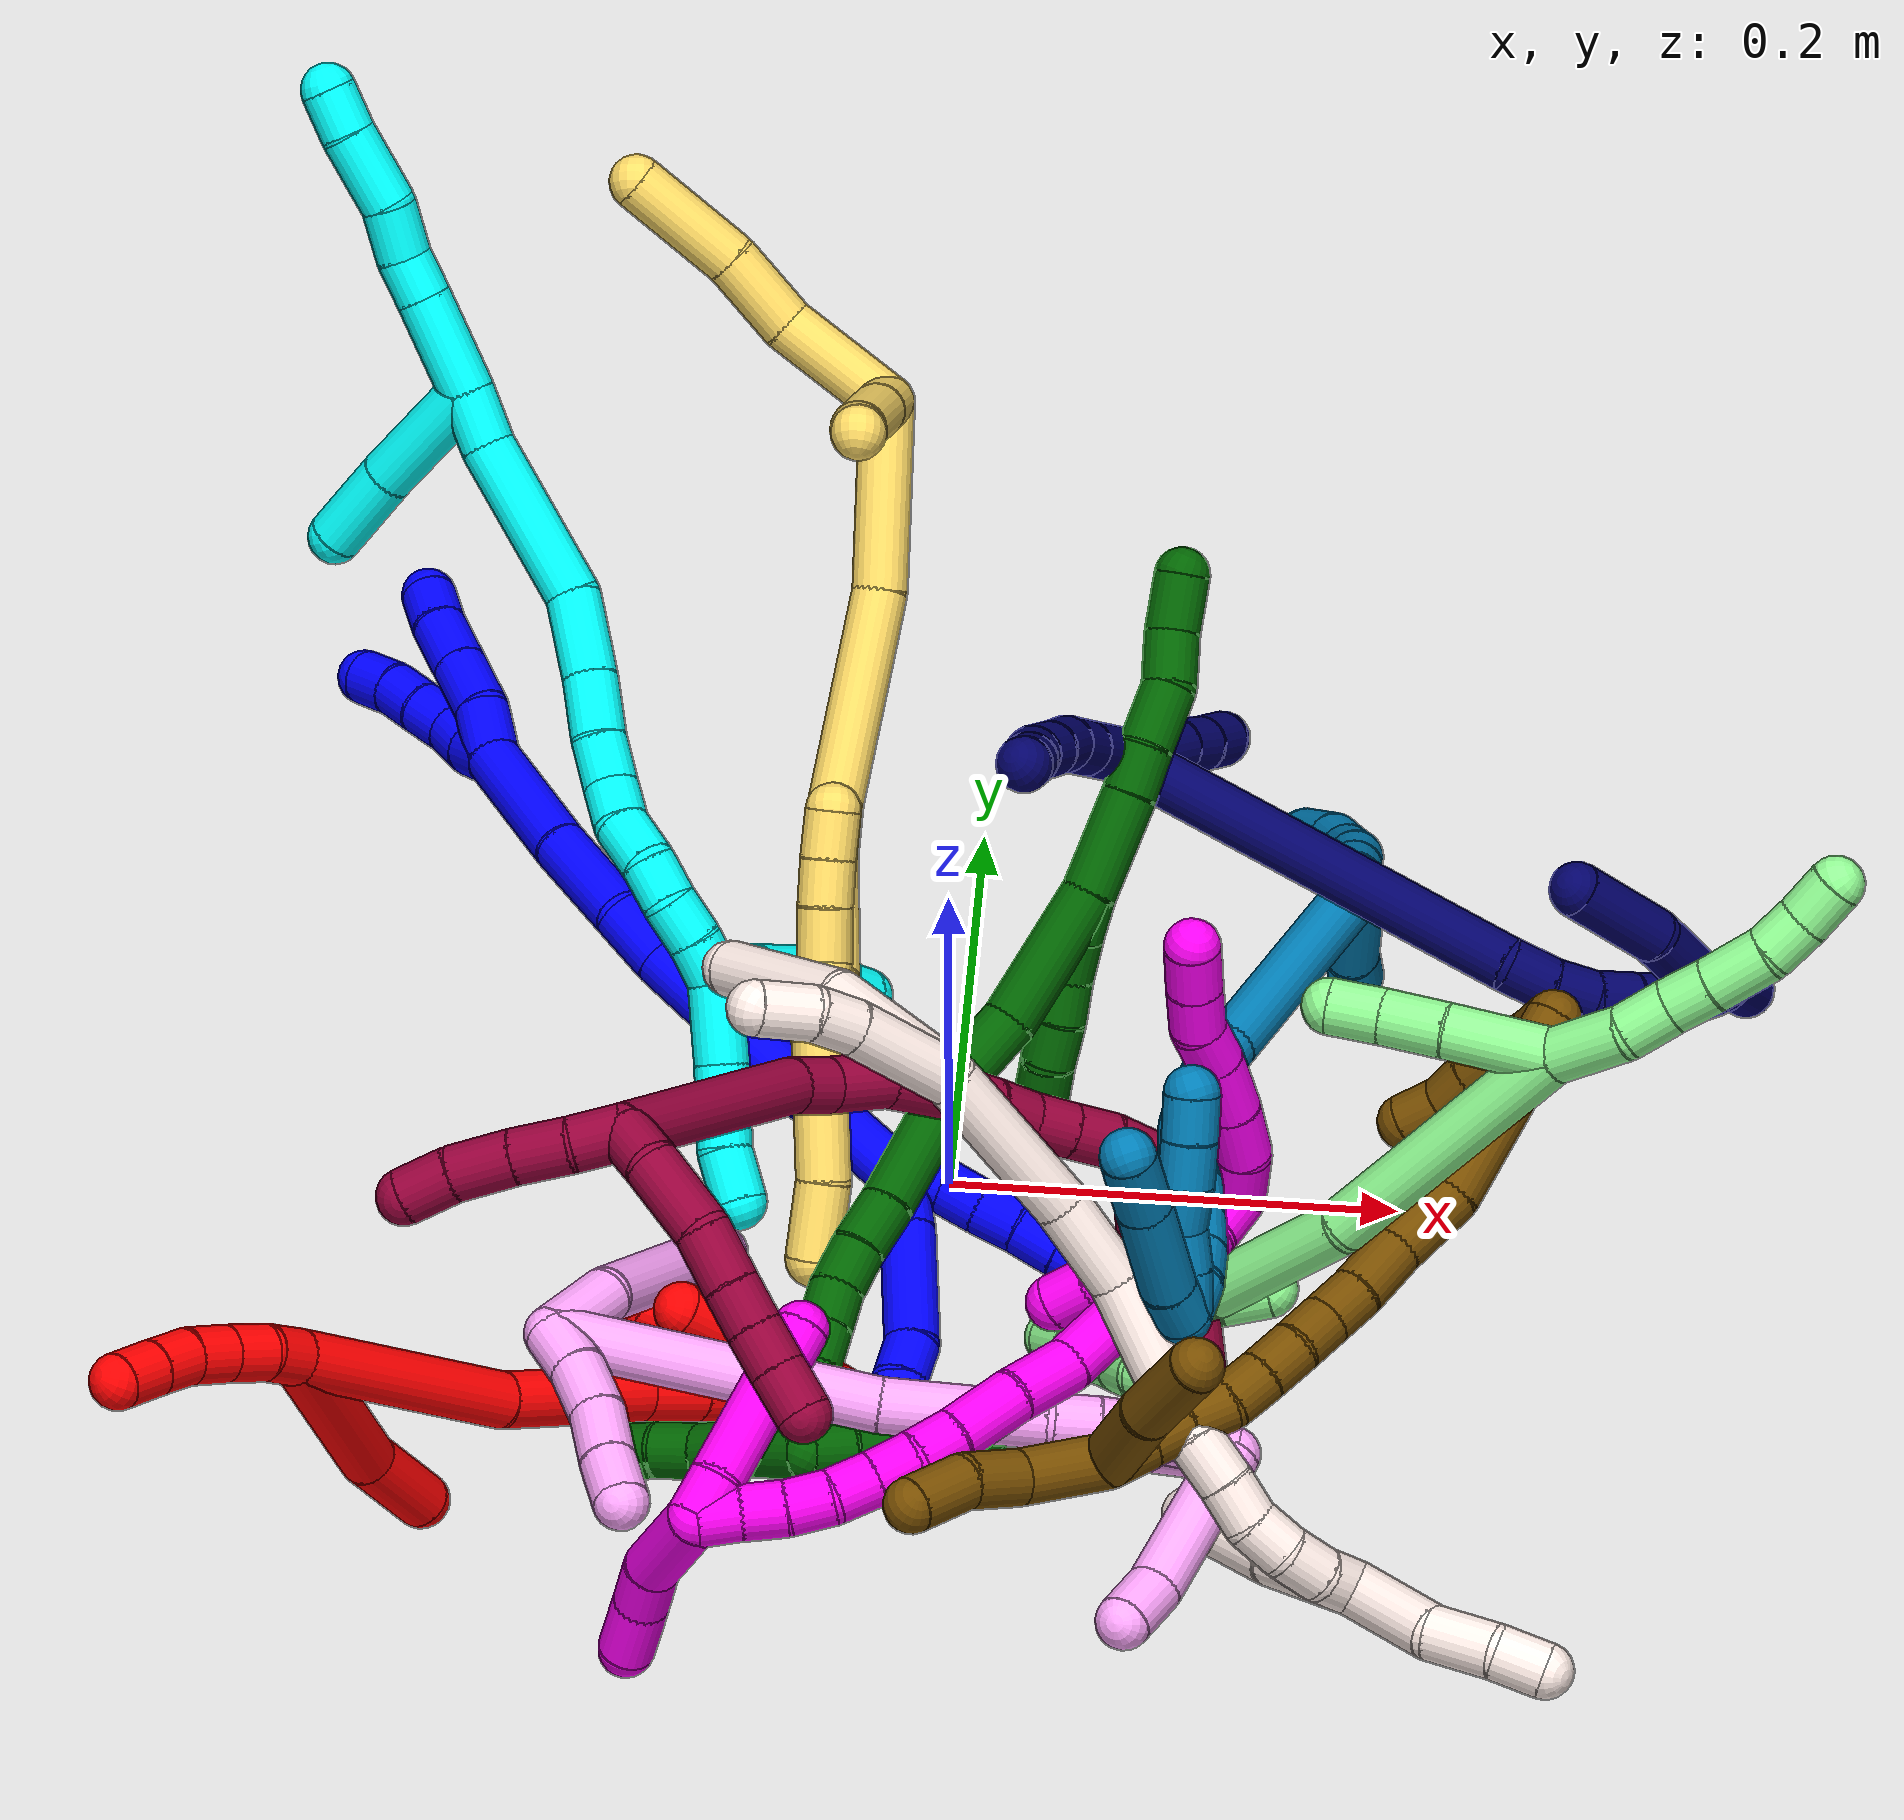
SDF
<sdf version="1.7">
 <world name="default">
  <plugin name="TubeGeneratorPlugin" filename="libtube_generator_plugin.so"/>
  <model name="photoneo_s_sensor">
   <static>1</static>
   <pose>0 0 2 1.57079 1.57079 3.14159</pose>
   <link name="link">
    <inertial><mass>0.1</mass></inertial>
    <sensor name="sensor" type="depth">
     <update_rate>30</update_rate>
     <camera>
      <horizontal_fov>1.22</horizontal_fov>
      <image><width>1920</width><height>1200</height><format>B8G8R8</format></image>
      <clip><near>0.1</near><far>4</far></clip>
      <depth_camera><output>points</output></depth_camera>
     </camera>
     <plugin name="camera_plugin" filename="libgazebo_ros_depth_camera.so">
      <baseline>0.2</baseline>
      <alwaysOn>1</alwaysOn>
      <updateRate>0.0</updateRate>
      <cameraName>camera_ir</cameraName>
      <imageTopicName>/camera/color/image_raw</imageTopicName>
      <cameraInfoTopicName>/camera/color/camera_info</cameraInfoTopicName>
      <depthImageTopicName>/camera/depth/image_raw</depthImageTopicName>
      <depthImageCameraInfoTopicName>/camera/depth/camera_info</depthImageCameraInfoTopicName>
      <pointCloudTopicName>/camera/depth/points</pointCloudTopicName>
      <frameName>fr_optical</frameName>
      <pointCloudCutoff>0.1</pointCloudCutoff>
      <pointCloudCutoffMax>2.0</pointCloudCutoffMax>
      <distortionK1>0</distortionK1>
      <distortionK2>0</distortionK2>
      <distortionK3>0</distortionK3>
      <distortionT1>0</distortionT1>
      <distortionT2>0</distortionT2>
      <CxPrime>0</CxPrime>
      <Cx>0</Cx>
      <Cy>0</Cy>
      <focalLength>0</focalLength>
      <hackBaseline>0</hackBaseline>
     </plugin>
    </sensor>
   </link>
  </model>
  <gravity>0 0 -9.8</gravity>
  <magnetic_field>6e-06 2.3e-05 -4.2e-05</magnetic_field>
  <atmosphere type="adiabatic"/>
  <physics name="default_physics" default="0" type="ode">
   <max_step_size>0.003</max_step_size>
   <real_time_factor>1</real_time_factor>
   <real_time_update_rate>1000</real_time_update_rate>
   <max_contacts>10000</max_contacts>
   <ode>
    <solver>
     <type>quick</type>
     <iters>100</iters>
     <sor>1.3</sor>
     <use_dynamic_moi_rescaling>0</use_dynamic_moi_rescaling>
    </solver>
    <constraints>
     <contact_max_correcting_vel>0</contact_max_correcting_vel>
     <contact_surface_layer>0.001</contact_surface_layer>
     <cfm>0</cfm>
     <erp>0.2</erp>
    </constraints>
   </ode>
  </physics>
  <scene><ambient>0.4 0.4 0.4 1</ambient><background>0.7 0.7 0.7 1</background><shadows>0</shadows></scene>
  <audio><device>default</device></audio>
  <spherical_coordinates>
   <surface_model>EARTH_WGS84</surface_model>
   <latitude_deg>0</latitude_deg>
   <longitude_deg>0</longitude_deg>
   <elevation>0</elevation>
   <heading_deg>0</heading_deg>
  </spherical_coordinates>
  <model name="bin">
   <static>1</static>
   <link name="bottom">
    <collision name="collision-bottom">
     <pose>0 0 -0.01 0 -0 0</pose>
     <geometry><box><size>0.8 0.6 0.02</size></box></geometry>
     <surface>
      <friction><ode><mu>100</mu><mu2>100</mu2></ode></friction>
      <contact><collide_bitmask>65535</collide_bitmask></contact>
     </surface>
    </collision>
   </link>
   <link name="west_wall">
    <collision name="collision-west_wall">
     <pose>-0.41 0 0.1 0 -0 0</pose>
     <geometry><box><size>0.02 0.6 0.2</size></box></geometry>
     <surface>
      <friction><ode><mu>100</mu><mu2>100</mu2></ode></friction>
      <contact><collide_bitmask>65535</collide_bitmask></contact>
     </surface>
    </collision>
   </link>
   <link name="east_wall">
    <collision name="collision-east_wall">
     <pose>0.41 0 0.1 0 -0 0</pose>
     <geometry><box><size>0.02 0.6 0.2</size></box></geometry>
     <surface>
      <friction><ode><mu>100</mu><mu2>100</mu2></ode></friction>
      <contact><collide_bitmask>65535</collide_bitmask></contact>
     </surface>
    </collision>
   </link>
   <link name="south_wall">
    <collision name="collision-south_wall">
     <pose>0 -0.31 0.1 0 -0 0</pose>
     <geometry><box><size>0.8 0.02 0.2</size></box></geometry>
     <surface>
      <friction><ode><mu>100</mu><mu2>100</mu2></ode></friction>
      <contact><collide_bitmask>65535</collide_bitmask></contact>
     </surface>
    </collision>
   </link>
   <link name="north_wall">
    <collision name="collision-north_wall">
     <pose>0 0.31 0.1 0 -0 0</pose>
     <geometry><box><size>0.8 0.02 0.2</size></box></geometry>
     <surface>
      <friction><ode><mu>100</mu><mu2>100</mu2></ode></friction>
      <contact><collide_bitmask>65535</collide_bitmask></contact>
     </surface>
    </collision>
   </link>
  </model>
  <model name="1">
   <static>0</static>
   <link name="1">
    <collision name="collision-cylinder-e_1_2_8">
     <pose>-0.000139 -0.006528 -0.012762 2.66879 -0.009706 -0.040283</pose>
     <geometry><cylinder><radius>0.0125</radius><length>0.028671</length></cylinder></geometry>
     <surface>
      <friction><ode><mu>1.16</mu><mu2>1.16</mu2><slip1>0</slip1><slip2>0</slip2></ode></friction>
      <contact><ode><kp>1e+06</kp><kd>1</kd><max_vel>0</max_vel><min_depth>0.001</min_depth></ode></contact>
     </surface>
    </collision>
    <visual name="visual-cylinder-e_1_2_8">
     <pose>-0.000139 -0.006528 -0.012762 2.66879 -0.009706 -0.040283</pose>
     <geometry><cylinder><radius>0.0125</radius><length>0.028671</length></cylinder></geometry>
     <material><ambient>0 0 1 1</ambient></material>
    </visual>
    <collision name="collision-cylinder-e_2_8_9">
     <pose>0.001338 -0.03099 -0.04934 2.49613 0.054158 0.161633</pose>
     <geometry><cylinder><radius>0.0125</radius><length>0.059714</length></cylinder></geometry>
     <surface>
      <friction><ode><mu>1.16</mu><mu2>1.16</mu2><slip1>0</slip1><slip2>0</slip2></ode></friction>
      <contact><ode><kp>1e+06</kp><kd>1</kd><max_vel>0</max_vel><min_depth>0.001</min_depth></ode></contact>
     </surface>
    </collision>
    <visual name="visual-cylinder-e_2_8_9">
     <pose>0.001338 -0.03099 -0.04934 2.49613 0.054158 0.161633</pose>
     <geometry><cylinder><radius>0.0125</radius><length>0.059714</length></cylinder></geometry>
     <material><ambient>0 0 1 1</ambient></material>
    </visual>
    <collision name="collision-cylinder-e_3_9_10">
     <pose>0.002292 -0.057091 -0.079331 2.2183 -0.064612 -0.129735</pose>
     <geometry><cylinder><radius>0.0125</radius><length>0.020519</length></cylinder></geometry>
     <surface>
      <friction><ode><mu>1.16</mu><mu2>1.16</mu2><slip1>0</slip1><slip2>0</slip2></ode></friction>
      <contact><ode><kp>1e+06</kp><kd>1</kd><max_vel>0</max_vel><min_depth>0.001</min_depth></ode></contact>
     </surface>
    </collision>
    <visual name="visual-cylinder-e_3_9_10">
     <pose>0.002292 -0.057091 -0.079331 2.2183 -0.064612 -0.129735</pose>
     <geometry><cylinder><radius>0.0125</radius><length>0.020519</length></cylinder></geometry>
     <material><ambient>0 0 1 1</ambient></material>
    </visual>
    <collision name="collision-cylinder-e_4_10_11">
     <pose>0.000861 -0.071905 -0.093508 2.44826 -0.073746 -0.203525</pose>
     <geometry><cylinder><radius>0.0125</radius><length>0.020863</length></cylinder></geometry>
     <surface>
      <friction><ode><mu>1.16</mu><mu2>1.16</mu2><slip1>0</slip1><slip2>0</slip2></ode></friction>
      <contact><ode><kp>1e+06</kp><kd>1</kd><max_vel>0</max_vel><min_depth>0.001</min_depth></ode></contact>
     </surface>
    </collision>
    <visual name="visual-cylinder-e_4_10_11">
     <pose>0.000861 -0.071905 -0.093508 2.44826 -0.073746 -0.203525</pose>
     <geometry><cylinder><radius>0.0125</radius><length>0.020863</length></cylinder></geometry>
     <material><ambient>0 0 1 1</ambient></material>
    </visual>
    <collision name="collision-cylinder-e_5_11_6">
     <pose>-0.000434 -0.084897 -0.109373 2.46288 -0.052051 -0.147216</pose>
     <geometry><cylinder><radius>0.0125</radius><length>0.020233</length></cylinder></geometry>
     <surface>
      <friction><ode><mu>1.16</mu><mu2>1.16</mu2><slip1>0</slip1><slip2>0</slip2></ode></friction>
      <contact><ode><kp>1e+06</kp><kd>1</kd><max_vel>0</max_vel><min_depth>0.001</min_depth></ode></contact>
     </surface>
    </collision>
    <visual name="visual-cylinder-e_5_11_6">
     <pose>-0.000434 -0.084897 -0.109373 2.46288 -0.052051 -0.147216</pose>
     <geometry><cylinder><radius>0.0125</radius><length>0.020233</length></cylinder></geometry>
     <material><ambient>0 0 1 1</ambient></material>
    </visual>
    <collision name="collision-cylinder-e_1_2_12">
     <pose>0.003317 0.006254 -0.007063 -2.41687 0.338118 -0.846109</pose>
     <geometry><cylinder><radius>0.0125</radius><length>0.02</length></cylinder></geometry>
     <surface>
      <friction><ode><mu>1.16</mu><mu2>1.16</mu2><slip1>0</slip1><slip2>0</slip2></ode></friction>
      <contact><ode><kp>1e+06</kp><kd>1</kd><max_vel>0</max_vel><min_depth>0.001</min_depth></ode></contact>
     </surface>
    </collision>
    <visual name="visual-cylinder-e_1_2_12">
     <pose>0.003317 0.006254 -0.007063 -2.41687 0.338118 -0.846109</pose>
     <geometry><cylinder><radius>0.0125</radius><length>0.02</length></cylinder></geometry>
     <material><ambient>0 0 1 1</ambient></material>
    </visual>
    <collision name="collision-cylinder-e_2_12_13">
     <pose>0.009265 0.016237 -0.023024 -2.74468 0.26618 -1.17472</pose>
     <geometry><cylinder><radius>0.0125</radius><length>0.02</length></cylinder></geometry>
     <surface>
      <friction><ode><mu>1.16</mu><mu2>1.16</mu2><slip1>0</slip1><slip2>0</slip2></ode></friction>
      <contact><ode><kp>1e+06</kp><kd>1</kd><max_vel>0</max_vel><min_depth>0.001</min_depth></ode></contact>
     </surface>
    </collision>
    <visual name="visual-cylinder-e_2_12_13">
     <pose>0.009265 0.016237 -0.023024 -2.74468 0.26618 -1.17472</pose>
     <geometry><cylinder><radius>0.0125</radius><length>0.02</length></cylinder></geometry>
     <material><ambient>0 0 1 1</ambient></material>
    </visual>
    <collision name="collision-cylinder-e_3_13_14">
     <pose>0.015605 0.023247 -0.040609 -2.78055 0.380089 -1.62337</pose>
     <geometry><cylinder><radius>0.0125</radius><length>0.02</length></cylinder></geometry>
     <surface>
      <friction><ode><mu>1.16</mu><mu2>1.16</mu2><slip1>0</slip1><slip2>0</slip2></ode></friction>
      <contact><ode><kp>1e+06</kp><kd>1</kd><max_vel>0</max_vel><min_depth>0.001</min_depth></ode></contact>
     </surface>
    </collision>
    <visual name="visual-cylinder-e_3_13_14">
     <pose>0.015605 0.023247 -0.040609 -2.78055 0.380089 -1.62337</pose>
     <geometry><cylinder><radius>0.0125</radius><length>0.02</length></cylinder></geometry>
     <material><ambient>0 0 1 1</ambient></material>
    </visual>
    <collision name="collision-cylinder-e_4_14_15">
     <pose>0.021966 0.030012 -0.058288 -2.77193 0.268261 -1.25033</pose>
     <geometry><cylinder><radius>0.0125</radius><length>0.02</length></cylinder></geometry>
     <surface>
      <friction><ode><mu>1.16</mu><mu2>1.16</mu2><slip1>0</slip1><slip2>0</slip2></ode></friction>
      <contact><ode><kp>1e+06</kp><kd>1</kd><max_vel>0</max_vel><min_depth>0.001</min_depth></ode></contact>
     </surface>
    </collision>
    <visual name="visual-cylinder-e_4_14_15">
     <pose>0.021966 0.030012 -0.058288 -2.77193 0.268261 -1.25033</pose>
     <geometry><cylinder><radius>0.0125</radius><length>0.02</length></cylinder></geometry>
     <material><ambient>0 0 1 1</ambient></material>
    </visual>
    <collision name="collision-cylinder-e_5_15_5">
     <pose>0.027347 0.037434 -0.076056 -2.71983 0.276548 -1.15288</pose>
     <geometry><cylinder><radius>0.0125</radius><length>0.02</length></cylinder></geometry>
     <surface>
      <friction><ode><mu>1.16</mu><mu2>1.16</mu2><slip1>0</slip1><slip2>0</slip2></ode></friction>
      <contact><ode><kp>1e+06</kp><kd>1</kd><max_vel>0</max_vel><min_depth>0.001</min_depth></ode></contact>
     </surface>
    </collision>
    <visual name="visual-cylinder-e_5_15_5">
     <pose>0.027347 0.037434 -0.076056 -2.71983 0.276548 -1.15288</pose>
     <geometry><cylinder><radius>0.0125</radius><length>0.02</length></cylinder></geometry>
     <material><ambient>0 0 1 1</ambient></material>
    </visual>
    <collision name="collision-cylinder-e_1_2_16">
     <pose>-0.007611 -0.002105 0.02442 0.085984 -0.301078 -0.01305</pose>
     <geometry><cylinder><radius>0.0125</radius><length>0.05133</length></cylinder></geometry>
     <surface>
      <friction><ode><mu>1.16</mu><mu2>1.16</mu2><slip1>0</slip1><slip2>0</slip2></ode></friction>
      <contact><ode><kp>1e+06</kp><kd>1</kd><max_vel>0</max_vel><min_depth>0.001</min_depth></ode></contact>
     </surface>
    </collision>
    <visual name="visual-cylinder-e_1_2_16">
     <pose>-0.007611 -0.002105 0.02442 0.085984 -0.301078 -0.01305</pose>
     <geometry><cylinder><radius>0.0125</radius><length>0.05133</length></cylinder></geometry>
     <material><ambient>0 0 1 1</ambient></material>
    </visual>
    <collision name="collision-cylinder-e_2_16_17">
     <pose>-0.031648 -0.005632 0.097844 0.029021 -0.323295 -0.004733</pose>
     <geometry><cylinder><radius>0.0125</radius><length>0.103405</length></cylinder></geometry>
     <surface>
      <friction><ode><mu>1.16</mu><mu2>1.16</mu2><slip1>0</slip1><slip2>0</slip2></ode></friction>
      <contact><ode><kp>1e+06</kp><kd>1</kd><max_vel>0</max_vel><min_depth>0.001</min_depth></ode></contact>
     </surface>
    </collision>
    <visual name="visual-cylinder-e_2_16_17">
     <pose>-0.031648 -0.005632 0.097844 0.029021 -0.323295 -0.004733</pose>
     <geometry><cylinder><radius>0.0125</radius><length>0.103405</length></cylinder></geometry>
     <material><ambient>0 0 1 1</ambient></material>
    </visual>
    <collision name="collision-cylinder-e_3_17_18">
     <pose>-0.051039 -0.007245 0.161217 0.013233 -0.203532 -0.001351</pose>
     <geometry><cylinder><radius>0.0125</radius><length>0.029349</length></cylinder></geometry>
     <surface>
      <friction><ode><mu>1.16</mu><mu2>1.16</mu2><slip1>0</slip1><slip2>0</slip2></ode></friction>
      <contact><ode><kp>1e+06</kp><kd>1</kd><max_vel>0</max_vel><min_depth>0.001</min_depth></ode></contact>
     </surface>
    </collision>
    <visual name="visual-cylinder-e_3_17_18">
     <pose>-0.051039 -0.007245 0.161217 0.013233 -0.203532 -0.001351</pose>
     <geometry><cylinder><radius>0.0125</radius><length>0.029349</length></cylinder></geometry>
     <material><ambient>0 0 1 1</ambient></material>
    </visual>
    <collision name="collision-cylinder-e_4_18_19">
     <pose>-0.063519 -0.003429 0.19798 -0.177046 -0.396117 0.035621</pose>
     <geometry><cylinder><radius>0.0125</radius><length>0.049314</length></cylinder></geometry>
     <surface>
      <friction><ode><mu>1.16</mu><mu2>1.16</mu2><slip1>0</slip1><slip2>0</slip2></ode></friction>
      <contact><ode><kp>1e+06</kp><kd>1</kd><max_vel>0</max_vel><min_depth>0.001</min_depth></ode></contact>
     </surface>
    </collision>
    <visual name="visual-cylinder-e_4_18_19">
     <pose>-0.063519 -0.003429 0.19798 -0.177046 -0.396117 0.035621</pose>
     <geometry><cylinder><radius>0.0125</radius><length>0.049314</length></cylinder></geometry>
     <material><ambient>0 0 1 1</ambient></material>
    </visual>
    <collision name="collision-cylinder-e_5_19_1">
     <pose>-0.086823 0.009424 0.249363 -0.296181 -0.426968 0.064659</pose>
     <geometry><cylinder><radius>0.0125</radius><length>0.066602</length></cylinder></geometry>
     <surface>
      <friction><ode><mu>1.16</mu><mu2>1.16</mu2><slip1>0</slip1><slip2>0</slip2></ode></friction>
      <contact><ode><kp>1e+06</kp><kd>1</kd><max_vel>0</max_vel><min_depth>0.001</min_depth></ode></contact>
     </surface>
    </collision>
    <visual name="visual-cylinder-e_5_19_1">
     <pose>-0.086823 0.009424 0.249363 -0.296181 -0.426968 0.064659</pose>
     <geometry><cylinder><radius>0.0125</radius><length>0.066602</length></cylinder></geometry>
     <material><ambient>0 0 1 1</ambient></material>
    </visual>
    <collision name="collision-cylinder-e_1_1_20">
     <pose>-0.101006 0.023652 0.290054 -0.431052 -0.030453 0.006667</pose>
     <geometry><cylinder><radius>0.0125</radius><length>0.025766</length></cylinder></geometry>
     <surface>
      <friction><ode><mu>1.16</mu><mu2>1.16</mu2><slip1>0</slip1><slip2>0</slip2></ode></friction>
      <contact><ode><kp>1e+06</kp><kd>1</kd><max_vel>0</max_vel><min_depth>0.001</min_depth></ode></contact>
     </surface>
    </collision>
    <visual name="visual-cylinder-e_1_1_20">
     <pose>-0.101006 0.023652 0.290054 -0.431052 -0.030453 0.006667</pose>
     <geometry><cylinder><radius>0.0125</radius><length>0.025766</length></cylinder></geometry>
     <material><ambient>0 0 1 1</ambient></material>
    </visual>
    <collision name="collision-cylinder-e_2_20_21">
     <pose>-0.105208 0.033663 0.314161 -0.357162 -0.280129 0.050887</pose>
     <geometry><cylinder><radius>0.0125</radius><length>0.027563</length></cylinder></geometry>
     <surface>
      <friction><ode><mu>1.16</mu><mu2>1.16</mu2><slip1>0</slip1><slip2>0</slip2></ode></friction>
      <contact><ode><kp>1e+06</kp><kd>1</kd><max_vel>0</max_vel><min_depth>0.001</min_depth></ode></contact>
     </surface>
    </collision>
    <visual name="visual-cylinder-e_2_20_21">
     <pose>-0.105208 0.033663 0.314161 -0.357162 -0.280129 0.050887</pose>
     <geometry><cylinder><radius>0.0125</radius><length>0.027563</length></cylinder></geometry>
     <material><ambient>0 0 1 1</ambient></material>
    </visual>
    <collision name="collision-cylinder-e_3_21_22">
     <pose>-0.112739 0.042728 0.33849 -0.356214 -0.28461 0.051571</pose>
     <geometry><cylinder><radius>0.0125</radius><length>0.026505</length></cylinder></geometry>
     <surface>
      <friction><ode><mu>1.16</mu><mu2>1.16</mu2><slip1>0</slip1><slip2>0</slip2></ode></friction>
      <contact><ode><kp>1e+06</kp><kd>1</kd><max_vel>0</max_vel><min_depth>0.001</min_depth></ode></contact>
     </surface>
    </collision>
    <visual name="visual-cylinder-e_3_21_22">
     <pose>-0.112739 0.042728 0.33849 -0.356214 -0.28461 0.051571</pose>
     <geometry><cylinder><radius>0.0125</radius><length>0.026505</length></cylinder></geometry>
     <material><ambient>0 0 1 1</ambient></material>
    </visual>
    <collision name="collision-cylinder-e_4_22_4">
     <pose>-0.119178 0.051794 0.358946 -0.497084 -0.272929 0.069671</pose>
     <geometry><cylinder><radius>0.0125</radius><length>0.020167</length></cylinder></geometry>
     <surface>
      <friction><ode><mu>1.16</mu><mu2>1.16</mu2><slip1>0</slip1><slip2>0</slip2></ode></friction>
      <contact><ode><kp>1e+06</kp><kd>1</kd><max_vel>0</max_vel><min_depth>0.001</min_depth></ode></contact>
     </surface>
    </collision>
    <visual name="visual-cylinder-e_4_22_4">
     <pose>-0.119178 0.051794 0.358946 -0.497084 -0.272929 0.069671</pose>
     <geometry><cylinder><radius>0.0125</radius><length>0.020167</length></cylinder></geometry>
     <material><ambient>0 0 1 1</ambient></material>
    </visual>
    <collision name="collision-cylinder-e_1_1_23">
     <pose>-0.108135 0.020816 0.284434 -0.396397 -0.85134 0.181613</pose>
     <geometry><cylinder><radius>0.0125</radius><length>0.02</length></cylinder></geometry>
     <surface>
      <friction><ode><mu>1.16</mu><mu2>1.16</mu2><slip1>0</slip1><slip2>0</slip2></ode></friction>
      <contact><ode><kp>1e+06</kp><kd>1</kd><max_vel>0</max_vel><min_depth>0.001</min_depth></ode></contact>
     </surface>
    </collision>
    <visual name="visual-cylinder-e_1_1_23">
     <pose>-0.108135 0.020816 0.284434 -0.396397 -0.85134 0.181613</pose>
     <geometry><cylinder><radius>0.0125</radius><length>0.02</length></cylinder></geometry>
     <material><ambient>0 0 1 1</ambient></material>
    </visual>
    <collision name="collision-cylinder-e_2_23_24">
     <pose>-0.12106 0.026173 0.298442 -0.340869 -0.570894 0.100926</pose>
     <geometry><cylinder><radius>0.0125</radius><length>0.02</length></cylinder></geometry>
     <surface>
      <friction><ode><mu>1.16</mu><mu2>1.16</mu2><slip1>0</slip1><slip2>0</slip2></ode></friction>
      <contact><ode><kp>1e+06</kp><kd>1</kd><max_vel>0</max_vel><min_depth>0.001</min_depth></ode></contact>
     </surface>
    </collision>
    <visual name="visual-cylinder-e_2_23_24">
     <pose>-0.12106 0.026173 0.298442 -0.340869 -0.570894 0.100926</pose>
     <geometry><cylinder><radius>0.0125</radius><length>0.02</length></cylinder></geometry>
     <material><ambient>0 0 1 1</ambient></material>
    </visual>
    <collision name="collision-cylinder-e_3_24_25">
     <pose>-0.131546 0.029029 0.314985 -0.005016 -0.533069 0.00137</pose>
     <geometry><cylinder><radius>0.0125</radius><length>0.02</length></cylinder></geometry>
     <surface>
      <friction><ode><mu>1.16</mu><mu2>1.16</mu2><slip1>0</slip1><slip2>0</slip2></ode></friction>
      <contact><ode><kp>1e+06</kp><kd>1</kd><max_vel>0</max_vel><min_depth>0.001</min_depth></ode></contact>
     </surface>
    </collision>
    <visual name="visual-cylinder-e_3_24_25">
     <pose>-0.131546 0.029029 0.314985 -0.005016 -0.533069 0.00137</pose>
     <geometry><cylinder><radius>0.0125</radius><length>0.02</length></cylinder></geometry>
     <material><ambient>0 0 1 1</ambient></material>
    </visual>
    <collision name="collision-cylinder-e_4_25_26">
     <pose>-0.142164 0.030036 0.331869 -0.115943 -0.586741 0.035061</pose>
     <geometry><cylinder><radius>0.0125</radius><length>0.02</length></cylinder></geometry>
     <surface>
      <friction><ode><mu>1.16</mu><mu2>1.16</mu2><slip1>0</slip1><slip2>0</slip2></ode></friction>
      <contact><ode><kp>1e+06</kp><kd>1</kd><max_vel>0</max_vel><min_depth>0.001</min_depth></ode></contact>
     </surface>
    </collision>
    <visual name="visual-cylinder-e_4_25_26">
     <pose>-0.142164 0.030036 0.331869 -0.115943 -0.586741 0.035061</pose>
     <geometry><cylinder><radius>0.0125</radius><length>0.02</length></cylinder></geometry>
     <material><ambient>0 0 1 1</ambient></material>
    </visual>
    <collision name="collision-cylinder-e_5_26_3">
     <pose>-0.154457 0.030923 0.347512 0.010343 -0.741861 -0.004023</pose>
     <geometry><cylinder><radius>0.0125</radius><length>0.02</length></cylinder></geometry>
     <surface>
      <friction><ode><mu>1.16</mu><mu2>1.16</mu2><slip1>0</slip1><slip2>0</slip2></ode></friction>
      <contact><ode><kp>1e+06</kp><kd>1</kd><max_vel>0</max_vel><min_depth>0.001</min_depth></ode></contact>
     </surface>
    </collision>
    <visual name="visual-cylinder-e_5_26_3">
     <pose>-0.154457 0.030923 0.347512 0.010343 -0.741861 -0.004023</pose>
     <geometry><cylinder><radius>0.0125</radius><length>0.02</length></cylinder></geometry>
     <material><ambient>0 0 1 1</ambient></material>
    </visual>
    <collision name="collision-sphere-3">
     <pose>-0.161214 0.030846 0.354884 0 -0 0</pose>
     <geometry><sphere><radius>0.0125</radius></sphere></geometry>
     <surface>
      <friction><ode><mu>1.16</mu><mu2>1.16</mu2><slip1>0</slip1><slip2>0</slip2></ode></friction>
      <contact><ode><kp>1e+06</kp><kd>1</kd><max_vel>0</max_vel><min_depth>0.001</min_depth></ode></contact>
     </surface>
    </collision>
    <visual name="visual-sphere-3">
     <pose>-0.161214 0.030846 0.354884 0 -0 0</pose>
     <geometry><sphere><radius>0.0125</radius></sphere></geometry>
     <material><ambient>0 0 1 1</ambient></material>
    </visual>
    <collision name="collision-sphere-26">
     <pose>-0.147701 0.030999 0.34014 0 -0 0</pose>
     <geometry><sphere><radius>0.0125</radius></sphere></geometry>
     <surface>
      <friction><ode><mu>1.16</mu><mu2>1.16</mu2><slip1>0</slip1><slip2>0</slip2></ode></friction>
      <contact><ode><kp>1e+06</kp><kd>1</kd><max_vel>0</max_vel><min_depth>0.001</min_depth></ode></contact>
     </surface>
    </collision>
    <visual name="visual-sphere-26">
     <pose>-0.147701 0.030999 0.34014 0 -0 0</pose>
     <geometry><sphere><radius>0.0125</radius></sphere></geometry>
     <material><ambient>0 0 1 1</ambient></material>
    </visual>
    <collision name="collision-sphere-25">
     <pose>-0.136628 0.029072 0.323597 0 -0 0</pose>
     <geometry><sphere><radius>0.0125</radius></sphere></geometry>
     <surface>
      <friction><ode><mu>1.16</mu><mu2>1.16</mu2><slip1>0</slip1><slip2>0</slip2></ode></friction>
      <contact><ode><kp>1e+06</kp><kd>1</kd><max_vel>0</max_vel><min_depth>0.001</min_depth></ode></contact>
     </surface>
    </collision>
    <visual name="visual-sphere-25">
     <pose>-0.136628 0.029072 0.323597 0 -0 0</pose>
     <geometry><sphere><radius>0.0125</radius></sphere></geometry>
     <material><ambient>0 0 1 1</ambient></material>
    </visual>
    <collision name="collision-sphere-24">
     <pose>-0.126464 0.028986 0.306372 0 -0 0</pose>
     <geometry><sphere><radius>0.0125</radius></sphere></geometry>
     <surface>
      <friction><ode><mu>1.16</mu><mu2>1.16</mu2><slip1>0</slip1><slip2>0</slip2></ode></friction>
      <contact><ode><kp>1e+06</kp><kd>1</kd><max_vel>0</max_vel><min_depth>0.001</min_depth></ode></contact>
     </surface>
    </collision>
    <visual name="visual-sphere-24">
     <pose>-0.126464 0.028986 0.306372 0 -0 0</pose>
     <geometry><sphere><radius>0.0125</radius></sphere></geometry>
     <material><ambient>0 0 1 1</ambient></material>
    </visual>
    <collision name="collision-sphere-23">
     <pose>-0.115657 0.02336 0.290512 0 -0 0</pose>
     <geometry><sphere><radius>0.0125</radius></sphere></geometry>
     <surface>
      <friction><ode><mu>1.16</mu><mu2>1.16</mu2><slip1>0</slip1><slip2>0</slip2></ode></friction>
      <contact><ode><kp>1e+06</kp><kd>1</kd><max_vel>0</max_vel><min_depth>0.001</min_depth></ode></contact>
     </surface>
    </collision>
    <visual name="visual-sphere-23">
     <pose>-0.115657 0.02336 0.290512 0 -0 0</pose>
     <geometry><sphere><radius>0.0125</radius></sphere></geometry>
     <material><ambient>0 0 1 1</ambient></material>
    </visual>
    <collision name="collision-sphere-4">
     <pose>-0.121896 0.056425 0.367481 0 -0 0</pose>
     <geometry><sphere><radius>0.0125</radius></sphere></geometry>
     <surface>
      <friction><ode><mu>1.16</mu><mu2>1.16</mu2><slip1>0</slip1><slip2>0</slip2></ode></friction>
      <contact><ode><kp>1e+06</kp><kd>1</kd><max_vel>0</max_vel><min_depth>0.001</min_depth></ode></contact>
     </surface>
    </collision>
    <visual name="visual-sphere-4">
     <pose>-0.121896 0.056425 0.367481 0 -0 0</pose>
     <geometry><sphere><radius>0.0125</radius></sphere></geometry>
     <material><ambient>0 0 1 1</ambient></material>
    </visual>
    <collision name="collision-sphere-22">
     <pose>-0.11646 0.047164 0.350411 0 -0 0</pose>
     <geometry><sphere><radius>0.0125</radius></sphere></geometry>
     <surface>
      <friction><ode><mu>1.16</mu><mu2>1.16</mu2><slip1>0</slip1><slip2>0</slip2></ode></friction>
      <contact><ode><kp>1e+06</kp><kd>1</kd><max_vel>0</max_vel><min_depth>0.001</min_depth></ode></contact>
     </surface>
    </collision>
    <visual name="visual-sphere-22">
     <pose>-0.11646 0.047164 0.350411 0 -0 0</pose>
     <geometry><sphere><radius>0.0125</radius></sphere></geometry>
     <material><ambient>0 0 1 1</ambient></material>
    </visual>
    <collision name="collision-sphere-21">
     <pose>-0.109018 0.038293 0.32657 0 -0 0</pose>
     <geometry><sphere><radius>0.0125</radius></sphere></geometry>
     <surface>
      <friction><ode><mu>1.16</mu><mu2>1.16</mu2><slip1>0</slip1><slip2>0</slip2></ode></friction>
      <contact><ode><kp>1e+06</kp><kd>1</kd><max_vel>0</max_vel><min_depth>0.001</min_depth></ode></contact>
     </surface>
    </collision>
    <visual name="visual-sphere-21">
     <pose>-0.109018 0.038293 0.32657 0 -0 0</pose>
     <geometry><sphere><radius>0.0125</radius></sphere></geometry>
     <material><ambient>0 0 1 1</ambient></material>
    </visual>
    <collision name="collision-sphere-20">
     <pose>-0.101398 0.029032 0.301753 0 -0 0</pose>
     <geometry><sphere><radius>0.0125</radius></sphere></geometry>
     <surface>
      <friction><ode><mu>1.16</mu><mu2>1.16</mu2><slip1>0</slip1><slip2>0</slip2></ode></friction>
      <contact><ode><kp>1e+06</kp><kd>1</kd><max_vel>0</max_vel><min_depth>0.001</min_depth></ode></contact>
     </surface>
    </collision>
    <visual name="visual-sphere-20">
     <pose>-0.101398 0.029032 0.301753 0 -0 0</pose>
     <geometry><sphere><radius>0.0125</radius></sphere></geometry>
     <material><ambient>0 0 1 1</ambient></material>
    </visual>
    <collision name="collision-sphere-6">
     <pose>-0.00096 -0.091239 -0.117237 0 -0 0</pose>
     <geometry><sphere><radius>0.0125</radius></sphere></geometry>
     <surface>
      <friction><ode><mu>1.16</mu><mu2>1.16</mu2><slip1>0</slip1><slip2>0</slip2></ode></friction>
      <contact><ode><kp>1e+06</kp><kd>1</kd><max_vel>0</max_vel><min_depth>0.001</min_depth></ode></contact>
     </surface>
    </collision>
    <visual name="visual-sphere-6">
     <pose>-0.00096 -0.091239 -0.117237 0 -0 0</pose>
     <geometry><sphere><radius>0.0125</radius></sphere></geometry>
     <material><ambient>0 0 1 1</ambient></material>
    </visual>
    <collision name="collision-sphere-11">
     <pose>9.2e-05 -0.078554 -0.101509 0 -0 0</pose>
     <geometry><sphere><radius>0.0125</radius></sphere></geometry>
     <surface>
      <friction><ode><mu>1.16</mu><mu2>1.16</mu2><slip1>0</slip1><slip2>0</slip2></ode></friction>
      <contact><ode><kp>1e+06</kp><kd>1</kd><max_vel>0</max_vel><min_depth>0.001</min_depth></ode></contact>
     </surface>
    </collision>
    <visual name="visual-sphere-11">
     <pose>9.2e-05 -0.078554 -0.101509 0 -0 0</pose>
     <geometry><sphere><radius>0.0125</radius></sphere></geometry>
     <material><ambient>0 0 1 1</ambient></material>
    </visual>
    <collision name="collision-sphere-10">
     <pose>0.001629 -0.065257 -0.085507 0 -0 0</pose>
     <geometry><sphere><radius>0.0125</radius></sphere></geometry>
     <surface>
      <friction><ode><mu>1.16</mu><mu2>1.16</mu2><slip1>0</slip1><slip2>0</slip2></ode></friction>
      <contact><ode><kp>1e+06</kp><kd>1</kd><max_vel>0</max_vel><min_depth>0.001</min_depth></ode></contact>
     </surface>
    </collision>
    <visual name="visual-sphere-10">
     <pose>0.001629 -0.065257 -0.085507 0 -0 0</pose>
     <geometry><sphere><radius>0.0125</radius></sphere></geometry>
     <material><ambient>0 0 1 1</ambient></material>
    </visual>
    <collision name="collision-sphere-9">
     <pose>0.002954 -0.048925 -0.073155 0 -0 0</pose>
     <geometry><sphere><radius>0.0125</radius></sphere></geometry>
     <surface>
      <friction><ode><mu>1.16</mu><mu2>1.16</mu2><slip1>0</slip1><slip2>0</slip2></ode></friction>
      <contact><ode><kp>1e+06</kp><kd>1</kd><max_vel>0</max_vel><min_depth>0.001</min_depth></ode></contact>
     </surface>
    </collision>
    <visual name="visual-sphere-9">
     <pose>0.002954 -0.048925 -0.073155 0 -0 0</pose>
     <geometry><sphere><radius>0.0125</radius></sphere></geometry>
     <material><ambient>0 0 1 1</ambient></material>
    </visual>
    <collision name="collision-sphere-2">
     <geometry><sphere><radius>0.0125</radius></sphere></geometry>
     <surface>
      <friction><ode><mu>1.16</mu><mu2>1.16</mu2><slip1>0</slip1><slip2>0</slip2></ode></friction>
      <contact><ode><kp>1e+06</kp><kd>1</kd><max_vel>0</max_vel><min_depth>0.001</min_depth></ode></contact>
     </surface>
    </collision>
    <visual name="visual-sphere-2">
     <geometry><sphere><radius>0.0125</radius></sphere></geometry>
     <material><ambient>0 0 1 1</ambient></material>
    </visual>
    <collision name="collision-sphere-19">
     <pose>-0.073033 0.000577 0.220372 0 -0 0</pose>
     <geometry><sphere><radius>0.0125</radius></sphere></geometry>
     <surface>
      <friction><ode><mu>1.16</mu><mu2>1.16</mu2><slip1>0</slip1><slip2>0</slip2></ode></friction>
      <contact><ode><kp>1e+06</kp><kd>1</kd><max_vel>0</max_vel><min_depth>0.001</min_depth></ode></contact>
     </surface>
    </collision>
    <visual name="visual-sphere-19">
     <pose>-0.073033 0.000577 0.220372 0 -0 0</pose>
     <geometry><sphere><radius>0.0125</radius></sphere></geometry>
     <material><ambient>0 0 1 1</ambient></material>
    </visual>
    <collision name="collision-sphere-8">
     <pose>-0.000278 -0.013056 -0.025524 0 -0 0</pose>
     <geometry><sphere><radius>0.0125</radius></sphere></geometry>
     <surface>
      <friction><ode><mu>1.16</mu><mu2>1.16</mu2><slip1>0</slip1><slip2>0</slip2></ode></friction>
      <contact><ode><kp>1e+06</kp><kd>1</kd><max_vel>0</max_vel><min_depth>0.001</min_depth></ode></contact>
     </surface>
    </collision>
    <visual name="visual-sphere-8">
     <pose>-0.000278 -0.013056 -0.025524 0 -0 0</pose>
     <geometry><sphere><radius>0.0125</radius></sphere></geometry>
     <material><ambient>0 0 1 1</ambient></material>
    </visual>
    <collision name="collision-sphere-12">
     <pose>0.006634 0.012508 -0.014126 0 -0 0</pose>
     <geometry><sphere><radius>0.0125</radius></sphere></geometry>
     <surface>
      <friction><ode><mu>1.16</mu><mu2>1.16</mu2><slip1>0</slip1><slip2>0</slip2></ode></friction>
      <contact><ode><kp>1e+06</kp><kd>1</kd><max_vel>0</max_vel><min_depth>0.001</min_depth></ode></contact>
     </surface>
    </collision>
    <visual name="visual-sphere-12">
     <pose>0.006634 0.012508 -0.014126 0 -0 0</pose>
     <geometry><sphere><radius>0.0125</radius></sphere></geometry>
     <material><ambient>0 0 1 1</ambient></material>
    </visual>
    <collision name="collision-sphere-13">
     <pose>0.011895 0.019967 -0.031921 0 -0 0</pose>
     <geometry><sphere><radius>0.0125</radius></sphere></geometry>
     <surface>
      <friction><ode><mu>1.16</mu><mu2>1.16</mu2><slip1>0</slip1><slip2>0</slip2></ode></friction>
      <contact><ode><kp>1e+06</kp><kd>1</kd><max_vel>0</max_vel><min_depth>0.001</min_depth></ode></contact>
     </surface>
    </collision>
    <visual name="visual-sphere-13">
     <pose>0.011895 0.019967 -0.031921 0 -0 0</pose>
     <geometry><sphere><radius>0.0125</radius></sphere></geometry>
     <material><ambient>0 0 1 1</ambient></material>
    </visual>
    <collision name="collision-sphere-14">
     <pose>0.019315 0.026528 -0.049297 0 -0 0</pose>
     <geometry><sphere><radius>0.0125</radius></sphere></geometry>
     <surface>
      <friction><ode><mu>1.16</mu><mu2>1.16</mu2><slip1>0</slip1><slip2>0</slip2></ode></friction>
      <contact><ode><kp>1e+06</kp><kd>1</kd><max_vel>0</max_vel><min_depth>0.001</min_depth></ode></contact>
     </surface>
    </collision>
    <visual name="visual-sphere-14">
     <pose>0.019315 0.026528 -0.049297 0 -0 0</pose>
     <geometry><sphere><radius>0.0125</radius></sphere></geometry>
     <material><ambient>0 0 1 1</ambient></material>
    </visual>
    <collision name="collision-sphere-15">
     <pose>0.024616 0.033495 -0.067279 0 -0 0</pose>
     <geometry><sphere><radius>0.0125</radius></sphere></geometry>
     <surface>
      <friction><ode><mu>1.16</mu><mu2>1.16</mu2><slip1>0</slip1><slip2>0</slip2></ode></friction>
      <contact><ode><kp>1e+06</kp><kd>1</kd><max_vel>0</max_vel><min_depth>0.001</min_depth></ode></contact>
     </surface>
    </collision>
    <visual name="visual-sphere-15">
     <pose>0.024616 0.033495 -0.067279 0 -0 0</pose>
     <geometry><sphere><radius>0.0125</radius></sphere></geometry>
     <material><ambient>0 0 1 1</ambient></material>
    </visual>
    <collision name="collision-sphere-5">
     <pose>0.030077 0.041372 -0.084833 0 -0 0</pose>
     <geometry><sphere><radius>0.0125</radius></sphere></geometry>
     <surface>
      <friction><ode><mu>1.16</mu><mu2>1.16</mu2><slip1>0</slip1><slip2>0</slip2></ode></friction>
      <contact><ode><kp>1e+06</kp><kd>1</kd><max_vel>0</max_vel><min_depth>0.001</min_depth></ode></contact>
     </surface>
    </collision>
    <visual name="visual-sphere-5">
     <pose>0.030077 0.041372 -0.084833 0 -0 0</pose>
     <geometry><sphere><radius>0.0125</radius></sphere></geometry>
     <material><ambient>0 0 1 1</ambient></material>
    </visual>
    <collision name="collision-sphere-16">
     <pose>-0.015222 -0.00421 0.04884 0 -0 0</pose>
     <geometry><sphere><radius>0.0125</radius></sphere></geometry>
     <surface>
      <friction><ode><mu>1.16</mu><mu2>1.16</mu2><slip1>0</slip1><slip2>0</slip2></ode></friction>
      <contact><ode><kp>1e+06</kp><kd>1</kd><max_vel>0</max_vel><min_depth>0.001</min_depth></ode></contact>
     </surface>
    </collision>
    <visual name="visual-sphere-16">
     <pose>-0.015222 -0.00421 0.04884 0 -0 0</pose>
     <geometry><sphere><radius>0.0125</radius></sphere></geometry>
     <material><ambient>0 0 1 1</ambient></material>
    </visual>
    <collision name="collision-sphere-17">
     <pose>-0.048073 -0.007055 0.146847 0 -0 0</pose>
     <geometry><sphere><radius>0.0125</radius></sphere></geometry>
     <surface>
      <friction><ode><mu>1.16</mu><mu2>1.16</mu2><slip1>0</slip1><slip2>0</slip2></ode></friction>
      <contact><ode><kp>1e+06</kp><kd>1</kd><max_vel>0</max_vel><min_depth>0.001</min_depth></ode></contact>
     </surface>
    </collision>
    <visual name="visual-sphere-17">
     <pose>-0.048073 -0.007055 0.146847 0 -0 0</pose>
     <geometry><sphere><radius>0.0125</radius></sphere></geometry>
     <material><ambient>0 0 1 1</ambient></material>
    </visual>
    <collision name="collision-sphere-18">
     <pose>-0.054005 -0.007435 0.175588 0 -0 0</pose>
     <geometry><sphere><radius>0.0125</radius></sphere></geometry>
     <surface>
      <friction><ode><mu>1.16</mu><mu2>1.16</mu2><slip1>0</slip1><slip2>0</slip2></ode></friction>
      <contact><ode><kp>1e+06</kp><kd>1</kd><max_vel>0</max_vel><min_depth>0.001</min_depth></ode></contact>
     </surface>
    </collision>
    <visual name="visual-sphere-18">
     <pose>-0.054005 -0.007435 0.175588 0 -0 0</pose>
     <geometry><sphere><radius>0.0125</radius></sphere></geometry>
     <material><ambient>0 0 1 1</ambient></material>
    </visual>
    <collision name="collision-sphere-1">
     <pose>-0.100613 0.018271 0.278355 0 -0 0</pose>
     <geometry><sphere><radius>0.0125</radius></sphere></geometry>
     <surface>
      <friction><ode><mu>1.16</mu><mu2>1.16</mu2><slip1>0</slip1><slip2>0</slip2></ode></friction>
      <contact><ode><kp>1e+06</kp><kd>1</kd><max_vel>0</max_vel><min_depth>0.001</min_depth></ode></contact>
     </surface>
    </collision>
    <visual name="visual-sphere-1">
     <pose>-0.100613 0.018271 0.278355 0 -0 0</pose>
     <geometry><sphere><radius>0.0125</radius></sphere></geometry>
     <material><ambient>0 0 1 1</ambient></material>
    </visual>
    <inertial>
     <pose>-0.04858 0.002461 0.124209 0 -0 0</pose>
     <mass>0.75</mass>
     <inertia>
      <ixx>0.000173</ixx>
      <ixy>0</ixy>
      <ixz>0</ixz>
      <iyy>0.000143</iyy>
      <iyz>0</iyz>
      <izz>7.7e-05</izz>
     </inertia>
    </inertial>
   </link>
   <pose>-0.021233 -0.020342 0.029847 -0.678309 -1.07173 -0.129554</pose>
  </model>
  <model name="2">
   <static>0</static>
   <link name="2">
    <collision name="collision-cylinder-e_1_2_8">
     <pose>-0.008513 -0.026144 -0.042823 2.59347 -0.168069 -0.582214</pose>
     <geometry><cylinder><radius>0.0125</radius><length>0.101779</length></cylinder></geometry>
     <surface>
      <friction><ode><mu>1.16</mu><mu2>1.16</mu2><slip1>0</slip1><slip2>0</slip2></ode></friction>
      <contact><ode><kp>1e+06</kp><kd>1</kd><max_vel>0</max_vel><min_depth>0.001</min_depth></ode></contact>
     </surface>
    </collision>
    <visual name="visual-cylinder-e_1_2_8">
     <pose>-0.008513 -0.026144 -0.042823 2.59347 -0.168069 -0.582214</pose>
     <geometry><cylinder><radius>0.0125</radius><length>0.101779</length></cylinder></geometry>
     <material><ambient>1 0 0 1</ambient></material>
    </visual>
    <collision name="collision-cylinder-e_2_8_6">
     <pose>-0.0187 -0.060627 -0.108206 2.78755 -0.069496 -0.383846</pose>
     <geometry><cylinder><radius>0.0125</radius><length>0.048221</length></cylinder></geometry>
     <surface>
      <friction><ode><mu>1.16</mu><mu2>1.16</mu2><slip1>0</slip1><slip2>0</slip2></ode></friction>
      <contact><ode><kp>1e+06</kp><kd>1</kd><max_vel>0</max_vel><min_depth>0.001</min_depth></ode></contact>
     </surface>
    </collision>
    <visual name="visual-cylinder-e_2_8_6">
     <pose>-0.0187 -0.060627 -0.108206 2.78755 -0.069496 -0.383846</pose>
     <geometry><cylinder><radius>0.0125</radius><length>0.048221</length></cylinder></geometry>
     <material><ambient>1 0 0 1</ambient></material>
    </visual>
    <collision name="collision-cylinder-e_1_2_9">
     <pose>0.001302 9.3e-05 0.009914 -0.009346 0.130563 -0.000611</pose>
     <geometry><cylinder><radius>0.0125</radius><length>0.02</length></cylinder></geometry>
     <surface>
      <friction><ode><mu>1.16</mu><mu2>1.16</mu2><slip1>0</slip1><slip2>0</slip2></ode></friction>
      <contact><ode><kp>1e+06</kp><kd>1</kd><max_vel>0</max_vel><min_depth>0.001</min_depth></ode></contact>
     </surface>
    </collision>
    <visual name="visual-cylinder-e_1_2_9">
     <pose>0.001302 9.3e-05 0.009914 -0.009346 0.130563 -0.000611</pose>
     <geometry><cylinder><radius>0.0125</radius><length>0.02</length></cylinder></geometry>
     <material><ambient>1 0 0 1</ambient></material>
    </visual>
    <collision name="collision-cylinder-e_2_9_10">
     <pose>0.002982 -0.002135 0.029549 0.234358 0.037866 0.004458</pose>
     <geometry><cylinder><radius>0.0125</radius><length>0.02</length></cylinder></geometry>
     <surface>
      <friction><ode><mu>1.16</mu><mu2>1.16</mu2><slip1>0</slip1><slip2>0</slip2></ode></friction>
      <contact><ode><kp>1e+06</kp><kd>1</kd><max_vel>0</max_vel><min_depth>0.001</min_depth></ode></contact>
     </surface>
    </collision>
    <visual name="visual-cylinder-e_2_9_10">
     <pose>0.002982 -0.002135 0.029549 0.234358 0.037866 0.004458</pose>
     <geometry><cylinder><radius>0.0125</radius><length>0.02</length></cylinder></geometry>
     <material><ambient>1 0 0 1</ambient></material>
    </visual>
    <collision name="collision-cylinder-e_3_10_11">
     <pose>0.00426 -0.006789 0.04895 0.236501 0.090053 0.010706</pose>
     <geometry><cylinder><radius>0.0125</radius><length>0.02</length></cylinder></geometry>
     <surface>
      <friction><ode><mu>1.16</mu><mu2>1.16</mu2><slip1>0</slip1><slip2>0</slip2></ode></friction>
      <contact><ode><kp>1e+06</kp><kd>1</kd><max_vel>0</max_vel><min_depth>0.001</min_depth></ode></contact>
     </surface>
    </collision>
    <visual name="visual-cylinder-e_3_10_11">
     <pose>0.00426 -0.006789 0.04895 0.236501 0.090053 0.010706</pose>
     <geometry><cylinder><radius>0.0125</radius><length>0.02</length></cylinder></geometry>
     <material><ambient>1 0 0 1</ambient></material>
    </visual>
    <collision name="collision-cylinder-e_4_11_12">
     <pose>0.007977 -0.012264 0.067699 0.333546 0.285584 0.048394</pose>
     <geometry><cylinder><radius>0.0125</radius><length>0.02</length></cylinder></geometry>
     <surface>
      <friction><ode><mu>1.16</mu><mu2>1.16</mu2><slip1>0</slip1><slip2>0</slip2></ode></friction>
      <contact><ode><kp>1e+06</kp><kd>1</kd><max_vel>0</max_vel><min_depth>0.001</min_depth></ode></contact>
     </surface>
    </collision>
    <visual name="visual-cylinder-e_4_11_12">
     <pose>0.007977 -0.012264 0.067699 0.333546 0.285584 0.048394</pose>
     <geometry><cylinder><radius>0.0125</radius><length>0.02</length></cylinder></geometry>
     <material><ambient>1 0 0 1</ambient></material>
    </visual>
    <collision name="collision-cylinder-e_5_12_5">
     <pose>0.013742 -0.01872 0.085727 0.354246 0.299209 0.053948</pose>
     <geometry><cylinder><radius>0.0125</radius><length>0.02</length></cylinder></geometry>
     <surface>
      <friction><ode><mu>1.16</mu><mu2>1.16</mu2><slip1>0</slip1><slip2>0</slip2></ode></friction>
      <contact><ode><kp>1e+06</kp><kd>1</kd><max_vel>0</max_vel><min_depth>0.001</min_depth></ode></contact>
     </surface>
    </collision>
    <visual name="visual-cylinder-e_5_12_5">
     <pose>0.013742 -0.01872 0.085727 0.354246 0.299209 0.053948</pose>
     <geometry><cylinder><radius>0.0125</radius><length>0.02</length></cylinder></geometry>
     <material><ambient>1 0 0 1</ambient></material>
    </visual>
    <collision name="collision-cylinder-e_1_2_13">
     <pose>0.001168 0.002166 -0.056493 -3.10328 0.020651 -0.988623</pose>
     <geometry><cylinder><radius>0.0125</radius><length>0.113093</length></cylinder></geometry>
     <surface>
      <friction><ode><mu>1.16</mu><mu2>1.16</mu2><slip1>0</slip1><slip2>0</slip2></ode></friction>
      <contact><ode><kp>1e+06</kp><kd>1</kd><max_vel>0</max_vel><min_depth>0.001</min_depth></ode></contact>
     </surface>
    </collision>
    <visual name="visual-cylinder-e_1_2_13">
     <pose>0.001168 0.002166 -0.056493 -3.10328 0.020651 -0.988623</pose>
     <geometry><cylinder><radius>0.0125</radius><length>0.113093</length></cylinder></geometry>
     <material><ambient>1 0 0 1</ambient></material>
    </visual>
    <collision name="collision-cylinder-e_2_13_14">
     <pose>-0.001103 0.012246 -0.150079 -2.93138 -0.090398 0.810062</pose>
     <geometry><cylinder><radius>0.0125</radius><length>0.076168</length></cylinder></geometry>
     <surface>
      <friction><ode><mu>1.16</mu><mu2>1.16</mu2><slip1>0</slip1><slip2>0</slip2></ode></friction>
      <contact><ode><kp>1e+06</kp><kd>1</kd><max_vel>0</max_vel><min_depth>0.001</min_depth></ode></contact>
     </surface>
    </collision>
    <visual name="visual-cylinder-e_2_13_14">
     <pose>-0.001103 0.012246 -0.150079 -2.93138 -0.090398 0.810062</pose>
     <geometry><cylinder><radius>0.0125</radius><length>0.076168</length></cylinder></geometry>
     <material><ambient>1 0 0 1</ambient></material>
    </visual>
    <collision name="collision-cylinder-e_3_14_15">
     <pose>-0.004125 0.02375 -0.20083 -2.88451 0.029449 -0.22688</pose>
     <geometry><cylinder><radius>0.0125</radius><length>0.028254</length></cylinder></geometry>
     <surface>
      <friction><ode><mu>1.16</mu><mu2>1.16</mu2><slip1>0</slip1><slip2>0</slip2></ode></friction>
      <contact><ode><kp>1e+06</kp><kd>1</kd><max_vel>0</max_vel><min_depth>0.001</min_depth></ode></contact>
     </surface>
    </collision>
    <visual name="visual-cylinder-e_3_14_15">
     <pose>-0.004125 0.02375 -0.20083 -2.88451 0.029449 -0.22688</pose>
     <geometry><cylinder><radius>0.0125</radius><length>0.028254</length></cylinder></geometry>
     <material><ambient>1 0 0 1</ambient></material>
    </visual>
    <collision name="collision-cylinder-e_4_15_16">
     <pose>-0.003537 0.029827 -0.224185 -2.89061 0.017203 -0.136158</pose>
     <geometry><cylinder><radius>0.0125</radius><length>0.020027</length></cylinder></geometry>
     <surface>
      <friction><ode><mu>1.16</mu><mu2>1.16</mu2><slip1>0</slip1><slip2>0</slip2></ode></friction>
      <contact><ode><kp>1e+06</kp><kd>1</kd><max_vel>0</max_vel><min_depth>0.001</min_depth></ode></contact>
     </surface>
    </collision>
    <visual name="visual-cylinder-e_4_15_16">
     <pose>-0.003537 0.029827 -0.224185 -2.89061 0.017203 -0.136158</pose>
     <geometry><cylinder><radius>0.0125</radius><length>0.020027</length></cylinder></geometry>
     <material><ambient>1 0 0 1</ambient></material>
    </visual>
    <collision name="collision-cylinder-e_5_16_17">
     <pose>-0.002706 0.034509 -0.244098 -2.9299 0.062922 -0.57598</pose>
     <geometry><cylinder><radius>0.0125</radius><length>0.020939</length></cylinder></geometry>
     <surface>
      <friction><ode><mu>1.16</mu><mu2>1.16</mu2><slip1>0</slip1><slip2>0</slip2></ode></friction>
      <contact><ode><kp>1e+06</kp><kd>1</kd><max_vel>0</max_vel><min_depth>0.001</min_depth></ode></contact>
     </surface>
    </collision>
    <visual name="visual-cylinder-e_5_16_17">
     <pose>-0.002706 0.034509 -0.244098 -2.9299 0.062922 -0.57598</pose>
     <geometry><cylinder><radius>0.0125</radius><length>0.020939</length></cylinder></geometry>
     <material><ambient>1 0 0 1</ambient></material>
    </visual>
    <collision name="collision-cylinder-e_6_17_18">
     <pose>-0.003981 0.038146 -0.264467 -3.00059 -0.186369 1.8474</pose>
     <geometry><cylinder><radius>0.0125</radius><length>0.020871</length></cylinder></geometry>
     <surface>
      <friction><ode><mu>1.16</mu><mu2>1.16</mu2><slip1>0</slip1><slip2>0</slip2></ode></friction>
      <contact><ode><kp>1e+06</kp><kd>1</kd><max_vel>0</max_vel><min_depth>0.001</min_depth></ode></contact>
     </surface>
    </collision>
    <visual name="visual-cylinder-e_6_17_18">
     <pose>-0.003981 0.038146 -0.264467 -3.00059 -0.186369 1.8474</pose>
     <geometry><cylinder><radius>0.0125</radius><length>0.020871</length></cylinder></geometry>
     <material><ambient>1 0 0 1</ambient></material>
    </visual>
    <collision name="collision-cylinder-e_7_18_1">
     <pose>-0.006253 0.040527 -0.284896 -3.05038 -0.032769 0.689393</pose>
     <geometry><cylinder><radius>0.0125</radius><length>0.020649</length></cylinder></geometry>
     <surface>
      <friction><ode><mu>1.16</mu><mu2>1.16</mu2><slip1>0</slip1><slip2>0</slip2></ode></friction>
      <contact><ode><kp>1e+06</kp><kd>1</kd><max_vel>0</max_vel><min_depth>0.001</min_depth></ode></contact>
     </surface>
    </collision>
    <visual name="visual-cylinder-e_7_18_1">
     <pose>-0.006253 0.040527 -0.284896 -3.05038 -0.032769 0.689393</pose>
     <geometry><cylinder><radius>0.0125</radius><length>0.020649</length></cylinder></geometry>
     <material><ambient>1 0 0 1</ambient></material>
    </visual>
    <collision name="collision-cylinder-e_1_1_19">
     <pose>-0.019443 0.036124 -0.283406 0.426228 -0.782674 -0.178109</pose>
     <geometry><cylinder><radius>0.0125</radius><length>0.03645</length></cylinder></geometry>
     <surface>
      <friction><ode><mu>1.16</mu><mu2>1.16</mu2><slip1>0</slip1><slip2>0</slip2></ode></friction>
      <contact><ode><kp>1e+06</kp><kd>1</kd><max_vel>0</max_vel><min_depth>0.001</min_depth></ode></contact>
     </surface>
    </collision>
    <visual name="visual-cylinder-e_1_1_19">
     <pose>-0.019443 0.036124 -0.283406 0.426228 -0.782674 -0.178109</pose>
     <geometry><cylinder><radius>0.0125</radius><length>0.03645</length></cylinder></geometry>
     <material><ambient>1 0 0 1</ambient></material>
    </visual>
    <collision name="collision-cylinder-e_2_19_20">
     <pose>-0.040334 0.028137 -0.265485 0.405831 -0.876066 -0.192142</pose>
     <geometry><cylinder><radius>0.0125</radius><length>0.020929</length></cylinder></geometry>
     <surface>
      <friction><ode><mu>1.16</mu><mu2>1.16</mu2><slip1>0</slip1><slip2>0</slip2></ode></friction>
      <contact><ode><kp>1e+06</kp><kd>1</kd><max_vel>0</max_vel><min_depth>0.001</min_depth></ode></contact>
     </surface>
    </collision>
    <visual name="visual-cylinder-e_2_19_20">
     <pose>-0.040334 0.028137 -0.265485 0.405831 -0.876066 -0.192142</pose>
     <geometry><cylinder><radius>0.0125</radius><length>0.020929</length></cylinder></geometry>
     <material><ambient>1 0 0 1</ambient></material>
    </visual>
    <collision name="collision-cylinder-e_3_20_21">
     <pose>-0.056207 0.024476 -0.251282 0.12558 -0.767975 -0.050796</pose>
     <geometry><cylinder><radius>0.0125</radius><length>0.022552</length></cylinder></geometry>
     <surface>
      <friction><ode><mu>1.16</mu><mu2>1.16</mu2><slip1>0</slip1><slip2>0</slip2></ode></friction>
      <contact><ode><kp>1e+06</kp><kd>1</kd><max_vel>0</max_vel><min_depth>0.001</min_depth></ode></contact>
     </surface>
    </collision>
    <visual name="visual-cylinder-e_3_20_21">
     <pose>-0.056207 0.024476 -0.251282 0.12558 -0.767975 -0.050796</pose>
     <geometry><cylinder><radius>0.0125</radius><length>0.022552</length></cylinder></geometry>
     <material><ambient>1 0 0 1</ambient></material>
    </visual>
    <collision name="collision-cylinder-e_4_21_4">
     <pose>-0.070241 0.021592 -0.235571 0.239136 -0.666165 -0.083083</pose>
     <geometry><cylinder><radius>0.0125</radius><length>0.020069</length></cylinder></geometry>
     <surface>
      <friction><ode><mu>1.16</mu><mu2>1.16</mu2><slip1>0</slip1><slip2>0</slip2></ode></friction>
      <contact><ode><kp>1e+06</kp><kd>1</kd><max_vel>0</max_vel><min_depth>0.001</min_depth></ode></contact>
     </surface>
    </collision>
    <visual name="visual-cylinder-e_4_21_4">
     <pose>-0.070241 0.021592 -0.235571 0.239136 -0.666165 -0.083083</pose>
     <geometry><cylinder><radius>0.0125</radius><length>0.020069</length></cylinder></geometry>
     <material><ambient>1 0 0 1</ambient></material>
    </visual>
    <collision name="collision-cylinder-e_1_1_22">
     <pose>-0.009211 0.046575 -0.269639 -0.197482 -0.100267 0.009941</pose>
     <geometry><cylinder><radius>0.0125</radius><length>0.052339</length></cylinder></geometry>
     <surface>
      <friction><ode><mu>1.16</mu><mu2>1.16</mu2><slip1>0</slip1><slip2>0</slip2></ode></friction>
      <contact><ode><kp>1e+06</kp><kd>1</kd><max_vel>0</max_vel><min_depth>0.001</min_depth></ode></contact>
     </surface>
    </collision>
    <visual name="visual-cylinder-e_1_1_22">
     <pose>-0.009211 0.046575 -0.269639 -0.197482 -0.100267 0.009941</pose>
     <geometry><cylinder><radius>0.0125</radius><length>0.052339</length></cylinder></geometry>
     <material><ambient>1 0 0 1</ambient></material>
    </visual>
    <collision name="collision-cylinder-e_2_22_3">
     <pose>-0.018434 0.05261 -0.221229 -0.040432 -0.280773 0.005714</pose>
     <geometry><cylinder><radius>0.0125</radius><length>0.047661</length></cylinder></geometry>
     <surface>
      <friction><ode><mu>1.16</mu><mu2>1.16</mu2><slip1>0</slip1><slip2>0</slip2></ode></friction>
      <contact><ode><kp>1e+06</kp><kd>1</kd><max_vel>0</max_vel><min_depth>0.001</min_depth></ode></contact>
     </surface>
    </collision>
    <visual name="visual-cylinder-e_2_22_3">
     <pose>-0.018434 0.05261 -0.221229 -0.040432 -0.280773 0.005714</pose>
     <geometry><cylinder><radius>0.0125</radius><length>0.047661</length></cylinder></geometry>
     <material><ambient>1 0 0 1</ambient></material>
    </visual>
    <collision name="collision-sphere-3">
     <pose>-0.025037 0.053535 -0.19835 0 -0 0</pose>
     <geometry><sphere><radius>0.0125</radius></sphere></geometry>
     <surface>
      <friction><ode><mu>1.16</mu><mu2>1.16</mu2><slip1>0</slip1><slip2>0</slip2></ode></friction>
      <contact><ode><kp>1e+06</kp><kd>1</kd><max_vel>0</max_vel><min_depth>0.001</min_depth></ode></contact>
     </surface>
    </collision>
    <visual name="visual-sphere-3">
     <pose>-0.025037 0.053535 -0.19835 0 -0 0</pose>
     <geometry><sphere><radius>0.0125</radius></sphere></geometry>
     <material><ambient>1 0 0 1</ambient></material>
    </visual>
    <collision name="collision-sphere-22">
     <pose>-0.011831 0.051684 -0.244107 0 -0 0</pose>
     <geometry><sphere><radius>0.0125</radius></sphere></geometry>
     <surface>
      <friction><ode><mu>1.16</mu><mu2>1.16</mu2><slip1>0</slip1><slip2>0</slip2></ode></friction>
      <contact><ode><kp>1e+06</kp><kd>1</kd><max_vel>0</max_vel><min_depth>0.001</min_depth></ode></contact>
     </surface>
    </collision>
    <visual name="visual-sphere-22">
     <pose>-0.011831 0.051684 -0.244107 0 -0 0</pose>
     <geometry><sphere><radius>0.0125</radius></sphere></geometry>
     <material><ambient>1 0 0 1</ambient></material>
    </visual>
    <collision name="collision-sphere-4">
     <pose>-0.076442 0.019723 -0.227906 0 -0 0</pose>
     <geometry><sphere><radius>0.0125</radius></sphere></geometry>
     <surface>
      <friction><ode><mu>1.16</mu><mu2>1.16</mu2><slip1>0</slip1><slip2>0</slip2></ode></friction>
      <contact><ode><kp>1e+06</kp><kd>1</kd><max_vel>0</max_vel><min_depth>0.001</min_depth></ode></contact>
     </surface>
    </collision>
    <visual name="visual-sphere-4">
     <pose>-0.076442 0.019723 -0.227906 0 -0 0</pose>
     <geometry><sphere><radius>0.0125</radius></sphere></geometry>
     <material><ambient>1 0 0 1</ambient></material>
    </visual>
    <collision name="collision-sphere-21">
     <pose>-0.06404 0.02346 -0.243235 0 -0 0</pose>
     <geometry><sphere><radius>0.0125</radius></sphere></geometry>
     <surface>
      <friction><ode><mu>1.16</mu><mu2>1.16</mu2><slip1>0</slip1><slip2>0</slip2></ode></friction>
      <contact><ode><kp>1e+06</kp><kd>1</kd><max_vel>0</max_vel><min_depth>0.001</min_depth></ode></contact>
     </surface>
    </collision>
    <visual name="visual-sphere-21">
     <pose>-0.06404 0.02346 -0.243235 0 -0 0</pose>
     <geometry><sphere><radius>0.0125</radius></sphere></geometry>
     <material><ambient>1 0 0 1</ambient></material>
    </visual>
    <collision name="collision-sphere-20">
     <pose>-0.048373 0.025492 -0.25933 0 -0 0</pose>
     <geometry><sphere><radius>0.0125</radius></sphere></geometry>
     <surface>
      <friction><ode><mu>1.16</mu><mu2>1.16</mu2><slip1>0</slip1><slip2>0</slip2></ode></friction>
      <contact><ode><kp>1e+06</kp><kd>1</kd><max_vel>0</max_vel><min_depth>0.001</min_depth></ode></contact>
     </surface>
    </collision>
    <visual name="visual-sphere-20">
     <pose>-0.048373 0.025492 -0.25933 0 -0 0</pose>
     <geometry><sphere><radius>0.0125</radius></sphere></geometry>
     <material><ambient>1 0 0 1</ambient></material>
    </visual>
    <collision name="collision-sphere-11">
     <pose>0.00516 -0.009123 0.058633 0 -0 0</pose>
     <geometry><sphere><radius>0.0125</radius></sphere></geometry>
     <surface>
      <friction><ode><mu>1.16</mu><mu2>1.16</mu2><slip1>0</slip1><slip2>0</slip2></ode></friction>
      <contact><ode><kp>1e+06</kp><kd>1</kd><max_vel>0</max_vel><min_depth>0.001</min_depth></ode></contact>
     </surface>
    </collision>
    <visual name="visual-sphere-11">
     <pose>0.00516 -0.009123 0.058633 0 -0 0</pose>
     <geometry><sphere><radius>0.0125</radius></sphere></geometry>
     <material><ambient>1 0 0 1</ambient></material>
    </visual>
    <collision name="collision-sphere-10">
     <pose>0.003361 -0.004456 0.039268 0 -0 0</pose>
     <geometry><sphere><radius>0.0125</radius></sphere></geometry>
     <surface>
      <friction><ode><mu>1.16</mu><mu2>1.16</mu2><slip1>0</slip1><slip2>0</slip2></ode></friction>
      <contact><ode><kp>1e+06</kp><kd>1</kd><max_vel>0</max_vel><min_depth>0.001</min_depth></ode></contact>
     </surface>
    </collision>
    <visual name="visual-sphere-10">
     <pose>0.003361 -0.004456 0.039268 0 -0 0</pose>
     <geometry><sphere><radius>0.0125</radius></sphere></geometry>
     <material><ambient>1 0 0 1</ambient></material>
    </visual>
    <collision name="collision-sphere-6">
     <pose>-0.020374 -0.068966 -0.130766 0 -0 0</pose>
     <geometry><sphere><radius>0.0125</radius></sphere></geometry>
     <surface>
      <friction><ode><mu>1.16</mu><mu2>1.16</mu2><slip1>0</slip1><slip2>0</slip2></ode></friction>
      <contact><ode><kp>1e+06</kp><kd>1</kd><max_vel>0</max_vel><min_depth>0.001</min_depth></ode></contact>
     </surface>
    </collision>
    <visual name="visual-sphere-6">
     <pose>-0.020374 -0.068966 -0.130766 0 -0 0</pose>
     <geometry><sphere><radius>0.0125</radius></sphere></geometry>
     <material><ambient>1 0 0 1</ambient></material>
    </visual>
    <collision name="collision-sphere-9">
     <pose>0.002604 0.000185 0.019829 0 -0 0</pose>
     <geometry><sphere><radius>0.0125</radius></sphere></geometry>
     <surface>
      <friction><ode><mu>1.16</mu><mu2>1.16</mu2><slip1>0</slip1><slip2>0</slip2></ode></friction>
      <contact><ode><kp>1e+06</kp><kd>1</kd><max_vel>0</max_vel><min_depth>0.001</min_depth></ode></contact>
     </surface>
    </collision>
    <visual name="visual-sphere-9">
     <pose>0.002604 0.000185 0.019829 0 -0 0</pose>
     <geometry><sphere><radius>0.0125</radius></sphere></geometry>
     <material><ambient>1 0 0 1</ambient></material>
    </visual>
    <collision name="collision-sphere-2">
     <geometry><sphere><radius>0.0125</radius></sphere></geometry>
     <surface>
      <friction><ode><mu>1.16</mu><mu2>1.16</mu2><slip1>0</slip1><slip2>0</slip2></ode></friction>
      <contact><ode><kp>1e+06</kp><kd>1</kd><max_vel>0</max_vel><min_depth>0.001</min_depth></ode></contact>
     </surface>
    </collision>
    <visual name="visual-sphere-2">
     <geometry><sphere><radius>0.0125</radius></sphere></geometry>
     <material><ambient>1 0 0 1</ambient></material>
    </visual>
    <collision name="collision-sphere-19">
     <pose>-0.032295 0.030782 -0.27164 0 -0 0</pose>
     <geometry><sphere><radius>0.0125</radius></sphere></geometry>
     <surface>
      <friction><ode><mu>1.16</mu><mu2>1.16</mu2><slip1>0</slip1><slip2>0</slip2></ode></friction>
      <contact><ode><kp>1e+06</kp><kd>1</kd><max_vel>0</max_vel><min_depth>0.001</min_depth></ode></contact>
     </surface>
    </collision>
    <visual name="visual-sphere-19">
     <pose>-0.032295 0.030782 -0.27164 0 -0 0</pose>
     <geometry><sphere><radius>0.0125</radius></sphere></geometry>
     <material><ambient>1 0 0 1</ambient></material>
    </visual>
    <collision name="collision-sphere-8">
     <pose>-0.017026 -0.052288 -0.085645 0 -0 0</pose>
     <geometry><sphere><radius>0.0125</radius></sphere></geometry>
     <surface>
      <friction><ode><mu>1.16</mu><mu2>1.16</mu2><slip1>0</slip1><slip2>0</slip2></ode></friction>
      <contact><ode><kp>1e+06</kp><kd>1</kd><max_vel>0</max_vel><min_depth>0.001</min_depth></ode></contact>
     </surface>
    </collision>
    <visual name="visual-sphere-8">
     <pose>-0.017026 -0.052288 -0.085645 0 -0 0</pose>
     <geometry><sphere><radius>0.0125</radius></sphere></geometry>
     <material><ambient>1 0 0 1</ambient></material>
    </visual>
    <collision name="collision-sphere-12">
     <pose>0.010794 -0.015405 0.076765 0 -0 0</pose>
     <geometry><sphere><radius>0.0125</radius></sphere></geometry>
     <surface>
      <friction><ode><mu>1.16</mu><mu2>1.16</mu2><slip1>0</slip1><slip2>0</slip2></ode></friction>
      <contact><ode><kp>1e+06</kp><kd>1</kd><max_vel>0</max_vel><min_depth>0.001</min_depth></ode></contact>
     </surface>
    </collision>
    <visual name="visual-sphere-12">
     <pose>0.010794 -0.015405 0.076765 0 -0 0</pose>
     <geometry><sphere><radius>0.0125</radius></sphere></geometry>
     <material><ambient>1 0 0 1</ambient></material>
    </visual>
    <collision name="collision-sphere-5">
     <pose>0.016689 -0.022035 0.09469 0 -0 0</pose>
     <geometry><sphere><radius>0.0125</radius></sphere></geometry>
     <surface>
      <friction><ode><mu>1.16</mu><mu2>1.16</mu2><slip1>0</slip1><slip2>0</slip2></ode></friction>
      <contact><ode><kp>1e+06</kp><kd>1</kd><max_vel>0</max_vel><min_depth>0.001</min_depth></ode></contact>
     </surface>
    </collision>
    <visual name="visual-sphere-5">
     <pose>0.016689 -0.022035 0.09469 0 -0 0</pose>
     <geometry><sphere><radius>0.0125</radius></sphere></geometry>
     <material><ambient>1 0 0 1</ambient></material>
    </visual>
    <collision name="collision-sphere-13">
     <pose>0.002335 0.004331 -0.112986 0 -0 0</pose>
     <geometry><sphere><radius>0.0125</radius></sphere></geometry>
     <surface>
      <friction><ode><mu>1.16</mu><mu2>1.16</mu2><slip1>0</slip1><slip2>0</slip2></ode></friction>
      <contact><ode><kp>1e+06</kp><kd>1</kd><max_vel>0</max_vel><min_depth>0.001</min_depth></ode></contact>
     </surface>
    </collision>
    <visual name="visual-sphere-13">
     <pose>0.002335 0.004331 -0.112986 0 -0 0</pose>
     <geometry><sphere><radius>0.0125</radius></sphere></geometry>
     <material><ambient>1 0 0 1</ambient></material>
    </visual>
    <collision name="collision-sphere-14">
     <pose>-0.004541 0.02016 -0.187173 0 -0 0</pose>
     <geometry><sphere><radius>0.0125</radius></sphere></geometry>
     <surface>
      <friction><ode><mu>1.16</mu><mu2>1.16</mu2><slip1>0</slip1><slip2>0</slip2></ode></friction>
      <contact><ode><kp>1e+06</kp><kd>1</kd><max_vel>0</max_vel><min_depth>0.001</min_depth></ode></contact>
     </surface>
    </collision>
    <visual name="visual-sphere-14">
     <pose>-0.004541 0.02016 -0.187173 0 -0 0</pose>
     <geometry><sphere><radius>0.0125</radius></sphere></geometry>
     <material><ambient>1 0 0 1</ambient></material>
    </visual>
    <collision name="collision-sphere-15">
     <pose>-0.003709 0.027341 -0.214487 0 -0 0</pose>
     <geometry><sphere><radius>0.0125</radius></sphere></geometry>
     <surface>
      <friction><ode><mu>1.16</mu><mu2>1.16</mu2><slip1>0</slip1><slip2>0</slip2></ode></friction>
      <contact><ode><kp>1e+06</kp><kd>1</kd><max_vel>0</max_vel><min_depth>0.001</min_depth></ode></contact>
     </surface>
    </collision>
    <visual name="visual-sphere-15">
     <pose>-0.003709 0.027341 -0.214487 0 -0 0</pose>
     <geometry><sphere><radius>0.0125</radius></sphere></geometry>
     <material><ambient>1 0 0 1</ambient></material>
    </visual>
    <collision name="collision-sphere-16">
     <pose>-0.003364 0.032314 -0.233883 0 -0 0</pose>
     <geometry><sphere><radius>0.0125</radius></sphere></geometry>
     <surface>
      <friction><ode><mu>1.16</mu><mu2>1.16</mu2><slip1>0</slip1><slip2>0</slip2></ode></friction>
      <contact><ode><kp>1e+06</kp><kd>1</kd><max_vel>0</max_vel><min_depth>0.001</min_depth></ode></contact>
     </surface>
    </collision>
    <visual name="visual-sphere-16">
     <pose>-0.003364 0.032314 -0.233883 0 -0 0</pose>
     <geometry><sphere><radius>0.0125</radius></sphere></geometry>
     <material><ambient>1 0 0 1</ambient></material>
    </visual>
    <collision name="collision-sphere-17">
     <pose>-0.002048 0.036704 -0.254314 0 -0 0</pose>
     <geometry><sphere><radius>0.0125</radius></sphere></geometry>
     <surface>
      <friction><ode><mu>1.16</mu><mu2>1.16</mu2><slip1>0</slip1><slip2>0</slip2></ode></friction>
      <contact><ode><kp>1e+06</kp><kd>1</kd><max_vel>0</max_vel><min_depth>0.001</min_depth></ode></contact>
     </surface>
    </collision>
    <visual name="visual-sphere-17">
     <pose>-0.002048 0.036704 -0.254314 0 -0 0</pose>
     <geometry><sphere><radius>0.0125</radius></sphere></geometry>
     <material><ambient>1 0 0 1</ambient></material>
    </visual>
    <collision name="collision-sphere-18">
     <pose>-0.005915 0.039587 -0.27462 0 -0 0</pose>
     <geometry><sphere><radius>0.0125</radius></sphere></geometry>
     <surface>
      <friction><ode><mu>1.16</mu><mu2>1.16</mu2><slip1>0</slip1><slip2>0</slip2></ode></friction>
      <contact><ode><kp>1e+06</kp><kd>1</kd><max_vel>0</max_vel><min_depth>0.001</min_depth></ode></contact>
     </surface>
    </collision>
    <visual name="visual-sphere-18">
     <pose>-0.005915 0.039587 -0.27462 0 -0 0</pose>
     <geometry><sphere><radius>0.0125</radius></sphere></geometry>
     <material><ambient>1 0 0 1</ambient></material>
    </visual>
    <collision name="collision-sphere-1">
     <pose>-0.006591 0.041467 -0.295172 0 -0 0</pose>
     <geometry><sphere><radius>0.0125</radius></sphere></geometry>
     <surface>
      <friction><ode><mu>1.16</mu><mu2>1.16</mu2><slip1>0</slip1><slip2>0</slip2></ode></friction>
      <contact><ode><kp>1e+06</kp><kd>1</kd><max_vel>0</max_vel><min_depth>0.001</min_depth></ode></contact>
     </surface>
    </collision>
    <visual name="visual-sphere-1">
     <pose>-0.006591 0.041467 -0.295172 0 -0 0</pose>
     <geometry><sphere><radius>0.0125</radius></sphere></geometry>
     <material><ambient>1 0 0 1</ambient></material>
    </visual>
    <inertial>
     <pose>-0.009549 0.008343 -0.133566 0 -0 0</pose>
     <mass>0.75</mass>
     <inertia><ixx>9e-05</ixx><ixy>0</ixy><ixz>0</ixz><iyy>-0.000264</iyy><iyz>0</iyz><izz>5.2e-05</izz></inertia>
    </inertial>
   </link>
   <pose>-0.25775 -0.250571 0.171203 0.868852 -0.11344 -1.03901</pose>
  </model>
  <model name="3">
   <static>0</static>
   <link name="3">
    <collision name="collision-cylinder-e_1_2_8">
     <pose>-0.00252 0.001022 0.023089 -0.044222 -0.108628 0.002405</pose>
     <geometry><cylinder><radius>0.0125</radius><length>0.046496</length></cylinder></geometry>
     <surface>
      <friction><ode><mu>1.16</mu><mu2>1.16</mu2><slip1>0</slip1><slip2>0</slip2></ode></friction>
      <contact><ode><kp>1e+06</kp><kd>1</kd><max_vel>0</max_vel><min_depth>0.001</min_depth></ode></contact>
     </surface>
    </collision>
    <visual name="visual-cylinder-e_1_2_8">
     <pose>-0.00252 0.001022 0.023089 -0.044222 -0.108628 0.002405</pose>
     <geometry><cylinder><radius>0.0125</radius><length>0.046496</length></cylinder></geometry>
     <material><ambient>0.003922 1 0.996078 1</ambient></material>
    </visual>
    <collision name="collision-cylinder-e_2_8_9">
     <pose>-0.006346 0.002439 0.056362 -0.038836 -0.127304 0.002476</pose>
     <geometry><cylinder><radius>0.0125</radius><length>0.020552</length></cylinder></geometry>
     <surface>
      <friction><ode><mu>1.16</mu><mu2>1.16</mu2><slip1>0</slip1><slip2>0</slip2></ode></friction>
      <contact><ode><kp>1e+06</kp><kd>1</kd><max_vel>0</max_vel><min_depth>0.001</min_depth></ode></contact>
     </surface>
    </collision>
    <visual name="visual-cylinder-e_2_8_9">
     <pose>-0.006346 0.002439 0.056362 -0.038836 -0.127304 0.002476</pose>
     <geometry><cylinder><radius>0.0125</radius><length>0.020552</length></cylinder></geometry>
     <material><ambient>0.003922 1 0.996078 1</ambient></material>
    </visual>
    <collision name="collision-cylinder-e_3_9_10">
     <pose>-0.007185 0.00084 0.078933 0.159702 0.03706 0.002966</pose>
     <geometry><cylinder><radius>0.0125</radius><length>0.025108</length></cylinder></geometry>
     <surface>
      <friction><ode><mu>1.16</mu><mu2>1.16</mu2><slip1>0</slip1><slip2>0</slip2></ode></friction>
      <contact><ode><kp>1e+06</kp><kd>1</kd><max_vel>0</max_vel><min_depth>0.001</min_depth></ode></contact>
     </surface>
    </collision>
    <visual name="visual-cylinder-e_3_9_10">
     <pose>-0.007185 0.00084 0.078933 0.159702 0.03706 0.002966</pose>
     <geometry><cylinder><radius>0.0125</radius><length>0.025108</length></cylinder></geometry>
     <material><ambient>0.003922 1 0.996078 1</ambient></material>
    </visual>
    <collision name="collision-cylinder-e_4_10_11">
     <pose>-0.010252 -0.00133 0.109011 0.009894 -0.197065 -0.000978</pose>
     <geometry><cylinder><radius>0.0125</radius><length>0.036085</length></cylinder></geometry>
     <surface>
      <friction><ode><mu>1.16</mu><mu2>1.16</mu2><slip1>0</slip1><slip2>0</slip2></ode></friction>
      <contact><ode><kp>1e+06</kp><kd>1</kd><max_vel>0</max_vel><min_depth>0.001</min_depth></ode></contact>
     </surface>
    </collision>
    <visual name="visual-cylinder-e_4_10_11">
     <pose>-0.010252 -0.00133 0.109011 0.009894 -0.197065 -0.000978</pose>
     <geometry><cylinder><radius>0.0125</radius><length>0.036085</length></cylinder></geometry>
     <material><ambient>0.003922 1 0.996078 1</ambient></material>
    </visual>
    <collision name="collision-cylinder-e_5_11_6">
     <pose>-0.014853 -0.000705 0.137501 -0.074017 -0.098329 0.003644</pose>
     <geometry><cylinder><radius>0.0125</radius><length>0.021759</length></cylinder></geometry>
     <surface>
      <friction><ode><mu>1.16</mu><mu2>1.16</mu2><slip1>0</slip1><slip2>0</slip2></ode></friction>
      <contact><ode><kp>1e+06</kp><kd>1</kd><max_vel>0</max_vel><min_depth>0.001</min_depth></ode></contact>
     </surface>
    </collision>
    <visual name="visual-cylinder-e_5_11_6">
     <pose>-0.014853 -0.000705 0.137501 -0.074017 -0.098329 0.003644</pose>
     <geometry><cylinder><radius>0.0125</radius><length>0.021759</length></cylinder></geometry>
     <material><ambient>0.003922 1 0.996078 1</ambient></material>
    </visual>
    <collision name="collision-cylinder-e_1_2_12">
     <pose>-0.022993 0.013197 -0.013586 -2.37069 -0.881757 1.72117</pose>
     <geometry><cylinder><radius>0.0125</radius><length>0.05958</length></cylinder></geometry>
     <surface>
      <friction><ode><mu>1.16</mu><mu2>1.16</mu2><slip1>0</slip1><slip2>0</slip2></ode></friction>
      <contact><ode><kp>1e+06</kp><kd>1</kd><max_vel>0</max_vel><min_depth>0.001</min_depth></ode></contact>
     </surface>
    </collision>
    <visual name="visual-cylinder-e_1_2_12">
     <pose>-0.022993 0.013197 -0.013586 -2.37069 -0.881757 1.72117</pose>
     <geometry><cylinder><radius>0.0125</radius><length>0.05958</length></cylinder></geometry>
     <material><ambient>0.003922 1 0.996078 1</ambient></material>
    </visual>
    <collision name="collision-cylinder-e_2_12_5">
     <pose>-0.061509 0.034394 -0.037345 -2.47529 -0.875783 1.86863</pose>
     <geometry><cylinder><radius>0.0125</radius><length>0.04042</length></cylinder></geometry>
     <surface>
      <friction><ode><mu>1.16</mu><mu2>1.16</mu2><slip1>0</slip1><slip2>0</slip2></ode></friction>
      <contact><ode><kp>1e+06</kp><kd>1</kd><max_vel>0</max_vel><min_depth>0.001</min_depth></ode></contact>
     </surface>
    </collision>
    <visual name="visual-cylinder-e_2_12_5">
     <pose>-0.061509 0.034394 -0.037345 -2.47529 -0.875783 1.86863</pose>
     <geometry><cylinder><radius>0.0125</radius><length>0.04042</length></cylinder></geometry>
     <material><ambient>0.003922 1 0.996078 1</ambient></material>
    </visual>
    <collision name="collision-cylinder-e_1_2_13">
     <pose>0.00056 -0.001586 -0.012954 3.01973 0.042922 0.676619</pose>
     <geometry><cylinder><radius>0.0125</radius><length>0.026125</length></cylinder></geometry>
     <surface>
      <friction><ode><mu>1.16</mu><mu2>1.16</mu2><slip1>0</slip1><slip2>0</slip2></ode></friction>
      <contact><ode><kp>1e+06</kp><kd>1</kd><max_vel>0</max_vel><min_depth>0.001</min_depth></ode></contact>
     </surface>
    </collision>
    <visual name="visual-cylinder-e_1_2_13">
     <pose>0.00056 -0.001586 -0.012954 3.01973 0.042922 0.676619</pose>
     <geometry><cylinder><radius>0.0125</radius><length>0.026125</length></cylinder></geometry>
     <material><ambient>0.003922 1 0.996078 1</ambient></material>
    </visual>
    <collision name="collision-cylinder-e_2_13_14">
     <pose>0.008565 -0.014782 -0.06243 2.83383 0.191849 1.11048</pose>
     <geometry><cylinder><radius>0.0125</radius><length>0.07808</length></cylinder></geometry>
     <surface>
      <friction><ode><mu>1.16</mu><mu2>1.16</mu2><slip1>0</slip1><slip2>0</slip2></ode></friction>
      <contact><ode><kp>1e+06</kp><kd>1</kd><max_vel>0</max_vel><min_depth>0.001</min_depth></ode></contact>
     </surface>
    </collision>
    <visual name="visual-cylinder-e_2_13_14">
     <pose>0.008565 -0.014782 -0.06243 2.83383 0.191849 1.11048</pose>
     <geometry><cylinder><radius>0.0125</radius><length>0.07808</length></cylinder></geometry>
     <material><ambient>0.003922 1 0.996078 1</ambient></material>
    </visual>
    <collision name="collision-cylinder-e_3_14_15">
     <pose>0.013732 -0.034539 -0.116669 2.71052 -0.116227 -0.519456</pose>
     <geometry><cylinder><radius>0.0125</radius><length>0.039264</length></cylinder></geometry>
     <surface>
      <friction><ode><mu>1.16</mu><mu2>1.16</mu2><slip1>0</slip1><slip2>0</slip2></ode></friction>
      <contact><ode><kp>1e+06</kp><kd>1</kd><max_vel>0</max_vel><min_depth>0.001</min_depth></ode></contact>
     </surface>
    </collision>
    <visual name="visual-cylinder-e_3_14_15">
     <pose>0.013732 -0.034539 -0.116669 2.71052 -0.116227 -0.519456</pose>
     <geometry><cylinder><radius>0.0125</radius><length>0.039264</length></cylinder></geometry>
     <material><ambient>0.003922 1 0.996078 1</ambient></material>
    </visual>
    <collision name="collision-cylinder-e_4_15_16">
     <pose>0.008994 -0.049023 -0.147017 2.67672 -0.172437 -0.700188</pose>
     <geometry><cylinder><radius>0.0125</radius><length>0.028691</length></cylinder></geometry>
     <surface>
      <friction><ode><mu>1.16</mu><mu2>1.16</mu2><slip1>0</slip1><slip2>0</slip2></ode></friction>
      <contact><ode><kp>1e+06</kp><kd>1</kd><max_vel>0</max_vel><min_depth>0.001</min_depth></ode></contact>
     </surface>
    </collision>
    <visual name="visual-cylinder-e_4_15_16">
     <pose>0.008994 -0.049023 -0.147017 2.67672 -0.172437 -0.700188</pose>
     <geometry><cylinder><radius>0.0125</radius><length>0.028691</length></cylinder></geometry>
     <material><ambient>0.003922 1 0.996078 1</ambient></material>
    </visual>
    <collision name="collision-cylinder-e_5_16_17">
     <pose>0.005693 -0.059478 -0.170352 2.77419 -0.073117 -0.388739</pose>
     <geometry><cylinder><radius>0.0125</radius><length>0.022996</length></cylinder></geometry>
     <surface>
      <friction><ode><mu>1.16</mu><mu2>1.16</mu2><slip1>0</slip1><slip2>0</slip2></ode></friction>
      <contact><ode><kp>1e+06</kp><kd>1</kd><max_vel>0</max_vel><min_depth>0.001</min_depth></ode></contact>
     </surface>
    </collision>
    <visual name="visual-cylinder-e_5_16_17">
     <pose>0.005693 -0.059478 -0.170352 2.77419 -0.073117 -0.388739</pose>
     <geometry><cylinder><radius>0.0125</radius><length>0.022996</length></cylinder></geometry>
     <material><ambient>0.003922 1 0.996078 1</ambient></material>
    </visual>
    <collision name="collision-cylinder-e_6_17_18">
     <pose>0.004319 -0.07044 -0.188988 2.42986 -0.050916 -0.1368</pose>
     <geometry><cylinder><radius>0.0125</radius><length>0.020981</length></cylinder></geometry>
     <surface>
      <friction><ode><mu>1.16</mu><mu2>1.16</mu2><slip1>0</slip1><slip2>0</slip2></ode></friction>
      <contact><ode><kp>1e+06</kp><kd>1</kd><max_vel>0</max_vel><min_depth>0.001</min_depth></ode></contact>
     </surface>
    </collision>
    <visual name="visual-cylinder-e_6_17_18">
     <pose>0.004319 -0.07044 -0.188988 2.42986 -0.050916 -0.1368</pose>
     <geometry><cylinder><radius>0.0125</radius><length>0.020981</length></cylinder></geometry>
     <material><ambient>0.003922 1 0.996078 1</ambient></material>
    </visual>
    <collision name="collision-cylinder-e_7_18_19">
     <pose>0.006688 -0.084121 -0.205847 2.4879 0.252717 0.717066</pose>
     <geometry><cylinder><radius>0.0125</radius><length>0.023225</length></cylinder></geometry>
     <surface>
      <friction><ode><mu>1.16</mu><mu2>1.16</mu2><slip1>0</slip1><slip2>0</slip2></ode></friction>
      <contact><ode><kp>1e+06</kp><kd>1</kd><max_vel>0</max_vel><min_depth>0.001</min_depth></ode></contact>
     </surface>
    </collision>
    <visual name="visual-cylinder-e_7_18_19">
     <pose>0.006688 -0.084121 -0.205847 2.4879 0.252717 0.717066</pose>
     <geometry><cylinder><radius>0.0125</radius><length>0.023225</length></cylinder></geometry>
     <material><ambient>0.003922 1 0.996078 1</ambient></material>
    </visual>
    <collision name="collision-cylinder-e_8_19_20">
     <pose>0.011299 -0.094195 -0.224088 2.80717 0.171433 0.941774</pose>
     <geometry><cylinder><radius>0.0125</radius><length>0.020017</length></cylinder></geometry>
     <surface>
      <friction><ode><mu>1.16</mu><mu2>1.16</mu2><slip1>0</slip1><slip2>0</slip2></ode></friction>
      <contact><ode><kp>1e+06</kp><kd>1</kd><max_vel>0</max_vel><min_depth>0.001</min_depth></ode></contact>
     </surface>
    </collision>
    <visual name="visual-cylinder-e_8_19_20">
     <pose>0.011299 -0.094195 -0.224088 2.80717 0.171433 0.941774</pose>
     <geometry><cylinder><radius>0.0125</radius><length>0.020017</length></cylinder></geometry>
     <material><ambient>0.003922 1 0.996078 1</ambient></material>
    </visual>
    <collision name="collision-cylinder-e_9_20_21">
     <pose>0.015673 -0.098084 -0.243308 3.07584 0.262437 2.65315</pose>
     <geometry><cylinder><radius>0.0125</radius><length>0.020555</length></cylinder></geometry>
     <surface>
      <friction><ode><mu>1.16</mu><mu2>1.16</mu2><slip1>0</slip1><slip2>0</slip2></ode></friction>
      <contact><ode><kp>1e+06</kp><kd>1</kd><max_vel>0</max_vel><min_depth>0.001</min_depth></ode></contact>
     </surface>
    </collision>
    <visual name="visual-cylinder-e_9_20_21">
     <pose>0.015673 -0.098084 -0.243308 3.07584 0.262437 2.65315</pose>
     <geometry><cylinder><radius>0.0125</radius><length>0.020555</length></cylinder></geometry>
     <material><ambient>0.003922 1 0.996078 1</ambient></material>
    </visual>
    <collision name="collision-cylinder-e_10_21_1">
     <pose>0.01981 -0.098977 -0.263134 3.11735 0.14709 2.81542</pose>
     <geometry><cylinder><radius>0.0125</radius><length>0.020066</length></cylinder></geometry>
     <surface>
      <friction><ode><mu>1.16</mu><mu2>1.16</mu2><slip1>0</slip1><slip2>0</slip2></ode></friction>
      <contact><ode><kp>1e+06</kp><kd>1</kd><max_vel>0</max_vel><min_depth>0.001</min_depth></ode></contact>
     </surface>
    </collision>
    <visual name="visual-cylinder-e_10_21_1">
     <pose>0.01981 -0.098977 -0.263134 3.11735 0.14709 2.81542</pose>
     <geometry><cylinder><radius>0.0125</radius><length>0.020066</length></cylinder></geometry>
     <material><ambient>0.003922 1 0.996078 1</ambient></material>
    </visual>
    <collision name="collision-cylinder-e_1_1_22">
     <pose>0.030404 -0.08829 -0.275659 -1.80472 0.682141 -0.844805</pose>
     <geometry><cylinder><radius>0.0125</radius><length>0.028943</length></cylinder></geometry>
     <surface>
      <friction><ode><mu>1.16</mu><mu2>1.16</mu2><slip1>0</slip1><slip2>0</slip2></ode></friction>
      <contact><ode><kp>1e+06</kp><kd>1</kd><max_vel>0</max_vel><min_depth>0.001</min_depth></ode></contact>
     </surface>
    </collision>
    <visual name="visual-cylinder-e_1_1_22">
     <pose>0.030404 -0.08829 -0.275659 -1.80472 0.682141 -0.844805</pose>
     <geometry><cylinder><radius>0.0125</radius><length>0.028943</length></cylinder></geometry>
     <material><ambient>0.003922 1 0.996078 1</ambient></material>
    </visual>
    <collision name="collision-cylinder-e_2_22_23">
     <pose>0.047741 -0.068787 -0.28264 -2.04271 0.706292 -1.08371</pose>
     <geometry><cylinder><radius>0.0125</radius><length>0.025311</length></cylinder></geometry>
     <surface>
      <friction><ode><mu>1.16</mu><mu2>1.16</mu2><slip1>0</slip1><slip2>0</slip2></ode></friction>
      <contact><ode><kp>1e+06</kp><kd>1</kd><max_vel>0</max_vel><min_depth>0.001</min_depth></ode></contact>
     </surface>
    </collision>
    <visual name="visual-cylinder-e_2_22_23">
     <pose>0.047741 -0.068787 -0.28264 -2.04271 0.706292 -1.08371</pose>
     <geometry><cylinder><radius>0.0125</radius><length>0.025311</length></cylinder></geometry>
     <material><ambient>0.003922 1 0.996078 1</ambient></material>
    </visual>
    <collision name="collision-cylinder-e_3_23_4">
     <pose>0.069625 -0.04647 -0.29916 -2.2945 0.640595 -1.26869</pose>
     <geometry><cylinder><radius>0.0125</radius><length>0.045746</length></cylinder></geometry>
     <surface>
      <friction><ode><mu>1.16</mu><mu2>1.16</mu2><slip1>0</slip1><slip2>0</slip2></ode></friction>
      <contact><ode><kp>1e+06</kp><kd>1</kd><max_vel>0</max_vel><min_depth>0.001</min_depth></ode></contact>
     </surface>
    </collision>
    <visual name="visual-cylinder-e_3_23_4">
     <pose>0.069625 -0.04647 -0.29916 -2.2945 0.640595 -1.26869</pose>
     <geometry><cylinder><radius>0.0125</radius><length>0.045746</length></cylinder></geometry>
     <material><ambient>0.003922 1 0.996078 1</ambient></material>
    </visual>
    <collision name="collision-cylinder-e_1_1_24">
     <pose>0.016704 -0.101282 -0.29138 3.02939 -0.243276 -2.2803</pose>
     <geometry><cylinder><radius>0.0125</radius><length>0.037999</length></cylinder></geometry>
     <surface>
      <friction><ode><mu>1.16</mu><mu2>1.16</mu2><slip1>0</slip1><slip2>0</slip2></ode></friction>
      <contact><ode><kp>1e+06</kp><kd>1</kd><max_vel>0</max_vel><min_depth>0.001</min_depth></ode></contact>
     </surface>
    </collision>
    <visual name="visual-cylinder-e_1_1_24">
     <pose>0.016704 -0.101282 -0.29138 3.02939 -0.243276 -2.2803</pose>
     <geometry><cylinder><radius>0.0125</radius><length>0.037999</length></cylinder></geometry>
     <material><ambient>0.003922 1 0.996078 1</ambient></material>
    </visual>
    <collision name="collision-cylinder-e_2_24_25">
     <pose>0.006701 -0.109036 -0.327109 2.82566 -0.288079 -1.47724</pose>
     <geometry><cylinder><radius>0.0125</radius><length>0.038198</length></cylinder></geometry>
     <surface>
      <friction><ode><mu>1.16</mu><mu2>1.16</mu2><slip1>0</slip1><slip2>0</slip2></ode></friction>
      <contact><ode><kp>1e+06</kp><kd>1</kd><max_vel>0</max_vel><min_depth>0.001</min_depth></ode></contact>
     </surface>
    </collision>
    <visual name="visual-cylinder-e_2_24_25">
     <pose>0.006701 -0.109036 -0.327109 2.82566 -0.288079 -1.47724</pose>
     <geometry><cylinder><radius>0.0125</radius><length>0.038198</length></cylinder></geometry>
     <material><ambient>0.003922 1 0.996078 1</ambient></material>
    </visual>
    <collision name="collision-cylinder-e_3_25_3">
     <pose>0.000718 -0.118032 -0.355934 2.85977 -0.046809 -0.327097</pose>
     <geometry><cylinder><radius>0.0125</radius><length>0.023803</length></cylinder></geometry>
     <surface>
      <friction><ode><mu>1.16</mu><mu2>1.16</mu2><slip1>0</slip1><slip2>0</slip2></ode></friction>
      <contact><ode><kp>1e+06</kp><kd>1</kd><max_vel>0</max_vel><min_depth>0.001</min_depth></ode></contact>
     </surface>
    </collision>
    <visual name="visual-cylinder-e_3_25_3">
     <pose>0.000718 -0.118032 -0.355934 2.85977 -0.046809 -0.327097</pose>
     <geometry><cylinder><radius>0.0125</radius><length>0.023803</length></cylinder></geometry>
     <material><ambient>0.003922 1 0.996078 1</ambient></material>
    </visual>
    <collision name="collision-sphere-3">
     <pose>0.000161 -0.121338 -0.367354 0 -0 0</pose>
     <geometry><sphere><radius>0.0125</radius></sphere></geometry>
     <surface>
      <friction><ode><mu>1.16</mu><mu2>1.16</mu2><slip1>0</slip1><slip2>0</slip2></ode></friction>
      <contact><ode><kp>1e+06</kp><kd>1</kd><max_vel>0</max_vel><min_depth>0.001</min_depth></ode></contact>
     </surface>
    </collision>
    <visual name="visual-sphere-3">
     <pose>0.000161 -0.121338 -0.367354 0 -0 0</pose>
     <geometry><sphere><radius>0.0125</radius></sphere></geometry>
     <material><ambient>0.003922 1 0.996078 1</ambient></material>
    </visual>
    <collision name="collision-sphere-25">
     <pose>0.001275 -0.114726 -0.344515 0 -0 0</pose>
     <geometry><sphere><radius>0.0125</radius></sphere></geometry>
     <surface>
      <friction><ode><mu>1.16</mu><mu2>1.16</mu2><slip1>0</slip1><slip2>0</slip2></ode></friction>
      <contact><ode><kp>1e+06</kp><kd>1</kd><max_vel>0</max_vel><min_depth>0.001</min_depth></ode></contact>
     </surface>
    </collision>
    <visual name="visual-sphere-25">
     <pose>0.001275 -0.114726 -0.344515 0 -0 0</pose>
     <geometry><sphere><radius>0.0125</radius></sphere></geometry>
     <material><ambient>0.003922 1 0.996078 1</ambient></material>
    </visual>
    <collision name="collision-sphere-24">
     <pose>0.012127 -0.103347 -0.309703 0 -0 0</pose>
     <geometry><sphere><radius>0.0125</radius></sphere></geometry>
     <surface>
      <friction><ode><mu>1.16</mu><mu2>1.16</mu2><slip1>0</slip1><slip2>0</slip2></ode></friction>
      <contact><ode><kp>1e+06</kp><kd>1</kd><max_vel>0</max_vel><min_depth>0.001</min_depth></ode></contact>
     </surface>
    </collision>
    <visual name="visual-sphere-24">
     <pose>0.012127 -0.103347 -0.309703 0 -0 0</pose>
     <geometry><sphere><radius>0.0125</radius></sphere></geometry>
     <material><ambient>0.003922 1 0.996078 1</ambient></material>
    </visual>
    <collision name="collision-sphere-4">
     <pose>0.083296 -0.032728 -0.311303 0 -0 0</pose>
     <geometry><sphere><radius>0.0125</radius></sphere></geometry>
     <surface>
      <friction><ode><mu>1.16</mu><mu2>1.16</mu2><slip1>0</slip1><slip2>0</slip2></ode></friction>
      <contact><ode><kp>1e+06</kp><kd>1</kd><max_vel>0</max_vel><min_depth>0.001</min_depth></ode></contact>
     </surface>
    </collision>
    <visual name="visual-sphere-4">
     <pose>0.083296 -0.032728 -0.311303 0 -0 0</pose>
     <geometry><sphere><radius>0.0125</radius></sphere></geometry>
     <material><ambient>0.003922 1 0.996078 1</ambient></material>
    </visual>
    <collision name="collision-sphere-23">
     <pose>0.055955 -0.060212 -0.287017 0 -0 0</pose>
     <geometry><sphere><radius>0.0125</radius></sphere></geometry>
     <surface>
      <friction><ode><mu>1.16</mu><mu2>1.16</mu2><slip1>0</slip1><slip2>0</slip2></ode></friction>
      <contact><ode><kp>1e+06</kp><kd>1</kd><max_vel>0</max_vel><min_depth>0.001</min_depth></ode></contact>
     </surface>
    </collision>
    <visual name="visual-sphere-23">
     <pose>0.055955 -0.060212 -0.287017 0 -0 0</pose>
     <geometry><sphere><radius>0.0125</radius></sphere></geometry>
     <material><ambient>0.003922 1 0.996078 1</ambient></material>
    </visual>
    <collision name="collision-sphere-22">
     <pose>0.039528 -0.077363 -0.278263 0 -0 0</pose>
     <geometry><sphere><radius>0.0125</radius></sphere></geometry>
     <surface>
      <friction><ode><mu>1.16</mu><mu2>1.16</mu2><slip1>0</slip1><slip2>0</slip2></ode></friction>
      <contact><ode><kp>1e+06</kp><kd>1</kd><max_vel>0</max_vel><min_depth>0.001</min_depth></ode></contact>
     </surface>
    </collision>
    <visual name="visual-sphere-22">
     <pose>0.039528 -0.077363 -0.278263 0 -0 0</pose>
     <geometry><sphere><radius>0.0125</radius></sphere></geometry>
     <material><ambient>0.003922 1 0.996078 1</ambient></material>
    </visual>
    <collision name="collision-sphere-1">
     <pose>0.02128 -0.099217 -0.273056 0 -0 0</pose>
     <geometry><sphere><radius>0.0125</radius></sphere></geometry>
     <surface>
      <friction><ode><mu>1.16</mu><mu2>1.16</mu2><slip1>0</slip1><slip2>0</slip2></ode></friction>
      <contact><ode><kp>1e+06</kp><kd>1</kd><max_vel>0</max_vel><min_depth>0.001</min_depth></ode></contact>
     </surface>
    </collision>
    <visual name="visual-sphere-1">
     <pose>0.02128 -0.099217 -0.273056 0 -0 0</pose>
     <geometry><sphere><radius>0.0125</radius></sphere></geometry>
     <material><ambient>0.003922 1 0.996078 1</ambient></material>
    </visual>
    <collision name="collision-sphere-21">
     <pose>0.018339 -0.098736 -0.253212 0 -0 0</pose>
     <geometry><sphere><radius>0.0125</radius></sphere></geometry>
     <surface>
      <friction><ode><mu>1.16</mu><mu2>1.16</mu2><slip1>0</slip1><slip2>0</slip2></ode></friction>
      <contact><ode><kp>1e+06</kp><kd>1</kd><max_vel>0</max_vel><min_depth>0.001</min_depth></ode></contact>
     </surface>
    </collision>
    <visual name="visual-sphere-21">
     <pose>0.018339 -0.098736 -0.253212 0 -0 0</pose>
     <geometry><sphere><radius>0.0125</radius></sphere></geometry>
     <material><ambient>0.003922 1 0.996078 1</ambient></material>
    </visual>
    <collision name="collision-sphere-6">
     <pose>-0.015921 9.6e-05 0.148298 0 -0 0</pose>
     <geometry><sphere><radius>0.0125</radius></sphere></geometry>
     <surface>
      <friction><ode><mu>1.16</mu><mu2>1.16</mu2><slip1>0</slip1><slip2>0</slip2></ode></friction>
      <contact><ode><kp>1e+06</kp><kd>1</kd><max_vel>0</max_vel><min_depth>0.001</min_depth></ode></contact>
     </surface>
    </collision>
    <visual name="visual-sphere-6">
     <pose>-0.015921 9.6e-05 0.148298 0 -0 0</pose>
     <geometry><sphere><radius>0.0125</radius></sphere></geometry>
     <material><ambient>0.003922 1 0.996078 1</ambient></material>
    </visual>
    <collision name="collision-sphere-11">
     <pose>-0.013785 -0.001505 0.126704 0 -0 0</pose>
     <geometry><sphere><radius>0.0125</radius></sphere></geometry>
     <surface>
      <friction><ode><mu>1.16</mu><mu2>1.16</mu2><slip1>0</slip1><slip2>0</slip2></ode></friction>
      <contact><ode><kp>1e+06</kp><kd>1</kd><max_vel>0</max_vel><min_depth>0.001</min_depth></ode></contact>
     </surface>
    </collision>
    <visual name="visual-sphere-11">
     <pose>-0.013785 -0.001505 0.126704 0 -0 0</pose>
     <geometry><sphere><radius>0.0125</radius></sphere></geometry>
     <material><ambient>0.003922 1 0.996078 1</ambient></material>
    </visual>
    <collision name="collision-sphere-10">
     <pose>-0.00672 -0.001155 0.091319 0 -0 0</pose>
     <geometry><sphere><radius>0.0125</radius></sphere></geometry>
     <surface>
      <friction><ode><mu>1.16</mu><mu2>1.16</mu2><slip1>0</slip1><slip2>0</slip2></ode></friction>
      <contact><ode><kp>1e+06</kp><kd>1</kd><max_vel>0</max_vel><min_depth>0.001</min_depth></ode></contact>
     </surface>
    </collision>
    <visual name="visual-sphere-10">
     <pose>-0.00672 -0.001155 0.091319 0 -0 0</pose>
     <geometry><sphere><radius>0.0125</radius></sphere></geometry>
     <material><ambient>0.003922 1 0.996078 1</ambient></material>
    </visual>
    <collision name="collision-sphere-9">
     <pose>-0.00765 0.002835 0.066547 0 -0 0</pose>
     <geometry><sphere><radius>0.0125</radius></sphere></geometry>
     <surface>
      <friction><ode><mu>1.16</mu><mu2>1.16</mu2><slip1>0</slip1><slip2>0</slip2></ode></friction>
      <contact><ode><kp>1e+06</kp><kd>1</kd><max_vel>0</max_vel><min_depth>0.001</min_depth></ode></contact>
     </surface>
    </collision>
    <visual name="visual-sphere-9">
     <pose>-0.00765 0.002835 0.066547 0 -0 0</pose>
     <geometry><sphere><radius>0.0125</radius></sphere></geometry>
     <material><ambient>0.003922 1 0.996078 1</ambient></material>
    </visual>
    <collision name="collision-sphere-2">
     <geometry><sphere><radius>0.0125</radius></sphere></geometry>
     <surface>
      <friction><ode><mu>1.16</mu><mu2>1.16</mu2><slip1>0</slip1><slip2>0</slip2></ode></friction>
      <contact><ode><kp>1e+06</kp><kd>1</kd><max_vel>0</max_vel><min_depth>0.001</min_depth></ode></contact>
     </surface>
    </collision>
    <visual name="visual-sphere-2">
     <geometry><sphere><radius>0.0125</radius></sphere></geometry>
     <material><ambient>0.003922 1 0.996078 1</ambient></material>
    </visual>
    <collision name="collision-sphere-19">
     <pose>0.009592 -0.090958 -0.214773 0 -0 0</pose>
     <geometry><sphere><radius>0.0125</radius></sphere></geometry>
     <surface>
      <friction><ode><mu>1.16</mu><mu2>1.16</mu2><slip1>0</slip1><slip2>0</slip2></ode></friction>
      <contact><ode><kp>1e+06</kp><kd>1</kd><max_vel>0</max_vel><min_depth>0.001</min_depth></ode></contact>
     </surface>
    </collision>
    <visual name="visual-sphere-19">
     <pose>0.009592 -0.090958 -0.214773 0 -0 0</pose>
     <geometry><sphere><radius>0.0125</radius></sphere></geometry>
     <material><ambient>0.003922 1 0.996078 1</ambient></material>
    </visual>
    <collision name="collision-sphere-8">
     <pose>-0.005041 0.002043 0.046177 0 -0 0</pose>
     <geometry><sphere><radius>0.0125</radius></sphere></geometry>
     <surface>
      <friction><ode><mu>1.16</mu><mu2>1.16</mu2><slip1>0</slip1><slip2>0</slip2></ode></friction>
      <contact><ode><kp>1e+06</kp><kd>1</kd><max_vel>0</max_vel><min_depth>0.001</min_depth></ode></contact>
     </surface>
    </collision>
    <visual name="visual-sphere-8">
     <pose>-0.005041 0.002043 0.046177 0 -0 0</pose>
     <geometry><sphere><radius>0.0125</radius></sphere></geometry>
     <material><ambient>0.003922 1 0.996078 1</ambient></material>
    </visual>
    <collision name="collision-sphere-12">
     <pose>-0.045987 0.026394 -0.027171 0 -0 0</pose>
     <geometry><sphere><radius>0.0125</radius></sphere></geometry>
     <surface>
      <friction><ode><mu>1.16</mu><mu2>1.16</mu2><slip1>0</slip1><slip2>0</slip2></ode></friction>
      <contact><ode><kp>1e+06</kp><kd>1</kd><max_vel>0</max_vel><min_depth>0.001</min_depth></ode></contact>
     </surface>
    </collision>
    <visual name="visual-sphere-12">
     <pose>-0.045987 0.026394 -0.027171 0 -0 0</pose>
     <geometry><sphere><radius>0.0125</radius></sphere></geometry>
     <material><ambient>0.003922 1 0.996078 1</ambient></material>
    </visual>
    <collision name="collision-sphere-5">
     <pose>-0.077032 0.042393 -0.04752 0 -0 0</pose>
     <geometry><sphere><radius>0.0125</radius></sphere></geometry>
     <surface>
      <friction><ode><mu>1.16</mu><mu2>1.16</mu2><slip1>0</slip1><slip2>0</slip2></ode></friction>
      <contact><ode><kp>1e+06</kp><kd>1</kd><max_vel>0</max_vel><min_depth>0.001</min_depth></ode></contact>
     </surface>
    </collision>
    <visual name="visual-sphere-5">
     <pose>-0.077032 0.042393 -0.04752 0 -0 0</pose>
     <geometry><sphere><radius>0.0125</radius></sphere></geometry>
     <material><ambient>0.003922 1 0.996078 1</ambient></material>
    </visual>
    <collision name="collision-sphere-13">
     <pose>0.001121 -0.003173 -0.025907 0 -0 0</pose>
     <geometry><sphere><radius>0.0125</radius></sphere></geometry>
     <surface>
      <friction><ode><mu>1.16</mu><mu2>1.16</mu2><slip1>0</slip1><slip2>0</slip2></ode></friction>
      <contact><ode><kp>1e+06</kp><kd>1</kd><max_vel>0</max_vel><min_depth>0.001</min_depth></ode></contact>
     </surface>
    </collision>
    <visual name="visual-sphere-13">
     <pose>0.001121 -0.003173 -0.025907 0 -0 0</pose>
     <geometry><sphere><radius>0.0125</radius></sphere></geometry>
     <material><ambient>0.003922 1 0.996078 1</ambient></material>
    </visual>
    <collision name="collision-sphere-14">
     <pose>0.016009 -0.026391 -0.098953 0 -0 0</pose>
     <geometry><sphere><radius>0.0125</radius></sphere></geometry>
     <surface>
      <friction><ode><mu>1.16</mu><mu2>1.16</mu2><slip1>0</slip1><slip2>0</slip2></ode></friction>
      <contact><ode><kp>1e+06</kp><kd>1</kd><max_vel>0</max_vel><min_depth>0.001</min_depth></ode></contact>
     </surface>
    </collision>
    <visual name="visual-sphere-14">
     <pose>0.016009 -0.026391 -0.098953 0 -0 0</pose>
     <geometry><sphere><radius>0.0125</radius></sphere></geometry>
     <material><ambient>0.003922 1 0.996078 1</ambient></material>
    </visual>
    <collision name="collision-sphere-15">
     <pose>0.011455 -0.042687 -0.134384 0 -0 0</pose>
     <geometry><sphere><radius>0.0125</radius></sphere></geometry>
     <surface>
      <friction><ode><mu>1.16</mu><mu2>1.16</mu2><slip1>0</slip1><slip2>0</slip2></ode></friction>
      <contact><ode><kp>1e+06</kp><kd>1</kd><max_vel>0</max_vel><min_depth>0.001</min_depth></ode></contact>
     </surface>
    </collision>
    <visual name="visual-sphere-15">
     <pose>0.011455 -0.042687 -0.134384 0 -0 0</pose>
     <geometry><sphere><radius>0.0125</radius></sphere></geometry>
     <material><ambient>0.003922 1 0.996078 1</ambient></material>
    </visual>
    <collision name="collision-sphere-16">
     <pose>0.006533 -0.055359 -0.15965 0 -0 0</pose>
     <geometry><sphere><radius>0.0125</radius></sphere></geometry>
     <surface>
      <friction><ode><mu>1.16</mu><mu2>1.16</mu2><slip1>0</slip1><slip2>0</slip2></ode></friction>
      <contact><ode><kp>1e+06</kp><kd>1</kd><max_vel>0</max_vel><min_depth>0.001</min_depth></ode></contact>
     </surface>
    </collision>
    <visual name="visual-sphere-16">
     <pose>0.006533 -0.055359 -0.15965 0 -0 0</pose>
     <geometry><sphere><radius>0.0125</radius></sphere></geometry>
     <material><ambient>0.003922 1 0.996078 1</ambient></material>
    </visual>
    <collision name="collision-sphere-17">
     <pose>0.004853 -0.063597 -0.181054 0 -0 0</pose>
     <geometry><sphere><radius>0.0125</radius></sphere></geometry>
     <surface>
      <friction><ode><mu>1.16</mu><mu2>1.16</mu2><slip1>0</slip1><slip2>0</slip2></ode></friction>
      <contact><ode><kp>1e+06</kp><kd>1</kd><max_vel>0</max_vel><min_depth>0.001</min_depth></ode></contact>
     </surface>
    </collision>
    <visual name="visual-sphere-17">
     <pose>0.004853 -0.063597 -0.181054 0 -0 0</pose>
     <geometry><sphere><radius>0.0125</radius></sphere></geometry>
     <material><ambient>0.003922 1 0.996078 1</ambient></material>
    </visual>
    <collision name="collision-sphere-18">
     <pose>0.003785 -0.077283 -0.196921 0 -0 0</pose>
     <geometry><sphere><radius>0.0125</radius></sphere></geometry>
     <surface>
      <friction><ode><mu>1.16</mu><mu2>1.16</mu2><slip1>0</slip1><slip2>0</slip2></ode></friction>
      <contact><ode><kp>1e+06</kp><kd>1</kd><max_vel>0</max_vel><min_depth>0.001</min_depth></ode></contact>
     </surface>
    </collision>
    <visual name="visual-sphere-18">
     <pose>0.003785 -0.077283 -0.196921 0 -0 0</pose>
     <geometry><sphere><radius>0.0125</radius></sphere></geometry>
     <material><ambient>0.003922 1 0.996078 1</ambient></material>
    </visual>
    <collision name="collision-sphere-20">
     <pose>0.013007 -0.097432 -0.233404 0 -0 0</pose>
     <geometry><sphere><radius>0.0125</radius></sphere></geometry>
     <surface>
      <friction><ode><mu>1.16</mu><mu2>1.16</mu2><slip1>0</slip1><slip2>0</slip2></ode></friction>
      <contact><ode><kp>1e+06</kp><kd>1</kd><max_vel>0</max_vel><min_depth>0.001</min_depth></ode></contact>
     </surface>
    </collision>
    <visual name="visual-sphere-20">
     <pose>0.013007 -0.097432 -0.233404 0 -0 0</pose>
     <geometry><sphere><radius>0.0125</radius></sphere></geometry>
     <material><ambient>0.003922 1 0.996078 1</ambient></material>
    </visual>
    <inertial>
     <pose>0.005343 -0.039545 -0.124639 0 -0 0</pose>
     <mass>0.75</mass>
     <inertia><ixx>8.2e-05</ixx><ixy>0</ixy><ixz>0</ixz><iyy>4.9e-05</iyy><iyz>0</iyz><izz>-1.3e-05</izz></inertia>
    </inertial>
   </link>
   <pose>-0.239032 0.277636 0.196659 -0.760865 -0.185024 0.348073</pose>
  </model>
  <model name="4">
   <static>0</static>
   <link name="4">
    <collision name="collision-cylinder-e_1_2_8">
     <pose>0.007513 0.005716 -0.017324 -2.82287 0.390689 -1.77722</pose>
     <geometry><cylinder><radius>0.0125</radius><length>0.039458</length></cylinder></geometry>
     <surface>
      <friction><ode><mu>1.16</mu><mu2>1.16</mu2><slip1>0</slip1><slip2>0</slip2></ode></friction>
      <contact><ode><kp>1e+06</kp><kd>1</kd><max_vel>0</max_vel><min_depth>0.001</min_depth></ode></contact>
     </surface>
    </collision>
    <visual name="visual-cylinder-e_1_2_8">
     <pose>0.007513 0.005716 -0.017324 -2.82287 0.390689 -1.77722</pose>
     <geometry><cylinder><radius>0.0125</radius><length>0.039458</length></cylinder></geometry>
     <material><ambient>1 0.65098 0.996078 1</ambient></material>
    </visual>
    <collision name="collision-cylinder-e_2_8_6">
     <pose>0.0232 0.015312 -0.089173 -3.07057 0.14843 -2.25012</pose>
     <geometry><cylinder><radius>0.0125</radius><length>0.110542</length></cylinder></geometry>
     <surface>
      <friction><ode><mu>1.16</mu><mu2>1.16</mu2><slip1>0</slip1><slip2>0</slip2></ode></friction>
      <contact><ode><kp>1e+06</kp><kd>1</kd><max_vel>0</max_vel><min_depth>0.001</min_depth></ode></contact>
     </surface>
    </collision>
    <visual name="visual-cylinder-e_2_8_6">
     <pose>0.0232 0.015312 -0.089173 -3.07057 0.14843 -2.25012</pose>
     <geometry><cylinder><radius>0.0125</radius><length>0.110542</length></cylinder></geometry>
     <material><ambient>1 0.65098 0.996078 1</ambient></material>
    </visual>
    <collision name="collision-cylinder-e_1_2_9">
     <pose>0.005871 -0.008615 0.005178 1.02959 0.52862 0.30383</pose>
     <geometry><cylinder><radius>0.0125</radius><length>0.023281</length></cylinder></geometry>
     <surface>
      <friction><ode><mu>1.16</mu><mu2>1.16</mu2><slip1>0</slip1><slip2>0</slip2></ode></friction>
      <contact><ode><kp>1e+06</kp><kd>1</kd><max_vel>0</max_vel><min_depth>0.001</min_depth></ode></contact>
     </surface>
    </collision>
    <visual name="visual-cylinder-e_1_2_9">
     <pose>0.005871 -0.008615 0.005178 1.02959 0.52862 0.30383</pose>
     <geometry><cylinder><radius>0.0125</radius><length>0.023281</length></cylinder></geometry>
     <material><ambient>1 0.65098 0.996078 1</ambient></material>
    </visual>
    <collision name="collision-cylinder-e_2_9_10">
     <pose>0.016521 -0.027587 0.016791 1.01487 0.373613 0.209409</pose>
     <geometry><cylinder><radius>0.0125</radius><length>0.026191</length></cylinder></geometry>
     <surface>
      <friction><ode><mu>1.16</mu><mu2>1.16</mu2><slip1>0</slip1><slip2>0</slip2></ode></friction>
      <contact><ode><kp>1e+06</kp><kd>1</kd><max_vel>0</max_vel><min_depth>0.001</min_depth></ode></contact>
     </surface>
    </collision>
    <visual name="visual-cylinder-e_2_9_10">
     <pose>0.016521 -0.027587 0.016791 1.01487 0.373613 0.209409</pose>
     <geometry><cylinder><radius>0.0125</radius><length>0.026191</length></cylinder></geometry>
     <material><ambient>1 0.65098 0.996078 1</ambient></material>
    </visual>
    <collision name="collision-cylinder-e_3_10_11">
     <pose>0.024389 -0.048251 0.031486 0.895225 0.229613 0.110614</pose>
     <geometry><cylinder><radius>0.0125</radius><length>0.027132</length></cylinder></geometry>
     <surface>
      <friction><ode><mu>1.16</mu><mu2>1.16</mu2><slip1>0</slip1><slip2>0</slip2></ode></friction>
      <contact><ode><kp>1e+06</kp><kd>1</kd><max_vel>0</max_vel><min_depth>0.001</min_depth></ode></contact>
     </surface>
    </collision>
    <visual name="visual-cylinder-e_3_10_11">
     <pose>0.024389 -0.048251 0.031486 0.895225 0.229613 0.110614</pose>
     <geometry><cylinder><radius>0.0125</radius><length>0.027132</length></cylinder></geometry>
     <material><ambient>1 0.65098 0.996078 1</ambient></material>
    </visual>
    <collision name="collision-cylinder-e_4_11_5">
     <pose>0.030937 -0.067492 0.046461 0.926196 0.300371 0.15083</pose>
     <geometry><cylinder><radius>0.0125</radius><length>0.023395</length></cylinder></geometry>
     <surface>
      <friction><ode><mu>1.16</mu><mu2>1.16</mu2><slip1>0</slip1><slip2>0</slip2></ode></friction>
      <contact><ode><kp>1e+06</kp><kd>1</kd><max_vel>0</max_vel><min_depth>0.001</min_depth></ode></contact>
     </surface>
    </collision>
    <visual name="visual-cylinder-e_4_11_5">
     <pose>0.030937 -0.067492 0.046461 0.926196 0.300371 0.15083</pose>
     <geometry><cylinder><radius>0.0125</radius><length>0.023395</length></cylinder></geometry>
     <material><ambient>1 0.65098 0.996078 1</ambient></material>
    </visual>
    <collision name="collision-cylinder-e_1_2_12">
     <pose>0.061952 -0.030002 -0.023056 2.22601 1.0225 1.70026</pose>
     <geometry><cylinder><radius>0.0125</radius><length>0.145187</length></cylinder></geometry>
     <surface>
      <friction><ode><mu>1.16</mu><mu2>1.16</mu2><slip1>0</slip1><slip2>0</slip2></ode></friction>
      <contact><ode><kp>1e+06</kp><kd>1</kd><max_vel>0</max_vel><min_depth>0.001</min_depth></ode></contact>
     </surface>
    </collision>
    <visual name="visual-cylinder-e_1_2_12">
     <pose>0.061952 -0.030002 -0.023056 2.22601 1.0225 1.70026</pose>
     <geometry><cylinder><radius>0.0125</radius><length>0.145187</length></cylinder></geometry>
     <material><ambient>1 0.65098 0.996078 1</ambient></material>
    </visual>
    <collision name="collision-cylinder-e_2_12_13">
     <pose>0.146801 -0.067352 -0.051296 2.1853 1.19655 1.84142</pose>
     <geometry><cylinder><radius>0.0125</radius><length>0.049197</length></cylinder></geometry>
     <surface>
      <friction><ode><mu>1.16</mu><mu2>1.16</mu2><slip1>0</slip1><slip2>0</slip2></ode></friction>
      <contact><ode><kp>1e+06</kp><kd>1</kd><max_vel>0</max_vel><min_depth>0.001</min_depth></ode></contact>
     </surface>
    </collision>
    <visual name="visual-cylinder-e_2_12_13">
     <pose>0.146801 -0.067352 -0.051296 2.1853 1.19655 1.84142</pose>
     <geometry><cylinder><radius>0.0125</radius><length>0.049197</length></cylinder></geometry>
     <material><ambient>1 0.65098 0.996078 1</ambient></material>
    </visual>
    <collision name="collision-cylinder-e_3_13_14">
     <pose>0.181266 -0.078332 -0.059016 2.18021 1.20516 1.84432</pose>
     <geometry><cylinder><radius>0.0125</radius><length>0.024778</length></cylinder></geometry>
     <surface>
      <friction><ode><mu>1.16</mu><mu2>1.16</mu2><slip1>0</slip1><slip2>0</slip2></ode></friction>
      <contact><ode><kp>1e+06</kp><kd>1</kd><max_vel>0</max_vel><min_depth>0.001</min_depth></ode></contact>
     </surface>
    </collision>
    <visual name="visual-cylinder-e_3_13_14">
     <pose>0.181266 -0.078332 -0.059016 2.18021 1.20516 1.84432</pose>
     <geometry><cylinder><radius>0.0125</radius><length>0.024778</length></cylinder></geometry>
     <material><ambient>1 0.65098 0.996078 1</ambient></material>
    </visual>
    <collision name="collision-cylinder-e_4_14_15">
     <pose>0.201593 -0.084829 -0.066245 2.5934 1.01006 2.20061</pose>
     <geometry><cylinder><radius>0.0125</radius><length>0.020681</length></cylinder></geometry>
     <surface>
      <friction><ode><mu>1.16</mu><mu2>1.16</mu2><slip1>0</slip1><slip2>0</slip2></ode></friction>
      <contact><ode><kp>1e+06</kp><kd>1</kd><max_vel>0</max_vel><min_depth>0.001</min_depth></ode></contact>
     </surface>
    </collision>
    <visual name="visual-cylinder-e_4_14_15">
     <pose>0.201593 -0.084829 -0.066245 2.5934 1.01006 2.20061</pose>
     <geometry><cylinder><radius>0.0125</radius><length>0.020681</length></cylinder></geometry>
     <material><ambient>1 0.65098 0.996078 1</ambient></material>
    </visual>
    <collision name="collision-cylinder-e_5_15_16">
     <pose>0.218694 -0.091141 -0.075324 2.47567 0.981618 1.9929</pose>
     <geometry><cylinder><radius>0.0125</radius><length>0.020073</length></cylinder></geometry>
     <surface>
      <friction><ode><mu>1.16</mu><mu2>1.16</mu2><slip1>0</slip1><slip2>0</slip2></ode></friction>
      <contact><ode><kp>1e+06</kp><kd>1</kd><max_vel>0</max_vel><min_depth>0.001</min_depth></ode></contact>
     </surface>
    </collision>
    <visual name="visual-cylinder-e_5_15_16">
     <pose>0.218694 -0.091141 -0.075324 2.47567 0.981618 1.9929</pose>
     <geometry><cylinder><radius>0.0125</radius><length>0.020073</length></cylinder></geometry>
     <material><ambient>1 0.65098 0.996078 1</ambient></material>
    </visual>
    <collision name="collision-cylinder-e_6_16_17">
     <pose>0.235503 -0.098616 -0.083265 2.29384 1.0051 1.76678</pose>
     <geometry><cylinder><radius>0.0125</radius><length>0.020053</length></cylinder></geometry>
     <surface>
      <friction><ode><mu>1.16</mu><mu2>1.16</mu2><slip1>0</slip1><slip2>0</slip2></ode></friction>
      <contact><ode><kp>1e+06</kp><kd>1</kd><max_vel>0</max_vel><min_depth>0.001</min_depth></ode></contact>
     </surface>
    </collision>
    <visual name="visual-cylinder-e_6_16_17">
     <pose>0.235503 -0.098616 -0.083265 2.29384 1.0051 1.76678</pose>
     <geometry><cylinder><radius>0.0125</radius><length>0.020053</length></cylinder></geometry>
     <material><ambient>1 0.65098 0.996078 1</ambient></material>
    </visual>
    <collision name="collision-cylinder-e_7_17_1">
     <pose>0.251905 -0.107614 -0.090375 2.19166 0.91488 1.52716</pose>
     <geometry><cylinder><radius>0.0125</radius><length>0.020032</length></cylinder></geometry>
     <surface>
      <friction><ode><mu>1.16</mu><mu2>1.16</mu2><slip1>0</slip1><slip2>0</slip2></ode></friction>
      <contact><ode><kp>1e+06</kp><kd>1</kd><max_vel>0</max_vel><min_depth>0.001</min_depth></ode></contact>
     </surface>
    </collision>
    <visual name="visual-cylinder-e_7_17_1">
     <pose>0.251905 -0.107614 -0.090375 2.19166 0.91488 1.52716</pose>
     <geometry><cylinder><radius>0.0125</radius><length>0.020032</length></cylinder></geometry>
     <material><ambient>1 0.65098 0.996078 1</ambient></material>
    </visual>
    <collision name="collision-cylinder-e_1_1_18">
     <pose>0.244038 -0.136804 -0.069992 0.791316 -0.434531 -0.183887</pose>
     <geometry><cylinder><radius>0.0125</radius><length>0.075086</length></cylinder></geometry>
     <surface>
      <friction><ode><mu>1.16</mu><mu2>1.16</mu2><slip1>0</slip1><slip2>0</slip2></ode></friction>
      <contact><ode><kp>1e+06</kp><kd>1</kd><max_vel>0</max_vel><min_depth>0.001</min_depth></ode></contact>
     </surface>
    </collision>
    <visual name="visual-cylinder-e_1_1_18">
     <pose>0.244038 -0.136804 -0.069992 0.791316 -0.434531 -0.183887</pose>
     <geometry><cylinder><radius>0.0125</radius><length>0.075086</length></cylinder></geometry>
     <material><ambient>1 0.65098 0.996078 1</ambient></material>
    </visual>
    <collision name="collision-cylinder-e_2_18_4">
     <pose>0.223324 -0.166382 -0.035936 0.486815 -0.405009 -0.101886</pose>
     <geometry><cylinder><radius>0.0125</radius><length>0.024914</length></cylinder></geometry>
     <surface>
      <friction><ode><mu>1.16</mu><mu2>1.16</mu2><slip1>0</slip1><slip2>0</slip2></ode></friction>
      <contact><ode><kp>1e+06</kp><kd>1</kd><max_vel>0</max_vel><min_depth>0.001</min_depth></ode></contact>
     </surface>
    </collision>
    <visual name="visual-cylinder-e_2_18_4">
     <pose>0.223324 -0.166382 -0.035936 0.486815 -0.405009 -0.101886</pose>
     <geometry><cylinder><radius>0.0125</radius><length>0.024914</length></cylinder></geometry>
     <material><ambient>1 0.65098 0.996078 1</ambient></material>
    </visual>
    <collision name="collision-cylinder-e_1_1_19">
     <pose>0.233571 -0.106577 -0.114544 -2.85814 -0.885587 2.55705</pose>
     <geometry><cylinder><radius>0.0125</radius><length>0.067861</length></cylinder></geometry>
     <surface>
      <friction><ode><mu>1.16</mu><mu2>1.16</mu2><slip1>0</slip1><slip2>0</slip2></ode></friction>
      <contact><ode><kp>1e+06</kp><kd>1</kd><max_vel>0</max_vel><min_depth>0.001</min_depth></ode></contact>
     </surface>
    </collision>
    <visual name="visual-cylinder-e_1_1_19">
     <pose>0.233571 -0.106577 -0.114544 -2.85814 -0.885587 2.55705</pose>
     <geometry><cylinder><radius>0.0125</radius><length>0.067861</length></cylinder></geometry>
     <material><ambient>1 0.65098 0.996078 1</ambient></material>
    </visual>
    <collision name="collision-cylinder-e_2_19_3">
     <pose>0.195487 -0.097749 -0.145682 -2.87946 -0.825787 2.557</pose>
     <geometry><cylinder><radius>0.0125</radius><length>0.032139</length></cylinder></geometry>
     <surface>
      <friction><ode><mu>1.16</mu><mu2>1.16</mu2><slip1>0</slip1><slip2>0</slip2></ode></friction>
      <contact><ode><kp>1e+06</kp><kd>1</kd><max_vel>0</max_vel><min_depth>0.001</min_depth></ode></contact>
     </surface>
    </collision>
    <visual name="visual-cylinder-e_2_19_3">
     <pose>0.195487 -0.097749 -0.145682 -2.87946 -0.825787 2.557</pose>
     <geometry><cylinder><radius>0.0125</radius><length>0.032139</length></cylinder></geometry>
     <material><ambient>1 0.65098 0.996078 1</ambient></material>
    </visual>
    <collision name="collision-sphere-3">
     <pose>0.183674 -0.094926 -0.156205 0 -0 0</pose>
     <geometry><sphere><radius>0.0125</radius></sphere></geometry>
     <surface>
      <friction><ode><mu>1.16</mu><mu2>1.16</mu2><slip1>0</slip1><slip2>0</slip2></ode></friction>
      <contact><ode><kp>1e+06</kp><kd>1</kd><max_vel>0</max_vel><min_depth>0.001</min_depth></ode></contact>
     </surface>
    </collision>
    <visual name="visual-sphere-3">
     <pose>0.183674 -0.094926 -0.156205 0 -0 0</pose>
     <geometry><sphere><radius>0.0125</radius></sphere></geometry>
     <material><ambient>1 0.65098 0.996078 1</ambient></material>
    </visual>
    <collision name="collision-sphere-19">
     <pose>0.207299 -0.100572 -0.13516 0 -0 0</pose>
     <geometry><sphere><radius>0.0125</radius></sphere></geometry>
     <surface>
      <friction><ode><mu>1.16</mu><mu2>1.16</mu2><slip1>0</slip1><slip2>0</slip2></ode></friction>
      <contact><ode><kp>1e+06</kp><kd>1</kd><max_vel>0</max_vel><min_depth>0.001</min_depth></ode></contact>
     </surface>
    </collision>
    <visual name="visual-sphere-19">
     <pose>0.207299 -0.100572 -0.13516 0 -0 0</pose>
     <geometry><sphere><radius>0.0125</radius></sphere></geometry>
     <material><ambient>1 0.65098 0.996078 1</ambient></material>
    </visual>
    <collision name="collision-sphere-11">
     <pose>0.027476 -0.05856 0.039747 0 -0 0</pose>
     <geometry><sphere><radius>0.0125</radius></sphere></geometry>
     <surface>
      <friction><ode><mu>1.16</mu><mu2>1.16</mu2><slip1>0</slip1><slip2>0</slip2></ode></friction>
      <contact><ode><kp>1e+06</kp><kd>1</kd><max_vel>0</max_vel><min_depth>0.001</min_depth></ode></contact>
     </surface>
    </collision>
    <visual name="visual-sphere-11">
     <pose>0.027476 -0.05856 0.039747 0 -0 0</pose>
     <geometry><sphere><radius>0.0125</radius></sphere></geometry>
     <material><ambient>1 0.65098 0.996078 1</ambient></material>
    </visual>
    <collision name="collision-sphere-10">
     <pose>0.021301 -0.037943 0.023225 0 -0 0</pose>
     <geometry><sphere><radius>0.0125</radius></sphere></geometry>
     <surface>
      <friction><ode><mu>1.16</mu><mu2>1.16</mu2><slip1>0</slip1><slip2>0</slip2></ode></friction>
      <contact><ode><kp>1e+06</kp><kd>1</kd><max_vel>0</max_vel><min_depth>0.001</min_depth></ode></contact>
     </surface>
    </collision>
    <visual name="visual-sphere-10">
     <pose>0.021301 -0.037943 0.023225 0 -0 0</pose>
     <geometry><sphere><radius>0.0125</radius></sphere></geometry>
     <material><ambient>1 0.65098 0.996078 1</ambient></material>
    </visual>
    <collision name="collision-sphere-6">
     <pose>0.031374 0.019191 -0.143698 0 -0 0</pose>
     <geometry><sphere><radius>0.0125</radius></sphere></geometry>
     <surface>
      <friction><ode><mu>1.16</mu><mu2>1.16</mu2><slip1>0</slip1><slip2>0</slip2></ode></friction>
      <contact><ode><kp>1e+06</kp><kd>1</kd><max_vel>0</max_vel><min_depth>0.001</min_depth></ode></contact>
     </surface>
    </collision>
    <visual name="visual-sphere-6">
     <pose>0.031374 0.019191 -0.143698 0 -0 0</pose>
     <geometry><sphere><radius>0.0125</radius></sphere></geometry>
     <material><ambient>1 0.65098 0.996078 1</ambient></material>
    </visual>
    <collision name="collision-sphere-9">
     <pose>0.011742 -0.017231 0.010357 0 -0 0</pose>
     <geometry><sphere><radius>0.0125</radius></sphere></geometry>
     <surface>
      <friction><ode><mu>1.16</mu><mu2>1.16</mu2><slip1>0</slip1><slip2>0</slip2></ode></friction>
      <contact><ode><kp>1e+06</kp><kd>1</kd><max_vel>0</max_vel><min_depth>0.001</min_depth></ode></contact>
     </surface>
    </collision>
    <visual name="visual-sphere-9">
     <pose>0.011742 -0.017231 0.010357 0 -0 0</pose>
     <geometry><sphere><radius>0.0125</radius></sphere></geometry>
     <material><ambient>1 0.65098 0.996078 1</ambient></material>
    </visual>
    <collision name="collision-sphere-2">
     <geometry><sphere><radius>0.0125</radius></sphere></geometry>
     <surface>
      <friction><ode><mu>1.16</mu><mu2>1.16</mu2><slip1>0</slip1><slip2>0</slip2></ode></friction>
      <contact><ode><kp>1e+06</kp><kd>1</kd><max_vel>0</max_vel><min_depth>0.001</min_depth></ode></contact>
     </surface>
    </collision>
    <visual name="visual-sphere-2">
     <geometry><sphere><radius>0.0125</radius></sphere></geometry>
     <material><ambient>1 0.65098 0.996078 1</ambient></material>
    </visual>
    <collision name="collision-sphere-8">
     <pose>0.015027 0.011433 -0.034647 0 -0 0</pose>
     <geometry><sphere><radius>0.0125</radius></sphere></geometry>
     <surface>
      <friction><ode><mu>1.16</mu><mu2>1.16</mu2><slip1>0</slip1><slip2>0</slip2></ode></friction>
      <contact><ode><kp>1e+06</kp><kd>1</kd><max_vel>0</max_vel><min_depth>0.001</min_depth></ode></contact>
     </surface>
    </collision>
    <visual name="visual-sphere-8">
     <pose>0.015027 0.011433 -0.034647 0 -0 0</pose>
     <geometry><sphere><radius>0.0125</radius></sphere></geometry>
     <material><ambient>1 0.65098 0.996078 1</ambient></material>
    </visual>
    <collision name="collision-sphere-5">
     <pose>0.034398 -0.076423 0.053175 0 -0 0</pose>
     <geometry><sphere><radius>0.0125</radius></sphere></geometry>
     <surface>
      <friction><ode><mu>1.16</mu><mu2>1.16</mu2><slip1>0</slip1><slip2>0</slip2></ode></friction>
      <contact><ode><kp>1e+06</kp><kd>1</kd><max_vel>0</max_vel><min_depth>0.001</min_depth></ode></contact>
     </surface>
    </collision>
    <visual name="visual-sphere-5">
     <pose>0.034398 -0.076423 0.053175 0 -0 0</pose>
     <geometry><sphere><radius>0.0125</radius></sphere></geometry>
     <material><ambient>1 0.65098 0.996078 1</ambient></material>
    </visual>
    <collision name="collision-sphere-12">
     <pose>0.123905 -0.060005 -0.046112 0 -0 0</pose>
     <geometry><sphere><radius>0.0125</radius></sphere></geometry>
     <surface>
      <friction><ode><mu>1.16</mu><mu2>1.16</mu2><slip1>0</slip1><slip2>0</slip2></ode></friction>
      <contact><ode><kp>1e+06</kp><kd>1</kd><max_vel>0</max_vel><min_depth>0.001</min_depth></ode></contact>
     </surface>
    </collision>
    <visual name="visual-sphere-12">
     <pose>0.123905 -0.060005 -0.046112 0 -0 0</pose>
     <geometry><sphere><radius>0.0125</radius></sphere></geometry>
     <material><ambient>1 0.65098 0.996078 1</ambient></material>
    </visual>
    <collision name="collision-sphere-13">
     <pose>0.169696 -0.074699 -0.056481 0 -0 0</pose>
     <geometry><sphere><radius>0.0125</radius></sphere></geometry>
     <surface>
      <friction><ode><mu>1.16</mu><mu2>1.16</mu2><slip1>0</slip1><slip2>0</slip2></ode></friction>
      <contact><ode><kp>1e+06</kp><kd>1</kd><max_vel>0</max_vel><min_depth>0.001</min_depth></ode></contact>
     </surface>
    </collision>
    <visual name="visual-sphere-13">
     <pose>0.169696 -0.074699 -0.056481 0 -0 0</pose>
     <geometry><sphere><radius>0.0125</radius></sphere></geometry>
     <material><ambient>1 0.65098 0.996078 1</ambient></material>
    </visual>
    <collision name="collision-sphere-14">
     <pose>0.192836 -0.081964 -0.061552 0 -0 0</pose>
     <geometry><sphere><radius>0.0125</radius></sphere></geometry>
     <surface>
      <friction><ode><mu>1.16</mu><mu2>1.16</mu2><slip1>0</slip1><slip2>0</slip2></ode></friction>
      <contact><ode><kp>1e+06</kp><kd>1</kd><max_vel>0</max_vel><min_depth>0.001</min_depth></ode></contact>
     </surface>
    </collision>
    <visual name="visual-sphere-14">
     <pose>0.192836 -0.081964 -0.061552 0 -0 0</pose>
     <geometry><sphere><radius>0.0125</radius></sphere></geometry>
     <material><ambient>1 0.65098 0.996078 1</ambient></material>
    </visual>
    <collision name="collision-sphere-15">
     <pose>0.21035 -0.087695 -0.070938 0 -0 0</pose>
     <geometry><sphere><radius>0.0125</radius></sphere></geometry>
     <surface>
      <friction><ode><mu>1.16</mu><mu2>1.16</mu2><slip1>0</slip1><slip2>0</slip2></ode></friction>
      <contact><ode><kp>1e+06</kp><kd>1</kd><max_vel>0</max_vel><min_depth>0.001</min_depth></ode></contact>
     </surface>
    </collision>
    <visual name="visual-sphere-15">
     <pose>0.21035 -0.087695 -0.070938 0 -0 0</pose>
     <geometry><sphere><radius>0.0125</radius></sphere></geometry>
     <material><ambient>1 0.65098 0.996078 1</ambient></material>
    </visual>
    <collision name="collision-sphere-16">
     <pose>0.227038 -0.094586 -0.079709 0 -0 0</pose>
     <geometry><sphere><radius>0.0125</radius></sphere></geometry>
     <surface>
      <friction><ode><mu>1.16</mu><mu2>1.16</mu2><slip1>0</slip1><slip2>0</slip2></ode></friction>
      <contact><ode><kp>1e+06</kp><kd>1</kd><max_vel>0</max_vel><min_depth>0.001</min_depth></ode></contact>
     </surface>
    </collision>
    <visual name="visual-sphere-16">
     <pose>0.227038 -0.094586 -0.079709 0 -0 0</pose>
     <geometry><sphere><radius>0.0125</radius></sphere></geometry>
     <material><ambient>1 0.65098 0.996078 1</ambient></material>
    </visual>
    <collision name="collision-sphere-17">
     <pose>0.243968 -0.102645 -0.086821 0 -0 0</pose>
     <geometry><sphere><radius>0.0125</radius></sphere></geometry>
     <surface>
      <friction><ode><mu>1.16</mu><mu2>1.16</mu2><slip1>0</slip1><slip2>0</slip2></ode></friction>
      <contact><ode><kp>1e+06</kp><kd>1</kd><max_vel>0</max_vel><min_depth>0.001</min_depth></ode></contact>
     </surface>
    </collision>
    <visual name="visual-sphere-17">
     <pose>0.243968 -0.102645 -0.086821 0 -0 0</pose>
     <geometry><sphere><radius>0.0125</radius></sphere></geometry>
     <material><ambient>1 0.65098 0.996078 1</ambient></material>
    </visual>
    <collision name="collision-sphere-1">
     <pose>0.259843 -0.112582 -0.093929 0 -0 0</pose>
     <geometry><sphere><radius>0.0125</radius></sphere></geometry>
     <surface>
      <friction><ode><mu>1.16</mu><mu2>1.16</mu2><slip1>0</slip1><slip2>0</slip2></ode></friction>
      <contact><ode><kp>1e+06</kp><kd>1</kd><max_vel>0</max_vel><min_depth>0.001</min_depth></ode></contact>
     </surface>
    </collision>
    <visual name="visual-sphere-1">
     <pose>0.259843 -0.112582 -0.093929 0 -0 0</pose>
     <geometry><sphere><radius>0.0125</radius></sphere></geometry>
     <material><ambient>1 0.65098 0.996078 1</ambient></material>
    </visual>
    <collision name="collision-sphere-18">
     <pose>0.228233 -0.161026 -0.046055 0 -0 0</pose>
     <geometry><sphere><radius>0.0125</radius></sphere></geometry>
     <surface>
      <friction><ode><mu>1.16</mu><mu2>1.16</mu2><slip1>0</slip1><slip2>0</slip2></ode></friction>
      <contact><ode><kp>1e+06</kp><kd>1</kd><max_vel>0</max_vel><min_depth>0.001</min_depth></ode></contact>
     </surface>
    </collision>
    <visual name="visual-sphere-18">
     <pose>0.228233 -0.161026 -0.046055 0 -0 0</pose>
     <geometry><sphere><radius>0.0125</radius></sphere></geometry>
     <material><ambient>1 0.65098 0.996078 1</ambient></material>
    </visual>
    <collision name="collision-sphere-4">
     <pose>0.218416 -0.171738 -0.025816 0 -0 0</pose>
     <geometry><sphere><radius>0.0125</radius></sphere></geometry>
     <surface>
      <friction><ode><mu>1.16</mu><mu2>1.16</mu2><slip1>0</slip1><slip2>0</slip2></ode></friction>
      <contact><ode><kp>1e+06</kp><kd>1</kd><max_vel>0</max_vel><min_depth>0.001</min_depth></ode></contact>
     </surface>
    </collision>
    <visual name="visual-sphere-4">
     <pose>0.218416 -0.171738 -0.025816 0 -0 0</pose>
     <geometry><sphere><radius>0.0125</radius></sphere></geometry>
     <material><ambient>1 0.65098 0.996078 1</ambient></material>
    </visual>
    <inertial>
     <pose>0.11983 -0.058682 -0.053787 0 -0 0</pose>
     <mass>0.75</mass>
     <inertia><ixx>3e-06</ixx><ixy>0</ixy><ixz>0</ixz><iyy>0.000392</iyy><iyz>0</iyz><izz>-0.000104</izz></inertia>
    </inertial>
   </link>
   <pose>-0.157044 -0.182854 0.110745 0.70906 -0.382848 0.035371</pose>
  </model>
  <model name="5">
   <static>0</static>
   <link name="5">
    <collision name="collision-cylinder-e_1_2_8">
     <pose>0.0166 0.016781 0.01566 -0.81994 0.626142 -0.279537</pose>
     <geometry><cylinder><radius>0.0125</radius><length>0.056655</length></cylinder></geometry>
     <surface>
      <friction><ode><mu>1.16</mu><mu2>1.16</mu2><slip1>0</slip1><slip2>0</slip2></ode></friction>
      <contact><ode><kp>1e+06</kp><kd>1</kd><max_vel>0</max_vel><min_depth>0.001</min_depth></ode></contact>
     </surface>
    </collision>
    <visual name="visual-cylinder-e_1_2_8">
     <pose>0.0166 0.016781 0.01566 -0.81994 0.626142 -0.279537</pose>
     <geometry><cylinder><radius>0.0125</radius><length>0.056655</length></cylinder></geometry>
     <material><ambient>1 0.858824 0.4 1</ambient></material>
    </visual>
    <collision name="collision-cylinder-e_2_8_9">
     <pose>0.039535 0.047328 0.043245 -0.856946 0.334706 -0.154023</pose>
     <geometry><cylinder><radius>0.0125</radius><length>0.038565</length></cylinder></geometry>
     <surface>
      <friction><ode><mu>1.16</mu><mu2>1.16</mu2><slip1>0</slip1><slip2>0</slip2></ode></friction>
      <contact><ode><kp>1e+06</kp><kd>1</kd><max_vel>0</max_vel><min_depth>0.001</min_depth></ode></contact>
     </surface>
    </collision>
    <visual name="visual-cylinder-e_2_8_9">
     <pose>0.039535 0.047328 0.043245 -0.856946 0.334706 -0.154023</pose>
     <geometry><cylinder><radius>0.0125</radius><length>0.038565</length></cylinder></geometry>
     <material><ambient>1 0.858824 0.4 1</ambient></material>
    </visual>
    <collision name="collision-cylinder-e_3_9_6">
     <pose>0.058062 0.08148 0.068808 -0.981152 0.461333 -0.249573</pose>
     <geometry><cylinder><radius>0.0125</radius><length>0.054781</length></cylinder></geometry>
     <surface>
      <friction><ode><mu>1.16</mu><mu2>1.16</mu2><slip1>0</slip1><slip2>0</slip2></ode></friction>
      <contact><ode><kp>1e+06</kp><kd>1</kd><max_vel>0</max_vel><min_depth>0.001</min_depth></ode></contact>
     </surface>
    </collision>
    <visual name="visual-cylinder-e_3_9_6">
     <pose>0.058062 0.08148 0.068808 -0.981152 0.461333 -0.249573</pose>
     <geometry><cylinder><radius>0.0125</radius><length>0.054781</length></cylinder></geometry>
     <material><ambient>1 0.858824 0.4 1</ambient></material>
    </visual>
    <collision name="collision-cylinder-e_1_2_10">
     <pose>-0.005294 0.010017 -0.006437 -2.14193 -0.418368 0.741539</pose>
     <geometry><cylinder><radius>0.0125</radius><length>0.026062</length></cylinder></geometry>
     <surface>
      <friction><ode><mu>1.16</mu><mu2>1.16</mu2><slip1>0</slip1><slip2>0</slip2></ode></friction>
      <contact><ode><kp>1e+06</kp><kd>1</kd><max_vel>0</max_vel><min_depth>0.001</min_depth></ode></contact>
     </surface>
    </collision>
    <visual name="visual-cylinder-e_1_2_10">
     <pose>-0.005294 0.010017 -0.006437 -2.14193 -0.418368 0.741539</pose>
     <geometry><cylinder><radius>0.0125</radius><length>0.026062</length></cylinder></geometry>
     <material><ambient>1 0.858824 0.4 1</ambient></material>
    </visual>
    <collision name="collision-cylinder-e_2_10_11">
     <pose>-0.020147 0.038614 -0.025072 -2.15175 -0.406169 0.728968</pose>
     <geometry><cylinder><radius>0.0125</radius><length>0.048389</length></cylinder></geometry>
     <surface>
      <friction><ode><mu>1.16</mu><mu2>1.16</mu2><slip1>0</slip1><slip2>0</slip2></ode></friction>
      <contact><ode><kp>1e+06</kp><kd>1</kd><max_vel>0</max_vel><min_depth>0.001</min_depth></ode></contact>
     </surface>
    </collision>
    <visual name="visual-cylinder-e_2_10_11">
     <pose>-0.020147 0.038614 -0.025072 -2.15175 -0.406169 0.728968</pose>
     <geometry><cylinder><radius>0.0125</radius><length>0.048389</length></cylinder></geometry>
     <material><ambient>1 0.858824 0.4 1</ambient></material>
    </visual>
    <collision name="collision-cylinder-e_3_11_5">
     <pose>-0.037004 0.066299 -0.04247 -2.08971 -0.608086 0.991108</pose>
     <geometry><cylinder><radius>0.0125</radius><length>0.025549</length></cylinder></geometry>
     <surface>
      <friction><ode><mu>1.16</mu><mu2>1.16</mu2><slip1>0</slip1><slip2>0</slip2></ode></friction>
      <contact><ode><kp>1e+06</kp><kd>1</kd><max_vel>0</max_vel><min_depth>0.001</min_depth></ode></contact>
     </surface>
    </collision>
    <visual name="visual-cylinder-e_3_11_5">
     <pose>-0.037004 0.066299 -0.04247 -2.08971 -0.608086 0.991108</pose>
     <geometry><cylinder><radius>0.0125</radius><length>0.025549</length></cylinder></geometry>
     <material><ambient>1 0.858824 0.4 1</ambient></material>
    </visual>
    <collision name="collision-cylinder-e_1_2_12">
     <pose>0.00573 -0.009404 -0.041252 2.91745 0.134605 1.07925</pose>
     <geometry><cylinder><radius>0.0125</radius><length>0.085393</length></cylinder></geometry>
     <surface>
      <friction><ode><mu>1.16</mu><mu2>1.16</mu2><slip1>0</slip1><slip2>0</slip2></ode></friction>
      <contact><ode><kp>1e+06</kp><kd>1</kd><max_vel>0</max_vel><min_depth>0.001</min_depth></ode></contact>
     </surface>
    </collision>
    <visual name="visual-cylinder-e_1_2_12">
     <pose>0.00573 -0.009404 -0.041252 2.91745 0.134605 1.07925</pose>
     <geometry><cylinder><radius>0.0125</radius><length>0.085393</length></cylinder></geometry>
     <material><ambient>1 0.858824 0.4 1</ambient></material>
    </visual>
    <collision name="collision-cylinder-e_2_12_13">
     <pose>0.022198 -0.021814 -0.129881 3.07824 0.222454 2.58875</pose>
     <geometry><cylinder><radius>0.0125</radius><length>0.097342</length></cylinder></geometry>
     <surface>
      <friction><ode><mu>1.16</mu><mu2>1.16</mu2><slip1>0</slip1><slip2>0</slip2></ode></friction>
      <contact><ode><kp>1e+06</kp><kd>1</kd><max_vel>0</max_vel><min_depth>0.001</min_depth></ode></contact>
     </surface>
    </collision>
    <visual name="visual-cylinder-e_2_12_13">
     <pose>0.022198 -0.021814 -0.129881 3.07824 0.222454 2.58875</pose>
     <geometry><cylinder><radius>0.0125</radius><length>0.097342</length></cylinder></geometry>
     <material><ambient>1 0.858824 0.4 1</ambient></material>
    </visual>
    <collision name="collision-cylinder-e_3_13_14">
     <pose>0.034041 -0.025585 -0.189466 3.07892 0.090107 1.9265</pose>
     <geometry><cylinder><radius>0.0125</radius><length>0.024566</length></cylinder></geometry>
     <surface>
      <friction><ode><mu>1.16</mu><mu2>1.16</mu2><slip1>0</slip1><slip2>0</slip2></ode></friction>
      <contact><ode><kp>1e+06</kp><kd>1</kd><max_vel>0</max_vel><min_depth>0.001</min_depth></ode></contact>
     </surface>
    </collision>
    <visual name="visual-cylinder-e_3_13_14">
     <pose>0.034041 -0.025585 -0.189466 3.07892 0.090107 1.9265</pose>
     <geometry><cylinder><radius>0.0125</radius><length>0.024566</length></cylinder></geometry>
     <material><ambient>1 0.858824 0.4 1</ambient></material>
    </visual>
    <collision name="collision-cylinder-e_4_14_15">
     <pose>0.02906 -0.022349 -0.232336 -3.01178 -0.194354 1.96545</pose>
     <geometry><cylinder><radius>0.0125</radius><length>0.063029</length></cylinder></geometry>
     <surface>
      <friction><ode><mu>1.16</mu><mu2>1.16</mu2><slip1>0</slip1><slip2>0</slip2></ode></friction>
      <contact><ode><kp>1e+06</kp><kd>1</kd><max_vel>0</max_vel><min_depth>0.001</min_depth></ode></contact>
     </surface>
    </collision>
    <visual name="visual-cylinder-e_4_14_15">
     <pose>0.02906 -0.022349 -0.232336 -3.01178 -0.194354 1.96545</pose>
     <geometry><cylinder><radius>0.0125</radius><length>0.063029</length></cylinder></geometry>
     <material><ambient>1 0.858824 0.4 1</ambient></material>
    </visual>
    <collision name="collision-cylinder-e_5_15_1">
     <pose>0.022553 -0.014464 -0.277309 -2.87675 -0.028298 0.211665</pose>
     <geometry><cylinder><radius>0.0125</radius><length>0.02967</length></cylinder></geometry>
     <surface>
      <friction><ode><mu>1.16</mu><mu2>1.16</mu2><slip1>0</slip1><slip2>0</slip2></ode></friction>
      <contact><ode><kp>1e+06</kp><kd>1</kd><max_vel>0</max_vel><min_depth>0.001</min_depth></ode></contact>
     </surface>
    </collision>
    <visual name="visual-cylinder-e_5_15_1">
     <pose>0.022553 -0.014464 -0.277309 -2.87675 -0.028298 0.211665</pose>
     <geometry><cylinder><radius>0.0125</radius><length>0.02967</length></cylinder></geometry>
     <material><ambient>1 0.858824 0.4 1</ambient></material>
    </visual>
    <collision name="collision-cylinder-e_1_1_16">
     <pose>0.020818 -0.008994 -0.27567 -0.099276 -0.081922 0.004072</pose>
     <geometry><cylinder><radius>0.0125</radius><length>0.032167</length></cylinder></geometry>
     <surface>
      <friction><ode><mu>1.16</mu><mu2>1.16</mu2><slip1>0</slip1><slip2>0</slip2></ode></friction>
      <contact><ode><kp>1e+06</kp><kd>1</kd><max_vel>0</max_vel><min_depth>0.001</min_depth></ode></contact>
     </surface>
    </collision>
    <visual name="visual-cylinder-e_1_1_16">
     <pose>0.020818 -0.008994 -0.27567 -0.099276 -0.081922 0.004072</pose>
     <geometry><cylinder><radius>0.0125</radius><length>0.032167</length></cylinder></geometry>
     <material><ambient>1 0.858824 0.4 1</ambient></material>
    </visual>
    <collision name="collision-cylinder-e_2_16_17">
     <pose>0.0169 -0.002999 -0.248272 -0.367423 -0.20901 0.038972</pose>
     <geometry><cylinder><radius>0.0125</radius><length>0.025077</length></cylinder></geometry>
     <surface>
      <friction><ode><mu>1.16</mu><mu2>1.16</mu2><slip1>0</slip1><slip2>0</slip2></ode></friction>
      <contact><ode><kp>1e+06</kp><kd>1</kd><max_vel>0</max_vel><min_depth>0.001</min_depth></ode></contact>
     </surface>
    </collision>
    <visual name="visual-cylinder-e_2_16_17">
     <pose>0.0169 -0.002999 -0.248272 -0.367423 -0.20901 0.038972</pose>
     <geometry><cylinder><radius>0.0125</radius><length>0.025077</length></cylinder></geometry>
     <material><ambient>1 0.858824 0.4 1</ambient></material>
    </visual>
    <collision name="collision-cylinder-e_3_17_18">
     <pose>0.012133 0.004307 -0.226979 -0.286474 -0.207888 0.030089</pose>
     <geometry><cylinder><radius>0.0125</radius><length>0.020982</length></cylinder></geometry>
     <surface>
      <friction><ode><mu>1.16</mu><mu2>1.16</mu2><slip1>0</slip1><slip2>0</slip2></ode></friction>
      <contact><ode><kp>1e+06</kp><kd>1</kd><max_vel>0</max_vel><min_depth>0.001</min_depth></ode></contact>
     </surface>
    </collision>
    <visual name="visual-cylinder-e_3_17_18">
     <pose>0.012133 0.004307 -0.226979 -0.286474 -0.207888 0.030089</pose>
     <geometry><cylinder><radius>0.0125</radius><length>0.020982</length></cylinder></geometry>
     <material><ambient>1 0.858824 0.4 1</ambient></material>
    </visual>
    <collision name="collision-cylinder-e_4_18_4">
     <pose>0.007301 0.009956 -0.206941 -0.263414 -0.247501 0.032953</pose>
     <geometry><cylinder><radius>0.0125</radius><length>0.021774</length></cylinder></geometry>
     <surface>
      <friction><ode><mu>1.16</mu><mu2>1.16</mu2><slip1>0</slip1><slip2>0</slip2></ode></friction>
      <contact><ode><kp>1e+06</kp><kd>1</kd><max_vel>0</max_vel><min_depth>0.001</min_depth></ode></contact>
     </surface>
    </collision>
    <visual name="visual-cylinder-e_4_18_4">
     <pose>0.007301 0.009956 -0.206941 -0.263414 -0.247501 0.032953</pose>
     <geometry><cylinder><radius>0.0125</radius><length>0.021774</length></cylinder></geometry>
     <material><ambient>1 0.858824 0.4 1</ambient></material>
    </visual>
    <collision name="collision-cylinder-e_1_1_19">
     <pose>0.026378 -0.021268 -0.322028 2.80366 0.130931 0.7338</pose>
     <geometry><cylinder><radius>0.0125</radius><length>0.065016</length></cylinder></geometry>
     <surface>
      <friction><ode><mu>1.16</mu><mu2>1.16</mu2><slip1>0</slip1><slip2>0</slip2></ode></friction>
      <contact><ode><kp>1e+06</kp><kd>1</kd><max_vel>0</max_vel><min_depth>0.001</min_depth></ode></contact>
     </surface>
    </collision>
    <visual name="visual-cylinder-e_1_1_19">
     <pose>0.026378 -0.021268 -0.322028 2.80366 0.130931 0.7338</pose>
     <geometry><cylinder><radius>0.0125</radius><length>0.065016</length></cylinder></geometry>
     <material><ambient>1 0.858824 0.4 1</ambient></material>
    </visual>
    <collision name="collision-cylinder-e_2_19_3">
     <pose>0.035926 -0.036793 -0.368386 2.84702 0.308046 1.6162</pose>
     <geometry><cylinder><radius>0.0125</radius><length>0.034984</length></cylinder></geometry>
     <surface>
      <friction><ode><mu>1.16</mu><mu2>1.16</mu2><slip1>0</slip1><slip2>0</slip2></ode></friction>
      <contact><ode><kp>1e+06</kp><kd>1</kd><max_vel>0</max_vel><min_depth>0.001</min_depth></ode></contact>
     </surface>
    </collision>
    <visual name="visual-cylinder-e_2_19_3">
     <pose>0.035926 -0.036793 -0.368386 2.84702 0.308046 1.6162</pose>
     <geometry><cylinder><radius>0.0125</radius><length>0.034984</length></cylinder></geometry>
     <material><ambient>1 0.858824 0.4 1</ambient></material>
    </visual>
    <collision name="collision-sphere-3">
     <pose>0.041229 -0.041632 -0.384336 0 -0 0</pose>
     <geometry><sphere><radius>0.0125</radius></sphere></geometry>
     <surface>
      <friction><ode><mu>1.16</mu><mu2>1.16</mu2><slip1>0</slip1><slip2>0</slip2></ode></friction>
      <contact><ode><kp>1e+06</kp><kd>1</kd><max_vel>0</max_vel><min_depth>0.001</min_depth></ode></contact>
     </surface>
    </collision>
    <visual name="visual-sphere-3">
     <pose>0.041229 -0.041632 -0.384336 0 -0 0</pose>
     <geometry><sphere><radius>0.0125</radius></sphere></geometry>
     <material><ambient>1 0.858824 0.4 1</ambient></material>
    </visual>
    <collision name="collision-sphere-19">
     <pose>0.030622 -0.031954 -0.352435 0 -0 0</pose>
     <geometry><sphere><radius>0.0125</radius></sphere></geometry>
     <surface>
      <friction><ode><mu>1.16</mu><mu2>1.16</mu2><slip1>0</slip1><slip2>0</slip2></ode></friction>
      <contact><ode><kp>1e+06</kp><kd>1</kd><max_vel>0</max_vel><min_depth>0.001</min_depth></ode></contact>
     </surface>
    </collision>
    <visual name="visual-sphere-19">
     <pose>0.030622 -0.031954 -0.352435 0 -0 0</pose>
     <geometry><sphere><radius>0.0125</radius></sphere></geometry>
     <material><ambient>1 0.858824 0.4 1</ambient></material>
    </visual>
    <collision name="collision-sphere-11">
     <pose>-0.029706 0.057194 -0.03727 0 -0 0</pose>
     <geometry><sphere><radius>0.0125</radius></sphere></geometry>
     <surface>
      <friction><ode><mu>1.16</mu><mu2>1.16</mu2><slip1>0</slip1><slip2>0</slip2></ode></friction>
      <contact><ode><kp>1e+06</kp><kd>1</kd><max_vel>0</max_vel><min_depth>0.001</min_depth></ode></contact>
     </surface>
    </collision>
    <visual name="visual-sphere-11">
     <pose>-0.029706 0.057194 -0.03727 0 -0 0</pose>
     <geometry><sphere><radius>0.0125</radius></sphere></geometry>
     <material><ambient>1 0.858824 0.4 1</ambient></material>
    </visual>
    <collision name="collision-sphere-10">
     <pose>-0.010588 0.020035 -0.012874 0 -0 0</pose>
     <geometry><sphere><radius>0.0125</radius></sphere></geometry>
     <surface>
      <friction><ode><mu>1.16</mu><mu2>1.16</mu2><slip1>0</slip1><slip2>0</slip2></ode></friction>
      <contact><ode><kp>1e+06</kp><kd>1</kd><max_vel>0</max_vel><min_depth>0.001</min_depth></ode></contact>
     </surface>
    </collision>
    <visual name="visual-sphere-10">
     <pose>-0.010588 0.020035 -0.012874 0 -0 0</pose>
     <geometry><sphere><radius>0.0125</radius></sphere></geometry>
     <material><ambient>1 0.858824 0.4 1</ambient></material>
    </visual>
    <collision name="collision-sphere-6">
     <pose>0.070254 0.101865 0.082447 0 -0 0</pose>
     <geometry><sphere><radius>0.0125</radius></sphere></geometry>
     <surface>
      <friction><ode><mu>1.16</mu><mu2>1.16</mu2><slip1>0</slip1><slip2>0</slip2></ode></friction>
      <contact><ode><kp>1e+06</kp><kd>1</kd><max_vel>0</max_vel><min_depth>0.001</min_depth></ode></contact>
     </surface>
    </collision>
    <visual name="visual-sphere-6">
     <pose>0.070254 0.101865 0.082447 0 -0 0</pose>
     <geometry><sphere><radius>0.0125</radius></sphere></geometry>
     <material><ambient>1 0.858824 0.4 1</ambient></material>
    </visual>
    <collision name="collision-sphere-9">
     <pose>0.045869 0.061094 0.05517 0 -0 0</pose>
     <geometry><sphere><radius>0.0125</radius></sphere></geometry>
     <surface>
      <friction><ode><mu>1.16</mu><mu2>1.16</mu2><slip1>0</slip1><slip2>0</slip2></ode></friction>
      <contact><ode><kp>1e+06</kp><kd>1</kd><max_vel>0</max_vel><min_depth>0.001</min_depth></ode></contact>
     </surface>
    </collision>
    <visual name="visual-sphere-9">
     <pose>0.045869 0.061094 0.05517 0 -0 0</pose>
     <geometry><sphere><radius>0.0125</radius></sphere></geometry>
     <material><ambient>1 0.858824 0.4 1</ambient></material>
    </visual>
    <collision name="collision-sphere-2">
     <geometry><sphere><radius>0.0125</radius></sphere></geometry>
     <surface>
      <friction><ode><mu>1.16</mu><mu2>1.16</mu2><slip1>0</slip1><slip2>0</slip2></ode></friction>
      <contact><ode><kp>1e+06</kp><kd>1</kd><max_vel>0</max_vel><min_depth>0.001</min_depth></ode></contact>
     </surface>
    </collision>
    <visual name="visual-sphere-2">
     <geometry><sphere><radius>0.0125</radius></sphere></geometry>
     <material><ambient>1 0.858824 0.4 1</ambient></material>
    </visual>
    <collision name="collision-sphere-8">
     <pose>0.033201 0.033563 0.031321 0 -0 0</pose>
     <geometry><sphere><radius>0.0125</radius></sphere></geometry>
     <surface>
      <friction><ode><mu>1.16</mu><mu2>1.16</mu2><slip1>0</slip1><slip2>0</slip2></ode></friction>
      <contact><ode><kp>1e+06</kp><kd>1</kd><max_vel>0</max_vel><min_depth>0.001</min_depth></ode></contact>
     </surface>
    </collision>
    <visual name="visual-sphere-8">
     <pose>0.033201 0.033563 0.031321 0 -0 0</pose>
     <geometry><sphere><radius>0.0125</radius></sphere></geometry>
     <material><ambient>1 0.858824 0.4 1</ambient></material>
    </visual>
    <collision name="collision-sphere-5">
     <pose>-0.044302 0.075403 -0.047669 0 -0 0</pose>
     <geometry><sphere><radius>0.0125</radius></sphere></geometry>
     <surface>
      <friction><ode><mu>1.16</mu><mu2>1.16</mu2><slip1>0</slip1><slip2>0</slip2></ode></friction>
      <contact><ode><kp>1e+06</kp><kd>1</kd><max_vel>0</max_vel><min_depth>0.001</min_depth></ode></contact>
     </surface>
    </collision>
    <visual name="visual-sphere-5">
     <pose>-0.044302 0.075403 -0.047669 0 -0 0</pose>
     <geometry><sphere><radius>0.0125</radius></sphere></geometry>
     <material><ambient>1 0.858824 0.4 1</ambient></material>
    </visual>
    <collision name="collision-sphere-12">
     <pose>0.01146 -0.018809 -0.082504 0 -0 0</pose>
     <geometry><sphere><radius>0.0125</radius></sphere></geometry>
     <surface>
      <friction><ode><mu>1.16</mu><mu2>1.16</mu2><slip1>0</slip1><slip2>0</slip2></ode></friction>
      <contact><ode><kp>1e+06</kp><kd>1</kd><max_vel>0</max_vel><min_depth>0.001</min_depth></ode></contact>
     </surface>
    </collision>
    <visual name="visual-sphere-12">
     <pose>0.01146 -0.018809 -0.082504 0 -0 0</pose>
     <geometry><sphere><radius>0.0125</radius></sphere></geometry>
     <material><ambient>1 0.858824 0.4 1</ambient></material>
    </visual>
    <collision name="collision-sphere-13">
     <pose>0.032936 -0.024819 -0.177257 0 -0 0</pose>
     <geometry><sphere><radius>0.0125</radius></sphere></geometry>
     <surface>
      <friction><ode><mu>1.16</mu><mu2>1.16</mu2><slip1>0</slip1><slip2>0</slip2></ode></friction>
      <contact><ode><kp>1e+06</kp><kd>1</kd><max_vel>0</max_vel><min_depth>0.001</min_depth></ode></contact>
     </surface>
    </collision>
    <visual name="visual-sphere-13">
     <pose>0.032936 -0.024819 -0.177257 0 -0 0</pose>
     <geometry><sphere><radius>0.0125</radius></sphere></geometry>
     <material><ambient>1 0.858824 0.4 1</ambient></material>
    </visual>
    <collision name="collision-sphere-14">
     <pose>0.035146 -0.026352 -0.201675 0 -0 0</pose>
     <geometry><sphere><radius>0.0125</radius></sphere></geometry>
     <surface>
      <friction><ode><mu>1.16</mu><mu2>1.16</mu2><slip1>0</slip1><slip2>0</slip2></ode></friction>
      <contact><ode><kp>1e+06</kp><kd>1</kd><max_vel>0</max_vel><min_depth>0.001</min_depth></ode></contact>
     </surface>
    </collision>
    <visual name="visual-sphere-14">
     <pose>0.035146 -0.026352 -0.201675 0 -0 0</pose>
     <geometry><sphere><radius>0.0125</radius></sphere></geometry>
     <material><ambient>1 0.858824 0.4 1</ambient></material>
    </visual>
    <collision name="collision-sphere-15">
     <pose>0.022973 -0.018346 -0.262997 0 -0 0</pose>
     <geometry><sphere><radius>0.0125</radius></sphere></geometry>
     <surface>
      <friction><ode><mu>1.16</mu><mu2>1.16</mu2><slip1>0</slip1><slip2>0</slip2></ode></friction>
      <contact><ode><kp>1e+06</kp><kd>1</kd><max_vel>0</max_vel><min_depth>0.001</min_depth></ode></contact>
     </surface>
    </collision>
    <visual name="visual-sphere-15">
     <pose>0.022973 -0.018346 -0.262997 0 -0 0</pose>
     <geometry><sphere><radius>0.0125</radius></sphere></geometry>
     <material><ambient>1 0.858824 0.4 1</ambient></material>
    </visual>
    <collision name="collision-sphere-1">
     <pose>0.022134 -0.010583 -0.291621 0 -0 0</pose>
     <geometry><sphere><radius>0.0125</radius></sphere></geometry>
     <surface>
      <friction><ode><mu>1.16</mu><mu2>1.16</mu2><slip1>0</slip1><slip2>0</slip2></ode></friction>
      <contact><ode><kp>1e+06</kp><kd>1</kd><max_vel>0</max_vel><min_depth>0.001</min_depth></ode></contact>
     </surface>
    </collision>
    <visual name="visual-sphere-1">
     <pose>0.022134 -0.010583 -0.291621 0 -0 0</pose>
     <geometry><sphere><radius>0.0125</radius></sphere></geometry>
     <material><ambient>1 0.858824 0.4 1</ambient></material>
    </visual>
    <collision name="collision-sphere-18">
     <pose>0.009968 0.007208 -0.217132 0 -0 0</pose>
     <geometry><sphere><radius>0.0125</radius></sphere></geometry>
     <surface>
      <friction><ode><mu>1.16</mu><mu2>1.16</mu2><slip1>0</slip1><slip2>0</slip2></ode></friction>
      <contact><ode><kp>1e+06</kp><kd>1</kd><max_vel>0</max_vel><min_depth>0.001</min_depth></ode></contact>
     </surface>
    </collision>
    <visual name="visual-sphere-18">
     <pose>0.009968 0.007208 -0.217132 0 -0 0</pose>
     <geometry><sphere><radius>0.0125</radius></sphere></geometry>
     <material><ambient>1 0.858824 0.4 1</ambient></material>
    </visual>
    <collision name="collision-sphere-16">
     <pose>0.019501 -0.007405 -0.259719 0 -0 0</pose>
     <geometry><sphere><radius>0.0125</radius></sphere></geometry>
     <surface>
      <friction><ode><mu>1.16</mu><mu2>1.16</mu2><slip1>0</slip1><slip2>0</slip2></ode></friction>
      <contact><ode><kp>1e+06</kp><kd>1</kd><max_vel>0</max_vel><min_depth>0.001</min_depth></ode></contact>
     </surface>
    </collision>
    <visual name="visual-sphere-16">
     <pose>0.019501 -0.007405 -0.259719 0 -0 0</pose>
     <geometry><sphere><radius>0.0125</radius></sphere></geometry>
     <material><ambient>1 0.858824 0.4 1</ambient></material>
    </visual>
    <collision name="collision-sphere-17">
     <pose>0.014298 0.001407 -0.236825 0 -0 0</pose>
     <geometry><sphere><radius>0.0125</radius></sphere></geometry>
     <surface>
      <friction><ode><mu>1.16</mu><mu2>1.16</mu2><slip1>0</slip1><slip2>0</slip2></ode></friction>
      <contact><ode><kp>1e+06</kp><kd>1</kd><max_vel>0</max_vel><min_depth>0.001</min_depth></ode></contact>
     </surface>
    </collision>
    <visual name="visual-sphere-17">
     <pose>0.014298 0.001407 -0.236825 0 -0 0</pose>
     <geometry><sphere><radius>0.0125</radius></sphere></geometry>
     <material><ambient>1 0.858824 0.4 1</ambient></material>
    </visual>
    <collision name="collision-sphere-4">
     <pose>0.004633 0.012705 -0.19675 0 -0 0</pose>
     <geometry><sphere><radius>0.0125</radius></sphere></geometry>
     <surface>
      <friction><ode><mu>1.16</mu><mu2>1.16</mu2><slip1>0</slip1><slip2>0</slip2></ode></friction>
      <contact><ode><kp>1e+06</kp><kd>1</kd><max_vel>0</max_vel><min_depth>0.001</min_depth></ode></contact>
     </surface>
    </collision>
    <visual name="visual-sphere-4">
     <pose>0.004633 0.012705 -0.19675 0 -0 0</pose>
     <geometry><sphere><radius>0.0125</radius></sphere></geometry>
     <material><ambient>1 0.858824 0.4 1</ambient></material>
    </visual>
    <inertial>
     <pose>0.018738 0.003924 -0.130693 0 -0 0</pose>
     <mass>0.75</mass>
     <inertia>
      <ixx>0.000165</ixx>
      <ixy>0</ixy>
      <ixz>0</ixz>
      <iyy>0.00022</iyy>
      <iyz>0</iyz>
      <izz>-7.4e-05</izz>
     </inertia>
    </inertial>
   </link>
   <pose>-0.05088 0.282794 0.201678 1.1379 0.566013 2.91259</pose>
  </model>
  <model name="6">
   <static>0</static>
   <link name="6">
    <collision name="collision-cylinder-e_1_2_8">
     <pose>0.000823 -0.000546 0.023514 0.023215 0.034963 0.000406</pose>
     <geometry><cylinder><radius>0.0125</radius><length>0.047069</length></cylinder></geometry>
     <surface>
      <friction><ode><mu>1.16</mu><mu2>1.16</mu2><slip1>0</slip1><slip2>0</slip2></ode></friction>
      <contact><ode><kp>1e+06</kp><kd>1</kd><max_vel>0</max_vel><min_depth>0.001</min_depth></ode></contact>
     </surface>
    </collision>
    <visual name="visual-cylinder-e_1_2_8">
     <pose>0.000823 -0.000546 0.023514 0.023215 0.034963 0.000406</pose>
     <geometry><cylinder><radius>0.0125</radius><length>0.047069</length></cylinder></geometry>
     <material><ambient>0 0.392157 0.003922 1</ambient></material>
    </visual>
    <collision name="collision-cylinder-e_2_8_9">
     <pose>0.001874 -0.002045 0.058246 0.084715 0.020349 0.000862</pose>
     <geometry><cylinder><radius>0.0125</radius><length>0.022523</length></cylinder></geometry>
     <surface>
      <friction><ode><mu>1.16</mu><mu2>1.16</mu2><slip1>0</slip1><slip2>0</slip2></ode></friction>
      <contact><ode><kp>1e+06</kp><kd>1</kd><max_vel>0</max_vel><min_depth>0.001</min_depth></ode></contact>
     </surface>
    </collision>
    <visual name="visual-cylinder-e_2_8_9">
     <pose>0.001874 -0.002045 0.058246 0.084715 0.020349 0.000862</pose>
     <geometry><cylinder><radius>0.0125</radius><length>0.022523</length></cylinder></geometry>
     <material><ambient>0 0.392157 0.003922 1</ambient></material>
    </visual>
    <collision name="collision-cylinder-e_3_9_10">
     <pose>0.000348 -0.004339 0.083641 0.094351 -0.122694 -0.0058</pose>
     <geometry><cylinder><radius>0.0125</radius><length>0.028694</length></cylinder></geometry>
     <surface>
      <friction><ode><mu>1.16</mu><mu2>1.16</mu2><slip1>0</slip1><slip2>0</slip2></ode></friction>
      <contact><ode><kp>1e+06</kp><kd>1</kd><max_vel>0</max_vel><min_depth>0.001</min_depth></ode></contact>
     </surface>
    </collision>
    <visual name="visual-cylinder-e_3_9_10">
     <pose>0.000348 -0.004339 0.083641 0.094351 -0.122694 -0.0058</pose>
     <geometry><cylinder><radius>0.0125</radius><length>0.028694</length></cylinder></geometry>
     <material><ambient>0 0.392157 0.003922 1</ambient></material>
    </visual>
    <collision name="collision-cylinder-e_4_10_11">
     <pose>-0.002955 -0.010673 0.109292 0.410396 -0.122999 -0.02563</pose>
     <geometry><cylinder><radius>0.0125</radius><length>0.025218</length></cylinder></geometry>
     <surface>
      <friction><ode><mu>1.16</mu><mu2>1.16</mu2><slip1>0</slip1><slip2>0</slip2></ode></friction>
      <contact><ode><kp>1e+06</kp><kd>1</kd><max_vel>0</max_vel><min_depth>0.001</min_depth></ode></contact>
     </surface>
    </collision>
    <visual name="visual-cylinder-e_4_10_11">
     <pose>-0.002955 -0.010673 0.109292 0.410396 -0.122999 -0.02563</pose>
     <geometry><cylinder><radius>0.0125</radius><length>0.025218</length></cylinder></geometry>
     <material><ambient>0 0.392157 0.003922 1</ambient></material>
    </visual>
    <collision name="collision-cylinder-e_5_11_6">
     <pose>-0.00306 -0.01868 0.133586 0.230973 0.10911 0.01267</pose>
     <geometry><cylinder><radius>0.0125</radius><length>0.026496</length></cylinder></geometry>
     <surface>
      <friction><ode><mu>1.16</mu><mu2>1.16</mu2><slip1>0</slip1><slip2>0</slip2></ode></friction>
      <contact><ode><kp>1e+06</kp><kd>1</kd><max_vel>0</max_vel><min_depth>0.001</min_depth></ode></contact>
     </surface>
    </collision>
    <visual name="visual-cylinder-e_5_11_6">
     <pose>-0.00306 -0.01868 0.133586 0.230973 0.10911 0.01267</pose>
     <geometry><cylinder><radius>0.0125</radius><length>0.026496</length></cylinder></geometry>
     <material><ambient>0 0.392157 0.003922 1</ambient></material>
    </visual>
    <collision name="collision-cylinder-e_1_2_12">
     <pose>-0.003485 0.00017 -0.009372 -3.12346 -0.355974 3.0409</pose>
     <geometry><cylinder><radius>0.0125</radius><length>0.02</length></cylinder></geometry>
     <surface>
      <friction><ode><mu>1.16</mu><mu2>1.16</mu2><slip1>0</slip1><slip2>0</slip2></ode></friction>
      <contact><ode><kp>1e+06</kp><kd>1</kd><max_vel>0</max_vel><min_depth>0.001</min_depth></ode></contact>
     </surface>
    </collision>
    <visual name="visual-cylinder-e_1_2_12">
     <pose>-0.003485 0.00017 -0.009372 -3.12346 -0.355974 3.0409</pose>
     <geometry><cylinder><radius>0.0125</radius><length>0.02</length></cylinder></geometry>
     <material><ambient>0 0.392157 0.003922 1</ambient></material>
    </visual>
    <collision name="collision-cylinder-e_2_12_13">
     <pose>-0.011507 0.000669 -0.027648 -3.1046 -0.470946 2.98768</pose>
     <geometry><cylinder><radius>0.0125</radius><length>0.02</length></cylinder></geometry>
     <surface>
      <friction><ode><mu>1.16</mu><mu2>1.16</mu2><slip1>0</slip1><slip2>0</slip2></ode></friction>
      <contact><ode><kp>1e+06</kp><kd>1</kd><max_vel>0</max_vel><min_depth>0.001</min_depth></ode></contact>
     </surface>
    </collision>
    <visual name="visual-cylinder-e_2_12_13">
     <pose>-0.011507 0.000669 -0.027648 -3.1046 -0.470946 2.98768</pose>
     <geometry><cylinder><radius>0.0125</radius><length>0.02</length></cylinder></geometry>
     <material><ambient>0 0.392157 0.003922 1</ambient></material>
    </visual>
    <collision name="collision-cylinder-e_3_13_14">
     <pose>-0.019356 0.002539 -0.045863 -2.97761 -0.337499 2.24274</pose>
     <geometry><cylinder><radius>0.0125</radius><length>0.02</length></cylinder></geometry>
     <surface>
      <friction><ode><mu>1.16</mu><mu2>1.16</mu2><slip1>0</slip1><slip2>0</slip2></ode></friction>
      <contact><ode><kp>1e+06</kp><kd>1</kd><max_vel>0</max_vel><min_depth>0.001</min_depth></ode></contact>
     </surface>
    </collision>
    <visual name="visual-cylinder-e_3_13_14">
     <pose>-0.019356 0.002539 -0.045863 -2.97761 -0.337499 2.24274</pose>
     <geometry><cylinder><radius>0.0125</radius><length>0.02</length></cylinder></geometry>
     <material><ambient>0 0.392157 0.003922 1</ambient></material>
    </visual>
    <collision name="collision-cylinder-e_4_14_15">
     <pose>-0.026603 0.004522 -0.064355 -3.09351 -0.404494 2.90811</pose>
     <geometry><cylinder><radius>0.0125</radius><length>0.02</length></cylinder></geometry>
     <surface>
      <friction><ode><mu>1.16</mu><mu2>1.16</mu2><slip1>0</slip1><slip2>0</slip2></ode></friction>
      <contact><ode><kp>1e+06</kp><kd>1</kd><max_vel>0</max_vel><min_depth>0.001</min_depth></ode></contact>
     </surface>
    </collision>
    <visual name="visual-cylinder-e_4_14_15">
     <pose>-0.026603 0.004522 -0.064355 -3.09351 -0.404494 2.90811</pose>
     <geometry><cylinder><radius>0.0125</radius><length>0.02</length></cylinder></geometry>
     <material><ambient>0 0.392157 0.003922 1</ambient></material>
    </visual>
    <collision name="collision-cylinder-e_5_15_5">
     <pose>-0.036489 0.005182 -0.081571 -3.11445 -0.637362 3.05938</pose>
     <geometry><cylinder><radius>0.0125</radius><length>0.02</length></cylinder></geometry>
     <surface>
      <friction><ode><mu>1.16</mu><mu2>1.16</mu2><slip1>0</slip1><slip2>0</slip2></ode></friction>
      <contact><ode><kp>1e+06</kp><kd>1</kd><max_vel>0</max_vel><min_depth>0.001</min_depth></ode></contact>
     </surface>
    </collision>
    <visual name="visual-cylinder-e_5_15_5">
     <pose>-0.036489 0.005182 -0.081571 -3.11445 -0.637362 3.05938</pose>
     <geometry><cylinder><radius>0.0125</radius><length>0.02</length></cylinder></geometry>
     <material><ambient>0 0.392157 0.003922 1</ambient></material>
    </visual>
    <collision name="collision-cylinder-e_1_2_16">
     <pose>0.001431 -0.004294 -0.032988 3.01216 0.043 0.64075</pose>
     <geometry><cylinder><radius>0.0125</radius><length>0.066594</length></cylinder></geometry>
     <surface>
      <friction><ode><mu>1.16</mu><mu2>1.16</mu2><slip1>0</slip1><slip2>0</slip2></ode></friction>
      <contact><ode><kp>1e+06</kp><kd>1</kd><max_vel>0</max_vel><min_depth>0.001</min_depth></ode></contact>
     </surface>
    </collision>
    <visual name="visual-cylinder-e_1_2_16">
     <pose>0.001431 -0.004294 -0.032988 3.01216 0.043 0.64075</pose>
     <geometry><cylinder><radius>0.0125</radius><length>0.066594</length></cylinder></geometry>
     <material><ambient>0 0.392157 0.003922 1</ambient></material>
    </visual>
    <collision name="collision-cylinder-e_2_16_17">
     <pose>0.008957 -0.012033 -0.082499 2.93604 0.346502 2.0765</pose>
     <geometry><cylinder><radius>0.0125</radius><length>0.03589</length></cylinder></geometry>
     <surface>
      <friction><ode><mu>1.16</mu><mu2>1.16</mu2><slip1>0</slip1><slip2>0</slip2></ode></friction>
      <contact><ode><kp>1e+06</kp><kd>1</kd><max_vel>0</max_vel><min_depth>0.001</min_depth></ode></contact>
     </surface>
    </collision>
    <visual name="visual-cylinder-e_2_16_17">
     <pose>0.008957 -0.012033 -0.082499 2.93604 0.346502 2.0765</pose>
     <geometry><cylinder><radius>0.0125</radius><length>0.03589</length></cylinder></geometry>
     <material><ambient>0 0.392157 0.003922 1</ambient></material>
    </visual>
    <collision name="collision-cylinder-e_3_17_18">
     <pose>0.029351 -0.013788 -0.131407 -3.08948 0.415324 -2.89543</pose>
     <geometry><cylinder><radius>0.0125</radius><length>0.070882</length></cylinder></geometry>
     <surface>
      <friction><ode><mu>1.16</mu><mu2>1.16</mu2><slip1>0</slip1><slip2>0</slip2></ode></friction>
      <contact><ode><kp>1e+06</kp><kd>1</kd><max_vel>0</max_vel><min_depth>0.001</min_depth></ode></contact>
     </surface>
    </collision>
    <visual name="visual-cylinder-e_3_17_18">
     <pose>0.029351 -0.013788 -0.131407 -3.08948 0.415324 -2.89543</pose>
     <geometry><cylinder><radius>0.0125</radius><length>0.070882</length></cylinder></geometry>
     <material><ambient>0 0.392157 0.003922 1</ambient></material>
    </visual>
    <collision name="collision-cylinder-e_4_18_19">
     <pose>0.048427 -0.012419 -0.175139 3.11339 0.398192 3.00201</pose>
     <geometry><cylinder><radius>0.0125</radius><length>0.024633</length></cylinder></geometry>
     <surface>
      <friction><ode><mu>1.16</mu><mu2>1.16</mu2><slip1>0</slip1><slip2>0</slip2></ode></friction>
      <contact><ode><kp>1e+06</kp><kd>1</kd><max_vel>0</max_vel><min_depth>0.001</min_depth></ode></contact>
     </surface>
    </collision>
    <visual name="visual-cylinder-e_4_18_19">
     <pose>0.048427 -0.012419 -0.175139 3.11339 0.398192 3.00201</pose>
     <geometry><cylinder><radius>0.0125</radius><length>0.024633</length></cylinder></geometry>
     <material><ambient>0 0.392157 0.003922 1</ambient></material>
    </visual>
    <collision name="collision-cylinder-e_5_19_20">
     <pose>0.056422 -0.01232 -0.196843 -3.10116 0.301178 -2.87667</pose>
     <geometry><cylinder><radius>0.0125</radius><length>0.021705</length></cylinder></geometry>
     <surface>
      <friction><ode><mu>1.16</mu><mu2>1.16</mu2><slip1>0</slip1><slip2>0</slip2></ode></friction>
      <contact><ode><kp>1e+06</kp><kd>1</kd><max_vel>0</max_vel><min_depth>0.001</min_depth></ode></contact>
     </surface>
    </collision>
    <visual name="visual-cylinder-e_5_19_20">
     <pose>0.056422 -0.01232 -0.196843 -3.10116 0.301178 -2.87667</pose>
     <geometry><cylinder><radius>0.0125</radius><length>0.021705</length></cylinder></geometry>
     <material><ambient>0 0.392157 0.003922 1</ambient></material>
    </visual>
    <collision name="collision-cylinder-e_6_20_21">
     <pose>0.063495 -0.00945 -0.216199 -2.87563 0.391782 -1.9553</pose>
     <geometry><cylinder><radius>0.0125</radius><length>0.020185</length></cylinder></geometry>
     <surface>
      <friction><ode><mu>1.16</mu><mu2>1.16</mu2><slip1>0</slip1><slip2>0</slip2></ode></friction>
      <contact><ode><kp>1e+06</kp><kd>1</kd><max_vel>0</max_vel><min_depth>0.001</min_depth></ode></contact>
     </surface>
    </collision>
    <visual name="visual-cylinder-e_6_20_21">
     <pose>0.063495 -0.00945 -0.216199 -2.87563 0.391782 -1.9553</pose>
     <geometry><cylinder><radius>0.0125</radius><length>0.020185</length></cylinder></geometry>
     <material><ambient>0 0.392157 0.003922 1</ambient></material>
    </visual>
    <collision name="collision-cylinder-e_7_21_22">
     <pose>0.071075 -0.004606 -0.234215 -2.8823 0.379999 -1.95007</pose>
     <geometry><cylinder><radius>0.0125</radius><length>0.020088</length></cylinder></geometry>
     <surface>
      <friction><ode><mu>1.16</mu><mu2>1.16</mu2><slip1>0</slip1><slip2>0</slip2></ode></friction>
      <contact><ode><kp>1e+06</kp><kd>1</kd><max_vel>0</max_vel><min_depth>0.001</min_depth></ode></contact>
     </surface>
    </collision>
    <visual name="visual-cylinder-e_7_21_22">
     <pose>0.071075 -0.004606 -0.234215 -2.8823 0.379999 -1.95007</pose>
     <geometry><cylinder><radius>0.0125</radius><length>0.020088</length></cylinder></geometry>
     <material><ambient>0 0.392157 0.003922 1</ambient></material>
    </visual>
    <collision name="collision-cylinder-e_8_22_23">
     <pose>0.077998 0.001885 -0.25178 -2.69443 0.325316 -1.25032</pose>
     <geometry><cylinder><radius>0.0125</radius><length>0.020012</length></cylinder></geometry>
     <surface>
      <friction><ode><mu>1.16</mu><mu2>1.16</mu2><slip1>0</slip1><slip2>0</slip2></ode></friction>
      <contact><ode><kp>1e+06</kp><kd>1</kd><max_vel>0</max_vel><min_depth>0.001</min_depth></ode></contact>
     </surface>
    </collision>
    <visual name="visual-cylinder-e_8_22_23">
     <pose>0.077998 0.001885 -0.25178 -2.69443 0.325316 -1.25032</pose>
     <geometry><cylinder><radius>0.0125</radius><length>0.020012</length></cylinder></geometry>
     <material><ambient>0 0.392157 0.003922 1</ambient></material>
    </visual>
    <collision name="collision-cylinder-e_9_23_1">
     <pose>0.084322 0.010047 -0.26892 -2.69987 0.317801 -1.23977</pose>
     <geometry><cylinder><radius>0.0125</radius><length>0.02001</length></cylinder></geometry>
     <surface>
      <friction><ode><mu>1.16</mu><mu2>1.16</mu2><slip1>0</slip1><slip2>0</slip2></ode></friction>
      <contact><ode><kp>1e+06</kp><kd>1</kd><max_vel>0</max_vel><min_depth>0.001</min_depth></ode></contact>
     </surface>
    </collision>
    <visual name="visual-cylinder-e_9_23_1">
     <pose>0.084322 0.010047 -0.26892 -2.69987 0.317801 -1.23977</pose>
     <geometry><cylinder><radius>0.0125</radius><length>0.02001</length></cylinder></geometry>
     <material><ambient>0 0.392157 0.003922 1</ambient></material>
    </visual>
    <collision name="collision-cylinder-e_1_1_24">
     <pose>0.081043 0.02048 -0.273222 -0.978062 -0.695195 0.380927</pose>
     <geometry><cylinder><radius>0.0125</radius><length>0.02</length></cylinder></geometry>
     <surface>
      <friction><ode><mu>1.16</mu><mu2>1.16</mu2><slip1>0</slip1><slip2>0</slip2></ode></friction>
      <contact><ode><kp>1e+06</kp><kd>1</kd><max_vel>0</max_vel><min_depth>0.001</min_depth></ode></contact>
     </surface>
    </collision>
    <visual name="visual-cylinder-e_1_1_24">
     <pose>0.081043 0.02048 -0.273222 -0.978062 -0.695195 0.380927</pose>
     <geometry><cylinder><radius>0.0125</radius><length>0.02</length></cylinder></geometry>
     <material><ambient>0 0.392157 0.003922 1</ambient></material>
    </visual>
    <collision name="collision-cylinder-e_2_24_25">
     <pose>0.067393 0.032885 -0.265603 -1.06687 -0.810305 0.49611</pose>
     <geometry><cylinder><radius>0.0125</radius><length>0.02</length></cylinder></geometry>
     <surface>
      <friction><ode><mu>1.16</mu><mu2>1.16</mu2><slip1>0</slip1><slip2>0</slip2></ode></friction>
      <contact><ode><kp>1e+06</kp><kd>1</kd><max_vel>0</max_vel><min_depth>0.001</min_depth></ode></contact>
     </surface>
    </collision>
    <visual name="visual-cylinder-e_2_24_25">
     <pose>0.067393 0.032885 -0.265603 -1.06687 -0.810305 0.49611</pose>
     <geometry><cylinder><radius>0.0125</radius><length>0.02</length></cylinder></geometry>
     <material><ambient>0 0.392157 0.003922 1</ambient></material>
    </visual>
    <collision name="collision-cylinder-e_3_25_26">
     <pose>0.052868 0.043618 -0.257281 -0.754725 -0.81541 0.339091</pose>
     <geometry><cylinder><radius>0.0125</radius><length>0.02</length></cylinder></geometry>
     <surface>
      <friction><ode><mu>1.16</mu><mu2>1.16</mu2><slip1>0</slip1><slip2>0</slip2></ode></friction>
      <contact><ode><kp>1e+06</kp><kd>1</kd><max_vel>0</max_vel><min_depth>0.001</min_depth></ode></contact>
     </surface>
    </collision>
    <visual name="visual-cylinder-e_3_25_26">
     <pose>0.052868 0.043618 -0.257281 -0.754725 -0.81541 0.339091</pose>
     <geometry><cylinder><radius>0.0125</radius><length>0.02</length></cylinder></geometry>
     <material><ambient>0 0.392157 0.003922 1</ambient></material>
    </visual>
    <collision name="collision-cylinder-e_4_26_27">
     <pose>0.036546 0.051565 -0.249516 -0.864793 -1.12946 0.568943</pose>
     <geometry><cylinder><radius>0.0125</radius><length>0.02</length></cylinder></geometry>
     <surface>
      <friction><ode><mu>1.16</mu><mu2>1.16</mu2><slip1>0</slip1><slip2>0</slip2></ode></friction>
      <contact><ode><kp>1e+06</kp><kd>1</kd><max_vel>0</max_vel><min_depth>0.001</min_depth></ode></contact>
     </surface>
    </collision>
    <visual name="visual-cylinder-e_4_26_27">
     <pose>0.036546 0.051565 -0.249516 -0.864793 -1.12946 0.568943</pose>
     <geometry><cylinder><radius>0.0125</radius><length>0.02</length></cylinder></geometry>
     <material><ambient>0 0.392157 0.003922 1</ambient></material>
    </visual>
    <collision name="collision-cylinder-e_5_27_4">
     <pose>0.018883 0.057758 -0.24262 -0.61967 -1.03948 0.362367</pose>
     <geometry><cylinder><radius>0.0125</radius><length>0.02</length></cylinder></geometry>
     <surface>
      <friction><ode><mu>1.16</mu><mu2>1.16</mu2><slip1>0</slip1><slip2>0</slip2></ode></friction>
      <contact><ode><kp>1e+06</kp><kd>1</kd><max_vel>0</max_vel><min_depth>0.001</min_depth></ode></contact>
     </surface>
    </collision>
    <visual name="visual-cylinder-e_5_27_4">
     <pose>0.018883 0.057758 -0.24262 -0.61967 -1.03948 0.362367</pose>
     <geometry><cylinder><radius>0.0125</radius><length>0.02</length></cylinder></geometry>
     <material><ambient>0 0.392157 0.003922 1</ambient></material>
    </visual>
    <collision name="collision-cylinder-e_1_1_28">
     <pose>0.081994 0.002122 -0.281089 1.86083 -0.411169 -0.545749</pose>
     <geometry><cylinder><radius>0.0125</radius><length>0.027295</length></cylinder></geometry>
     <surface>
      <friction><ode><mu>1.16</mu><mu2>1.16</mu2><slip1>0</slip1><slip2>0</slip2></ode></friction>
      <contact><ode><kp>1e+06</kp><kd>1</kd><max_vel>0</max_vel><min_depth>0.001</min_depth></ode></contact>
     </surface>
    </collision>
    <visual name="visual-cylinder-e_1_1_28">
     <pose>0.081994 0.002122 -0.281089 1.86083 -0.411169 -0.545749</pose>
     <geometry><cylinder><radius>0.0125</radius><length>0.027295</length></cylinder></geometry>
     <material><ambient>0 0.392157 0.003922 1</ambient></material>
    </visual>
    <collision name="collision-cylinder-e_2_28_29">
     <pose>0.070036 -0.023429 -0.289859 1.9364 -0.420996 -0.602262</pose>
     <geometry><cylinder><radius>0.0125</radius><length>0.031826</length></cylinder></geometry>
     <surface>
      <friction><ode><mu>1.16</mu><mu2>1.16</mu2><slip1>0</slip1><slip2>0</slip2></ode></friction>
      <contact><ode><kp>1e+06</kp><kd>1</kd><max_vel>0</max_vel><min_depth>0.001</min_depth></ode></contact>
     </surface>
    </collision>
    <visual name="visual-cylinder-e_2_28_29">
     <pose>0.070036 -0.023429 -0.289859 1.9364 -0.420996 -0.602262</pose>
     <geometry><cylinder><radius>0.0125</radius><length>0.031826</length></cylinder></geometry>
     <material><ambient>0 0.392157 0.003922 1</ambient></material>
    </visual>
    <collision name="collision-cylinder-e_3_29_30">
     <pose>0.062184 -0.046653 -0.29869 1.93103 -0.129877 -0.187419</pose>
     <geometry><cylinder><radius>0.0125</radius><length>0.020822</length></cylinder></geometry>
     <surface>
      <friction><ode><mu>1.16</mu><mu2>1.16</mu2><slip1>0</slip1><slip2>0</slip2></ode></friction>
      <contact><ode><kp>1e+06</kp><kd>1</kd><max_vel>0</max_vel><min_depth>0.001</min_depth></ode></contact>
     </surface>
    </collision>
    <visual name="visual-cylinder-e_3_29_30">
     <pose>0.062184 -0.046653 -0.29869 1.93103 -0.129877 -0.187419</pose>
     <geometry><cylinder><radius>0.0125</radius><length>0.020822</length></cylinder></geometry>
     <material><ambient>0 0.392157 0.003922 1</ambient></material>
    </visual>
    <collision name="collision-cylinder-e_4_30_3">
     <pose>0.057953 -0.065188 -0.306004 1.96343 -0.291654 -0.432698</pose>
     <geometry><cylinder><radius>0.0125</radius><length>0.020057</length></cylinder></geometry>
     <surface>
      <friction><ode><mu>1.16</mu><mu2>1.16</mu2><slip1>0</slip1><slip2>0</slip2></ode></friction>
      <contact><ode><kp>1e+06</kp><kd>1</kd><max_vel>0</max_vel><min_depth>0.001</min_depth></ode></contact>
     </surface>
    </collision>
    <visual name="visual-cylinder-e_4_30_3">
     <pose>0.057953 -0.065188 -0.306004 1.96343 -0.291654 -0.432698</pose>
     <geometry><cylinder><radius>0.0125</radius><length>0.020057</length></cylinder></geometry>
     <material><ambient>0 0.392157 0.003922 1</ambient></material>
    </visual>
    <collision name="collision-sphere-3">
     <pose>0.055069 -0.074062 -0.309679 0 -0 0</pose>
     <geometry><sphere><radius>0.0125</radius></sphere></geometry>
     <surface>
      <friction><ode><mu>1.16</mu><mu2>1.16</mu2><slip1>0</slip1><slip2>0</slip2></ode></friction>
      <contact><ode><kp>1e+06</kp><kd>1</kd><max_vel>0</max_vel><min_depth>0.001</min_depth></ode></contact>
     </surface>
    </collision>
    <visual name="visual-sphere-3">
     <pose>0.055069 -0.074062 -0.309679 0 -0 0</pose>
     <geometry><sphere><radius>0.0125</radius></sphere></geometry>
     <material><ambient>0 0.392157 0.003922 1</ambient></material>
    </visual>
    <collision name="collision-sphere-30">
     <pose>0.060836 -0.056314 -0.302329 0 -0 0</pose>
     <geometry><sphere><radius>0.0125</radius></sphere></geometry>
     <surface>
      <friction><ode><mu>1.16</mu><mu2>1.16</mu2><slip1>0</slip1><slip2>0</slip2></ode></friction>
      <contact><ode><kp>1e+06</kp><kd>1</kd><max_vel>0</max_vel><min_depth>0.001</min_depth></ode></contact>
     </surface>
    </collision>
    <visual name="visual-sphere-30">
     <pose>0.060836 -0.056314 -0.302329 0 -0 0</pose>
     <geometry><sphere><radius>0.0125</radius></sphere></geometry>
     <material><ambient>0 0.392157 0.003922 1</ambient></material>
    </visual>
    <collision name="collision-sphere-29">
     <pose>0.063533 -0.036993 -0.295052 0 -0 0</pose>
     <geometry><sphere><radius>0.0125</radius></sphere></geometry>
     <surface>
      <friction><ode><mu>1.16</mu><mu2>1.16</mu2><slip1>0</slip1><slip2>0</slip2></ode></friction>
      <contact><ode><kp>1e+06</kp><kd>1</kd><max_vel>0</max_vel><min_depth>0.001</min_depth></ode></contact>
     </surface>
    </collision>
    <visual name="visual-sphere-29">
     <pose>0.063533 -0.036993 -0.295052 0 -0 0</pose>
     <geometry><sphere><radius>0.0125</radius></sphere></geometry>
     <material><ambient>0 0.392157 0.003922 1</ambient></material>
    </visual>
    <collision name="collision-sphere-28">
     <pose>0.076539 -0.009865 -0.284667 0 -0 0</pose>
     <geometry><sphere><radius>0.0125</radius></sphere></geometry>
     <surface>
      <friction><ode><mu>1.16</mu><mu2>1.16</mu2><slip1>0</slip1><slip2>0</slip2></ode></friction>
      <contact><ode><kp>1e+06</kp><kd>1</kd><max_vel>0</max_vel><min_depth>0.001</min_depth></ode></contact>
     </surface>
    </collision>
    <visual name="visual-sphere-28">
     <pose>0.076539 -0.009865 -0.284667 0 -0 0</pose>
     <geometry><sphere><radius>0.0125</radius></sphere></geometry>
     <material><ambient>0 0.392157 0.003922 1</ambient></material>
    </visual>
    <collision name="collision-sphere-4">
     <pose>0.010262 0.0607 -0.238495 0 -0 0</pose>
     <geometry><sphere><radius>0.0125</radius></sphere></geometry>
     <surface>
      <friction><ode><mu>1.16</mu><mu2>1.16</mu2><slip1>0</slip1><slip2>0</slip2></ode></friction>
      <contact><ode><kp>1e+06</kp><kd>1</kd><max_vel>0</max_vel><min_depth>0.001</min_depth></ode></contact>
     </surface>
    </collision>
    <visual name="visual-sphere-4">
     <pose>0.010262 0.0607 -0.238495 0 -0 0</pose>
     <geometry><sphere><radius>0.0125</radius></sphere></geometry>
     <material><ambient>0 0.392157 0.003922 1</ambient></material>
    </visual>
    <collision name="collision-sphere-27">
     <pose>0.027504 0.054815 -0.246744 0 -0 0</pose>
     <geometry><sphere><radius>0.0125</radius></sphere></geometry>
     <surface>
      <friction><ode><mu>1.16</mu><mu2>1.16</mu2><slip1>0</slip1><slip2>0</slip2></ode></friction>
      <contact><ode><kp>1e+06</kp><kd>1</kd><max_vel>0</max_vel><min_depth>0.001</min_depth></ode></contact>
     </surface>
    </collision>
    <visual name="visual-sphere-27">
     <pose>0.027504 0.054815 -0.246744 0 -0 0</pose>
     <geometry><sphere><radius>0.0125</radius></sphere></geometry>
     <material><ambient>0 0.392157 0.003922 1</ambient></material>
    </visual>
    <collision name="collision-sphere-26">
     <pose>0.045588 0.048314 -0.252287 0 -0 0</pose>
     <geometry><sphere><radius>0.0125</radius></sphere></geometry>
     <surface>
      <friction><ode><mu>1.16</mu><mu2>1.16</mu2><slip1>0</slip1><slip2>0</slip2></ode></friction>
      <contact><ode><kp>1e+06</kp><kd>1</kd><max_vel>0</max_vel><min_depth>0.001</min_depth></ode></contact>
     </surface>
    </collision>
    <visual name="visual-sphere-26">
     <pose>0.045588 0.048314 -0.252287 0 -0 0</pose>
     <geometry><sphere><radius>0.0125</radius></sphere></geometry>
     <material><ambient>0 0.392157 0.003922 1</ambient></material>
    </visual>
    <collision name="collision-sphere-25">
     <pose>0.060148 0.038921 -0.262275 0 -0 0</pose>
     <geometry><sphere><radius>0.0125</radius></sphere></geometry>
     <surface>
      <friction><ode><mu>1.16</mu><mu2>1.16</mu2><slip1>0</slip1><slip2>0</slip2></ode></friction>
      <contact><ode><kp>1e+06</kp><kd>1</kd><max_vel>0</max_vel><min_depth>0.001</min_depth></ode></contact>
     </surface>
    </collision>
    <visual name="visual-sphere-25">
     <pose>0.060148 0.038921 -0.262275 0 -0 0</pose>
     <geometry><sphere><radius>0.0125</radius></sphere></geometry>
     <material><ambient>0 0.392157 0.003922 1</ambient></material>
    </visual>
    <collision name="collision-sphere-24">
     <pose>0.074638 0.026849 -0.268932 0 -0 0</pose>
     <geometry><sphere><radius>0.0125</radius></sphere></geometry>
     <surface>
      <friction><ode><mu>1.16</mu><mu2>1.16</mu2><slip1>0</slip1><slip2>0</slip2></ode></friction>
      <contact><ode><kp>1e+06</kp><kd>1</kd><max_vel>0</max_vel><min_depth>0.001</min_depth></ode></contact>
     </surface>
    </collision>
    <visual name="visual-sphere-24">
     <pose>0.074638 0.026849 -0.268932 0 -0 0</pose>
     <geometry><sphere><radius>0.0125</radius></sphere></geometry>
     <material><ambient>0 0.392157 0.003922 1</ambient></material>
    </visual>
    <collision name="collision-sphere-1">
     <pose>0.087449 0.01411 -0.277512 0 -0 0</pose>
     <geometry><sphere><radius>0.0125</radius></sphere></geometry>
     <surface>
      <friction><ode><mu>1.16</mu><mu2>1.16</mu2><slip1>0</slip1><slip2>0</slip2></ode></friction>
      <contact><ode><kp>1e+06</kp><kd>1</kd><max_vel>0</max_vel><min_depth>0.001</min_depth></ode></contact>
     </surface>
    </collision>
    <visual name="visual-sphere-1">
     <pose>0.087449 0.01411 -0.277512 0 -0 0</pose>
     <geometry><sphere><radius>0.0125</radius></sphere></geometry>
     <material><ambient>0 0.392157 0.003922 1</ambient></material>
    </visual>
    <collision name="collision-sphere-23">
     <pose>0.081196 0.005985 -0.260328 0 -0 0</pose>
     <geometry><sphere><radius>0.0125</radius></sphere></geometry>
     <surface>
      <friction><ode><mu>1.16</mu><mu2>1.16</mu2><slip1>0</slip1><slip2>0</slip2></ode></friction>
      <contact><ode><kp>1e+06</kp><kd>1</kd><max_vel>0</max_vel><min_depth>0.001</min_depth></ode></contact>
     </surface>
    </collision>
    <visual name="visual-sphere-23">
     <pose>0.081196 0.005985 -0.260328 0 -0 0</pose>
     <geometry><sphere><radius>0.0125</radius></sphere></geometry>
     <material><ambient>0 0.392157 0.003922 1</ambient></material>
    </visual>
    <collision name="collision-sphere-22">
     <pose>0.0748 -0.002215 -0.243231 0 -0 0</pose>
     <geometry><sphere><radius>0.0125</radius></sphere></geometry>
     <surface>
      <friction><ode><mu>1.16</mu><mu2>1.16</mu2><slip1>0</slip1><slip2>0</slip2></ode></friction>
      <contact><ode><kp>1e+06</kp><kd>1</kd><max_vel>0</max_vel><min_depth>0.001</min_depth></ode></contact>
     </surface>
    </collision>
    <visual name="visual-sphere-22">
     <pose>0.0748 -0.002215 -0.243231 0 -0 0</pose>
     <geometry><sphere><radius>0.0125</radius></sphere></geometry>
     <material><ambient>0 0.392157 0.003922 1</ambient></material>
    </visual>
    <collision name="collision-sphere-21">
     <pose>0.067349 -0.006998 -0.225199 0 -0 0</pose>
     <geometry><sphere><radius>0.0125</radius></sphere></geometry>
     <surface>
      <friction><ode><mu>1.16</mu><mu2>1.16</mu2><slip1>0</slip1><slip2>0</slip2></ode></friction>
      <contact><ode><kp>1e+06</kp><kd>1</kd><max_vel>0</max_vel><min_depth>0.001</min_depth></ode></contact>
     </surface>
    </collision>
    <visual name="visual-sphere-21">
     <pose>0.067349 -0.006998 -0.225199 0 -0 0</pose>
     <geometry><sphere><radius>0.0125</radius></sphere></geometry>
     <material><ambient>0 0.392157 0.003922 1</ambient></material>
    </visual>
    <collision name="collision-sphere-6">
     <pose>-0.001617 -0.021695 0.146405 0 -0 0</pose>
     <geometry><sphere><radius>0.0125</radius></sphere></geometry>
     <surface>
      <friction><ode><mu>1.16</mu><mu2>1.16</mu2><slip1>0</slip1><slip2>0</slip2></ode></friction>
      <contact><ode><kp>1e+06</kp><kd>1</kd><max_vel>0</max_vel><min_depth>0.001</min_depth></ode></contact>
     </surface>
    </collision>
    <visual name="visual-sphere-6">
     <pose>-0.001617 -0.021695 0.146405 0 -0 0</pose>
     <geometry><sphere><radius>0.0125</radius></sphere></geometry>
     <material><ambient>0 0.392157 0.003922 1</ambient></material>
    </visual>
    <collision name="collision-sphere-11">
     <pose>-0.004502 -0.015666 0.120766 0 -0 0</pose>
     <geometry><sphere><radius>0.0125</radius></sphere></geometry>
     <surface>
      <friction><ode><mu>1.16</mu><mu2>1.16</mu2><slip1>0</slip1><slip2>0</slip2></ode></friction>
      <contact><ode><kp>1e+06</kp><kd>1</kd><max_vel>0</max_vel><min_depth>0.001</min_depth></ode></contact>
     </surface>
    </collision>
    <visual name="visual-sphere-11">
     <pose>-0.004502 -0.015666 0.120766 0 -0 0</pose>
     <geometry><sphere><radius>0.0125</radius></sphere></geometry>
     <material><ambient>0 0.392157 0.003922 1</ambient></material>
    </visual>
    <collision name="collision-sphere-10">
     <pose>-0.001408 -0.00568 0.097817 0 -0 0</pose>
     <geometry><sphere><radius>0.0125</radius></sphere></geometry>
     <surface>
      <friction><ode><mu>1.16</mu><mu2>1.16</mu2><slip1>0</slip1><slip2>0</slip2></ode></friction>
      <contact><ode><kp>1e+06</kp><kd>1</kd><max_vel>0</max_vel><min_depth>0.001</min_depth></ode></contact>
     </surface>
    </collision>
    <visual name="visual-sphere-10">
     <pose>-0.001408 -0.00568 0.097817 0 -0 0</pose>
     <geometry><sphere><radius>0.0125</radius></sphere></geometry>
     <material><ambient>0 0.392157 0.003922 1</ambient></material>
    </visual>
    <collision name="collision-sphere-9">
     <pose>0.002104 -0.002997 0.069465 0 -0 0</pose>
     <geometry><sphere><radius>0.0125</radius></sphere></geometry>
     <surface>
      <friction><ode><mu>1.16</mu><mu2>1.16</mu2><slip1>0</slip1><slip2>0</slip2></ode></friction>
      <contact><ode><kp>1e+06</kp><kd>1</kd><max_vel>0</max_vel><min_depth>0.001</min_depth></ode></contact>
     </surface>
    </collision>
    <visual name="visual-sphere-9">
     <pose>0.002104 -0.002997 0.069465 0 -0 0</pose>
     <geometry><sphere><radius>0.0125</radius></sphere></geometry>
     <material><ambient>0 0.392157 0.003922 1</ambient></material>
    </visual>
    <collision name="collision-sphere-2">
     <geometry><sphere><radius>0.0125</radius></sphere></geometry>
     <surface>
      <friction><ode><mu>1.16</mu><mu2>1.16</mu2><slip1>0</slip1><slip2>0</slip2></ode></friction>
      <contact><ode><kp>1e+06</kp><kd>1</kd><max_vel>0</max_vel><min_depth>0.001</min_depth></ode></contact>
     </surface>
    </collision>
    <visual name="visual-sphere-2">
     <geometry><sphere><radius>0.0125</radius></sphere></geometry>
     <material><ambient>0 0.392157 0.003922 1</ambient></material>
    </visual>
    <collision name="collision-sphere-19">
     <pose>0.053203 -0.012739 -0.186488 0 -0 0</pose>
     <geometry><sphere><radius>0.0125</radius></sphere></geometry>
     <surface>
      <friction><ode><mu>1.16</mu><mu2>1.16</mu2><slip1>0</slip1><slip2>0</slip2></ode></friction>
      <contact><ode><kp>1e+06</kp><kd>1</kd><max_vel>0</max_vel><min_depth>0.001</min_depth></ode></contact>
     </surface>
    </collision>
    <visual name="visual-sphere-19">
     <pose>0.053203 -0.012739 -0.186488 0 -0 0</pose>
     <geometry><sphere><radius>0.0125</radius></sphere></geometry>
     <material><ambient>0 0.392157 0.003922 1</ambient></material>
    </visual>
    <collision name="collision-sphere-8">
     <pose>0.001645 -0.001092 0.047027 0 -0 0</pose>
     <geometry><sphere><radius>0.0125</radius></sphere></geometry>
     <surface>
      <friction><ode><mu>1.16</mu><mu2>1.16</mu2><slip1>0</slip1><slip2>0</slip2></ode></friction>
      <contact><ode><kp>1e+06</kp><kd>1</kd><max_vel>0</max_vel><min_depth>0.001</min_depth></ode></contact>
     </surface>
    </collision>
    <visual name="visual-sphere-8">
     <pose>0.001645 -0.001092 0.047027 0 -0 0</pose>
     <geometry><sphere><radius>0.0125</radius></sphere></geometry>
     <material><ambient>0 0.392157 0.003922 1</ambient></material>
    </visual>
    <collision name="collision-sphere-12">
     <pose>-0.00697 0.00034 -0.018743 0 -0 0</pose>
     <geometry><sphere><radius>0.0125</radius></sphere></geometry>
     <surface>
      <friction><ode><mu>1.16</mu><mu2>1.16</mu2><slip1>0</slip1><slip2>0</slip2></ode></friction>
      <contact><ode><kp>1e+06</kp><kd>1</kd><max_vel>0</max_vel><min_depth>0.001</min_depth></ode></contact>
     </surface>
    </collision>
    <visual name="visual-sphere-12">
     <pose>-0.00697 0.00034 -0.018743 0 -0 0</pose>
     <geometry><sphere><radius>0.0125</radius></sphere></geometry>
     <material><ambient>0 0.392157 0.003922 1</ambient></material>
    </visual>
    <collision name="collision-sphere-13">
     <pose>-0.016045 0.000999 -0.036554 0 -0 0</pose>
     <geometry><sphere><radius>0.0125</radius></sphere></geometry>
     <surface>
      <friction><ode><mu>1.16</mu><mu2>1.16</mu2><slip1>0</slip1><slip2>0</slip2></ode></friction>
      <contact><ode><kp>1e+06</kp><kd>1</kd><max_vel>0</max_vel><min_depth>0.001</min_depth></ode></contact>
     </surface>
    </collision>
    <visual name="visual-sphere-13">
     <pose>-0.016045 0.000999 -0.036554 0 -0 0</pose>
     <geometry><sphere><radius>0.0125</radius></sphere></geometry>
     <material><ambient>0 0.392157 0.003922 1</ambient></material>
    </visual>
    <collision name="collision-sphere-14">
     <pose>-0.022667 0.00408 -0.055172 0 -0 0</pose>
     <geometry><sphere><radius>0.0125</radius></sphere></geometry>
     <surface>
      <friction><ode><mu>1.16</mu><mu2>1.16</mu2><slip1>0</slip1><slip2>0</slip2></ode></friction>
      <contact><ode><kp>1e+06</kp><kd>1</kd><max_vel>0</max_vel><min_depth>0.001</min_depth></ode></contact>
     </surface>
    </collision>
    <visual name="visual-sphere-14">
     <pose>-0.022667 0.00408 -0.055172 0 -0 0</pose>
     <geometry><sphere><radius>0.0125</radius></sphere></geometry>
     <material><ambient>0 0.392157 0.003922 1</ambient></material>
    </visual>
    <collision name="collision-sphere-15">
     <pose>-0.030538 0.004964 -0.073537 0 -0 0</pose>
     <geometry><sphere><radius>0.0125</radius></sphere></geometry>
     <surface>
      <friction><ode><mu>1.16</mu><mu2>1.16</mu2><slip1>0</slip1><slip2>0</slip2></ode></friction>
      <contact><ode><kp>1e+06</kp><kd>1</kd><max_vel>0</max_vel><min_depth>0.001</min_depth></ode></contact>
     </surface>
    </collision>
    <visual name="visual-sphere-15">
     <pose>-0.030538 0.004964 -0.073537 0 -0 0</pose>
     <geometry><sphere><radius>0.0125</radius></sphere></geometry>
     <material><ambient>0 0.392157 0.003922 1</ambient></material>
    </visual>
    <collision name="collision-sphere-5">
     <pose>-0.04244 0.0054 -0.089604 0 -0 0</pose>
     <geometry><sphere><radius>0.0125</radius></sphere></geometry>
     <surface>
      <friction><ode><mu>1.16</mu><mu2>1.16</mu2><slip1>0</slip1><slip2>0</slip2></ode></friction>
      <contact><ode><kp>1e+06</kp><kd>1</kd><max_vel>0</max_vel><min_depth>0.001</min_depth></ode></contact>
     </surface>
    </collision>
    <visual name="visual-sphere-5">
     <pose>-0.04244 0.0054 -0.089604 0 -0 0</pose>
     <geometry><sphere><radius>0.0125</radius></sphere></geometry>
     <material><ambient>0 0.392157 0.003922 1</ambient></material>
    </visual>
    <collision name="collision-sphere-16">
     <pose>0.002863 -0.008588 -0.065976 0 -0 0</pose>
     <geometry><sphere><radius>0.0125</radius></sphere></geometry>
     <surface>
      <friction><ode><mu>1.16</mu><mu2>1.16</mu2><slip1>0</slip1><slip2>0</slip2></ode></friction>
      <contact><ode><kp>1e+06</kp><kd>1</kd><max_vel>0</max_vel><min_depth>0.001</min_depth></ode></contact>
     </surface>
    </collision>
    <visual name="visual-sphere-16">
     <pose>0.002863 -0.008588 -0.065976 0 -0 0</pose>
     <geometry><sphere><radius>0.0125</radius></sphere></geometry>
     <material><ambient>0 0.392157 0.003922 1</ambient></material>
    </visual>
    <collision name="collision-sphere-17">
     <pose>0.015051 -0.015478 -0.099023 0 -0 0</pose>
     <geometry><sphere><radius>0.0125</radius></sphere></geometry>
     <surface>
      <friction><ode><mu>1.16</mu><mu2>1.16</mu2><slip1>0</slip1><slip2>0</slip2></ode></friction>
      <contact><ode><kp>1e+06</kp><kd>1</kd><max_vel>0</max_vel><min_depth>0.001</min_depth></ode></contact>
     </surface>
    </collision>
    <visual name="visual-sphere-17">
     <pose>0.015051 -0.015478 -0.099023 0 -0 0</pose>
     <geometry><sphere><radius>0.0125</radius></sphere></geometry>
     <material><ambient>0 0.392157 0.003922 1</ambient></material>
    </visual>
    <collision name="collision-sphere-18">
     <pose>0.043651 -0.012099 -0.163791 0 -0 0</pose>
     <geometry><sphere><radius>0.0125</radius></sphere></geometry>
     <surface>
      <friction><ode><mu>1.16</mu><mu2>1.16</mu2><slip1>0</slip1><slip2>0</slip2></ode></friction>
      <contact><ode><kp>1e+06</kp><kd>1</kd><max_vel>0</max_vel><min_depth>0.001</min_depth></ode></contact>
     </surface>
    </collision>
    <visual name="visual-sphere-18">
     <pose>0.043651 -0.012099 -0.163791 0 -0 0</pose>
     <geometry><sphere><radius>0.0125</radius></sphere></geometry>
     <material><ambient>0 0.392157 0.003922 1</ambient></material>
    </visual>
    <collision name="collision-sphere-20">
     <pose>0.059642 -0.011902 -0.207199 0 -0 0</pose>
     <geometry><sphere><radius>0.0125</radius></sphere></geometry>
     <surface>
      <friction><ode><mu>1.16</mu><mu2>1.16</mu2><slip1>0</slip1><slip2>0</slip2></ode></friction>
      <contact><ode><kp>1e+06</kp><kd>1</kd><max_vel>0</max_vel><min_depth>0.001</min_depth></ode></contact>
     </surface>
    </collision>
    <visual name="visual-sphere-20">
     <pose>0.059642 -0.011902 -0.207199 0 -0 0</pose>
     <geometry><sphere><radius>0.0125</radius></sphere></geometry>
     <material><ambient>0 0.392157 0.003922 1</ambient></material>
    </visual>
    <inertial>
     <pose>0.02789 -0.00247 -0.121371 0 -0 0</pose>
     <mass>0.75</mass>
     <inertia><ixx>1.5e-05</ixx><ixy>0</ixy><ixz>0</ixz><iyy>5.3e-05</iyy><iyz>0</iyz><izz>-1.6e-05</izz></inertia>
    </inertial>
   </link>
   <pose>0.056481 0.064751 0.13021 0.006778 -1.01463 -2.00205</pose>
  </model>
  <model name="7">
   <static>0</static>
   <link name="7">
    <collision name="collision-cylinder-e_1_2_8">
     <pose>0.004428 -0.003145 0.019262 0.16183 0.223122 0.018168</pose>
     <geometry><cylinder><radius>0.0125</radius><length>0.040026</length></cylinder></geometry>
     <surface>
      <friction><ode><mu>1.16</mu><mu2>1.16</mu2><slip1>0</slip1><slip2>0</slip2></ode></friction>
      <contact><ode><kp>1e+06</kp><kd>1</kd><max_vel>0</max_vel><min_depth>0.001</min_depth></ode></contact>
     </surface>
    </collision>
    <visual name="visual-cylinder-e_1_2_8">
     <pose>0.004428 -0.003145 0.019262 0.16183 0.223122 0.018168</pose>
     <geometry><cylinder><radius>0.0125</radius><length>0.040026</length></cylinder></geometry>
     <material><ambient>0.003922 0 0.403922 1</ambient></material>
    </visual>
    <collision name="collision-cylinder-e_2_8_9">
     <pose>0.011555 -0.008064 0.049969 0.153832 0.228914 0.017719</pose>
     <geometry><cylinder><radius>0.0125</radius><length>0.023784</length></cylinder></geometry>
     <surface>
      <friction><ode><mu>1.16</mu><mu2>1.16</mu2><slip1>0</slip1><slip2>0</slip2></ode></friction>
      <contact><ode><kp>1e+06</kp><kd>1</kd><max_vel>0</max_vel><min_depth>0.001</min_depth></ode></contact>
     </surface>
    </collision>
    <visual name="visual-cylinder-e_2_8_9">
     <pose>0.011555 -0.008064 0.049969 0.153832 0.228914 0.017719</pose>
     <geometry><cylinder><radius>0.0125</radius><length>0.023784</length></cylinder></geometry>
     <material><ambient>0.003922 0 0.403922 1</ambient></material>
    </visual>
    <collision name="collision-cylinder-e_3_9_10">
     <pose>0.019084 -0.013011 0.072772 0.272405 0.388764 0.053949</pose>
     <geometry><cylinder><radius>0.0125</radius><length>0.025488</length></cylinder></geometry>
     <surface>
      <friction><ode><mu>1.16</mu><mu2>1.16</mu2><slip1>0</slip1><slip2>0</slip2></ode></friction>
      <contact><ode><kp>1e+06</kp><kd>1</kd><max_vel>0</max_vel><min_depth>0.001</min_depth></ode></contact>
     </surface>
    </collision>
    <visual name="visual-cylinder-e_3_9_10">
     <pose>0.019084 -0.013011 0.072772 0.272405 0.388764 0.053949</pose>
     <geometry><cylinder><radius>0.0125</radius><length>0.025488</length></cylinder></geometry>
     <material><ambient>0.003922 0 0.403922 1</ambient></material>
    </visual>
    <collision name="collision-cylinder-e_4_10_11">
     <pose>0.026852 -0.01928 0.093327 0.324718 0.29393 0.048486</pose>
     <geometry><cylinder><radius>0.0125</radius><length>0.020279</length></cylinder></geometry>
     <surface>
      <friction><ode><mu>1.16</mu><mu2>1.16</mu2><slip1>0</slip1><slip2>0</slip2></ode></friction>
      <contact><ode><kp>1e+06</kp><kd>1</kd><max_vel>0</max_vel><min_depth>0.001</min_depth></ode></contact>
     </surface>
    </collision>
    <visual name="visual-cylinder-e_4_10_11">
     <pose>0.026852 -0.01928 0.093327 0.324718 0.29393 0.048486</pose>
     <geometry><cylinder><radius>0.0125</radius><length>0.020279</length></cylinder></geometry>
     <material><ambient>0.003922 0 0.403922 1</ambient></material>
    </visual>
    <collision name="collision-cylinder-e_5_11_12">
     <pose>0.035375 -0.024149 0.110737 0.212541 0.586671 0.064418</pose>
     <geometry><cylinder><radius>0.0125</radius><length>0.020178</length></cylinder></geometry>
     <surface>
      <friction><ode><mu>1.16</mu><mu2>1.16</mu2><slip1>0</slip1><slip2>0</slip2></ode></friction>
      <contact><ode><kp>1e+06</kp><kd>1</kd><max_vel>0</max_vel><min_depth>0.001</min_depth></ode></contact>
     </surface>
    </collision>
    <visual name="visual-cylinder-e_5_11_12">
     <pose>0.035375 -0.024149 0.110737 0.212541 0.586671 0.064418</pose>
     <geometry><cylinder><radius>0.0125</radius><length>0.020178</length></cylinder></geometry>
     <material><ambient>0.003922 0 0.403922 1</ambient></material>
    </visual>
    <collision name="collision-cylinder-e_6_12_6">
     <pose>0.046095 -0.027453 0.127539 0.176537 0.531976 0.048212</pose>
     <geometry><cylinder><radius>0.0125</radius><length>0.020246</length></cylinder></geometry>
     <surface>
      <friction><ode><mu>1.16</mu><mu2>1.16</mu2><slip1>0</slip1><slip2>0</slip2></ode></friction>
      <contact><ode><kp>1e+06</kp><kd>1</kd><max_vel>0</max_vel><min_depth>0.001</min_depth></ode></contact>
     </surface>
    </collision>
    <visual name="visual-cylinder-e_6_12_6">
     <pose>0.046095 -0.027453 0.127539 0.176537 0.531976 0.048212</pose>
     <geometry><cylinder><radius>0.0125</radius><length>0.020246</length></cylinder></geometry>
     <material><ambient>0.003922 0 0.403922 1</ambient></material>
    </visual>
    <collision name="collision-cylinder-e_1_2_13">
     <pose>-0.003447 0.003116 -0.013296 -2.91141 -0.247284 1.64307</pose>
     <geometry><cylinder><radius>0.0125</radius><length>0.028169</length></cylinder></geometry>
     <surface>
      <friction><ode><mu>1.16</mu><mu2>1.16</mu2><slip1>0</slip1><slip2>0</slip2></ode></friction>
      <contact><ode><kp>1e+06</kp><kd>1</kd><max_vel>0</max_vel><min_depth>0.001</min_depth></ode></contact>
     </surface>
    </collision>
    <visual name="visual-cylinder-e_1_2_13">
     <pose>-0.003447 0.003116 -0.013296 -2.91141 -0.247284 1.64307</pose>
     <geometry><cylinder><radius>0.0125</radius><length>0.028169</length></cylinder></geometry>
     <material><ambient>0.003922 0 0.403922 1</ambient></material>
    </visual>
    <collision name="collision-cylinder-e_2_13_14">
     <pose>-0.009265 0.012508 -0.040425 -2.71567 -0.154781 0.688638</pose>
     <geometry><cylinder><radius>0.0125</radius><length>0.03075</length></cylinder></geometry>
     <surface>
      <friction><ode><mu>1.16</mu><mu2>1.16</mu2><slip1>0</slip1><slip2>0</slip2></ode></friction>
      <contact><ode><kp>1e+06</kp><kd>1</kd><max_vel>0</max_vel><min_depth>0.001</min_depth></ode></contact>
     </surface>
    </collision>
    <visual name="visual-cylinder-e_2_13_14">
     <pose>-0.009265 0.012508 -0.040425 -2.71567 -0.154781 0.688638</pose>
     <geometry><cylinder><radius>0.0125</radius><length>0.03075</length></cylinder></geometry>
     <material><ambient>0.003922 0 0.403922 1</ambient></material>
    </visual>
    <collision name="collision-cylinder-e_3_14_15">
     <pose>-0.012898 0.022423 -0.063504 -2.76658 -0.126452 0.644127</pose>
     <geometry><cylinder><radius>0.0125</radius><length>0.02003</length></cylinder></geometry>
     <surface>
      <friction><ode><mu>1.16</mu><mu2>1.16</mu2><slip1>0</slip1><slip2>0</slip2></ode></friction>
      <contact><ode><kp>1e+06</kp><kd>1</kd><max_vel>0</max_vel><min_depth>0.001</min_depth></ode></contact>
     </surface>
    </collision>
    <visual name="visual-cylinder-e_3_14_15">
     <pose>-0.012898 0.022423 -0.063504 -2.76658 -0.126452 0.644127</pose>
     <geometry><cylinder><radius>0.0125</radius><length>0.02003</length></cylinder></geometry>
     <material><ambient>0.003922 0 0.403922 1</ambient></material>
    </visual>
    <collision name="collision-cylinder-e_4_15_5">
     <pose>-0.016423 0.029856 -0.082303 -2.7636 -0.216516 1.0334</pose>
     <geometry><cylinder><radius>0.0125</radius><length>0.021051</length></cylinder></geometry>
     <surface>
      <friction><ode><mu>1.16</mu><mu2>1.16</mu2><slip1>0</slip1><slip2>0</slip2></ode></friction>
      <contact><ode><kp>1e+06</kp><kd>1</kd><max_vel>0</max_vel><min_depth>0.001</min_depth></ode></contact>
     </surface>
    </collision>
    <visual name="visual-cylinder-e_4_15_5">
     <pose>-0.016423 0.029856 -0.082303 -2.7636 -0.216516 1.0334</pose>
     <geometry><cylinder><radius>0.0125</radius><length>0.021051</length></cylinder></geometry>
     <material><ambient>0.003922 0 0.403922 1</ambient></material>
    </visual>
    <collision name="collision-cylinder-e_1_2_16">
     <pose>0.091512 0.009287 -0.036548 -2.89275 1.17993 -2.77224</pose>
     <geometry><cylinder><radius>0.0125</radius><length>0.197954</length></cylinder></geometry>
     <surface>
      <friction><ode><mu>1.16</mu><mu2>1.16</mu2><slip1>0</slip1><slip2>0</slip2></ode></friction>
      <contact><ode><kp>1e+06</kp><kd>1</kd><max_vel>0</max_vel><min_depth>0.001</min_depth></ode></contact>
     </surface>
    </collision>
    <visual name="visual-cylinder-e_1_2_16">
     <pose>0.091512 0.009287 -0.036548 -2.89275 1.17993 -2.77224</pose>
     <geometry><cylinder><radius>0.0125</radius><length>0.197954</length></cylinder></geometry>
     <material><ambient>0.003922 0 0.403922 1</ambient></material>
    </visual>
    <collision name="collision-cylinder-e_2_16_17">
     <pose>0.191169 0.02017 -0.080097 -2.91754 0.848183 -2.6532</pose>
     <geometry><cylinder><radius>0.0125</radius><length>0.021716</length></cylinder></geometry>
     <surface>
      <friction><ode><mu>1.16</mu><mu2>1.16</mu2><slip1>0</slip1><slip2>0</slip2></ode></friction>
      <contact><ode><kp>1e+06</kp><kd>1</kd><max_vel>0</max_vel><min_depth>0.001</min_depth></ode></contact>
     </surface>
    </collision>
    <visual name="visual-cylinder-e_2_16_17">
     <pose>0.191169 0.02017 -0.080097 -2.91754 0.848183 -2.6532</pose>
     <geometry><cylinder><radius>0.0125</radius><length>0.021716</length></cylinder></geometry>
     <material><ambient>0.003922 0 0.403922 1</ambient></material>
    </visual>
    <collision name="collision-cylinder-e_3_17_18">
     <pose>0.205802 0.024598 -0.094164 -2.76024 0.70586 -2.17625</pose>
     <geometry><cylinder><radius>0.0125</radius><length>0.020005</length></cylinder></geometry>
     <surface>
      <friction><ode><mu>1.16</mu><mu2>1.16</mu2><slip1>0</slip1><slip2>0</slip2></ode></friction>
      <contact><ode><kp>1e+06</kp><kd>1</kd><max_vel>0</max_vel><min_depth>0.001</min_depth></ode></contact>
     </surface>
    </collision>
    <visual name="visual-cylinder-e_3_17_18">
     <pose>0.205802 0.024598 -0.094164 -2.76024 0.70586 -2.17625</pose>
     <geometry><cylinder><radius>0.0125</radius><length>0.020005</length></cylinder></geometry>
     <material><ambient>0.003922 0 0.403922 1</ambient></material>
    </visual>
    <collision name="collision-cylinder-e_4_18_19">
     <pose>0.216779 0.032219 -0.108778 -2.5764 0.465389 -1.36903</pose>
     <geometry><cylinder><radius>0.0125</radius><length>0.020005</length></cylinder></geometry>
     <surface>
      <friction><ode><mu>1.16</mu><mu2>1.16</mu2><slip1>0</slip1><slip2>0</slip2></ode></friction>
      <contact><ode><kp>1e+06</kp><kd>1</kd><max_vel>0</max_vel><min_depth>0.001</min_depth></ode></contact>
     </surface>
    </collision>
    <visual name="visual-cylinder-e_4_18_19">
     <pose>0.216779 0.032219 -0.108778 -2.5764 0.465389 -1.36903</pose>
     <geometry><cylinder><radius>0.0125</radius><length>0.020005</length></cylinder></geometry>
     <material><ambient>0.003922 0 0.403922 1</ambient></material>
    </visual>
    <collision name="collision-cylinder-e_5_19_20">
     <pose>0.224867 0.041759 -0.124445 -2.61188 0.365444 -1.19611</pose>
     <geometry><cylinder><radius>0.0125</radius><length>0.020145</length></cylinder></geometry>
     <surface>
      <friction><ode><mu>1.16</mu><mu2>1.16</mu2><slip1>0</slip1><slip2>0</slip2></ode></friction>
      <contact><ode><kp>1e+06</kp><kd>1</kd><max_vel>0</max_vel><min_depth>0.001</min_depth></ode></contact>
     </surface>
    </collision>
    <visual name="visual-cylinder-e_5_19_20">
     <pose>0.224867 0.041759 -0.124445 -2.61188 0.365444 -1.19611</pose>
     <geometry><cylinder><radius>0.0125</radius><length>0.020145</length></cylinder></geometry>
     <material><ambient>0.003922 0 0.403922 1</ambient></material>
    </visual>
    <collision name="collision-cylinder-e_6_20_1">
     <pose>0.230427 0.053323 -0.139741 -2.38253 0.195584 -0.482341</pose>
     <geometry><cylinder><radius>0.0125</radius><length>0.020175</length></cylinder></geometry>
     <surface>
      <friction><ode><mu>1.16</mu><mu2>1.16</mu2><slip1>0</slip1><slip2>0</slip2></ode></friction>
      <contact><ode><kp>1e+06</kp><kd>1</kd><max_vel>0</max_vel><min_depth>0.001</min_depth></ode></contact>
     </surface>
    </collision>
    <visual name="visual-cylinder-e_6_20_1">
     <pose>0.230427 0.053323 -0.139741 -2.38253 0.195584 -0.482341</pose>
     <geometry><cylinder><radius>0.0125</radius><length>0.020175</length></cylinder></geometry>
     <material><ambient>0.003922 0 0.403922 1</ambient></material>
    </visual>
    <collision name="collision-cylinder-e_1_1_21">
     <pose>0.228141 0.062625 -0.121438 -0.097475 -0.164366 0.008035</pose>
     <geometry><cylinder><radius>0.0125</radius><length>0.051908</length></cylinder></geometry>
     <surface>
      <friction><ode><mu>1.16</mu><mu2>1.16</mu2><slip1>0</slip1><slip2>0</slip2></ode></friction>
      <contact><ode><kp>1e+06</kp><kd>1</kd><max_vel>0</max_vel><min_depth>0.001</min_depth></ode></contact>
     </surface>
    </collision>
    <visual name="visual-cylinder-e_1_1_21">
     <pose>0.228141 0.062625 -0.121438 -0.097475 -0.164366 0.008035</pose>
     <geometry><cylinder><radius>0.0125</radius><length>0.051908</length></cylinder></geometry>
     <material><ambient>0.003922 0 0.403922 1</ambient></material>
    </visual>
    <collision name="collision-cylinder-e_2_21_4">
     <pose>0.213916 0.063624 -0.074128 0.068271 -0.427893 -0.014839</pose>
     <geometry><cylinder><radius>0.0125</radius><length>0.048092</length></cylinder></geometry>
     <surface>
      <friction><ode><mu>1.16</mu><mu2>1.16</mu2><slip1>0</slip1><slip2>0</slip2></ode></friction>
      <contact><ode><kp>1e+06</kp><kd>1</kd><max_vel>0</max_vel><min_depth>0.001</min_depth></ode></contact>
     </surface>
    </collision>
    <visual name="visual-cylinder-e_2_21_4">
     <pose>0.213916 0.063624 -0.074128 0.068271 -0.427893 -0.014839</pose>
     <geometry><cylinder><radius>0.0125</radius><length>0.048092</length></cylinder></geometry>
     <material><ambient>0.003922 0 0.403922 1</ambient></material>
    </visual>
    <collision name="collision-cylinder-e_1_1_22">
     <pose>0.221839 0.063121 -0.167604 -2.99815 -0.467454 2.55544</pose>
     <geometry><cylinder><radius>0.0125</radius><length>0.046819</length></cylinder></geometry>
     <surface>
      <friction><ode><mu>1.16</mu><mu2>1.16</mu2><slip1>0</slip1><slip2>0</slip2></ode></friction>
      <contact><ode><kp>1e+06</kp><kd>1</kd><max_vel>0</max_vel><min_depth>0.001</min_depth></ode></contact>
     </surface>
    </collision>
    <visual name="visual-cylinder-e_1_1_22">
     <pose>0.221839 0.063121 -0.167604 -2.99815 -0.467454 2.55544</pose>
     <geometry><cylinder><radius>0.0125</radius><length>0.046819</length></cylinder></geometry>
     <material><ambient>0.003922 0 0.403922 1</ambient></material>
    </visual>
    <collision name="collision-cylinder-e_2_22_23">
     <pose>0.205279 0.068275 -0.199487 -2.95043 -0.485 2.40211</pose>
     <geometry><cylinder><radius>0.0125</radius><length>0.025788</length></cylinder></geometry>
     <surface>
      <friction><ode><mu>1.16</mu><mu2>1.16</mu2><slip1>0</slip1><slip2>0</slip2></ode></friction>
      <contact><ode><kp>1e+06</kp><kd>1</kd><max_vel>0</max_vel><min_depth>0.001</min_depth></ode></contact>
     </surface>
    </collision>
    <visual name="visual-cylinder-e_2_22_23">
     <pose>0.205279 0.068275 -0.199487 -2.95043 -0.485 2.40211</pose>
     <geometry><cylinder><radius>0.0125</radius><length>0.025788</length></cylinder></geometry>
     <material><ambient>0.003922 0 0.403922 1</ambient></material>
    </visual>
    <collision name="collision-cylinder-e_3_23_3">
     <pose>0.196897 0.071209 -0.224154 -3.08472 -0.173931 2.51091</pose>
     <geometry><cylinder><radius>0.0125</radius><length>0.027393</length></cylinder></geometry>
     <surface>
      <friction><ode><mu>1.16</mu><mu2>1.16</mu2><slip1>0</slip1><slip2>0</slip2></ode></friction>
      <contact><ode><kp>1e+06</kp><kd>1</kd><max_vel>0</max_vel><min_depth>0.001</min_depth></ode></contact>
     </surface>
    </collision>
    <visual name="visual-cylinder-e_3_23_3">
     <pose>0.196897 0.071209 -0.224154 -3.08472 -0.173931 2.51091</pose>
     <geometry><cylinder><radius>0.0125</radius><length>0.027393</length></cylinder></geometry>
     <material><ambient>0.003922 0 0.403922 1</ambient></material>
    </visual>
    <collision name="collision-sphere-3">
     <pose>0.194527 0.071976 -0.237622 0 -0 0</pose>
     <geometry><sphere><radius>0.0125</radius></sphere></geometry>
     <surface>
      <friction><ode><mu>1.16</mu><mu2>1.16</mu2><slip1>0</slip1><slip2>0</slip2></ode></friction>
      <contact><ode><kp>1e+06</kp><kd>1</kd><max_vel>0</max_vel><min_depth>0.001</min_depth></ode></contact>
     </surface>
    </collision>
    <visual name="visual-sphere-3">
     <pose>0.194527 0.071976 -0.237622 0 -0 0</pose>
     <geometry><sphere><radius>0.0125</radius></sphere></geometry>
     <material><ambient>0.003922 0 0.403922 1</ambient></material>
    </visual>
    <collision name="collision-sphere-23">
     <pose>0.199268 0.070443 -0.210686 0 -0 0</pose>
     <geometry><sphere><radius>0.0125</radius></sphere></geometry>
     <surface>
      <friction><ode><mu>1.16</mu><mu2>1.16</mu2><slip1>0</slip1><slip2>0</slip2></ode></friction>
      <contact><ode><kp>1e+06</kp><kd>1</kd><max_vel>0</max_vel><min_depth>0.001</min_depth></ode></contact>
     </surface>
    </collision>
    <visual name="visual-sphere-23">
     <pose>0.199268 0.070443 -0.210686 0 -0 0</pose>
     <geometry><sphere><radius>0.0125</radius></sphere></geometry>
     <material><ambient>0.003922 0 0.403922 1</ambient></material>
    </visual>
    <collision name="collision-sphere-22">
     <pose>0.21129 0.066108 -0.188287 0 -0 0</pose>
     <geometry><sphere><radius>0.0125</radius></sphere></geometry>
     <surface>
      <friction><ode><mu>1.16</mu><mu2>1.16</mu2><slip1>0</slip1><slip2>0</slip2></ode></friction>
      <contact><ode><kp>1e+06</kp><kd>1</kd><max_vel>0</max_vel><min_depth>0.001</min_depth></ode></contact>
     </surface>
    </collision>
    <visual name="visual-sphere-22">
     <pose>0.21129 0.066108 -0.188287 0 -0 0</pose>
     <geometry><sphere><radius>0.0125</radius></sphere></geometry>
     <material><ambient>0.003922 0 0.403922 1</ambient></material>
    </visual>
    <collision name="collision-sphere-4">
     <pose>0.203938 0.062132 -0.052301 0 -0 0</pose>
     <geometry><sphere><radius>0.0125</radius></sphere></geometry>
     <surface>
      <friction><ode><mu>1.16</mu><mu2>1.16</mu2><slip1>0</slip1><slip2>0</slip2></ode></friction>
      <contact><ode><kp>1e+06</kp><kd>1</kd><max_vel>0</max_vel><min_depth>0.001</min_depth></ode></contact>
     </surface>
    </collision>
    <visual name="visual-sphere-4">
     <pose>0.203938 0.062132 -0.052301 0 -0 0</pose>
     <geometry><sphere><radius>0.0125</radius></sphere></geometry>
     <material><ambient>0.003922 0 0.403922 1</ambient></material>
    </visual>
    <collision name="collision-sphere-21">
     <pose>0.223894 0.065117 -0.095955 0 -0 0</pose>
     <geometry><sphere><radius>0.0125</radius></sphere></geometry>
     <surface>
      <friction><ode><mu>1.16</mu><mu2>1.16</mu2><slip1>0</slip1><slip2>0</slip2></ode></friction>
      <contact><ode><kp>1e+06</kp><kd>1</kd><max_vel>0</max_vel><min_depth>0.001</min_depth></ode></contact>
     </surface>
    </collision>
    <visual name="visual-sphere-21">
     <pose>0.223894 0.065117 -0.095955 0 -0 0</pose>
     <geometry><sphere><radius>0.0125</radius></sphere></geometry>
     <material><ambient>0.003922 0 0.403922 1</ambient></material>
    </visual>
    <collision name="collision-sphere-1">
     <pose>0.232388 0.060133 -0.14692 0 -0 0</pose>
     <geometry><sphere><radius>0.0125</radius></sphere></geometry>
     <surface>
      <friction><ode><mu>1.16</mu><mu2>1.16</mu2><slip1>0</slip1><slip2>0</slip2></ode></friction>
      <contact><ode><kp>1e+06</kp><kd>1</kd><max_vel>0</max_vel><min_depth>0.001</min_depth></ode></contact>
     </surface>
    </collision>
    <visual name="visual-sphere-1">
     <pose>0.232388 0.060133 -0.14692 0 -0 0</pose>
     <geometry><sphere><radius>0.0125</radius></sphere></geometry>
     <material><ambient>0.003922 0 0.403922 1</ambient></material>
    </visual>
    <collision name="collision-sphere-12">
     <pose>0.04096 -0.025921 0.11895 0 -0 0</pose>
     <geometry><sphere><radius>0.0125</radius></sphere></geometry>
     <surface>
      <friction><ode><mu>1.16</mu><mu2>1.16</mu2><slip1>0</slip1><slip2>0</slip2></ode></friction>
      <contact><ode><kp>1e+06</kp><kd>1</kd><max_vel>0</max_vel><min_depth>0.001</min_depth></ode></contact>
     </surface>
    </collision>
    <visual name="visual-sphere-12">
     <pose>0.04096 -0.025921 0.11895 0 -0 0</pose>
     <geometry><sphere><radius>0.0125</radius></sphere></geometry>
     <material><ambient>0.003922 0 0.403922 1</ambient></material>
    </visual>
    <collision name="collision-sphere-11">
     <pose>0.02979 -0.022377 0.102525 0 -0 0</pose>
     <geometry><sphere><radius>0.0125</radius></sphere></geometry>
     <surface>
      <friction><ode><mu>1.16</mu><mu2>1.16</mu2><slip1>0</slip1><slip2>0</slip2></ode></friction>
      <contact><ode><kp>1e+06</kp><kd>1</kd><max_vel>0</max_vel><min_depth>0.001</min_depth></ode></contact>
     </surface>
    </collision>
    <visual name="visual-sphere-11">
     <pose>0.02979 -0.022377 0.102525 0 -0 0</pose>
     <geometry><sphere><radius>0.0125</radius></sphere></geometry>
     <material><ambient>0.003922 0 0.403922 1</ambient></material>
    </visual>
    <collision name="collision-sphere-10">
     <pose>0.023915 -0.016184 0.08413 0 -0 0</pose>
     <geometry><sphere><radius>0.0125</radius></sphere></geometry>
     <surface>
      <friction><ode><mu>1.16</mu><mu2>1.16</mu2><slip1>0</slip1><slip2>0</slip2></ode></friction>
      <contact><ode><kp>1e+06</kp><kd>1</kd><max_vel>0</max_vel><min_depth>0.001</min_depth></ode></contact>
     </surface>
    </collision>
    <visual name="visual-sphere-10">
     <pose>0.023915 -0.016184 0.08413 0 -0 0</pose>
     <geometry><sphere><radius>0.0125</radius></sphere></geometry>
     <material><ambient>0.003922 0 0.403922 1</ambient></material>
    </visual>
    <collision name="collision-sphere-9">
     <pose>0.014254 -0.009839 0.061414 0 -0 0</pose>
     <geometry><sphere><radius>0.0125</radius></sphere></geometry>
     <surface>
      <friction><ode><mu>1.16</mu><mu2>1.16</mu2><slip1>0</slip1><slip2>0</slip2></ode></friction>
      <contact><ode><kp>1e+06</kp><kd>1</kd><max_vel>0</max_vel><min_depth>0.001</min_depth></ode></contact>
     </surface>
    </collision>
    <visual name="visual-sphere-9">
     <pose>0.014254 -0.009839 0.061414 0 -0 0</pose>
     <geometry><sphere><radius>0.0125</radius></sphere></geometry>
     <material><ambient>0.003922 0 0.403922 1</ambient></material>
    </visual>
    <collision name="collision-sphere-2">
     <geometry><sphere><radius>0.0125</radius></sphere></geometry>
     <surface>
      <friction><ode><mu>1.16</mu><mu2>1.16</mu2><slip1>0</slip1><slip2>0</slip2></ode></friction>
      <contact><ode><kp>1e+06</kp><kd>1</kd><max_vel>0</max_vel><min_depth>0.001</min_depth></ode></contact>
     </surface>
    </collision>
    <visual name="visual-sphere-2">
     <geometry><sphere><radius>0.0125</radius></sphere></geometry>
     <material><ambient>0.003922 0 0.403922 1</ambient></material>
    </visual>
    <collision name="collision-sphere-19">
     <pose>0.221268 0.037006 -0.116326 0 -0 0</pose>
     <geometry><sphere><radius>0.0125</radius></sphere></geometry>
     <surface>
      <friction><ode><mu>1.16</mu><mu2>1.16</mu2><slip1>0</slip1><slip2>0</slip2></ode></friction>
      <contact><ode><kp>1e+06</kp><kd>1</kd><max_vel>0</max_vel><min_depth>0.001</min_depth></ode></contact>
     </surface>
    </collision>
    <visual name="visual-sphere-19">
     <pose>0.221268 0.037006 -0.116326 0 -0 0</pose>
     <geometry><sphere><radius>0.0125</radius></sphere></geometry>
     <material><ambient>0.003922 0 0.403922 1</ambient></material>
    </visual>
    <collision name="collision-sphere-8">
     <pose>0.008857 -0.006289 0.038524 0 -0 0</pose>
     <geometry><sphere><radius>0.0125</radius></sphere></geometry>
     <surface>
      <friction><ode><mu>1.16</mu><mu2>1.16</mu2><slip1>0</slip1><slip2>0</slip2></ode></friction>
      <contact><ode><kp>1e+06</kp><kd>1</kd><max_vel>0</max_vel><min_depth>0.001</min_depth></ode></contact>
     </surface>
    </collision>
    <visual name="visual-sphere-8">
     <pose>0.008857 -0.006289 0.038524 0 -0 0</pose>
     <geometry><sphere><radius>0.0125</radius></sphere></geometry>
     <material><ambient>0.003922 0 0.403922 1</ambient></material>
    </visual>
    <collision name="collision-sphere-6">
     <pose>0.05123 -0.028986 0.136127 0 -0 0</pose>
     <geometry><sphere><radius>0.0125</radius></sphere></geometry>
     <surface>
      <friction><ode><mu>1.16</mu><mu2>1.16</mu2><slip1>0</slip1><slip2>0</slip2></ode></friction>
      <contact><ode><kp>1e+06</kp><kd>1</kd><max_vel>0</max_vel><min_depth>0.001</min_depth></ode></contact>
     </surface>
    </collision>
    <visual name="visual-sphere-6">
     <pose>0.05123 -0.028986 0.136127 0 -0 0</pose>
     <geometry><sphere><radius>0.0125</radius></sphere></geometry>
     <material><ambient>0.003922 0 0.403922 1</ambient></material>
    </visual>
    <collision name="collision-sphere-13">
     <pose>-0.006895 0.006232 -0.026592 0 -0 0</pose>
     <geometry><sphere><radius>0.0125</radius></sphere></geometry>
     <surface>
      <friction><ode><mu>1.16</mu><mu2>1.16</mu2><slip1>0</slip1><slip2>0</slip2></ode></friction>
      <contact><ode><kp>1e+06</kp><kd>1</kd><max_vel>0</max_vel><min_depth>0.001</min_depth></ode></contact>
     </surface>
    </collision>
    <visual name="visual-sphere-13">
     <pose>-0.006895 0.006232 -0.026592 0 -0 0</pose>
     <geometry><sphere><radius>0.0125</radius></sphere></geometry>
     <material><ambient>0.003922 0 0.403922 1</ambient></material>
    </visual>
    <collision name="collision-sphere-14">
     <pose>-0.011635 0.018784 -0.054259 0 -0 0</pose>
     <geometry><sphere><radius>0.0125</radius></sphere></geometry>
     <surface>
      <friction><ode><mu>1.16</mu><mu2>1.16</mu2><slip1>0</slip1><slip2>0</slip2></ode></friction>
      <contact><ode><kp>1e+06</kp><kd>1</kd><max_vel>0</max_vel><min_depth>0.001</min_depth></ode></contact>
     </surface>
    </collision>
    <visual name="visual-sphere-14">
     <pose>-0.011635 0.018784 -0.054259 0 -0 0</pose>
     <geometry><sphere><radius>0.0125</radius></sphere></geometry>
     <material><ambient>0.003922 0 0.403922 1</ambient></material>
    </visual>
    <collision name="collision-sphere-15">
     <pose>-0.014162 0.026062 -0.072748 0 -0 0</pose>
     <geometry><sphere><radius>0.0125</radius></sphere></geometry>
     <surface>
      <friction><ode><mu>1.16</mu><mu2>1.16</mu2><slip1>0</slip1><slip2>0</slip2></ode></friction>
      <contact><ode><kp>1e+06</kp><kd>1</kd><max_vel>0</max_vel><min_depth>0.001</min_depth></ode></contact>
     </surface>
    </collision>
    <visual name="visual-sphere-15">
     <pose>-0.014162 0.026062 -0.072748 0 -0 0</pose>
     <geometry><sphere><radius>0.0125</radius></sphere></geometry>
     <material><ambient>0.003922 0 0.403922 1</ambient></material>
    </visual>
    <collision name="collision-sphere-5">
     <pose>-0.018684 0.03365 -0.091857 0 -0 0</pose>
     <geometry><sphere><radius>0.0125</radius></sphere></geometry>
     <surface>
      <friction><ode><mu>1.16</mu><mu2>1.16</mu2><slip1>0</slip1><slip2>0</slip2></ode></friction>
      <contact><ode><kp>1e+06</kp><kd>1</kd><max_vel>0</max_vel><min_depth>0.001</min_depth></ode></contact>
     </surface>
    </collision>
    <visual name="visual-sphere-5">
     <pose>-0.018684 0.03365 -0.091857 0 -0 0</pose>
     <geometry><sphere><radius>0.0125</radius></sphere></geometry>
     <material><ambient>0.003922 0 0.403922 1</ambient></material>
    </visual>
    <collision name="collision-sphere-16">
     <pose>0.183025 0.018574 -0.073096 0 -0 0</pose>
     <geometry><sphere><radius>0.0125</radius></sphere></geometry>
     <surface>
      <friction><ode><mu>1.16</mu><mu2>1.16</mu2><slip1>0</slip1><slip2>0</slip2></ode></friction>
      <contact><ode><kp>1e+06</kp><kd>1</kd><max_vel>0</max_vel><min_depth>0.001</min_depth></ode></contact>
     </surface>
    </collision>
    <visual name="visual-sphere-16">
     <pose>0.183025 0.018574 -0.073096 0 -0 0</pose>
     <geometry><sphere><radius>0.0125</radius></sphere></geometry>
     <material><ambient>0.003922 0 0.403922 1</ambient></material>
    </visual>
    <collision name="collision-sphere-17">
     <pose>0.199313 0.021765 -0.087098 0 -0 0</pose>
     <geometry><sphere><radius>0.0125</radius></sphere></geometry>
     <surface>
      <friction><ode><mu>1.16</mu><mu2>1.16</mu2><slip1>0</slip1><slip2>0</slip2></ode></friction>
      <contact><ode><kp>1e+06</kp><kd>1</kd><max_vel>0</max_vel><min_depth>0.001</min_depth></ode></contact>
     </surface>
    </collision>
    <visual name="visual-sphere-17">
     <pose>0.199313 0.021765 -0.087098 0 -0 0</pose>
     <geometry><sphere><radius>0.0125</radius></sphere></geometry>
     <material><ambient>0.003922 0 0.403922 1</ambient></material>
    </visual>
    <collision name="collision-sphere-18">
     <pose>0.21229 0.027431 -0.10123 0 -0 0</pose>
     <geometry><sphere><radius>0.0125</radius></sphere></geometry>
     <surface>
      <friction><ode><mu>1.16</mu><mu2>1.16</mu2><slip1>0</slip1><slip2>0</slip2></ode></friction>
      <contact><ode><kp>1e+06</kp><kd>1</kd><max_vel>0</max_vel><min_depth>0.001</min_depth></ode></contact>
     </surface>
    </collision>
    <visual name="visual-sphere-18">
     <pose>0.21229 0.027431 -0.10123 0 -0 0</pose>
     <geometry><sphere><radius>0.0125</radius></sphere></geometry>
     <material><ambient>0.003922 0 0.403922 1</ambient></material>
    </visual>
    <collision name="collision-sphere-20">
     <pose>0.228467 0.046513 -0.132563 0 -0 0</pose>
     <geometry><sphere><radius>0.0125</radius></sphere></geometry>
     <surface>
      <friction><ode><mu>1.16</mu><mu2>1.16</mu2><slip1>0</slip1><slip2>0</slip2></ode></friction>
      <contact><ode><kp>1e+06</kp><kd>1</kd><max_vel>0</max_vel><min_depth>0.001</min_depth></ode></contact>
     </surface>
    </collision>
    <visual name="visual-sphere-20">
     <pose>0.228467 0.046513 -0.132563 0 -0 0</pose>
     <geometry><sphere><radius>0.0125</radius></sphere></geometry>
     <material><ambient>0.003922 0 0.403922 1</ambient></material>
    </visual>
    <inertial>
     <pose>0.113662 0.023698 -0.055279 0 -0 0</pose>
     <mass>0.75</mass>
     <inertia>
      <ixx>-0.000264</ixx>
      <ixy>0</ixy>
      <ixz>0</ixz>
      <iyy>0.000624</iyy>
      <iyz>0</iyz>
      <izz>-0.000673</izz>
     </inertia>
    </inertial>
   </link>
   <pose>0.064855 0.127422 0.151908 0.553558 -0.129028 -0.714905</pose>
  </model>
  <model name="8">
   <static>0</static>
   <link name="8">
    <collision name="collision-cylinder-e_1_2_8">
     <pose>0.008519 0.000836 0.0074 -0.112443 0.852418 -0.051097</pose>
     <geometry><cylinder><radius>0.0125</radius><length>0.02263</length></cylinder></geometry>
     <surface>
      <friction><ode><mu>1.16</mu><mu2>1.16</mu2><slip1>0</slip1><slip2>0</slip2></ode></friction>
      <contact><ode><kp>1e+06</kp><kd>1</kd><max_vel>0</max_vel><min_depth>0.001</min_depth></ode></contact>
     </surface>
    </collision>
    <visual name="visual-cylinder-e_1_2_8">
     <pose>0.008519 0.000836 0.0074 -0.112443 0.852418 -0.051097</pose>
     <geometry><cylinder><radius>0.0125</radius><length>0.02263</length></cylinder></geometry>
     <material><ambient>0.584314 0 0.227451 1</ambient></material>
    </visual>
    <collision name="collision-cylinder-e_2_8_9">
     <pose>0.034049 0.001152 0.023183 0.061863 1.11221 0.038458</pose>
     <geometry><cylinder><radius>0.0125</radius><length>0.037943</length></cylinder></geometry>
     <surface>
      <friction><ode><mu>1.16</mu><mu2>1.16</mu2><slip1>0</slip1><slip2>0</slip2></ode></friction>
      <contact><ode><kp>1e+06</kp><kd>1</kd><max_vel>0</max_vel><min_depth>0.001</min_depth></ode></contact>
     </surface>
    </collision>
    <visual name="visual-cylinder-e_2_8_9">
     <pose>0.034049 0.001152 0.023183 0.061863 1.11221 0.038458</pose>
     <geometry><cylinder><radius>0.0125</radius><length>0.037943</length></cylinder></geometry>
     <material><ambient>0.584314 0 0.227451 1</ambient></material>
    </visual>
    <collision name="collision-cylinder-e_3_9_10">
     <pose>0.063424 -0.002751 0.035214 0.747637 1.18811 0.518003</pose>
     <geometry><cylinder><radius>0.0125</radius><length>0.026655</length></cylinder></geometry>
     <surface>
      <friction><ode><mu>1.16</mu><mu2>1.16</mu2><slip1>0</slip1><slip2>0</slip2></ode></friction>
      <contact><ode><kp>1e+06</kp><kd>1</kd><max_vel>0</max_vel><min_depth>0.001</min_depth></ode></contact>
     </surface>
    </collision>
    <visual name="visual-cylinder-e_3_9_10">
     <pose>0.063424 -0.002751 0.035214 0.747637 1.18811 0.518003</pose>
     <geometry><cylinder><radius>0.0125</radius><length>0.026655</length></cylinder></geometry>
     <material><ambient>0.584314 0 0.227451 1</ambient></material>
    </visual>
    <collision name="collision-cylinder-e_4_10_11">
     <pose>0.085426 -0.008714 0.041208 0.833196 1.22378 0.602152</pose>
     <geometry><cylinder><radius>0.0125</radius><length>0.020498</length></cylinder></geometry>
     <surface>
      <friction><ode><mu>1.16</mu><mu2>1.16</mu2><slip1>0</slip1><slip2>0</slip2></ode></friction>
      <contact><ode><kp>1e+06</kp><kd>1</kd><max_vel>0</max_vel><min_depth>0.001</min_depth></ode></contact>
     </surface>
    </collision>
    <visual name="visual-cylinder-e_4_10_11">
     <pose>0.085426 -0.008714 0.041208 0.833196 1.22378 0.602152</pose>
     <geometry><cylinder><radius>0.0125</radius><length>0.020498</length></cylinder></geometry>
     <material><ambient>0.584314 0 0.227451 1</ambient></material>
    </visual>
    <collision name="collision-cylinder-e_5_11_12">
     <pose>0.104603 -0.013545 0.046143 0.715418 1.2254 0.513892</pose>
     <geometry><cylinder><radius>0.0125</radius><length>0.020275</length></cylinder></geometry>
     <surface>
      <friction><ode><mu>1.16</mu><mu2>1.16</mu2><slip1>0</slip1><slip2>0</slip2></ode></friction>
      <contact><ode><kp>1e+06</kp><kd>1</kd><max_vel>0</max_vel><min_depth>0.001</min_depth></ode></contact>
     </surface>
    </collision>
    <visual name="visual-cylinder-e_5_11_12">
     <pose>0.104603 -0.013545 0.046143 0.715418 1.2254 0.513892</pose>
     <geometry><cylinder><radius>0.0125</radius><length>0.020275</length></cylinder></geometry>
     <material><ambient>0.584314 0 0.227451 1</ambient></material>
    </visual>
    <collision name="collision-cylinder-e_6_12_6">
     <pose>0.124383 -0.017894 0.052154 0.550184 1.19736 0.380442</pose>
     <geometry><cylinder><radius>0.0125</radius><length>0.021998</length></cylinder></geometry>
     <surface>
      <friction><ode><mu>1.16</mu><mu2>1.16</mu2><slip1>0</slip1><slip2>0</slip2></ode></friction>
      <contact><ode><kp>1e+06</kp><kd>1</kd><max_vel>0</max_vel><min_depth>0.001</min_depth></ode></contact>
     </surface>
    </collision>
    <visual name="visual-cylinder-e_6_12_6">
     <pose>0.124383 -0.017894 0.052154 0.550184 1.19736 0.380442</pose>
     <geometry><cylinder><radius>0.0125</radius><length>0.021998</length></cylinder></geometry>
     <material><ambient>0.584314 0 0.227451 1</ambient></material>
    </visual>
    <collision name="collision-cylinder-e_1_2_13">
     <pose>-0.005898 -0.009731 0.001197 1.44843 -0.541557 -0.481569</pose>
     <geometry><cylinder><radius>0.0125</radius><length>0.022883</length></cylinder></geometry>
     <surface>
      <friction><ode><mu>1.16</mu><mu2>1.16</mu2><slip1>0</slip1><slip2>0</slip2></ode></friction>
      <contact><ode><kp>1e+06</kp><kd>1</kd><max_vel>0</max_vel><min_depth>0.001</min_depth></ode></contact>
     </surface>
    </collision>
    <visual name="visual-cylinder-e_1_2_13">
     <pose>-0.005898 -0.009731 0.001197 1.44843 -0.541557 -0.481569</pose>
     <geometry><cylinder><radius>0.0125</radius><length>0.022883</length></cylinder></geometry>
     <material><ambient>0.584314 0 0.227451 1</ambient></material>
    </visual>
    <collision name="collision-cylinder-e_2_13_14">
     <pose>-0.018442 -0.03021 0.001355 1.66717 -0.551758 -0.604465</pose>
     <geometry><cylinder><radius>0.0125</radius><length>0.025359</length></cylinder></geometry>
     <surface>
      <friction><ode><mu>1.16</mu><mu2>1.16</mu2><slip1>0</slip1><slip2>0</slip2></ode></friction>
      <contact><ode><kp>1e+06</kp><kd>1</kd><max_vel>0</max_vel><min_depth>0.001</min_depth></ode></contact>
     </surface>
    </collision>
    <visual name="visual-cylinder-e_2_13_14">
     <pose>-0.018442 -0.03021 0.001355 1.66717 -0.551758 -0.604465</pose>
     <geometry><cylinder><radius>0.0125</radius><length>0.025359</length></cylinder></geometry>
     <material><ambient>0.584314 0 0.227451 1</ambient></material>
    </visual>
    <collision name="collision-cylinder-e_3_14_15">
     <pose>-0.031805 -0.053387 -0.000529 1.63865 -0.494467 -0.527668</pose>
     <geometry><cylinder><radius>0.0125</radius><length>0.028307</length></cylinder></geometry>
     <surface>
      <friction><ode><mu>1.16</mu><mu2>1.16</mu2><slip1>0</slip1><slip2>0</slip2></ode></friction>
      <contact><ode><kp>1e+06</kp><kd>1</kd><max_vel>0</max_vel><min_depth>0.001</min_depth></ode></contact>
     </surface>
    </collision>
    <visual name="visual-cylinder-e_3_14_15">
     <pose>-0.031805 -0.053387 -0.000529 1.63865 -0.494467 -0.527668</pose>
     <geometry><cylinder><radius>0.0125</radius><length>0.028307</length></cylinder></geometry>
     <material><ambient>0.584314 0 0.227451 1</ambient></material>
    </visual>
    <collision name="collision-cylinder-e_4_15_5">
     <pose>-0.042427 -0.07687 -0.001605 1.59173 -0.339587 -0.346628</pose>
     <geometry><cylinder><radius>0.0125</radius><length>0.023451</length></cylinder></geometry>
     <surface>
      <friction><ode><mu>1.16</mu><mu2>1.16</mu2><slip1>0</slip1><slip2>0</slip2></ode></friction>
      <contact><ode><kp>1e+06</kp><kd>1</kd><max_vel>0</max_vel><min_depth>0.001</min_depth></ode></contact>
     </surface>
    </collision>
    <visual name="visual-cylinder-e_4_15_5">
     <pose>-0.042427 -0.07687 -0.001605 1.59173 -0.339587 -0.346628</pose>
     <geometry><cylinder><radius>0.0125</radius><length>0.023451</length></cylinder></geometry>
     <material><ambient>0.584314 0 0.227451 1</ambient></material>
    </visual>
    <collision name="collision-cylinder-e_1_2_16">
     <pose>0.021519 0.021132 -0.049378 -2.73721 0.381067 -1.50991</pose>
     <geometry><cylinder><radius>0.0125</radius><length>0.115721</length></cylinder></geometry>
     <surface>
      <friction><ode><mu>1.16</mu><mu2>1.16</mu2><slip1>0</slip1><slip2>0</slip2></ode></friction>
      <contact><ode><kp>1e+06</kp><kd>1</kd><max_vel>0</max_vel><min_depth>0.001</min_depth></ode></contact>
     </surface>
    </collision>
    <visual name="visual-cylinder-e_1_2_16">
     <pose>0.021519 0.021132 -0.049378 -2.73721 0.381067 -1.50991</pose>
     <geometry><cylinder><radius>0.0125</radius><length>0.115721</length></cylinder></geometry>
     <material><ambient>0.584314 0 0.227451 1</ambient></material>
    </visual>
    <collision name="collision-cylinder-e_2_16_17">
     <pose>0.049052 0.046177 -0.106133 -2.65392 0.624205 -1.82789</pose>
     <geometry><cylinder><radius>0.0125</radius><length>0.02058</length></cylinder></geometry>
     <surface>
      <friction><ode><mu>1.16</mu><mu2>1.16</mu2><slip1>0</slip1><slip2>0</slip2></ode></friction>
      <contact><ode><kp>1e+06</kp><kd>1</kd><max_vel>0</max_vel><min_depth>0.001</min_depth></ode></contact>
     </surface>
    </collision>
    <visual name="visual-cylinder-e_2_16_17">
     <pose>0.049052 0.046177 -0.106133 -2.65392 0.624205 -1.82789</pose>
     <geometry><cylinder><radius>0.0125</radius><length>0.02058</length></cylinder></geometry>
     <material><ambient>0.584314 0 0.227451 1</ambient></material>
    </visual>
    <collision name="collision-cylinder-e_3_17_18">
     <pose>0.063748 0.057977 -0.122409 -2.41635 0.630619 -1.42027</pose>
     <geometry><cylinder><radius>0.0125</radius><length>0.029449</length></cylinder></geometry>
     <surface>
      <friction><ode><mu>1.16</mu><mu2>1.16</mu2><slip1>0</slip1><slip2>0</slip2></ode></friction>
      <contact><ode><kp>1e+06</kp><kd>1</kd><max_vel>0</max_vel><min_depth>0.001</min_depth></ode></contact>
     </surface>
    </collision>
    <visual name="visual-cylinder-e_3_17_18">
     <pose>0.063748 0.057977 -0.122409 -2.41635 0.630619 -1.42027</pose>
     <geometry><cylinder><radius>0.0125</radius><length>0.029449</length></cylinder></geometry>
     <material><ambient>0.584314 0 0.227451 1</ambient></material>
    </visual>
    <collision name="collision-cylinder-e_4_18_19">
     <pose>0.084254 0.071609 -0.139921 -2.55347 0.851654 -1.9642</pose>
     <geometry><cylinder><radius>0.0125</radius><length>0.03143</length></cylinder></geometry>
     <surface>
      <friction><ode><mu>1.16</mu><mu2>1.16</mu2><slip1>0</slip1><slip2>0</slip2></ode></friction>
      <contact><ode><kp>1e+06</kp><kd>1</kd><max_vel>0</max_vel><min_depth>0.001</min_depth></ode></contact>
     </surface>
    </collision>
    <visual name="visual-cylinder-e_4_18_19">
     <pose>0.084254 0.071609 -0.139921 -2.55347 0.851654 -1.9642</pose>
     <geometry><cylinder><radius>0.0125</radius><length>0.03143</length></cylinder></geometry>
     <material><ambient>0.584314 0 0.227451 1</ambient></material>
    </visual>
    <collision name="collision-cylinder-e_5_19_20">
     <pose>0.105412 0.080774 -0.153617 -2.54921 0.989944 -2.1125</pose>
     <geometry><cylinder><radius>0.0125</radius><length>0.022332</length></cylinder></geometry>
     <surface>
      <friction><ode><mu>1.16</mu><mu2>1.16</mu2><slip1>0</slip1><slip2>0</slip2></ode></friction>
      <contact><ode><kp>1e+06</kp><kd>1</kd><max_vel>0</max_vel><min_depth>0.001</min_depth></ode></contact>
     </surface>
    </collision>
    <visual name="visual-cylinder-e_5_19_20">
     <pose>0.105412 0.080774 -0.153617 -2.54921 0.989944 -2.1125</pose>
     <geometry><cylinder><radius>0.0125</radius><length>0.022332</length></cylinder></geometry>
     <material><ambient>0.584314 0 0.227451 1</ambient></material>
    </visual>
    <collision name="collision-cylinder-e_6_20_21">
     <pose>0.122921 0.08648 -0.16413 -2.74322 0.946354 -2.39045</pose>
     <geometry><cylinder><radius>0.0125</radius><length>0.02015</length></cylinder></geometry>
     <surface>
      <friction><ode><mu>1.16</mu><mu2>1.16</mu2><slip1>0</slip1><slip2>0</slip2></ode></friction>
      <contact><ode><kp>1e+06</kp><kd>1</kd><max_vel>0</max_vel><min_depth>0.001</min_depth></ode></contact>
     </surface>
    </collision>
    <visual name="visual-cylinder-e_6_20_21">
     <pose>0.122921 0.08648 -0.16413 -2.74322 0.946354 -2.39045</pose>
     <geometry><cylinder><radius>0.0125</radius><length>0.02015</length></cylinder></geometry>
     <material><ambient>0.584314 0 0.227451 1</ambient></material>
    </visual>
    <collision name="collision-cylinder-e_7_21_22">
     <pose>0.139449 0.09248 -0.173646 -2.4039 0.986596 -1.89492</pose>
     <geometry><cylinder><radius>0.0125</radius><length>0.020031</length></cylinder></geometry>
     <surface>
      <friction><ode><mu>1.16</mu><mu2>1.16</mu2><slip1>0</slip1><slip2>0</slip2></ode></friction>
      <contact><ode><kp>1e+06</kp><kd>1</kd><max_vel>0</max_vel><min_depth>0.001</min_depth></ode></contact>
     </surface>
    </collision>
    <visual name="visual-cylinder-e_7_21_22">
     <pose>0.139449 0.09248 -0.173646 -2.4039 0.986596 -1.89492</pose>
     <geometry><cylinder><radius>0.0125</radius><length>0.020031</length></cylinder></geometry>
     <material><ambient>0.584314 0 0.227451 1</ambient></material>
    </visual>
    <collision name="collision-cylinder-e_8_22_23">
     <pose>0.156135 0.100087 -0.181789 -2.37665 0.977293 -1.84608</pose>
     <geometry><cylinder><radius>0.0125</radius><length>0.0201</length></cylinder></geometry>
     <surface>
      <friction><ode><mu>1.16</mu><mu2>1.16</mu2><slip1>0</slip1><slip2>0</slip2></ode></friction>
      <contact><ode><kp>1e+06</kp><kd>1</kd><max_vel>0</max_vel><min_depth>0.001</min_depth></ode></contact>
     </surface>
    </collision>
    <visual name="visual-cylinder-e_8_22_23">
     <pose>0.156135 0.100087 -0.181789 -2.37665 0.977293 -1.84608</pose>
     <geometry><cylinder><radius>0.0125</radius><length>0.0201</length></cylinder></geometry>
     <material><ambient>0.584314 0 0.227451 1</ambient></material>
    </visual>
    <collision name="collision-cylinder-e_9_23_1">
     <pose>0.173612 0.106442 -0.189362 -2.53087 1.13182 -2.22033</pose>
     <geometry><cylinder><radius>0.0125</radius><length>0.020206</length></cylinder></geometry>
     <surface>
      <friction><ode><mu>1.16</mu><mu2>1.16</mu2><slip1>0</slip1><slip2>0</slip2></ode></friction>
      <contact><ode><kp>1e+06</kp><kd>1</kd><max_vel>0</max_vel><min_depth>0.001</min_depth></ode></contact>
     </surface>
    </collision>
    <visual name="visual-cylinder-e_9_23_1">
     <pose>0.173612 0.106442 -0.189362 -2.53087 1.13182 -2.22033</pose>
     <geometry><cylinder><radius>0.0125</radius><length>0.020206</length></cylinder></geometry>
     <material><ambient>0.584314 0 0.227451 1</ambient></material>
    </visual>
    <collision name="collision-cylinder-e_1_1_24">
     <pose>0.198491 0.100547 -0.197107 2.03913 1.03388 1.4926</pose>
     <geometry><cylinder><radius>0.0125</radius><length>0.036621</length></cylinder></geometry>
     <surface>
      <friction><ode><mu>1.16</mu><mu2>1.16</mu2><slip1>0</slip1><slip2>0</slip2></ode></friction>
      <contact><ode><kp>1e+06</kp><kd>1</kd><max_vel>0</max_vel><min_depth>0.001</min_depth></ode></contact>
     </surface>
    </collision>
    <visual name="visual-cylinder-e_1_1_24">
     <pose>0.198491 0.100547 -0.197107 2.03913 1.03388 1.4926</pose>
     <geometry><cylinder><radius>0.0125</radius><length>0.036621</length></cylinder></geometry>
     <material><ambient>0.584314 0 0.227451 1</ambient></material>
    </visual>
    <collision name="collision-cylinder-e_2_24_25">
     <pose>0.228332 0.081979 -0.200918 1.52998 0.943834 0.911172</pose>
     <geometry><cylinder><radius>0.0125</radius><length>0.03484</length></cylinder></geometry>
     <surface>
      <friction><ode><mu>1.16</mu><mu2>1.16</mu2><slip1>0</slip1><slip2>0</slip2></ode></friction>
      <contact><ode><kp>1e+06</kp><kd>1</kd><max_vel>0</max_vel><min_depth>0.001</min_depth></ode></contact>
     </surface>
    </collision>
    <visual name="visual-cylinder-e_2_24_25">
     <pose>0.228332 0.081979 -0.200918 1.52998 0.943834 0.911172</pose>
     <geometry><cylinder><radius>0.0125</radius><length>0.03484</length></cylinder></geometry>
     <material><ambient>0.584314 0 0.227451 1</ambient></material>
    </visual>
    <collision name="collision-cylinder-e_3_25_4">
     <pose>0.253613 0.062916 -0.199851 1.49756 0.899574 0.843491</pose>
     <geometry><cylinder><radius>0.0125</radius><length>0.028539</length></cylinder></geometry>
     <surface>
      <friction><ode><mu>1.16</mu><mu2>1.16</mu2><slip1>0</slip1><slip2>0</slip2></ode></friction>
      <contact><ode><kp>1e+06</kp><kd>1</kd><max_vel>0</max_vel><min_depth>0.001</min_depth></ode></contact>
     </surface>
    </collision>
    <visual name="visual-cylinder-e_3_25_4">
     <pose>0.253613 0.062916 -0.199851 1.49756 0.899574 0.843491</pose>
     <geometry><cylinder><radius>0.0125</radius><length>0.028539</length></cylinder></geometry>
     <material><ambient>0.584314 0 0.227451 1</ambient></material>
    </visual>
    <collision name="collision-cylinder-e_1_1_26">
     <pose>0.187417 0.101105 -0.197057 2.06251 0.484781 0.783167</pose>
     <geometry><cylinder><radius>0.0125</radius><length>0.02</length></cylinder></geometry>
     <surface>
      <friction><ode><mu>1.16</mu><mu2>1.16</mu2><slip1>0</slip1><slip2>0</slip2></ode></friction>
      <contact><ode><kp>1e+06</kp><kd>1</kd><max_vel>0</max_vel><min_depth>0.001</min_depth></ode></contact>
     </surface>
    </collision>
    <visual name="visual-cylinder-e_1_1_26">
     <pose>0.187417 0.101105 -0.197057 2.06251 0.484781 0.783167</pose>
     <geometry><cylinder><radius>0.0125</radius><length>0.02</length></cylinder></geometry>
     <material><ambient>0.584314 0 0.227451 1</ambient></material>
    </visual>
    <collision name="collision-cylinder-e_2_26_27">
     <pose>0.198448 0.086469 -0.204794 2.05086 0.690742 1.07049</pose>
     <geometry><cylinder><radius>0.0125</radius><length>0.02</length></cylinder></geometry>
     <surface>
      <friction><ode><mu>1.16</mu><mu2>1.16</mu2><slip1>0</slip1><slip2>0</slip2></ode></friction>
      <contact><ode><kp>1e+06</kp><kd>1</kd><max_vel>0</max_vel><min_depth>0.001</min_depth></ode></contact>
     </surface>
    </collision>
    <visual name="visual-cylinder-e_2_26_27">
     <pose>0.198448 0.086469 -0.204794 2.05086 0.690742 1.07049</pose>
     <geometry><cylinder><radius>0.0125</radius><length>0.02</length></cylinder></geometry>
     <material><ambient>0.584314 0 0.227451 1</ambient></material>
    </visual>
    <collision name="collision-cylinder-e_3_27_28">
     <pose>0.209718 0.07334 -0.214388 2.33525 0.511919 1.10064</pose>
     <geometry><cylinder><radius>0.0125</radius><length>0.02</length></cylinder></geometry>
     <surface>
      <friction><ode><mu>1.16</mu><mu2>1.16</mu2><slip1>0</slip1><slip2>0</slip2></ode></friction>
      <contact><ode><kp>1e+06</kp><kd>1</kd><max_vel>0</max_vel><min_depth>0.001</min_depth></ode></contact>
     </surface>
    </collision>
    <visual name="visual-cylinder-e_3_27_28">
     <pose>0.209718 0.07334 -0.214388 2.33525 0.511919 1.10064</pose>
     <geometry><cylinder><radius>0.0125</radius><length>0.02</length></cylinder></geometry>
     <material><ambient>0.584314 0 0.227451 1</ambient></material>
    </visual>
    <collision name="collision-cylinder-e_4_28_29">
     <pose>0.218132 0.062315 -0.228499 2.61161 0.359264 1.17943</pose>
     <geometry><cylinder><radius>0.0125</radius><length>0.02</length></cylinder></geometry>
     <surface>
      <friction><ode><mu>1.16</mu><mu2>1.16</mu2><slip1>0</slip1><slip2>0</slip2></ode></friction>
      <contact><ode><kp>1e+06</kp><kd>1</kd><max_vel>0</max_vel><min_depth>0.001</min_depth></ode></contact>
     </surface>
    </collision>
    <visual name="visual-cylinder-e_4_28_29">
     <pose>0.218132 0.062315 -0.228499 2.61161 0.359264 1.17943</pose>
     <geometry><cylinder><radius>0.0125</radius><length>0.02</length></cylinder></geometry>
     <material><ambient>0.584314 0 0.227451 1</ambient></material>
    </visual>
    <collision name="collision-cylinder-e_5_29_3">
     <pose>0.225163 0.052846 -0.244652 2.61117 0.35918 1.1784</pose>
     <geometry><cylinder><radius>0.0125</radius><length>0.02</length></cylinder></geometry>
     <surface>
      <friction><ode><mu>1.16</mu><mu2>1.16</mu2><slip1>0</slip1><slip2>0</slip2></ode></friction>
      <contact><ode><kp>1e+06</kp><kd>1</kd><max_vel>0</max_vel><min_depth>0.001</min_depth></ode></contact>
     </surface>
    </collision>
    <visual name="visual-cylinder-e_5_29_3">
     <pose>0.225163 0.052846 -0.244652 2.61117 0.35918 1.1784</pose>
     <geometry><cylinder><radius>0.0125</radius><length>0.02</length></cylinder></geometry>
     <material><ambient>0.584314 0 0.227451 1</ambient></material>
    </visual>
    <collision name="collision-sphere-3">
     <pose>0.228678 0.04811 -0.252727 0 -0 0</pose>
     <geometry><sphere><radius>0.0125</radius></sphere></geometry>
     <surface>
      <friction><ode><mu>1.16</mu><mu2>1.16</mu2><slip1>0</slip1><slip2>0</slip2></ode></friction>
      <contact><ode><kp>1e+06</kp><kd>1</kd><max_vel>0</max_vel><min_depth>0.001</min_depth></ode></contact>
     </surface>
    </collision>
    <visual name="visual-sphere-3">
     <pose>0.228678 0.04811 -0.252727 0 -0 0</pose>
     <geometry><sphere><radius>0.0125</radius></sphere></geometry>
     <material><ambient>0.584314 0 0.227451 1</ambient></material>
    </visual>
    <collision name="collision-sphere-29">
     <pose>0.221648 0.057583 -0.236576 0 -0 0</pose>
     <geometry><sphere><radius>0.0125</radius></sphere></geometry>
     <surface>
      <friction><ode><mu>1.16</mu><mu2>1.16</mu2><slip1>0</slip1><slip2>0</slip2></ode></friction>
      <contact><ode><kp>1e+06</kp><kd>1</kd><max_vel>0</max_vel><min_depth>0.001</min_depth></ode></contact>
     </surface>
    </collision>
    <visual name="visual-sphere-29">
     <pose>0.221648 0.057583 -0.236576 0 -0 0</pose>
     <geometry><sphere><radius>0.0125</radius></sphere></geometry>
     <material><ambient>0.584314 0 0.227451 1</ambient></material>
    </visual>
    <collision name="collision-sphere-28">
     <pose>0.214616 0.067048 -0.220422 0 -0 0</pose>
     <geometry><sphere><radius>0.0125</radius></sphere></geometry>
     <surface>
      <friction><ode><mu>1.16</mu><mu2>1.16</mu2><slip1>0</slip1><slip2>0</slip2></ode></friction>
      <contact><ode><kp>1e+06</kp><kd>1</kd><max_vel>0</max_vel><min_depth>0.001</min_depth></ode></contact>
     </surface>
    </collision>
    <visual name="visual-sphere-28">
     <pose>0.214616 0.067048 -0.220422 0 -0 0</pose>
     <geometry><sphere><radius>0.0125</radius></sphere></geometry>
     <material><ambient>0.584314 0 0.227451 1</ambient></material>
    </visual>
    <collision name="collision-sphere-27">
     <pose>0.204819 0.079632 -0.208354 0 -0 0</pose>
     <geometry><sphere><radius>0.0125</radius></sphere></geometry>
     <surface>
      <friction><ode><mu>1.16</mu><mu2>1.16</mu2><slip1>0</slip1><slip2>0</slip2></ode></friction>
      <contact><ode><kp>1e+06</kp><kd>1</kd><max_vel>0</max_vel><min_depth>0.001</min_depth></ode></contact>
     </surface>
    </collision>
    <visual name="visual-sphere-27">
     <pose>0.204819 0.079632 -0.208354 0 -0 0</pose>
     <geometry><sphere><radius>0.0125</radius></sphere></geometry>
     <material><ambient>0.584314 0 0.227451 1</ambient></material>
    </visual>
    <collision name="collision-sphere-26">
     <pose>0.192077 0.093305 -0.201234 0 -0 0</pose>
     <geometry><sphere><radius>0.0125</radius></sphere></geometry>
     <surface>
      <friction><ode><mu>1.16</mu><mu2>1.16</mu2><slip1>0</slip1><slip2>0</slip2></ode></friction>
      <contact><ode><kp>1e+06</kp><kd>1</kd><max_vel>0</max_vel><min_depth>0.001</min_depth></ode></contact>
     </surface>
    </collision>
    <visual name="visual-sphere-26">
     <pose>0.192077 0.093305 -0.201234 0 -0 0</pose>
     <geometry><sphere><radius>0.0125</radius></sphere></geometry>
     <material><ambient>0.584314 0 0.227451 1</ambient></material>
    </visual>
    <collision name="collision-sphere-4">
     <pose>0.264787 0.054065 -0.199202 0 -0 0</pose>
     <geometry><sphere><radius>0.0125</radius></sphere></geometry>
     <surface>
      <friction><ode><mu>1.16</mu><mu2>1.16</mu2><slip1>0</slip1><slip2>0</slip2></ode></friction>
      <contact><ode><kp>1e+06</kp><kd>1</kd><max_vel>0</max_vel><min_depth>0.001</min_depth></ode></contact>
     </surface>
    </collision>
    <visual name="visual-sphere-4">
     <pose>0.264787 0.054065 -0.199202 0 -0 0</pose>
     <geometry><sphere><radius>0.0125</radius></sphere></geometry>
     <material><ambient>0.584314 0 0.227451 1</ambient></material>
    </visual>
    <collision name="collision-sphere-25">
     <pose>0.242439 0.071767 -0.200501 0 -0 0</pose>
     <geometry><sphere><radius>0.0125</radius></sphere></geometry>
     <surface>
      <friction><ode><mu>1.16</mu><mu2>1.16</mu2><slip1>0</slip1><slip2>0</slip2></ode></friction>
      <contact><ode><kp>1e+06</kp><kd>1</kd><max_vel>0</max_vel><min_depth>0.001</min_depth></ode></contact>
     </surface>
    </collision>
    <visual name="visual-sphere-25">
     <pose>0.242439 0.071767 -0.200501 0 -0 0</pose>
     <geometry><sphere><radius>0.0125</radius></sphere></geometry>
     <material><ambient>0.584314 0 0.227451 1</ambient></material>
    </visual>
    <collision name="collision-sphere-24">
     <pose>0.214225 0.09219 -0.201335 0 -0 0</pose>
     <geometry><sphere><radius>0.0125</radius></sphere></geometry>
     <surface>
      <friction><ode><mu>1.16</mu><mu2>1.16</mu2><slip1>0</slip1><slip2>0</slip2></ode></friction>
      <contact><ode><kp>1e+06</kp><kd>1</kd><max_vel>0</max_vel><min_depth>0.001</min_depth></ode></contact>
     </surface>
    </collision>
    <visual name="visual-sphere-24">
     <pose>0.214225 0.09219 -0.201335 0 -0 0</pose>
     <geometry><sphere><radius>0.0125</radius></sphere></geometry>
     <material><ambient>0.584314 0 0.227451 1</ambient></material>
    </visual>
    <collision name="collision-sphere-1">
     <pose>0.182757 0.108904 -0.192879 0 -0 0</pose>
     <geometry><sphere><radius>0.0125</radius></sphere></geometry>
     <surface>
      <friction><ode><mu>1.16</mu><mu2>1.16</mu2><slip1>0</slip1><slip2>0</slip2></ode></friction>
      <contact><ode><kp>1e+06</kp><kd>1</kd><max_vel>0</max_vel><min_depth>0.001</min_depth></ode></contact>
     </surface>
    </collision>
    <visual name="visual-sphere-1">
     <pose>0.182757 0.108904 -0.192879 0 -0 0</pose>
     <geometry><sphere><radius>0.0125</radius></sphere></geometry>
     <material><ambient>0.584314 0 0.227451 1</ambient></material>
    </visual>
    <collision name="collision-sphere-23">
     <pose>0.164466 0.10398 -0.185844 0 -0 0</pose>
     <geometry><sphere><radius>0.0125</radius></sphere></geometry>
     <surface>
      <friction><ode><mu>1.16</mu><mu2>1.16</mu2><slip1>0</slip1><slip2>0</slip2></ode></friction>
      <contact><ode><kp>1e+06</kp><kd>1</kd><max_vel>0</max_vel><min_depth>0.001</min_depth></ode></contact>
     </surface>
    </collision>
    <visual name="visual-sphere-23">
     <pose>0.164466 0.10398 -0.185844 0 -0 0</pose>
     <geometry><sphere><radius>0.0125</radius></sphere></geometry>
     <material><ambient>0.584314 0 0.227451 1</ambient></material>
    </visual>
    <collision name="collision-sphere-22">
     <pose>0.147804 0.096195 -0.177734 0 -0 0</pose>
     <geometry><sphere><radius>0.0125</radius></sphere></geometry>
     <surface>
      <friction><ode><mu>1.16</mu><mu2>1.16</mu2><slip1>0</slip1><slip2>0</slip2></ode></friction>
      <contact><ode><kp>1e+06</kp><kd>1</kd><max_vel>0</max_vel><min_depth>0.001</min_depth></ode></contact>
     </surface>
    </collision>
    <visual name="visual-sphere-22">
     <pose>0.147804 0.096195 -0.177734 0 -0 0</pose>
     <geometry><sphere><radius>0.0125</radius></sphere></geometry>
     <material><ambient>0.584314 0 0.227451 1</ambient></material>
    </visual>
    <collision name="collision-sphere-21">
     <pose>0.131095 0.088765 -0.169559 0 -0 0</pose>
     <geometry><sphere><radius>0.0125</radius></sphere></geometry>
     <surface>
      <friction><ode><mu>1.16</mu><mu2>1.16</mu2><slip1>0</slip1><slip2>0</slip2></ode></friction>
      <contact><ode><kp>1e+06</kp><kd>1</kd><max_vel>0</max_vel><min_depth>0.001</min_depth></ode></contact>
     </surface>
    </collision>
    <visual name="visual-sphere-21">
     <pose>0.131095 0.088765 -0.169559 0 -0 0</pose>
     <geometry><sphere><radius>0.0125</radius></sphere></geometry>
     <material><ambient>0.584314 0 0.227451 1</ambient></material>
    </visual>
    <collision name="collision-sphere-12">
     <pose>0.114141 -0.015796 0.048733 0 -0 0</pose>
     <geometry><sphere><radius>0.0125</radius></sphere></geometry>
     <surface>
      <friction><ode><mu>1.16</mu><mu2>1.16</mu2><slip1>0</slip1><slip2>0</slip2></ode></friction>
      <contact><ode><kp>1e+06</kp><kd>1</kd><max_vel>0</max_vel><min_depth>0.001</min_depth></ode></contact>
     </surface>
    </collision>
    <visual name="visual-sphere-12">
     <pose>0.114141 -0.015796 0.048733 0 -0 0</pose>
     <geometry><sphere><radius>0.0125</radius></sphere></geometry>
     <material><ambient>0.584314 0 0.227451 1</ambient></material>
    </visual>
    <collision name="collision-sphere-11">
     <pose>0.095064 -0.011294 0.043552 0 -0 0</pose>
     <geometry><sphere><radius>0.0125</radius></sphere></geometry>
     <surface>
      <friction><ode><mu>1.16</mu><mu2>1.16</mu2><slip1>0</slip1><slip2>0</slip2></ode></friction>
      <contact><ode><kp>1e+06</kp><kd>1</kd><max_vel>0</max_vel><min_depth>0.001</min_depth></ode></contact>
     </surface>
    </collision>
    <visual name="visual-sphere-11">
     <pose>0.095064 -0.011294 0.043552 0 -0 0</pose>
     <geometry><sphere><radius>0.0125</radius></sphere></geometry>
     <material><ambient>0.584314 0 0.227451 1</ambient></material>
    </visual>
    <collision name="collision-sphere-10">
     <pose>0.075788 -0.006134 0.038864 0 -0 0</pose>
     <geometry><sphere><radius>0.0125</radius></sphere></geometry>
     <surface>
      <friction><ode><mu>1.16</mu><mu2>1.16</mu2><slip1>0</slip1><slip2>0</slip2></ode></friction>
      <contact><ode><kp>1e+06</kp><kd>1</kd><max_vel>0</max_vel><min_depth>0.001</min_depth></ode></contact>
     </surface>
    </collision>
    <visual name="visual-sphere-10">
     <pose>0.075788 -0.006134 0.038864 0 -0 0</pose>
     <geometry><sphere><radius>0.0125</radius></sphere></geometry>
     <material><ambient>0.584314 0 0.227451 1</ambient></material>
    </visual>
    <collision name="collision-sphere-9">
     <pose>0.051061 0.000633 0.031565 0 -0 0</pose>
     <geometry><sphere><radius>0.0125</radius></sphere></geometry>
     <surface>
      <friction><ode><mu>1.16</mu><mu2>1.16</mu2><slip1>0</slip1><slip2>0</slip2></ode></friction>
      <contact><ode><kp>1e+06</kp><kd>1</kd><max_vel>0</max_vel><min_depth>0.001</min_depth></ode></contact>
     </surface>
    </collision>
    <visual name="visual-sphere-9">
     <pose>0.051061 0.000633 0.031565 0 -0 0</pose>
     <geometry><sphere><radius>0.0125</radius></sphere></geometry>
     <material><ambient>0.584314 0 0.227451 1</ambient></material>
    </visual>
    <collision name="collision-sphere-2">
     <geometry><sphere><radius>0.0125</radius></sphere></geometry>
     <surface>
      <friction><ode><mu>1.16</mu><mu2>1.16</mu2><slip1>0</slip1><slip2>0</slip2></ode></friction>
      <contact><ode><kp>1e+06</kp><kd>1</kd><max_vel>0</max_vel><min_depth>0.001</min_depth></ode></contact>
     </surface>
    </collision>
    <visual name="visual-sphere-2">
     <geometry><sphere><radius>0.0125</radius></sphere></geometry>
     <material><ambient>0.584314 0 0.227451 1</ambient></material>
    </visual>
    <collision name="collision-sphere-19">
     <pose>0.096078 0.077352 -0.148534 0 -0 0</pose>
     <geometry><sphere><radius>0.0125</radius></sphere></geometry>
     <surface>
      <friction><ode><mu>1.16</mu><mu2>1.16</mu2><slip1>0</slip1><slip2>0</slip2></ode></friction>
      <contact><ode><kp>1e+06</kp><kd>1</kd><max_vel>0</max_vel><min_depth>0.001</min_depth></ode></contact>
     </surface>
    </collision>
    <visual name="visual-sphere-19">
     <pose>0.096078 0.077352 -0.148534 0 -0 0</pose>
     <geometry><sphere><radius>0.0125</radius></sphere></geometry>
     <material><ambient>0.584314 0 0.227451 1</ambient></material>
    </visual>
    <collision name="collision-sphere-8">
     <pose>0.017038 0.001671 0.014801 0 -0 0</pose>
     <geometry><sphere><radius>0.0125</radius></sphere></geometry>
     <surface>
      <friction><ode><mu>1.16</mu><mu2>1.16</mu2><slip1>0</slip1><slip2>0</slip2></ode></friction>
      <contact><ode><kp>1e+06</kp><kd>1</kd><max_vel>0</max_vel><min_depth>0.001</min_depth></ode></contact>
     </surface>
    </collision>
    <visual name="visual-sphere-8">
     <pose>0.017038 0.001671 0.014801 0 -0 0</pose>
     <geometry><sphere><radius>0.0125</radius></sphere></geometry>
     <material><ambient>0.584314 0 0.227451 1</ambient></material>
    </visual>
    <collision name="collision-sphere-6">
     <pose>0.134624 -0.019992 0.055575 0 -0 0</pose>
     <geometry><sphere><radius>0.0125</radius></sphere></geometry>
     <surface>
      <friction><ode><mu>1.16</mu><mu2>1.16</mu2><slip1>0</slip1><slip2>0</slip2></ode></friction>
      <contact><ode><kp>1e+06</kp><kd>1</kd><max_vel>0</max_vel><min_depth>0.001</min_depth></ode></contact>
     </surface>
    </collision>
    <visual name="visual-sphere-6">
     <pose>0.134624 -0.019992 0.055575 0 -0 0</pose>
     <geometry><sphere><radius>0.0125</radius></sphere></geometry>
     <material><ambient>0.584314 0 0.227451 1</ambient></material>
    </visual>
    <collision name="collision-sphere-13">
     <pose>-0.011796 -0.019462 0.002393 0 -0 0</pose>
     <geometry><sphere><radius>0.0125</radius></sphere></geometry>
     <surface>
      <friction><ode><mu>1.16</mu><mu2>1.16</mu2><slip1>0</slip1><slip2>0</slip2></ode></friction>
      <contact><ode><kp>1e+06</kp><kd>1</kd><max_vel>0</max_vel><min_depth>0.001</min_depth></ode></contact>
     </surface>
    </collision>
    <visual name="visual-sphere-13">
     <pose>-0.011796 -0.019462 0.002393 0 -0 0</pose>
     <geometry><sphere><radius>0.0125</radius></sphere></geometry>
     <material><ambient>0.584314 0 0.227451 1</ambient></material>
    </visual>
    <collision name="collision-sphere-14">
     <pose>-0.025088 -0.040957 0.000316 0 -0 0</pose>
     <geometry><sphere><radius>0.0125</radius></sphere></geometry>
     <surface>
      <friction><ode><mu>1.16</mu><mu2>1.16</mu2><slip1>0</slip1><slip2>0</slip2></ode></friction>
      <contact><ode><kp>1e+06</kp><kd>1</kd><max_vel>0</max_vel><min_depth>0.001</min_depth></ode></contact>
     </surface>
    </collision>
    <visual name="visual-sphere-14">
     <pose>-0.025088 -0.040957 0.000316 0 -0 0</pose>
     <geometry><sphere><radius>0.0125</radius></sphere></geometry>
     <material><ambient>0.584314 0 0.227451 1</ambient></material>
    </visual>
    <collision name="collision-sphere-15">
     <pose>-0.038522 -0.065817 -0.001374 0 -0 0</pose>
     <geometry><sphere><radius>0.0125</radius></sphere></geometry>
     <surface>
      <friction><ode><mu>1.16</mu><mu2>1.16</mu2><slip1>0</slip1><slip2>0</slip2></ode></friction>
      <contact><ode><kp>1e+06</kp><kd>1</kd><max_vel>0</max_vel><min_depth>0.001</min_depth></ode></contact>
     </surface>
    </collision>
    <visual name="visual-sphere-15">
     <pose>-0.038522 -0.065817 -0.001374 0 -0 0</pose>
     <geometry><sphere><radius>0.0125</radius></sphere></geometry>
     <material><ambient>0.584314 0 0.227451 1</ambient></material>
    </visual>
    <collision name="collision-sphere-5">
     <pose>-0.046333 -0.087924 -0.001837 0 -0 0</pose>
     <geometry><sphere><radius>0.0125</radius></sphere></geometry>
     <surface>
      <friction><ode><mu>1.16</mu><mu2>1.16</mu2><slip1>0</slip1><slip2>0</slip2></ode></friction>
      <contact><ode><kp>1e+06</kp><kd>1</kd><max_vel>0</max_vel><min_depth>0.001</min_depth></ode></contact>
     </surface>
    </collision>
    <visual name="visual-sphere-5">
     <pose>-0.046333 -0.087924 -0.001837 0 -0 0</pose>
     <geometry><sphere><radius>0.0125</radius></sphere></geometry>
     <material><ambient>0.584314 0 0.227451 1</ambient></material>
    </visual>
    <collision name="collision-sphere-16">
     <pose>0.043038 0.042264 -0.098757 0 -0 0</pose>
     <geometry><sphere><radius>0.0125</radius></sphere></geometry>
     <surface>
      <friction><ode><mu>1.16</mu><mu2>1.16</mu2><slip1>0</slip1><slip2>0</slip2></ode></friction>
      <contact><ode><kp>1e+06</kp><kd>1</kd><max_vel>0</max_vel><min_depth>0.001</min_depth></ode></contact>
     </surface>
    </collision>
    <visual name="visual-sphere-16">
     <pose>0.043038 0.042264 -0.098757 0 -0 0</pose>
     <geometry><sphere><radius>0.0125</radius></sphere></geometry>
     <material><ambient>0.584314 0 0.227451 1</ambient></material>
    </visual>
    <collision name="collision-sphere-17">
     <pose>0.055066 0.050089 -0.113509 0 -0 0</pose>
     <geometry><sphere><radius>0.0125</radius></sphere></geometry>
     <surface>
      <friction><ode><mu>1.16</mu><mu2>1.16</mu2><slip1>0</slip1><slip2>0</slip2></ode></friction>
      <contact><ode><kp>1e+06</kp><kd>1</kd><max_vel>0</max_vel><min_depth>0.001</min_depth></ode></contact>
     </surface>
    </collision>
    <visual name="visual-sphere-17">
     <pose>0.055066 0.050089 -0.113509 0 -0 0</pose>
     <geometry><sphere><radius>0.0125</radius></sphere></geometry>
     <material><ambient>0.584314 0 0.227451 1</ambient></material>
    </visual>
    <collision name="collision-sphere-18">
     <pose>0.072431 0.065866 -0.131309 0 -0 0</pose>
     <geometry><sphere><radius>0.0125</radius></sphere></geometry>
     <surface>
      <friction><ode><mu>1.16</mu><mu2>1.16</mu2><slip1>0</slip1><slip2>0</slip2></ode></friction>
      <contact><ode><kp>1e+06</kp><kd>1</kd><max_vel>0</max_vel><min_depth>0.001</min_depth></ode></contact>
     </surface>
    </collision>
    <visual name="visual-sphere-18">
     <pose>0.072431 0.065866 -0.131309 0 -0 0</pose>
     <geometry><sphere><radius>0.0125</radius></sphere></geometry>
     <material><ambient>0.584314 0 0.227451 1</ambient></material>
    </visual>
    <collision name="collision-sphere-20">
     <pose>0.114747 0.084195 -0.158701 0 -0 0</pose>
     <geometry><sphere><radius>0.0125</radius></sphere></geometry>
     <surface>
      <friction><ode><mu>1.16</mu><mu2>1.16</mu2><slip1>0</slip1><slip2>0</slip2></ode></friction>
      <contact><ode><kp>1e+06</kp><kd>1</kd><max_vel>0</max_vel><min_depth>0.001</min_depth></ode></contact>
     </surface>
    </collision>
    <visual name="visual-sphere-20">
     <pose>0.114747 0.084195 -0.158701 0 -0 0</pose>
     <geometry><sphere><radius>0.0125</radius></sphere></geometry>
     <material><ambient>0.584314 0 0.227451 1</ambient></material>
    </visual>
    <inertial>
     <pose>0.097094 0.036814 -0.093846 0 -0 0</pose>
     <mass>0.75</mass>
     <inertia>
      <ixx>-6.9e-05</ixx>
      <ixy>0</ixy>
      <ixz>0</ixz>
      <iyy>-8.4e-05</iyy>
      <iyz>0</iyz>
      <izz>-0.000135</izz>
     </inertia>
    </inertial>
   </link>
   <pose>-0.123025 -0.183824 0.255615 0.759652 0.514734 -0.52896</pose>
  </model>
  <model name="9">
   <static>0</static>
   <link name="9">
    <collision name="collision-cylinder-e_1_2_8">
     <pose>0.009522 -0.004324 -0.003803 2.29216 1.02687 1.78965</pose>
     <geometry><cylinder><radius>0.0125</radius><length>0.022256</length></cylinder></geometry>
     <surface>
      <friction><ode><mu>1.16</mu><mu2>1.16</mu2><slip1>0</slip1><slip2>0</slip2></ode></friction>
      <contact><ode><kp>1e+06</kp><kd>1</kd><max_vel>0</max_vel><min_depth>0.001</min_depth></ode></contact>
     </surface>
    </collision>
    <visual name="visual-cylinder-e_1_2_8">
     <pose>0.009522 -0.004324 -0.003803 2.29216 1.02687 1.78965</pose>
     <geometry><cylinder><radius>0.0125</radius><length>0.022256</length></cylinder></geometry>
     <material><ambient>0 0.490196 0.709804 1</ambient></material>
    </visual>
    <collision name="collision-cylinder-e_2_8_9">
     <pose>0.032115 -0.013404 -0.01123 2.22196 1.1418 1.82788</pose>
     <geometry><cylinder><radius>0.0125</radius><length>0.028745</length></cylinder></geometry>
     <surface>
      <friction><ode><mu>1.16</mu><mu2>1.16</mu2><slip1>0</slip1><slip2>0</slip2></ode></friction>
      <contact><ode><kp>1e+06</kp><kd>1</kd><max_vel>0</max_vel><min_depth>0.001</min_depth></ode></contact>
     </surface>
    </collision>
    <visual name="visual-cylinder-e_2_8_9">
     <pose>0.032115 -0.013404 -0.01123 2.22196 1.1418 1.82788</pose>
     <geometry><cylinder><radius>0.0125</radius><length>0.028745</length></cylinder></geometry>
     <material><ambient>0 0.490196 0.709804 1</ambient></material>
    </visual>
    <collision name="collision-cylinder-e_3_9_10">
     <pose>0.055099 -0.021586 -0.018016 2.31596 1.13115 1.9336</pose>
     <geometry><cylinder><radius>0.0125</radius><length>0.021913</length></cylinder></geometry>
     <surface>
      <friction><ode><mu>1.16</mu><mu2>1.16</mu2><slip1>0</slip1><slip2>0</slip2></ode></friction>
      <contact><ode><kp>1e+06</kp><kd>1</kd><max_vel>0</max_vel><min_depth>0.001</min_depth></ode></contact>
     </surface>
    </collision>
    <visual name="visual-cylinder-e_3_9_10">
     <pose>0.055099 -0.021586 -0.018016 2.31596 1.13115 1.9336</pose>
     <geometry><cylinder><radius>0.0125</radius><length>0.021913</length></cylinder></geometry>
     <material><ambient>0 0.490196 0.709804 1</ambient></material>
    </visual>
    <collision name="collision-cylinder-e_4_10_11">
     <pose>0.076264 -0.031543 -0.024473 2.03811 0.994356 1.44515</pose>
     <geometry><cylinder><radius>0.0125</radius><length>0.026838</length></cylinder></geometry>
     <surface>
      <friction><ode><mu>1.16</mu><mu2>1.16</mu2><slip1>0</slip1><slip2>0</slip2></ode></friction>
      <contact><ode><kp>1e+06</kp><kd>1</kd><max_vel>0</max_vel><min_depth>0.001</min_depth></ode></contact>
     </surface>
    </collision>
    <visual name="visual-cylinder-e_4_10_11">
     <pose>0.076264 -0.031543 -0.024473 2.03811 0.994356 1.44515</pose>
     <geometry><cylinder><radius>0.0125</radius><length>0.026838</length></cylinder></geometry>
     <material><ambient>0 0.490196 0.709804 1</ambient></material>
    </visual>
    <collision name="collision-cylinder-e_5_11_12">
     <pose>0.095278 -0.043693 -0.032146 2.23268 0.82827 1.46529</pose>
     <geometry><cylinder><radius>0.0125</radius><length>0.021073</length></cylinder></geometry>
     <surface>
      <friction><ode><mu>1.16</mu><mu2>1.16</mu2><slip1>0</slip1><slip2>0</slip2></ode></friction>
      <contact><ode><kp>1e+06</kp><kd>1</kd><max_vel>0</max_vel><min_depth>0.001</min_depth></ode></contact>
     </surface>
    </collision>
    <visual name="visual-cylinder-e_5_11_12">
     <pose>0.095278 -0.043693 -0.032146 2.23268 0.82827 1.46529</pose>
     <geometry><cylinder><radius>0.0125</radius><length>0.021073</length></cylinder></geometry>
     <material><ambient>0 0.490196 0.709804 1</ambient></material>
    </visual>
    <collision name="collision-cylinder-e_6_12_6">
     <pose>0.112266 -0.059698 -0.040978 1.97586 0.684671 0.99111</pose>
     <geometry><cylinder><radius>0.0125</radius><length>0.029174</length></cylinder></geometry>
     <surface>
      <friction><ode><mu>1.16</mu><mu2>1.16</mu2><slip1>0</slip1><slip2>0</slip2></ode></friction>
      <contact><ode><kp>1e+06</kp><kd>1</kd><max_vel>0</max_vel><min_depth>0.001</min_depth></ode></contact>
     </surface>
    </collision>
    <visual name="visual-cylinder-e_6_12_6">
     <pose>0.112266 -0.059698 -0.040978 1.97586 0.684671 0.99111</pose>
     <geometry><cylinder><radius>0.0125</radius><length>0.029174</length></cylinder></geometry>
     <material><ambient>0 0.490196 0.709804 1</ambient></material>
    </visual>
    <collision name="collision-cylinder-e_1_2_13">
     <pose>0.025386 -0.018259 0.009767 1.07962 0.886573 0.554333</pose>
     <geometry><cylinder><radius>0.0125</radius><length>0.065521</length></cylinder></geometry>
     <surface>
      <friction><ode><mu>1.16</mu><mu2>1.16</mu2><slip1>0</slip1><slip2>0</slip2></ode></friction>
      <contact><ode><kp>1e+06</kp><kd>1</kd><max_vel>0</max_vel><min_depth>0.001</min_depth></ode></contact>
     </surface>
    </collision>
    <visual name="visual-cylinder-e_1_2_13">
     <pose>0.025386 -0.018259 0.009767 1.07962 0.886573 0.554333</pose>
     <geometry><cylinder><radius>0.0125</radius><length>0.065521</length></cylinder></geometry>
     <material><ambient>0 0.490196 0.709804 1</ambient></material>
    </visual>
    <collision name="collision-cylinder-e_2_13_5">
     <pose>0.065797 -0.044237 0.022982 1.15067 1.05822 0.724909</pose>
     <geometry><cylinder><radius>0.0125</radius><length>0.034479</length></cylinder></geometry>
     <surface>
      <friction><ode><mu>1.16</mu><mu2>1.16</mu2><slip1>0</slip1><slip2>0</slip2></ode></friction>
      <contact><ode><kp>1e+06</kp><kd>1</kd><max_vel>0</max_vel><min_depth>0.001</min_depth></ode></contact>
     </surface>
    </collision>
    <visual name="visual-cylinder-e_2_13_5">
     <pose>0.065797 -0.044237 0.022982 1.15067 1.05822 0.724909</pose>
     <geometry><cylinder><radius>0.0125</radius><length>0.034479</length></cylinder></geometry>
     <material><ambient>0 0.490196 0.709804 1</ambient></material>
    </visual>
    <collision name="collision-cylinder-e_1_2_14">
     <pose>-0.049351 -0.019671 0.026308 0.642042 -0.983514 -0.352533</pose>
     <geometry><cylinder><radius>0.0125</radius><length>0.118569</length></cylinder></geometry>
     <surface>
      <friction><ode><mu>1.16</mu><mu2>1.16</mu2><slip1>0</slip1><slip2>0</slip2></ode></friction>
      <contact><ode><kp>1e+06</kp><kd>1</kd><max_vel>0</max_vel><min_depth>0.001</min_depth></ode></contact>
     </surface>
    </collision>
    <visual name="visual-cylinder-e_1_2_14">
     <pose>-0.049351 -0.019671 0.026308 0.642042 -0.983514 -0.352533</pose>
     <geometry><cylinder><radius>0.0125</radius><length>0.118569</length></cylinder></geometry>
     <material><ambient>0 0.490196 0.709804 1</ambient></material>
    </visual>
    <collision name="collision-cylinder-e_2_14_15">
     <pose>-0.107719 -0.041496 0.057117 0.44637 -1.06546 -0.266053</pose>
     <geometry><cylinder><radius>0.0125</radius><length>0.020609</length></cylinder></geometry>
     <surface>
      <friction><ode><mu>1.16</mu><mu2>1.16</mu2><slip1>0</slip1><slip2>0</slip2></ode></friction>
      <contact><ode><kp>1e+06</kp><kd>1</kd><max_vel>0</max_vel><min_depth>0.001</min_depth></ode></contact>
     </surface>
    </collision>
    <visual name="visual-cylinder-e_2_14_15">
     <pose>-0.107719 -0.041496 0.057117 0.44637 -1.06546 -0.266053</pose>
     <geometry><cylinder><radius>0.0125</radius><length>0.020609</length></cylinder></geometry>
     <material><ambient>0 0.490196 0.709804 1</ambient></material>
    </visual>
    <collision name="collision-cylinder-e_3_15_16">
     <pose>-0.125385 -0.044851 0.066781 0.228534 -1.0208 -0.128337</pose>
     <geometry><cylinder><radius>0.0125</radius><length>0.020289</length></cylinder></geometry>
     <surface>
      <friction><ode><mu>1.16</mu><mu2>1.16</mu2><slip1>0</slip1><slip2>0</slip2></ode></friction>
      <contact><ode><kp>1e+06</kp><kd>1</kd><max_vel>0</max_vel><min_depth>0.001</min_depth></ode></contact>
     </surface>
    </collision>
    <visual name="visual-cylinder-e_3_15_16">
     <pose>-0.125385 -0.044851 0.066781 0.228534 -1.0208 -0.128337</pose>
     <geometry><cylinder><radius>0.0125</radius><length>0.020289</length></cylinder></geometry>
     <material><ambient>0 0.490196 0.709804 1</ambient></material>
    </visual>
    <collision name="collision-cylinder-e_4_16_17">
     <pose>-0.142258 -0.046613 0.077742 0.096399 -0.954659 -0.049888</pose>
     <geometry><cylinder><radius>0.0125</radius><length>0.020156</length></cylinder></geometry>
     <surface>
      <friction><ode><mu>1.16</mu><mu2>1.16</mu2><slip1>0</slip1><slip2>0</slip2></ode></friction>
      <contact><ode><kp>1e+06</kp><kd>1</kd><max_vel>0</max_vel><min_depth>0.001</min_depth></ode></contact>
     </surface>
    </collision>
    <visual name="visual-cylinder-e_4_16_17">
     <pose>-0.142258 -0.046613 0.077742 0.096399 -0.954659 -0.049888</pose>
     <geometry><cylinder><radius>0.0125</radius><length>0.020156</length></cylinder></geometry>
     <material><ambient>0 0.490196 0.709804 1</ambient></material>
    </visual>
    <collision name="collision-cylinder-e_5_17_18">
     <pose>-0.157622 -0.046318 0.090681 -0.119176 -0.781616 0.049149</pose>
     <geometry><cylinder><radius>0.0125</radius><length>0.020269</length></cylinder></geometry>
     <surface>
      <friction><ode><mu>1.16</mu><mu2>1.16</mu2><slip1>0</slip1><slip2>0</slip2></ode></friction>
      <contact><ode><kp>1e+06</kp><kd>1</kd><max_vel>0</max_vel><min_depth>0.001</min_depth></ode></contact>
     </surface>
    </collision>
    <visual name="visual-cylinder-e_5_17_18">
     <pose>-0.157622 -0.046318 0.090681 -0.119176 -0.781616 0.049149</pose>
     <geometry><cylinder><radius>0.0125</radius><length>0.020269</length></cylinder></geometry>
     <material><ambient>0 0.490196 0.709804 1</ambient></material>
    </visual>
    <collision name="collision-cylinder-e_6_18_19">
     <pose>-0.17209 -0.04236 0.10396 -0.468111 -0.817269 0.205752</pose>
     <geometry><cylinder><radius>0.0125</radius><length>0.020099</length></cylinder></geometry>
     <surface>
      <friction><ode><mu>1.16</mu><mu2>1.16</mu2><slip1>0</slip1><slip2>0</slip2></ode></friction>
      <contact><ode><kp>1e+06</kp><kd>1</kd><max_vel>0</max_vel><min_depth>0.001</min_depth></ode></contact>
     </surface>
    </collision>
    <visual name="visual-cylinder-e_6_18_19">
     <pose>-0.17209 -0.04236 0.10396 -0.468111 -0.817269 0.205752</pose>
     <geometry><cylinder><radius>0.0125</radius><length>0.020099</length></cylinder></geometry>
     <material><ambient>0 0.490196 0.709804 1</ambient></material>
    </visual>
    <collision name="collision-cylinder-e_7_19_20">
     <pose>-0.185354 -0.038614 0.118122 -0.080093 -0.635273 0.026345</pose>
     <geometry><cylinder><radius>0.0125</radius><length>0.020006</length></cylinder></geometry>
     <surface>
      <friction><ode><mu>1.16</mu><mu2>1.16</mu2><slip1>0</slip1><slip2>0</slip2></ode></friction>
      <contact><ode><kp>1e+06</kp><kd>1</kd><max_vel>0</max_vel><min_depth>0.001</min_depth></ode></contact>
     </surface>
    </collision>
    <visual name="visual-cylinder-e_7_19_20">
     <pose>-0.185354 -0.038614 0.118122 -0.080093 -0.635273 0.026345</pose>
     <geometry><cylinder><radius>0.0125</radius><length>0.020006</length></cylinder></geometry>
     <material><ambient>0 0.490196 0.709804 1</ambient></material>
    </visual>
    <collision name="collision-cylinder-e_8_20_21">
     <pose>-0.1978 -0.037254 0.133707 -0.094363 -0.708745 0.034936</pose>
     <geometry><cylinder><radius>0.0125</radius><length>0.020002</length></cylinder></geometry>
     <surface>
      <friction><ode><mu>1.16</mu><mu2>1.16</mu2><slip1>0</slip1><slip2>0</slip2></ode></friction>
      <contact><ode><kp>1e+06</kp><kd>1</kd><max_vel>0</max_vel><min_depth>0.001</min_depth></ode></contact>
     </surface>
    </collision>
    <visual name="visual-cylinder-e_8_20_21">
     <pose>-0.1978 -0.037254 0.133707 -0.094363 -0.708745 0.034936</pose>
     <geometry><cylinder><radius>0.0125</radius><length>0.020002</length></cylinder></geometry>
     <material><ambient>0 0.490196 0.709804 1</ambient></material>
    </visual>
    <collision name="collision-cylinder-e_9_21_22">
     <pose>-0.212079 -0.035955 0.147534 -0.092881 -0.889851 0.044311</pose>
     <geometry><cylinder><radius>0.0125</radius><length>0.02</length></cylinder></geometry>
     <surface>
      <friction><ode><mu>1.16</mu><mu2>1.16</mu2><slip1>0</slip1><slip2>0</slip2></ode></friction>
      <contact><ode><kp>1e+06</kp><kd>1</kd><max_vel>0</max_vel><min_depth>0.001</min_depth></ode></contact>
     </surface>
    </collision>
    <visual name="visual-cylinder-e_9_21_22">
     <pose>-0.212079 -0.035955 0.147534 -0.092881 -0.889851 0.044311</pose>
     <geometry><cylinder><radius>0.0125</radius><length>0.02</length></cylinder></geometry>
     <material><ambient>0 0.490196 0.709804 1</ambient></material>
    </visual>
    <collision name="collision-cylinder-e_10_22_1">
     <pose>-0.227379 -0.037163 0.160133 0.275867 -0.852641 -0.125926</pose>
     <geometry><cylinder><radius>0.0125</radius><length>0.02</length></cylinder></geometry>
     <surface>
      <friction><ode><mu>1.16</mu><mu2>1.16</mu2><slip1>0</slip1><slip2>0</slip2></ode></friction>
      <contact><ode><kp>1e+06</kp><kd>1</kd><max_vel>0</max_vel><min_depth>0.001</min_depth></ode></contact>
     </surface>
    </collision>
    <visual name="visual-cylinder-e_10_22_1">
     <pose>-0.227379 -0.037163 0.160133 0.275867 -0.852641 -0.125926</pose>
     <geometry><cylinder><radius>0.0125</radius><length>0.02</length></cylinder></geometry>
     <material><ambient>0 0.490196 0.709804 1</ambient></material>
    </visual>
    <collision name="collision-cylinder-e_1_1_23">
     <pose>-0.23554 -0.034828 0.157378 -2.71519 -0.063063 0.289357</pose>
     <geometry><cylinder><radius>0.0125</radius><length>0.02</length></cylinder></geometry>
     <surface>
      <friction><ode><mu>1.16</mu><mu2>1.16</mu2><slip1>0</slip1><slip2>0</slip2></ode></friction>
      <contact><ode><kp>1e+06</kp><kd>1</kd><max_vel>0</max_vel><min_depth>0.001</min_depth></ode></contact>
     </surface>
    </collision>
    <visual name="visual-cylinder-e_1_1_23">
     <pose>-0.23554 -0.034828 0.157378 -2.71519 -0.063063 0.289357</pose>
     <geometry><cylinder><radius>0.0125</radius><length>0.02</length></cylinder></geometry>
     <material><ambient>0 0.490196 0.709804 1</ambient></material>
    </visual>
    <collision name="collision-cylinder-e_2_23_24">
     <pose>-0.23887 -0.027105 0.139359 -2.75888 -0.273437 1.23504</pose>
     <geometry><cylinder><radius>0.0125</radius><length>0.02</length></cylinder></geometry>
     <surface>
      <friction><ode><mu>1.16</mu><mu2>1.16</mu2><slip1>0</slip1><slip2>0</slip2></ode></friction>
      <contact><ode><kp>1e+06</kp><kd>1</kd><max_vel>0</max_vel><min_depth>0.001</min_depth></ode></contact>
     </surface>
    </collision>
    <visual name="visual-cylinder-e_2_23_24">
     <pose>-0.23887 -0.027105 0.139359 -2.75888 -0.273437 1.23504</pose>
     <geometry><cylinder><radius>0.0125</radius><length>0.02</length></cylinder></geometry>
     <material><ambient>0 0.490196 0.709804 1</ambient></material>
    </visual>
    <collision name="collision-cylinder-e_3_24_25">
     <pose>-0.243853 -0.017398 0.122848 -2.46309 -0.230228 0.633246</pose>
     <geometry><cylinder><radius>0.0125</radius><length>0.02</length></cylinder></geometry>
     <surface>
      <friction><ode><mu>1.16</mu><mu2>1.16</mu2><slip1>0</slip1><slip2>0</slip2></ode></friction>
      <contact><ode><kp>1e+06</kp><kd>1</kd><max_vel>0</max_vel><min_depth>0.001</min_depth></ode></contact>
     </surface>
    </collision>
    <visual name="visual-cylinder-e_3_24_25">
     <pose>-0.243853 -0.017398 0.122848 -2.46309 -0.230228 0.633246</pose>
     <geometry><cylinder><radius>0.0125</radius><length>0.02</length></cylinder></geometry>
     <material><ambient>0 0.490196 0.709804 1</ambient></material>
    </visual>
    <collision name="collision-cylinder-e_4_25_26">
     <pose>-0.247544 -0.006094 0.106839 -2.58938 -0.141383 0.489781</pose>
     <geometry><cylinder><radius>0.0125</radius><length>0.02</length></cylinder></geometry>
     <surface>
      <friction><ode><mu>1.16</mu><mu2>1.16</mu2><slip1>0</slip1><slip2>0</slip2></ode></friction>
      <contact><ode><kp>1e+06</kp><kd>1</kd><max_vel>0</max_vel><min_depth>0.001</min_depth></ode></contact>
     </surface>
    </collision>
    <visual name="visual-cylinder-e_4_25_26">
     <pose>-0.247544 -0.006094 0.106839 -2.58938 -0.141383 0.489781</pose>
     <geometry><cylinder><radius>0.0125</radius><length>0.02</length></cylinder></geometry>
     <material><ambient>0 0.490196 0.709804 1</ambient></material>
    </visual>
    <collision name="collision-cylinder-e_5_26_4">
     <pose>-0.250031 0.003792 0.089646 -2.65001 -0.107972 0.424338</pose>
     <geometry><cylinder><radius>0.0125</radius><length>0.02</length></cylinder></geometry>
     <surface>
      <friction><ode><mu>1.16</mu><mu2>1.16</mu2><slip1>0</slip1><slip2>0</slip2></ode></friction>
      <contact><ode><kp>1e+06</kp><kd>1</kd><max_vel>0</max_vel><min_depth>0.001</min_depth></ode></contact>
     </surface>
    </collision>
    <visual name="visual-cylinder-e_5_26_4">
     <pose>-0.250031 0.003792 0.089646 -2.65001 -0.107972 0.424338</pose>
     <geometry><cylinder><radius>0.0125</radius><length>0.02</length></cylinder></geometry>
     <material><ambient>0 0.490196 0.709804 1</ambient></material>
    </visual>
    <collision name="collision-cylinder-e_1_1_27">
     <pose>-0.242304 -0.036525 0.159855 -2.78918 -0.809835 2.35413</pose>
     <geometry><cylinder><radius>0.0125</radius><length>0.020421</length></cylinder></geometry>
     <surface>
      <friction><ode><mu>1.16</mu><mu2>1.16</mu2><slip1>0</slip1><slip2>0</slip2></ode></friction>
      <contact><ode><kp>1e+06</kp><kd>1</kd><max_vel>0</max_vel><min_depth>0.001</min_depth></ode></contact>
     </surface>
    </collision>
    <visual name="visual-cylinder-e_1_1_27">
     <pose>-0.242304 -0.036525 0.159855 -2.78918 -0.809835 2.35413</pose>
     <geometry><cylinder><radius>0.0125</radius><length>0.020421</length></cylinder></geometry>
     <material><ambient>0 0.490196 0.709804 1</ambient></material>
    </visual>
    <collision name="collision-cylinder-e_2_27_28">
     <pose>-0.265232 -0.025591 0.137124 -2.65624 -0.705785 1.95802</pose>
     <geometry><cylinder><radius>0.0125</radius><length>0.047899</length></cylinder></geometry>
     <surface>
      <friction><ode><mu>1.16</mu><mu2>1.16</mu2><slip1>0</slip1><slip2>0</slip2></ode></friction>
      <contact><ode><kp>1e+06</kp><kd>1</kd><max_vel>0</max_vel><min_depth>0.001</min_depth></ode></contact>
     </surface>
    </collision>
    <visual name="visual-cylinder-e_2_27_28">
     <pose>-0.265232 -0.025591 0.137124 -2.65624 -0.705785 1.95802</pose>
     <geometry><cylinder><radius>0.0125</radius><length>0.047899</length></cylinder></geometry>
     <material><ambient>0 0.490196 0.709804 1</ambient></material>
    </visual>
    <collision name="collision-cylinder-e_3_28_3">
     <pose>-0.291413 -0.011433 0.110726 -2.63852 -0.737048 1.96725</pose>
     <geometry><cylinder><radius>0.0125</radius><length>0.03168</length></cylinder></geometry>
     <surface>
      <friction><ode><mu>1.16</mu><mu2>1.16</mu2><slip1>0</slip1><slip2>0</slip2></ode></friction>
      <contact><ode><kp>1e+06</kp><kd>1</kd><max_vel>0</max_vel><min_depth>0.001</min_depth></ode></contact>
     </surface>
    </collision>
    <visual name="visual-cylinder-e_3_28_3">
     <pose>-0.291413 -0.011433 0.110726 -2.63852 -0.737048 1.96725</pose>
     <geometry><cylinder><radius>0.0125</radius><length>0.03168</length></cylinder></geometry>
     <material><ambient>0 0.490196 0.709804 1</ambient></material>
    </visual>
    <collision name="collision-sphere-3">
     <pose>-0.302059 -0.005778 0.10045 0 -0 0</pose>
     <geometry><sphere><radius>0.0125</radius></sphere></geometry>
     <surface>
      <friction><ode><mu>1.16</mu><mu2>1.16</mu2><slip1>0</slip1><slip2>0</slip2></ode></friction>
      <contact><ode><kp>1e+06</kp><kd>1</kd><max_vel>0</max_vel><min_depth>0.001</min_depth></ode></contact>
     </surface>
    </collision>
    <visual name="visual-sphere-3">
     <pose>-0.302059 -0.005778 0.10045 0 -0 0</pose>
     <geometry><sphere><radius>0.0125</radius></sphere></geometry>
     <material><ambient>0 0.490196 0.709804 1</ambient></material>
    </visual>
    <collision name="collision-sphere-28">
     <pose>-0.280767 -0.017087 0.121001 0 -0 0</pose>
     <geometry><sphere><radius>0.0125</radius></sphere></geometry>
     <surface>
      <friction><ode><mu>1.16</mu><mu2>1.16</mu2><slip1>0</slip1><slip2>0</slip2></ode></friction>
      <contact><ode><kp>1e+06</kp><kd>1</kd><max_vel>0</max_vel><min_depth>0.001</min_depth></ode></contact>
     </surface>
    </collision>
    <visual name="visual-sphere-28">
     <pose>-0.280767 -0.017087 0.121001 0 -0 0</pose>
     <geometry><sphere><radius>0.0125</radius></sphere></geometry>
     <material><ambient>0 0.490196 0.709804 1</ambient></material>
    </visual>
    <collision name="collision-sphere-27">
     <pose>-0.249698 -0.034095 0.153247 0 -0 0</pose>
     <geometry><sphere><radius>0.0125</radius></sphere></geometry>
     <surface>
      <friction><ode><mu>1.16</mu><mu2>1.16</mu2><slip1>0</slip1><slip2>0</slip2></ode></friction>
      <contact><ode><kp>1e+06</kp><kd>1</kd><max_vel>0</max_vel><min_depth>0.001</min_depth></ode></contact>
     </surface>
    </collision>
    <visual name="visual-sphere-27">
     <pose>-0.249698 -0.034095 0.153247 0 -0 0</pose>
     <geometry><sphere><radius>0.0125</radius></sphere></geometry>
     <material><ambient>0 0.490196 0.709804 1</ambient></material>
    </visual>
    <collision name="collision-sphere-4">
     <pose>-0.251108 0.008485 0.080881 0 -0 0</pose>
     <geometry><sphere><radius>0.0125</radius></sphere></geometry>
     <surface>
      <friction><ode><mu>1.16</mu><mu2>1.16</mu2><slip1>0</slip1><slip2>0</slip2></ode></friction>
      <contact><ode><kp>1e+06</kp><kd>1</kd><max_vel>0</max_vel><min_depth>0.001</min_depth></ode></contact>
     </surface>
    </collision>
    <visual name="visual-sphere-4">
     <pose>-0.251108 0.008485 0.080881 0 -0 0</pose>
     <geometry><sphere><radius>0.0125</radius></sphere></geometry>
     <material><ambient>0 0.490196 0.709804 1</ambient></material>
    </visual>
    <collision name="collision-sphere-26">
     <pose>-0.248953 -0.000901 0.098411 0 -0 0</pose>
     <geometry><sphere><radius>0.0125</radius></sphere></geometry>
     <surface>
      <friction><ode><mu>1.16</mu><mu2>1.16</mu2><slip1>0</slip1><slip2>0</slip2></ode></friction>
      <contact><ode><kp>1e+06</kp><kd>1</kd><max_vel>0</max_vel><min_depth>0.001</min_depth></ode></contact>
     </surface>
    </collision>
    <visual name="visual-sphere-26">
     <pose>-0.248953 -0.000901 0.098411 0 -0 0</pose>
     <geometry><sphere><radius>0.0125</radius></sphere></geometry>
     <material><ambient>0 0.490196 0.709804 1</ambient></material>
    </visual>
    <collision name="collision-sphere-25">
     <pose>-0.246135 -0.011288 0.115268 0 -0 0</pose>
     <geometry><sphere><radius>0.0125</radius></sphere></geometry>
     <surface>
      <friction><ode><mu>1.16</mu><mu2>1.16</mu2><slip1>0</slip1><slip2>0</slip2></ode></friction>
      <contact><ode><kp>1e+06</kp><kd>1</kd><max_vel>0</max_vel><min_depth>0.001</min_depth></ode></contact>
     </surface>
    </collision>
    <visual name="visual-sphere-25">
     <pose>-0.246135 -0.011288 0.115268 0 -0 0</pose>
     <geometry><sphere><radius>0.0125</radius></sphere></geometry>
     <material><ambient>0 0.490196 0.709804 1</ambient></material>
    </visual>
    <collision name="collision-sphere-24">
     <pose>-0.241571 -0.023509 0.130427 0 -0 0</pose>
     <geometry><sphere><radius>0.0125</radius></sphere></geometry>
     <surface>
      <friction><ode><mu>1.16</mu><mu2>1.16</mu2><slip1>0</slip1><slip2>0</slip2></ode></friction>
      <contact><ode><kp>1e+06</kp><kd>1</kd><max_vel>0</max_vel><min_depth>0.001</min_depth></ode></contact>
     </surface>
    </collision>
    <visual name="visual-sphere-24">
     <pose>-0.241571 -0.023509 0.130427 0 -0 0</pose>
     <geometry><sphere><radius>0.0125</radius></sphere></geometry>
     <material><ambient>0 0.490196 0.709804 1</ambient></material>
    </visual>
    <collision name="collision-sphere-23">
     <pose>-0.23617 -0.0307 0.148291 0 -0 0</pose>
     <geometry><sphere><radius>0.0125</radius></sphere></geometry>
     <surface>
      <friction><ode><mu>1.16</mu><mu2>1.16</mu2><slip1>0</slip1><slip2>0</slip2></ode></friction>
      <contact><ode><kp>1e+06</kp><kd>1</kd><max_vel>0</max_vel><min_depth>0.001</min_depth></ode></contact>
     </surface>
    </collision>
    <visual name="visual-sphere-23">
     <pose>-0.23617 -0.0307 0.148291 0 -0 0</pose>
     <geometry><sphere><radius>0.0125</radius></sphere></geometry>
     <material><ambient>0 0.490196 0.709804 1</ambient></material>
    </visual>
    <collision name="collision-sphere-1">
     <pose>-0.234909 -0.038956 0.166464 0 -0 0</pose>
     <geometry><sphere><radius>0.0125</radius></sphere></geometry>
     <surface>
      <friction><ode><mu>1.16</mu><mu2>1.16</mu2><slip1>0</slip1><slip2>0</slip2></ode></friction>
      <contact><ode><kp>1e+06</kp><kd>1</kd><max_vel>0</max_vel><min_depth>0.001</min_depth></ode></contact>
     </surface>
    </collision>
    <visual name="visual-sphere-1">
     <pose>-0.234909 -0.038956 0.166464 0 -0 0</pose>
     <geometry><sphere><radius>0.0125</radius></sphere></geometry>
     <material><ambient>0 0.490196 0.709804 1</ambient></material>
    </visual>
    <collision name="collision-sphere-22">
     <pose>-0.219849 -0.035371 0.153802 0 -0 0</pose>
     <geometry><sphere><radius>0.0125</radius></sphere></geometry>
     <surface>
      <friction><ode><mu>1.16</mu><mu2>1.16</mu2><slip1>0</slip1><slip2>0</slip2></ode></friction>
      <contact><ode><kp>1e+06</kp><kd>1</kd><max_vel>0</max_vel><min_depth>0.001</min_depth></ode></contact>
     </surface>
    </collision>
    <visual name="visual-sphere-22">
     <pose>-0.219849 -0.035371 0.153802 0 -0 0</pose>
     <geometry><sphere><radius>0.0125</radius></sphere></geometry>
     <material><ambient>0 0.490196 0.709804 1</ambient></material>
    </visual>
    <collision name="collision-sphere-21">
     <pose>-0.204309 -0.036539 0.141265 0 -0 0</pose>
     <geometry><sphere><radius>0.0125</radius></sphere></geometry>
     <surface>
      <friction><ode><mu>1.16</mu><mu2>1.16</mu2><slip1>0</slip1><slip2>0</slip2></ode></friction>
      <contact><ode><kp>1e+06</kp><kd>1</kd><max_vel>0</max_vel><min_depth>0.001</min_depth></ode></contact>
     </surface>
    </collision>
    <visual name="visual-sphere-21">
     <pose>-0.204309 -0.036539 0.141265 0 -0 0</pose>
     <geometry><sphere><radius>0.0125</radius></sphere></geometry>
     <material><ambient>0 0.490196 0.709804 1</ambient></material>
    </visual>
    <collision name="collision-sphere-12">
     <pose>0.103041 -0.049313 -0.036525 0 -0 0</pose>
     <geometry><sphere><radius>0.0125</radius></sphere></geometry>
     <surface>
      <friction><ode><mu>1.16</mu><mu2>1.16</mu2><slip1>0</slip1><slip2>0</slip2></ode></friction>
      <contact><ode><kp>1e+06</kp><kd>1</kd><max_vel>0</max_vel><min_depth>0.001</min_depth></ode></contact>
     </surface>
    </collision>
    <visual name="visual-sphere-12">
     <pose>0.103041 -0.049313 -0.036525 0 -0 0</pose>
     <geometry><sphere><radius>0.0125</radius></sphere></geometry>
     <material><ambient>0 0.490196 0.709804 1</ambient></material>
    </visual>
    <collision name="collision-sphere-11">
     <pose>0.087515 -0.038073 -0.027767 0 -0 0</pose>
     <geometry><sphere><radius>0.0125</radius></sphere></geometry>
     <surface>
      <friction><ode><mu>1.16</mu><mu2>1.16</mu2><slip1>0</slip1><slip2>0</slip2></ode></friction>
      <contact><ode><kp>1e+06</kp><kd>1</kd><max_vel>0</max_vel><min_depth>0.001</min_depth></ode></contact>
     </surface>
    </collision>
    <visual name="visual-sphere-11">
     <pose>0.087515 -0.038073 -0.027767 0 -0 0</pose>
     <geometry><sphere><radius>0.0125</radius></sphere></geometry>
     <material><ambient>0 0.490196 0.709804 1</ambient></material>
    </visual>
    <collision name="collision-sphere-10">
     <pose>0.065014 -0.025014 -0.021178 0 -0 0</pose>
     <geometry><sphere><radius>0.0125</radius></sphere></geometry>
     <surface>
      <friction><ode><mu>1.16</mu><mu2>1.16</mu2><slip1>0</slip1><slip2>0</slip2></ode></friction>
      <contact><ode><kp>1e+06</kp><kd>1</kd><max_vel>0</max_vel><min_depth>0.001</min_depth></ode></contact>
     </surface>
    </collision>
    <visual name="visual-sphere-10">
     <pose>0.065014 -0.025014 -0.021178 0 -0 0</pose>
     <geometry><sphere><radius>0.0125</radius></sphere></geometry>
     <material><ambient>0 0.490196 0.709804 1</ambient></material>
    </visual>
    <collision name="collision-sphere-9">
     <pose>0.045185 -0.018159 -0.014853 0 -0 0</pose>
     <geometry><sphere><radius>0.0125</radius></sphere></geometry>
     <surface>
      <friction><ode><mu>1.16</mu><mu2>1.16</mu2><slip1>0</slip1><slip2>0</slip2></ode></friction>
      <contact><ode><kp>1e+06</kp><kd>1</kd><max_vel>0</max_vel><min_depth>0.001</min_depth></ode></contact>
     </surface>
    </collision>
    <visual name="visual-sphere-9">
     <pose>0.045185 -0.018159 -0.014853 0 -0 0</pose>
     <geometry><sphere><radius>0.0125</radius></sphere></geometry>
     <material><ambient>0 0.490196 0.709804 1</ambient></material>
    </visual>
    <collision name="collision-sphere-2">
     <geometry><sphere><radius>0.0125</radius></sphere></geometry>
     <surface>
      <friction><ode><mu>1.16</mu><mu2>1.16</mu2><slip1>0</slip1><slip2>0</slip2></ode></friction>
      <contact><ode><kp>1e+06</kp><kd>1</kd><max_vel>0</max_vel><min_depth>0.001</min_depth></ode></contact>
     </surface>
    </collision>
    <visual name="visual-sphere-2">
     <geometry><sphere><radius>0.0125</radius></sphere></geometry>
     <material><ambient>0 0.490196 0.709804 1</ambient></material>
    </visual>
    <collision name="collision-sphere-19">
     <pose>-0.179418 -0.039258 0.110096 0 -0 0</pose>
     <geometry><sphere><radius>0.0125</radius></sphere></geometry>
     <surface>
      <friction><ode><mu>1.16</mu><mu2>1.16</mu2><slip1>0</slip1><slip2>0</slip2></ode></friction>
      <contact><ode><kp>1e+06</kp><kd>1</kd><max_vel>0</max_vel><min_depth>0.001</min_depth></ode></contact>
     </surface>
    </collision>
    <visual name="visual-sphere-19">
     <pose>-0.179418 -0.039258 0.110096 0 -0 0</pose>
     <geometry><sphere><radius>0.0125</radius></sphere></geometry>
     <material><ambient>0 0.490196 0.709804 1</ambient></material>
    </visual>
    <collision name="collision-sphere-8">
     <pose>0.019044 -0.008649 -0.007606 0 -0 0</pose>
     <geometry><sphere><radius>0.0125</radius></sphere></geometry>
     <surface>
      <friction><ode><mu>1.16</mu><mu2>1.16</mu2><slip1>0</slip1><slip2>0</slip2></ode></friction>
      <contact><ode><kp>1e+06</kp><kd>1</kd><max_vel>0</max_vel><min_depth>0.001</min_depth></ode></contact>
     </surface>
    </collision>
    <visual name="visual-sphere-8">
     <pose>0.019044 -0.008649 -0.007606 0 -0 0</pose>
     <geometry><sphere><radius>0.0125</radius></sphere></geometry>
     <material><ambient>0 0.490196 0.709804 1</ambient></material>
    </visual>
    <collision name="collision-sphere-6">
     <pose>0.121491 -0.070083 -0.045431 0 -0 0</pose>
     <geometry><sphere><radius>0.0125</radius></sphere></geometry>
     <surface>
      <friction><ode><mu>1.16</mu><mu2>1.16</mu2><slip1>0</slip1><slip2>0</slip2></ode></friction>
      <contact><ode><kp>1e+06</kp><kd>1</kd><max_vel>0</max_vel><min_depth>0.001</min_depth></ode></contact>
     </surface>
    </collision>
    <visual name="visual-sphere-6">
     <pose>0.121491 -0.070083 -0.045431 0 -0 0</pose>
     <geometry><sphere><radius>0.0125</radius></sphere></geometry>
     <material><ambient>0 0.490196 0.709804 1</ambient></material>
    </visual>
    <collision name="collision-sphere-13">
     <pose>0.050773 -0.036518 0.019533 0 -0 0</pose>
     <geometry><sphere><radius>0.0125</radius></sphere></geometry>
     <surface>
      <friction><ode><mu>1.16</mu><mu2>1.16</mu2><slip1>0</slip1><slip2>0</slip2></ode></friction>
      <contact><ode><kp>1e+06</kp><kd>1</kd><max_vel>0</max_vel><min_depth>0.001</min_depth></ode></contact>
     </surface>
    </collision>
    <visual name="visual-sphere-13">
     <pose>0.050773 -0.036518 0.019533 0 -0 0</pose>
     <geometry><sphere><radius>0.0125</radius></sphere></geometry>
     <material><ambient>0 0.490196 0.709804 1</ambient></material>
    </visual>
    <collision name="collision-sphere-5">
     <pose>0.080821 -0.051957 0.02643 0 -0 0</pose>
     <geometry><sphere><radius>0.0125</radius></sphere></geometry>
     <surface>
      <friction><ode><mu>1.16</mu><mu2>1.16</mu2><slip1>0</slip1><slip2>0</slip2></ode></friction>
      <contact><ode><kp>1e+06</kp><kd>1</kd><max_vel>0</max_vel><min_depth>0.001</min_depth></ode></contact>
     </surface>
    </collision>
    <visual name="visual-sphere-5">
     <pose>0.080821 -0.051957 0.02643 0 -0 0</pose>
     <geometry><sphere><radius>0.0125</radius></sphere></geometry>
     <material><ambient>0 0.490196 0.709804 1</ambient></material>
    </visual>
    <collision name="collision-sphere-14">
     <pose>-0.098703 -0.039343 0.052617 0 -0 0</pose>
     <geometry><sphere><radius>0.0125</radius></sphere></geometry>
     <surface>
      <friction><ode><mu>1.16</mu><mu2>1.16</mu2><slip1>0</slip1><slip2>0</slip2></ode></friction>
      <contact><ode><kp>1e+06</kp><kd>1</kd><max_vel>0</max_vel><min_depth>0.001</min_depth></ode></contact>
     </surface>
    </collision>
    <visual name="visual-sphere-14">
     <pose>-0.098703 -0.039343 0.052617 0 -0 0</pose>
     <geometry><sphere><radius>0.0125</radius></sphere></geometry>
     <material><ambient>0 0.490196 0.709804 1</ambient></material>
    </visual>
    <collision name="collision-sphere-15">
     <pose>-0.116736 -0.04365 0.061616 0 -0 0</pose>
     <geometry><sphere><radius>0.0125</radius></sphere></geometry>
     <surface>
      <friction><ode><mu>1.16</mu><mu2>1.16</mu2><slip1>0</slip1><slip2>0</slip2></ode></friction>
      <contact><ode><kp>1e+06</kp><kd>1</kd><max_vel>0</max_vel><min_depth>0.001</min_depth></ode></contact>
     </surface>
    </collision>
    <visual name="visual-sphere-15">
     <pose>-0.116736 -0.04365 0.061616 0 -0 0</pose>
     <geometry><sphere><radius>0.0125</radius></sphere></geometry>
     <material><ambient>0 0.490196 0.709804 1</ambient></material>
    </visual>
    <collision name="collision-sphere-16">
     <pose>-0.134033 -0.046052 0.071945 0 -0 0</pose>
     <geometry><sphere><radius>0.0125</radius></sphere></geometry>
     <surface>
      <friction><ode><mu>1.16</mu><mu2>1.16</mu2><slip1>0</slip1><slip2>0</slip2></ode></friction>
      <contact><ode><kp>1e+06</kp><kd>1</kd><max_vel>0</max_vel><min_depth>0.001</min_depth></ode></contact>
     </surface>
    </collision>
    <visual name="visual-sphere-16">
     <pose>-0.134033 -0.046052 0.071945 0 -0 0</pose>
     <geometry><sphere><radius>0.0125</radius></sphere></geometry>
     <material><ambient>0 0.490196 0.709804 1</ambient></material>
    </visual>
    <collision name="collision-sphere-17">
     <pose>-0.150483 -0.047173 0.083539 0 -0 0</pose>
     <geometry><sphere><radius>0.0125</radius></sphere></geometry>
     <surface>
      <friction><ode><mu>1.16</mu><mu2>1.16</mu2><slip1>0</slip1><slip2>0</slip2></ode></friction>
      <contact><ode><kp>1e+06</kp><kd>1</kd><max_vel>0</max_vel><min_depth>0.001</min_depth></ode></contact>
     </surface>
    </collision>
    <visual name="visual-sphere-17">
     <pose>-0.150483 -0.047173 0.083539 0 -0 0</pose>
     <geometry><sphere><radius>0.0125</radius></sphere></geometry>
     <material><ambient>0 0.490196 0.709804 1</ambient></material>
    </visual>
    <collision name="collision-sphere-18">
     <pose>-0.164761 -0.045463 0.097824 0 -0 0</pose>
     <geometry><sphere><radius>0.0125</radius></sphere></geometry>
     <surface>
      <friction><ode><mu>1.16</mu><mu2>1.16</mu2><slip1>0</slip1><slip2>0</slip2></ode></friction>
      <contact><ode><kp>1e+06</kp><kd>1</kd><max_vel>0</max_vel><min_depth>0.001</min_depth></ode></contact>
     </surface>
    </collision>
    <visual name="visual-sphere-18">
     <pose>-0.164761 -0.045463 0.097824 0 -0 0</pose>
     <geometry><sphere><radius>0.0125</radius></sphere></geometry>
     <material><ambient>0 0.490196 0.709804 1</ambient></material>
    </visual>
    <collision name="collision-sphere-20">
     <pose>-0.19129 -0.03797 0.126148 0 -0 0</pose>
     <geometry><sphere><radius>0.0125</radius></sphere></geometry>
     <surface>
      <friction><ode><mu>1.16</mu><mu2>1.16</mu2><slip1>0</slip1><slip2>0</slip2></ode></friction>
      <contact><ode><kp>1e+06</kp><kd>1</kd><max_vel>0</max_vel><min_depth>0.001</min_depth></ode></contact>
     </surface>
    </collision>
    <visual name="visual-sphere-20">
     <pose>-0.19129 -0.03797 0.126148 0 -0 0</pose>
     <geometry><sphere><radius>0.0125</radius></sphere></geometry>
     <material><ambient>0 0.490196 0.709804 1</ambient></material>
    </visual>
    <inertial>
     <pose>-0.098916 -0.027945 0.061465 0 -0 0</pose>
     <mass>0.75</mass>
     <inertia>
      <ixx>9.6e-05</ixx>
      <ixy>0</ixy>
      <ixz>0</ixz>
      <iyy>0.000183</iyy>
      <iyz>0</iyz>
      <izz>0.000167</izz>
     </inertia>
    </inertial>
   </link>
   <pose>0.173818 0.095056 0.107332 2.31178 0.714933 1.02413</pose>
  </model>
  <model name="10">
   <static>0</static>
   <link name="10">
    <collision name="collision-cylinder-e_1_2_8">
     <pose>-0.001283 -0.001009 0.013829 0.07286 -0.092238 -0.003364</pose>
     <geometry><cylinder><radius>0.0125</radius><length>0.02785</length></cylinder></geometry>
     <surface>
      <friction><ode><mu>1.16</mu><mu2>1.16</mu2><slip1>0</slip1><slip2>0</slip2></ode></friction>
      <contact><ode><kp>1e+06</kp><kd>1</kd><max_vel>0</max_vel><min_depth>0.001</min_depth></ode></contact>
     </surface>
    </collision>
    <visual name="visual-cylinder-e_1_2_8">
     <pose>-0.001283 -0.001009 0.013829 0.07286 -0.092238 -0.003364</pose>
     <geometry><cylinder><radius>0.0125</radius><length>0.02785</length></cylinder></geometry>
     <material><ambient>1 0 0.964706 1</ambient></material>
    </visual>
    <collision name="collision-cylinder-e_2_8_9">
     <pose>-0.005057 -0.006481 0.040029 0.346143 -0.187228 -0.032824</pose>
     <geometry><cylinder><radius>0.0125</radius><length>0.026771</length></cylinder></geometry>
     <surface>
      <friction><ode><mu>1.16</mu><mu2>1.16</mu2><slip1>0</slip1><slip2>0</slip2></ode></friction>
      <contact><ode><kp>1e+06</kp><kd>1</kd><max_vel>0</max_vel><min_depth>0.001</min_depth></ode></contact>
     </surface>
    </collision>
    <visual name="visual-cylinder-e_2_8_9">
     <pose>-0.005057 -0.006481 0.040029 0.346143 -0.187228 -0.032824</pose>
     <geometry><cylinder><radius>0.0125</radius><length>0.026771</length></cylinder></geometry>
     <material><ambient>1 0 0.964706 1</ambient></material>
    </visual>
    <collision name="collision-cylinder-e_3_9_10">
     <pose>-0.010463 -0.016726 0.065379 0.419206 -0.202319 -0.04318</pose>
     <geometry><cylinder><radius>0.0125</radius><length>0.029008</length></cylinder></geometry>
     <surface>
      <friction><ode><mu>1.16</mu><mu2>1.16</mu2><slip1>0</slip1><slip2>0</slip2></ode></friction>
      <contact><ode><kp>1e+06</kp><kd>1</kd><max_vel>0</max_vel><min_depth>0.001</min_depth></ode></contact>
     </surface>
    </collision>
    <visual name="visual-cylinder-e_3_9_10">
     <pose>-0.010463 -0.016726 0.065379 0.419206 -0.202319 -0.04318</pose>
     <geometry><cylinder><radius>0.0125</radius><length>0.029008</length></cylinder></geometry>
     <material><ambient>1 0 0.964706 1</ambient></material>
    </visual>
    <collision name="collision-cylinder-e_4_10_11">
     <pose>-0.014734 -0.027873 0.087722 0.520134 -0.125095 -0.033327</pose>
     <geometry><cylinder><radius>0.0125</radius><length>0.021755</length></cylinder></geometry>
     <surface>
      <friction><ode><mu>1.16</mu><mu2>1.16</mu2><slip1>0</slip1><slip2>0</slip2></ode></friction>
      <contact><ode><kp>1e+06</kp><kd>1</kd><max_vel>0</max_vel><min_depth>0.001</min_depth></ode></contact>
     </surface>
    </collision>
    <visual name="visual-cylinder-e_4_10_11">
     <pose>-0.014734 -0.027873 0.087722 0.520134 -0.125095 -0.033327</pose>
     <geometry><cylinder><radius>0.0125</radius><length>0.021755</length></cylinder></geometry>
     <material><ambient>1 0 0.964706 1</ambient></material>
    </visual>
    <collision name="collision-cylinder-e_5_11_12">
     <pose>-0.018334 -0.035563 0.107668 0.216412 -0.204114 -0.022249</pose>
     <geometry><cylinder><radius>0.0125</radius><length>0.022128</length></cylinder></geometry>
     <surface>
      <friction><ode><mu>1.16</mu><mu2>1.16</mu2><slip1>0</slip1><slip2>0</slip2></ode></friction>
      <contact><ode><kp>1e+06</kp><kd>1</kd><max_vel>0</max_vel><min_depth>0.001</min_depth></ode></contact>
     </surface>
    </collision>
    <visual name="visual-cylinder-e_5_11_12">
     <pose>-0.018334 -0.035563 0.107668 0.216412 -0.204114 -0.022249</pose>
     <geometry><cylinder><radius>0.0125</radius><length>0.022128</length></cylinder></geometry>
     <material><ambient>1 0 0.964706 1</ambient></material>
    </visual>
    <collision name="collision-cylinder-e_6_12_6">
     <pose>-0.022807 -0.039986 0.129069 0.191415 -0.199699 -0.019235</pose>
     <geometry><cylinder><radius>0.0125</radius><length>0.022489</length></cylinder></geometry>
     <surface>
      <friction><ode><mu>1.16</mu><mu2>1.16</mu2><slip1>0</slip1><slip2>0</slip2></ode></friction>
      <contact><ode><kp>1e+06</kp><kd>1</kd><max_vel>0</max_vel><min_depth>0.001</min_depth></ode></contact>
     </surface>
    </collision>
    <visual name="visual-cylinder-e_6_12_6">
     <pose>-0.022807 -0.039986 0.129069 0.191415 -0.199699 -0.019235</pose>
     <geometry><cylinder><radius>0.0125</radius><length>0.022489</length></cylinder></geometry>
     <material><ambient>1 0 0.964706 1</ambient></material>
    </visual>
    <collision name="collision-cylinder-e_1_2_13">
     <pose>-0.00027 -0.00685 -0.007281 2.3867 -0.026995 -0.068068</pose>
     <geometry><cylinder><radius>0.0125</radius><length>0.02</length></cylinder></geometry>
     <surface>
      <friction><ode><mu>1.16</mu><mu2>1.16</mu2><slip1>0</slip1><slip2>0</slip2></ode></friction>
      <contact><ode><kp>1e+06</kp><kd>1</kd><max_vel>0</max_vel><min_depth>0.001</min_depth></ode></contact>
     </surface>
    </collision>
    <visual name="visual-cylinder-e_1_2_13">
     <pose>-0.00027 -0.00685 -0.007281 2.3867 -0.026995 -0.068068</pose>
     <geometry><cylinder><radius>0.0125</radius><length>0.02</length></cylinder></geometry>
     <material><ambient>1 0 0.964706 1</ambient></material>
    </visual>
    <collision name="collision-cylinder-e_2_13_14">
     <pose>0.001012 -0.019467 -0.022581 2.51808 0.155843 0.475405</pose>
     <geometry><cylinder><radius>0.0125</radius><length>0.02</length></cylinder></geometry>
     <surface>
      <friction><ode><mu>1.16</mu><mu2>1.16</mu2><slip1>0</slip1><slip2>0</slip2></ode></friction>
      <contact><ode><kp>1e+06</kp><kd>1</kd><max_vel>0</max_vel><min_depth>0.001</min_depth></ode></contact>
     </surface>
    </collision>
    <visual name="visual-cylinder-e_2_13_14">
     <pose>0.001012 -0.019467 -0.022581 2.51808 0.155843 0.475405</pose>
     <geometry><cylinder><radius>0.0125</radius><length>0.02</length></cylinder></geometry>
     <material><ambient>1 0 0.964706 1</ambient></material>
    </visual>
    <collision name="collision-cylinder-e_3_14_15">
     <pose>0.0018 -0.032704 -0.037207 2.295 -0.076476 -0.169423</pose>
     <geometry><cylinder><radius>0.0125</radius><length>0.02</length></cylinder></geometry>
     <surface>
      <friction><ode><mu>1.16</mu><mu2>1.16</mu2><slip1>0</slip1><slip2>0</slip2></ode></friction>
      <contact><ode><kp>1e+06</kp><kd>1</kd><max_vel>0</max_vel><min_depth>0.001</min_depth></ode></contact>
     </surface>
    </collision>
    <visual name="visual-cylinder-e_3_14_15">
     <pose>0.0018 -0.032704 -0.037207 2.295 -0.076476 -0.169423</pose>
     <geometry><cylinder><radius>0.0125</radius><length>0.02</length></cylinder></geometry>
     <material><ambient>1 0 0.964706 1</ambient></material>
    </visual>
    <collision name="collision-cylinder-e_4_15_16">
     <pose>-0.000428 -0.047293 -0.05068 2.33803 -0.146997 -0.343175</pose>
     <geometry><cylinder><radius>0.0125</radius><length>0.02</length></cylinder></geometry>
     <surface>
      <friction><ode><mu>1.16</mu><mu2>1.16</mu2><slip1>0</slip1><slip2>0</slip2></ode></friction>
      <contact><ode><kp>1e+06</kp><kd>1</kd><max_vel>0</max_vel><min_depth>0.001</min_depth></ode></contact>
     </surface>
    </collision>
    <visual name="visual-cylinder-e_4_15_16">
     <pose>-0.000428 -0.047293 -0.05068 2.33803 -0.146997 -0.343175</pose>
     <geometry><cylinder><radius>0.0125</radius><length>0.02</length></cylinder></geometry>
     <material><ambient>1 0 0.964706 1</ambient></material>
    </visual>
    <collision name="collision-cylinder-e_5_16_5">
     <pose>-0.002505 -0.061615 -0.064458 2.33568 -0.0612 -0.143367</pose>
     <geometry><cylinder><radius>0.0125</radius><length>0.02</length></cylinder></geometry>
     <surface>
      <friction><ode><mu>1.16</mu><mu2>1.16</mu2><slip1>0</slip1><slip2>0</slip2></ode></friction>
      <contact><ode><kp>1e+06</kp><kd>1</kd><max_vel>0</max_vel><min_depth>0.001</min_depth></ode></contact>
     </surface>
    </collision>
    <visual name="visual-cylinder-e_5_16_5">
     <pose>-0.002505 -0.061615 -0.064458 2.33568 -0.0612 -0.143367</pose>
     <geometry><cylinder><radius>0.0125</radius><length>0.02</length></cylinder></geometry>
     <material><ambient>1 0 0.964706 1</ambient></material>
    </visual>
    <collision name="collision-cylinder-e_1_2_17">
     <pose>0.008022 -0.007206 -0.001316 1.75138 0.830769 0.972943</pose>
     <geometry><cylinder><radius>0.0125</radius><length>0.021727</length></cylinder></geometry>
     <surface>
      <friction><ode><mu>1.16</mu><mu2>1.16</mu2><slip1>0</slip1><slip2>0</slip2></ode></friction>
      <contact><ode><kp>1e+06</kp><kd>1</kd><max_vel>0</max_vel><min_depth>0.001</min_depth></ode></contact>
     </surface>
    </collision>
    <visual name="visual-cylinder-e_1_2_17">
     <pose>0.008022 -0.007206 -0.001316 1.75138 0.830769 0.972943</pose>
     <geometry><cylinder><radius>0.0125</radius><length>0.021727</length></cylinder></geometry>
     <material><ambient>1 0 0.964706 1</ambient></material>
    </visual>
    <collision name="collision-cylinder-e_2_17_18">
     <pose>0.044233 -0.050088 -0.0119 1.82498 0.65287 0.825226</pose>
     <geometry><cylinder><radius>0.0125</radius><length>0.092805</length></cylinder></geometry>
     <surface>
      <friction><ode><mu>1.16</mu><mu2>1.16</mu2><slip1>0</slip1><slip2>0</slip2></ode></friction>
      <contact><ode><kp>1e+06</kp><kd>1</kd><max_vel>0</max_vel><min_depth>0.001</min_depth></ode></contact>
     </surface>
    </collision>
    <visual name="visual-cylinder-e_2_17_18">
     <pose>0.044233 -0.050088 -0.0119 1.82498 0.65287 0.825226</pose>
     <geometry><cylinder><radius>0.0125</radius><length>0.092805</length></cylinder></geometry>
     <material><ambient>1 0 0.964706 1</ambient></material>
    </visual>
    <collision name="collision-cylinder-e_3_18_19">
     <pose>0.080383 -0.099481 -0.021391 1.58702 0.525849 0.534048</pose>
     <geometry><cylinder><radius>0.0125</radius><length>0.031726</length></cylinder></geometry>
     <surface>
      <friction><ode><mu>1.16</mu><mu2>1.16</mu2><slip1>0</slip1><slip2>0</slip2></ode></friction>
      <contact><ode><kp>1e+06</kp><kd>1</kd><max_vel>0</max_vel><min_depth>0.001</min_depth></ode></contact>
     </surface>
    </collision>
    <visual name="visual-cylinder-e_3_18_19">
     <pose>0.080383 -0.099481 -0.021391 1.58702 0.525849 0.534048</pose>
     <geometry><cylinder><radius>0.0125</radius><length>0.031726</length></cylinder></geometry>
     <material><ambient>1 0 0.964706 1</ambient></material>
    </visual>
    <collision name="collision-cylinder-e_4_19_20">
     <pose>0.096752 -0.127313 -0.024112 1.74597 0.530456 0.626514</pose>
     <geometry><cylinder><radius>0.0125</radius><length>0.033235</length></cylinder></geometry>
     <surface>
      <friction><ode><mu>1.16</mu><mu2>1.16</mu2><slip1>0</slip1><slip2>0</slip2></ode></friction>
      <contact><ode><kp>1e+06</kp><kd>1</kd><max_vel>0</max_vel><min_depth>0.001</min_depth></ode></contact>
     </surface>
    </collision>
    <visual name="visual-cylinder-e_4_19_20">
     <pose>0.096752 -0.127313 -0.024112 1.74597 0.530456 0.626514</pose>
     <geometry><cylinder><radius>0.0125</radius><length>0.033235</length></cylinder></geometry>
     <material><ambient>1 0 0.964706 1</ambient></material>
    </visual>
    <collision name="collision-cylinder-e_5_20_21">
     <pose>0.109379 -0.150506 -0.028494 1.77545 0.427061 0.520825</pose>
     <geometry><cylinder><radius>0.0125</radius><length>0.020374</length></cylinder></geometry>
     <surface>
      <friction><ode><mu>1.16</mu><mu2>1.16</mu2><slip1>0</slip1><slip2>0</slip2></ode></friction>
      <contact><ode><kp>1e+06</kp><kd>1</kd><max_vel>0</max_vel><min_depth>0.001</min_depth></ode></contact>
     </surface>
    </collision>
    <visual name="visual-cylinder-e_5_20_21">
     <pose>0.109379 -0.150506 -0.028494 1.77545 0.427061 0.520825</pose>
     <geometry><cylinder><radius>0.0125</radius><length>0.020374</length></cylinder></geometry>
     <material><ambient>1 0 0.964706 1</ambient></material>
    </visual>
    <collision name="collision-cylinder-e_6_21_22">
     <pose>0.1163 -0.168651 -0.033695 1.92154 0.272818 0.387827</pose>
     <geometry><cylinder><radius>0.0125</radius><length>0.020049</length></cylinder></geometry>
     <surface>
      <friction><ode><mu>1.16</mu><mu2>1.16</mu2><slip1>0</slip1><slip2>0</slip2></ode></friction>
      <contact><ode><kp>1e+06</kp><kd>1</kd><max_vel>0</max_vel><min_depth>0.001</min_depth></ode></contact>
     </surface>
    </collision>
    <visual name="visual-cylinder-e_6_21_22">
     <pose>0.1163 -0.168651 -0.033695 1.92154 0.272818 0.387827</pose>
     <geometry><cylinder><radius>0.0125</radius><length>0.020049</length></cylinder></geometry>
     <material><ambient>1 0 0.964706 1</ambient></material>
    </visual>
    <collision name="collision-cylinder-e_7_22_23">
     <pose>0.12168 -0.187053 -0.039411 1.82228 0.271112 0.348167</pose>
     <geometry><cylinder><radius>0.0125</radius><length>0.02001</length></cylinder></geometry>
     <surface>
      <friction><ode><mu>1.16</mu><mu2>1.16</mu2><slip1>0</slip1><slip2>0</slip2></ode></friction>
      <contact><ode><kp>1e+06</kp><kd>1</kd><max_vel>0</max_vel><min_depth>0.001</min_depth></ode></contact>
     </surface>
    </collision>
    <visual name="visual-cylinder-e_7_22_23">
     <pose>0.12168 -0.187053 -0.039411 1.82228 0.271112 0.348167</pose>
     <geometry><cylinder><radius>0.0125</radius><length>0.02001</length></cylinder></geometry>
     <material><ambient>1 0 0.964706 1</ambient></material>
    </visual>
    <collision name="collision-cylinder-e_8_23_24">
     <pose>0.12469 -0.205961 -0.044764 1.87016 0.033018 0.044742</pose>
     <geometry><cylinder><radius>0.0125</radius><length>0.020044</length></cylinder></geometry>
     <surface>
      <friction><ode><mu>1.16</mu><mu2>1.16</mu2><slip1>0</slip1><slip2>0</slip2></ode></friction>
      <contact><ode><kp>1e+06</kp><kd>1</kd><max_vel>0</max_vel><min_depth>0.001</min_depth></ode></contact>
     </surface>
    </collision>
    <visual name="visual-cylinder-e_8_23_24">
     <pose>0.12469 -0.205961 -0.044764 1.87016 0.033018 0.044742</pose>
     <geometry><cylinder><radius>0.0125</radius><length>0.020044</length></cylinder></geometry>
     <material><ambient>1 0 0.964706 1</ambient></material>
    </visual>
    <collision name="collision-cylinder-e_9_24_25">
     <pose>0.124063 -0.225235 -0.04995 1.79695 -0.095912 -0.120433</pose>
     <geometry><cylinder><radius>0.0125</radius><length>0.020005</length></cylinder></geometry>
     <surface>
      <friction><ode><mu>1.16</mu><mu2>1.16</mu2><slip1>0</slip1><slip2>0</slip2></ode></friction>
      <contact><ode><kp>1e+06</kp><kd>1</kd><max_vel>0</max_vel><min_depth>0.001</min_depth></ode></contact>
     </surface>
    </collision>
    <visual name="visual-cylinder-e_9_24_25">
     <pose>0.124063 -0.225235 -0.04995 1.79695 -0.095912 -0.120433</pose>
     <geometry><cylinder><radius>0.0125</radius><length>0.020005</length></cylinder></geometry>
     <material><ambient>1 0 0.964706 1</ambient></material>
    </visual>
    <collision name="collision-cylinder-e_10_25_1">
     <pose>0.123232 -0.244823 -0.053768 1.72982 0.012642 0.01483</pose>
     <geometry><cylinder><radius>0.0125</radius><length>0.020025</length></cylinder></geometry>
     <surface>
      <friction><ode><mu>1.16</mu><mu2>1.16</mu2><slip1>0</slip1><slip2>0</slip2></ode></friction>
      <contact><ode><kp>1e+06</kp><kd>1</kd><max_vel>0</max_vel><min_depth>0.001</min_depth></ode></contact>
     </surface>
    </collision>
    <visual name="visual-cylinder-e_10_25_1">
     <pose>0.123232 -0.244823 -0.053768 1.72982 0.012642 0.01483</pose>
     <geometry><cylinder><radius>0.0125</radius><length>0.020025</length></cylinder></geometry>
     <material><ambient>1 0 0.964706 1</ambient></material>
    </visual>
    <collision name="collision-cylinder-e_1_1_26">
     <pose>0.116214 -0.249181 -0.05083 -0.884895 -0.785497 0.387615</pose>
     <geometry><cylinder><radius>0.0125</radius><length>0.020205</length></cylinder></geometry>
     <surface>
      <friction><ode><mu>1.16</mu><mu2>1.16</mu2><slip1>0</slip1><slip2>0</slip2></ode></friction>
      <contact><ode><kp>1e+06</kp><kd>1</kd><max_vel>0</max_vel><min_depth>0.001</min_depth></ode></contact>
     </surface>
    </collision>
    <visual name="visual-cylinder-e_1_1_26">
     <pose>0.116214 -0.249181 -0.05083 -0.884895 -0.785497 0.387615</pose>
     <geometry><cylinder><radius>0.0125</radius><length>0.020205</length></cylinder></geometry>
     <material><ambient>1 0 0.964706 1</ambient></material>
    </visual>
    <collision name="collision-cylinder-e_2_26_4">
     <pose>0.077898 -0.221625 -0.034694 -1.08568 -0.896767 0.564929</pose>
     <geometry><cylinder><radius>0.0125</radius><length>0.079795</length></cylinder></geometry>
     <surface>
      <friction><ode><mu>1.16</mu><mu2>1.16</mu2><slip1>0</slip1><slip2>0</slip2></ode></friction>
      <contact><ode><kp>1e+06</kp><kd>1</kd><max_vel>0</max_vel><min_depth>0.001</min_depth></ode></contact>
     </surface>
    </collision>
    <visual name="visual-cylinder-e_2_26_4">
     <pose>0.077898 -0.221625 -0.034694 -1.08568 -0.896767 0.564929</pose>
     <geometry><cylinder><radius>0.0125</radius><length>0.079795</length></cylinder></geometry>
     <material><ambient>1 0 0.964706 1</ambient></material>
    </visual>
    <collision name="collision-cylinder-e_1_1_27">
     <pose>0.118229 -0.259474 -0.077896 2.93324 -0.219034 -1.62116</pose>
     <geometry><cylinder><radius>0.0125</radius><length>0.047209</length></cylinder></geometry>
     <surface>
      <friction><ode><mu>1.16</mu><mu2>1.16</mu2><slip1>0</slip1><slip2>0</slip2></ode></friction>
      <contact><ode><kp>1e+06</kp><kd>1</kd><max_vel>0</max_vel><min_depth>0.001</min_depth></ode></contact>
     </surface>
    </collision>
    <visual name="visual-cylinder-e_1_1_27">
     <pose>0.118229 -0.259474 -0.077896 2.93324 -0.219034 -1.62116</pose>
     <geometry><cylinder><radius>0.0125</radius><length>0.047209</length></cylinder></geometry>
     <material><ambient>1 0 0.964706 1</ambient></material>
    </visual>
    <collision name="collision-cylinder-e_2_27_28">
     <pose>0.113268 -0.264668 -0.112336 3.10565 0.014085 0.746923</pose>
     <geometry><cylinder><radius>0.0125</radius><length>0.023813</length></cylinder></geometry>
     <surface>
      <friction><ode><mu>1.16</mu><mu2>1.16</mu2><slip1>0</slip1><slip2>0</slip2></ode></friction>
      <contact><ode><kp>1e+06</kp><kd>1</kd><max_vel>0</max_vel><min_depth>0.001</min_depth></ode></contact>
     </surface>
    </collision>
    <visual name="visual-cylinder-e_2_27_28">
     <pose>0.113268 -0.264668 -0.112336 3.10565 0.014085 0.746923</pose>
     <geometry><cylinder><radius>0.0125</radius><length>0.023813</length></cylinder></geometry>
     <material><ambient>1 0 0.964706 1</ambient></material>
    </visual>
    <collision name="collision-cylinder-e_3_28_3">
     <pose>0.114841 -0.266371 -0.138598 3.05307 0.097143 1.6637</pose>
     <geometry><cylinder><radius>0.0125</radius><length>0.028978</length></cylinder></geometry>
     <surface>
      <friction><ode><mu>1.16</mu><mu2>1.16</mu2><slip1>0</slip1><slip2>0</slip2></ode></friction>
      <contact><ode><kp>1e+06</kp><kd>1</kd><max_vel>0</max_vel><min_depth>0.001</min_depth></ode></contact>
     </surface>
    </collision>
    <visual name="visual-cylinder-e_3_28_3">
     <pose>0.114841 -0.266371 -0.138598 3.05307 0.097143 1.6637</pose>
     <geometry><cylinder><radius>0.0125</radius><length>0.028978</length></cylinder></geometry>
     <material><ambient>1 0 0.964706 1</ambient></material>
    </visual>
    <collision name="collision-sphere-3">
     <pose>0.116246 -0.267646 -0.152962 0 -0 0</pose>
     <geometry><sphere><radius>0.0125</radius></sphere></geometry>
     <surface>
      <friction><ode><mu>1.16</mu><mu2>1.16</mu2><slip1>0</slip1><slip2>0</slip2></ode></friction>
      <contact><ode><kp>1e+06</kp><kd>1</kd><max_vel>0</max_vel><min_depth>0.001</min_depth></ode></contact>
     </surface>
    </collision>
    <visual name="visual-sphere-3">
     <pose>0.116246 -0.267646 -0.152962 0 -0 0</pose>
     <geometry><sphere><radius>0.0125</radius></sphere></geometry>
     <material><ambient>1 0 0.964706 1</ambient></material>
    </visual>
    <collision name="collision-sphere-28">
     <pose>0.113436 -0.265096 -0.124233 0 -0 0</pose>
     <geometry><sphere><radius>0.0125</radius></sphere></geometry>
     <surface>
      <friction><ode><mu>1.16</mu><mu2>1.16</mu2><slip1>0</slip1><slip2>0</slip2></ode></friction>
      <contact><ode><kp>1e+06</kp><kd>1</kd><max_vel>0</max_vel><min_depth>0.001</min_depth></ode></contact>
     </surface>
    </collision>
    <visual name="visual-sphere-28">
     <pose>0.113436 -0.265096 -0.124233 0 -0 0</pose>
     <geometry><sphere><radius>0.0125</radius></sphere></geometry>
     <material><ambient>1 0 0.964706 1</ambient></material>
    </visual>
    <collision name="collision-sphere-27">
     <pose>0.113101 -0.26424 -0.100438 0 -0 0</pose>
     <geometry><sphere><radius>0.0125</radius></sphere></geometry>
     <surface>
      <friction><ode><mu>1.16</mu><mu2>1.16</mu2><slip1>0</slip1><slip2>0</slip2></ode></friction>
      <contact><ode><kp>1e+06</kp><kd>1</kd><max_vel>0</max_vel><min_depth>0.001</min_depth></ode></contact>
     </surface>
    </collision>
    <visual name="visual-sphere-27">
     <pose>0.113101 -0.26424 -0.100438 0 -0 0</pose>
     <geometry><sphere><radius>0.0125</radius></sphere></geometry>
     <material><ambient>1 0 0.964706 1</ambient></material>
    </visual>
    <collision name="collision-sphere-4">
     <pose>0.046725 -0.199597 -0.023082 0 -0 0</pose>
     <geometry><sphere><radius>0.0125</radius></sphere></geometry>
     <surface>
      <friction><ode><mu>1.16</mu><mu2>1.16</mu2><slip1>0</slip1><slip2>0</slip2></ode></friction>
      <contact><ode><kp>1e+06</kp><kd>1</kd><max_vel>0</max_vel><min_depth>0.001</min_depth></ode></contact>
     </surface>
    </collision>
    <visual name="visual-sphere-4">
     <pose>0.046725 -0.199597 -0.023082 0 -0 0</pose>
     <geometry><sphere><radius>0.0125</radius></sphere></geometry>
     <material><ambient>1 0 0.964706 1</ambient></material>
    </visual>
    <collision name="collision-sphere-26">
     <pose>0.10907 -0.243654 -0.046306 0 -0 0</pose>
     <geometry><sphere><radius>0.0125</radius></sphere></geometry>
     <surface>
      <friction><ode><mu>1.16</mu><mu2>1.16</mu2><slip1>0</slip1><slip2>0</slip2></ode></friction>
      <contact><ode><kp>1e+06</kp><kd>1</kd><max_vel>0</max_vel><min_depth>0.001</min_depth></ode></contact>
     </surface>
    </collision>
    <visual name="visual-sphere-26">
     <pose>0.10907 -0.243654 -0.046306 0 -0 0</pose>
     <geometry><sphere><radius>0.0125</radius></sphere></geometry>
     <material><ambient>1 0 0.964706 1</ambient></material>
    </visual>
    <collision name="collision-sphere-1">
     <pose>0.123358 -0.254709 -0.055354 0 -0 0</pose>
     <geometry><sphere><radius>0.0125</radius></sphere></geometry>
     <surface>
      <friction><ode><mu>1.16</mu><mu2>1.16</mu2><slip1>0</slip1><slip2>0</slip2></ode></friction>
      <contact><ode><kp>1e+06</kp><kd>1</kd><max_vel>0</max_vel><min_depth>0.001</min_depth></ode></contact>
     </surface>
    </collision>
    <visual name="visual-sphere-1">
     <pose>0.123358 -0.254709 -0.055354 0 -0 0</pose>
     <geometry><sphere><radius>0.0125</radius></sphere></geometry>
     <material><ambient>1 0 0.964706 1</ambient></material>
    </visual>
    <collision name="collision-sphere-25">
     <pose>0.123105 -0.234938 -0.052183 0 -0 0</pose>
     <geometry><sphere><radius>0.0125</radius></sphere></geometry>
     <surface>
      <friction><ode><mu>1.16</mu><mu2>1.16</mu2><slip1>0</slip1><slip2>0</slip2></ode></friction>
      <contact><ode><kp>1e+06</kp><kd>1</kd><max_vel>0</max_vel><min_depth>0.001</min_depth></ode></contact>
     </surface>
    </collision>
    <visual name="visual-sphere-25">
     <pose>0.123105 -0.234938 -0.052183 0 -0 0</pose>
     <geometry><sphere><radius>0.0125</radius></sphere></geometry>
     <material><ambient>1 0 0.964706 1</ambient></material>
    </visual>
    <collision name="collision-sphere-24">
     <pose>0.125021 -0.215532 -0.047718 0 -0 0</pose>
     <geometry><sphere><radius>0.0125</radius></sphere></geometry>
     <surface>
      <friction><ode><mu>1.16</mu><mu2>1.16</mu2><slip1>0</slip1><slip2>0</slip2></ode></friction>
      <contact><ode><kp>1e+06</kp><kd>1</kd><max_vel>0</max_vel><min_depth>0.001</min_depth></ode></contact>
     </surface>
    </collision>
    <visual name="visual-sphere-24">
     <pose>0.125021 -0.215532 -0.047718 0 -0 0</pose>
     <geometry><sphere><radius>0.0125</radius></sphere></geometry>
     <material><ambient>1 0 0.964706 1</ambient></material>
    </visual>
    <collision name="collision-sphere-23">
     <pose>0.124359 -0.19639 -0.04181 0 -0 0</pose>
     <geometry><sphere><radius>0.0125</radius></sphere></geometry>
     <surface>
      <friction><ode><mu>1.16</mu><mu2>1.16</mu2><slip1>0</slip1><slip2>0</slip2></ode></friction>
      <contact><ode><kp>1e+06</kp><kd>1</kd><max_vel>0</max_vel><min_depth>0.001</min_depth></ode></contact>
     </surface>
    </collision>
    <visual name="visual-sphere-23">
     <pose>0.124359 -0.19639 -0.04181 0 -0 0</pose>
     <geometry><sphere><radius>0.0125</radius></sphere></geometry>
     <material><ambient>1 0 0.964706 1</ambient></material>
    </visual>
    <collision name="collision-sphere-22">
     <pose>0.119001 -0.177717 -0.037012 0 -0 0</pose>
     <geometry><sphere><radius>0.0125</radius></sphere></geometry>
     <surface>
      <friction><ode><mu>1.16</mu><mu2>1.16</mu2><slip1>0</slip1><slip2>0</slip2></ode></friction>
      <contact><ode><kp>1e+06</kp><kd>1</kd><max_vel>0</max_vel><min_depth>0.001</min_depth></ode></contact>
     </surface>
    </collision>
    <visual name="visual-sphere-22">
     <pose>0.119001 -0.177717 -0.037012 0 -0 0</pose>
     <geometry><sphere><radius>0.0125</radius></sphere></geometry>
     <material><ambient>1 0 0.964706 1</ambient></material>
    </visual>
    <collision name="collision-sphere-21">
     <pose>0.113598 -0.159585 -0.030378 0 -0 0</pose>
     <geometry><sphere><radius>0.0125</radius></sphere></geometry>
     <surface>
      <friction><ode><mu>1.16</mu><mu2>1.16</mu2><slip1>0</slip1><slip2>0</slip2></ode></friction>
      <contact><ode><kp>1e+06</kp><kd>1</kd><max_vel>0</max_vel><min_depth>0.001</min_depth></ode></contact>
     </surface>
    </collision>
    <visual name="visual-sphere-21">
     <pose>0.113598 -0.159585 -0.030378 0 -0 0</pose>
     <geometry><sphere><radius>0.0125</radius></sphere></geometry>
     <material><ambient>1 0 0.964706 1</ambient></material>
    </visual>
    <collision name="collision-sphere-12">
     <pose>-0.020577 -0.037889 0.11825 0 -0 0</pose>
     <geometry><sphere><radius>0.0125</radius></sphere></geometry>
     <surface>
      <friction><ode><mu>1.16</mu><mu2>1.16</mu2><slip1>0</slip1><slip2>0</slip2></ode></friction>
      <contact><ode><kp>1e+06</kp><kd>1</kd><max_vel>0</max_vel><min_depth>0.001</min_depth></ode></contact>
     </surface>
    </collision>
    <visual name="visual-sphere-12">
     <pose>-0.020577 -0.037889 0.11825 0 -0 0</pose>
     <geometry><sphere><radius>0.0125</radius></sphere></geometry>
     <material><ambient>1 0 0.964706 1</ambient></material>
    </visual>
    <collision name="collision-sphere-11">
     <pose>-0.016091 -0.033237 0.097087 0 -0 0</pose>
     <geometry><sphere><radius>0.0125</radius></sphere></geometry>
     <surface>
      <friction><ode><mu>1.16</mu><mu2>1.16</mu2><slip1>0</slip1><slip2>0</slip2></ode></friction>
      <contact><ode><kp>1e+06</kp><kd>1</kd><max_vel>0</max_vel><min_depth>0.001</min_depth></ode></contact>
     </surface>
    </collision>
    <visual name="visual-sphere-11">
     <pose>-0.016091 -0.033237 0.097087 0 -0 0</pose>
     <geometry><sphere><radius>0.0125</radius></sphere></geometry>
     <material><ambient>1 0 0.964706 1</ambient></material>
    </visual>
    <collision name="collision-sphere-10">
     <pose>-0.013377 -0.022509 0.078357 0 -0 0</pose>
     <geometry><sphere><radius>0.0125</radius></sphere></geometry>
     <surface>
      <friction><ode><mu>1.16</mu><mu2>1.16</mu2><slip1>0</slip1><slip2>0</slip2></ode></friction>
      <contact><ode><kp>1e+06</kp><kd>1</kd><max_vel>0</max_vel><min_depth>0.001</min_depth></ode></contact>
     </surface>
    </collision>
    <visual name="visual-sphere-10">
     <pose>-0.013377 -0.022509 0.078357 0 -0 0</pose>
     <geometry><sphere><radius>0.0125</radius></sphere></geometry>
     <material><ambient>1 0 0.964706 1</ambient></material>
    </visual>
    <collision name="collision-sphere-9">
     <pose>-0.007548 -0.010943 0.052401 0 -0 0</pose>
     <geometry><sphere><radius>0.0125</radius></sphere></geometry>
     <surface>
      <friction><ode><mu>1.16</mu><mu2>1.16</mu2><slip1>0</slip1><slip2>0</slip2></ode></friction>
      <contact><ode><kp>1e+06</kp><kd>1</kd><max_vel>0</max_vel><min_depth>0.001</min_depth></ode></contact>
     </surface>
    </collision>
    <visual name="visual-sphere-9">
     <pose>-0.007548 -0.010943 0.052401 0 -0 0</pose>
     <geometry><sphere><radius>0.0125</radius></sphere></geometry>
     <material><ambient>1 0 0.964706 1</ambient></material>
    </visual>
    <collision name="collision-sphere-2">
     <geometry><sphere><radius>0.0125</radius></sphere></geometry>
     <surface>
      <friction><ode><mu>1.16</mu><mu2>1.16</mu2><slip1>0</slip1><slip2>0</slip2></ode></friction>
      <contact><ode><kp>1e+06</kp><kd>1</kd><max_vel>0</max_vel><min_depth>0.001</min_depth></ode></contact>
     </surface>
    </collision>
    <visual name="visual-sphere-2">
     <geometry><sphere><radius>0.0125</radius></sphere></geometry>
     <material><ambient>1 0 0.964706 1</ambient></material>
    </visual>
    <collision name="collision-sphere-19">
     <pose>0.088345 -0.113199 -0.021613 0 -0 0</pose>
     <geometry><sphere><radius>0.0125</radius></sphere></geometry>
     <surface>
      <friction><ode><mu>1.16</mu><mu2>1.16</mu2><slip1>0</slip1><slip2>0</slip2></ode></friction>
      <contact><ode><kp>1e+06</kp><kd>1</kd><max_vel>0</max_vel><min_depth>0.001</min_depth></ode></contact>
     </surface>
    </collision>
    <visual name="visual-sphere-19">
     <pose>0.088345 -0.113199 -0.021613 0 -0 0</pose>
     <geometry><sphere><radius>0.0125</radius></sphere></geometry>
     <material><ambient>1 0 0.964706 1</ambient></material>
    </visual>
    <collision name="collision-sphere-8">
     <pose>-0.002565 -0.002019 0.027658 0 -0 0</pose>
     <geometry><sphere><radius>0.0125</radius></sphere></geometry>
     <surface>
      <friction><ode><mu>1.16</mu><mu2>1.16</mu2><slip1>0</slip1><slip2>0</slip2></ode></friction>
      <contact><ode><kp>1e+06</kp><kd>1</kd><max_vel>0</max_vel><min_depth>0.001</min_depth></ode></contact>
     </surface>
    </collision>
    <visual name="visual-sphere-8">
     <pose>-0.002565 -0.002019 0.027658 0 -0 0</pose>
     <geometry><sphere><radius>0.0125</radius></sphere></geometry>
     <material><ambient>1 0 0.964706 1</ambient></material>
    </visual>
    <collision name="collision-sphere-6">
     <pose>-0.025038 -0.042083 0.139889 0 -0 0</pose>
     <geometry><sphere><radius>0.0125</radius></sphere></geometry>
     <surface>
      <friction><ode><mu>1.16</mu><mu2>1.16</mu2><slip1>0</slip1><slip2>0</slip2></ode></friction>
      <contact><ode><kp>1e+06</kp><kd>1</kd><max_vel>0</max_vel><min_depth>0.001</min_depth></ode></contact>
     </surface>
    </collision>
    <visual name="visual-sphere-6">
     <pose>-0.025038 -0.042083 0.139889 0 -0 0</pose>
     <geometry><sphere><radius>0.0125</radius></sphere></geometry>
     <material><ambient>1 0 0.964706 1</ambient></material>
    </visual>
    <collision name="collision-sphere-13">
     <pose>-0.00054 -0.013699 -0.014562 0 -0 0</pose>
     <geometry><sphere><radius>0.0125</radius></sphere></geometry>
     <surface>
      <friction><ode><mu>1.16</mu><mu2>1.16</mu2><slip1>0</slip1><slip2>0</slip2></ode></friction>
      <contact><ode><kp>1e+06</kp><kd>1</kd><max_vel>0</max_vel><min_depth>0.001</min_depth></ode></contact>
     </surface>
    </collision>
    <visual name="visual-sphere-13">
     <pose>-0.00054 -0.013699 -0.014562 0 -0 0</pose>
     <geometry><sphere><radius>0.0125</radius></sphere></geometry>
     <material><ambient>1 0 0.964706 1</ambient></material>
    </visual>
    <collision name="collision-sphere-14">
     <pose>0.002564 -0.025236 -0.030601 0 -0 0</pose>
     <geometry><sphere><radius>0.0125</radius></sphere></geometry>
     <surface>
      <friction><ode><mu>1.16</mu><mu2>1.16</mu2><slip1>0</slip1><slip2>0</slip2></ode></friction>
      <contact><ode><kp>1e+06</kp><kd>1</kd><max_vel>0</max_vel><min_depth>0.001</min_depth></ode></contact>
     </surface>
    </collision>
    <visual name="visual-sphere-14">
     <pose>0.002564 -0.025236 -0.030601 0 -0 0</pose>
     <geometry><sphere><radius>0.0125</radius></sphere></geometry>
     <material><ambient>1 0 0.964706 1</ambient></material>
    </visual>
    <collision name="collision-sphere-15">
     <pose>0.001036 -0.040172 -0.043813 0 -0 0</pose>
     <geometry><sphere><radius>0.0125</radius></sphere></geometry>
     <surface>
      <friction><ode><mu>1.16</mu><mu2>1.16</mu2><slip1>0</slip1><slip2>0</slip2></ode></friction>
      <contact><ode><kp>1e+06</kp><kd>1</kd><max_vel>0</max_vel><min_depth>0.001</min_depth></ode></contact>
     </surface>
    </collision>
    <visual name="visual-sphere-15">
     <pose>0.001036 -0.040172 -0.043813 0 -0 0</pose>
     <geometry><sphere><radius>0.0125</radius></sphere></geometry>
     <material><ambient>1 0 0.964706 1</ambient></material>
    </visual>
    <collision name="collision-sphere-16">
     <pose>-0.001893 -0.054414 -0.057547 0 -0 0</pose>
     <geometry><sphere><radius>0.0125</radius></sphere></geometry>
     <surface>
      <friction><ode><mu>1.16</mu><mu2>1.16</mu2><slip1>0</slip1><slip2>0</slip2></ode></friction>
      <contact><ode><kp>1e+06</kp><kd>1</kd><max_vel>0</max_vel><min_depth>0.001</min_depth></ode></contact>
     </surface>
    </collision>
    <visual name="visual-sphere-16">
     <pose>-0.001893 -0.054414 -0.057547 0 -0 0</pose>
     <geometry><sphere><radius>0.0125</radius></sphere></geometry>
     <material><ambient>1 0 0.964706 1</ambient></material>
    </visual>
    <collision name="collision-sphere-5">
     <pose>-0.003116 -0.068816 -0.07137 0 -0 0</pose>
     <geometry><sphere><radius>0.0125</radius></sphere></geometry>
     <surface>
      <friction><ode><mu>1.16</mu><mu2>1.16</mu2><slip1>0</slip1><slip2>0</slip2></ode></friction>
      <contact><ode><kp>1e+06</kp><kd>1</kd><max_vel>0</max_vel><min_depth>0.001</min_depth></ode></contact>
     </surface>
    </collision>
    <visual name="visual-sphere-5">
     <pose>-0.003116 -0.068816 -0.07137 0 -0 0</pose>
     <geometry><sphere><radius>0.0125</radius></sphere></geometry>
     <material><ambient>1 0 0.964706 1</ambient></material>
    </visual>
    <collision name="collision-sphere-17">
     <pose>0.016044 -0.014413 -0.002631 0 -0 0</pose>
     <geometry><sphere><radius>0.0125</radius></sphere></geometry>
     <surface>
      <friction><ode><mu>1.16</mu><mu2>1.16</mu2><slip1>0</slip1><slip2>0</slip2></ode></friction>
      <contact><ode><kp>1e+06</kp><kd>1</kd><max_vel>0</max_vel><min_depth>0.001</min_depth></ode></contact>
     </surface>
    </collision>
    <visual name="visual-sphere-17">
     <pose>0.016044 -0.014413 -0.002631 0 -0 0</pose>
     <geometry><sphere><radius>0.0125</radius></sphere></geometry>
     <material><ambient>1 0 0.964706 1</ambient></material>
    </visual>
    <collision name="collision-sphere-18">
     <pose>0.072421 -0.085763 -0.021168 0 -0 0</pose>
     <geometry><sphere><radius>0.0125</radius></sphere></geometry>
     <surface>
      <friction><ode><mu>1.16</mu><mu2>1.16</mu2><slip1>0</slip1><slip2>0</slip2></ode></friction>
      <contact><ode><kp>1e+06</kp><kd>1</kd><max_vel>0</max_vel><min_depth>0.001</min_depth></ode></contact>
     </surface>
    </collision>
    <visual name="visual-sphere-18">
     <pose>0.072421 -0.085763 -0.021168 0 -0 0</pose>
     <geometry><sphere><radius>0.0125</radius></sphere></geometry>
     <material><ambient>1 0 0.964706 1</ambient></material>
    </visual>
    <collision name="collision-sphere-20">
     <pose>0.10516 -0.141428 -0.02661 0 -0 0</pose>
     <geometry><sphere><radius>0.0125</radius></sphere></geometry>
     <surface>
      <friction><ode><mu>1.16</mu><mu2>1.16</mu2><slip1>0</slip1><slip2>0</slip2></ode></friction>
      <contact><ode><kp>1e+06</kp><kd>1</kd><max_vel>0</max_vel><min_depth>0.001</min_depth></ode></contact>
     </surface>
    </collision>
    <visual name="visual-sphere-20">
     <pose>0.10516 -0.141428 -0.02661 0 -0 0</pose>
     <geometry><sphere><radius>0.0125</radius></sphere></geometry>
     <material><ambient>1 0 0.964706 1</ambient></material>
    </visual>
    <inertial>
     <pose>0.057251 -0.121664 -0.019857 0 -0 0</pose>
     <mass>0.75</mass>
     <inertia><ixx>0.000156</ixx><ixy>0</ixy><ixz>0</ixz><iyy>9.5e-05</iyy><iyz>0</iyz><izz>4.4e-05</izz></inertia>
    </inertial>
   </link>
   <pose>0.133007 -0.090296 0.116864 -0.179384 -0.010819 -1.30998</pose>
  </model>
  <model name="11">
   <static>0</static>
   <link name="11">
    <collision name="collision-cylinder-e_1_2_8">
     <pose>0.003264 0.008824 -0.03828 -2.91504 0.082893 -0.699125</pose>
     <geometry><cylinder><radius>0.0125</radius><length>0.078838</length></cylinder></geometry>
     <surface>
      <friction><ode><mu>1.16</mu><mu2>1.16</mu2><slip1>0</slip1><slip2>0</slip2></ode></friction>
      <contact><ode><kp>1e+06</kp><kd>1</kd><max_vel>0</max_vel><min_depth>0.001</min_depth></ode></contact>
     </surface>
    </collision>
    <visual name="visual-cylinder-e_1_2_8">
     <pose>0.003264 0.008824 -0.03828 -2.91504 0.082893 -0.699125</pose>
     <geometry><cylinder><radius>0.0125</radius><length>0.078838</length></cylinder></geometry>
     <material><ambient>1 0.933333 0.909804 1</ambient></material>
    </visual>
    <collision name="collision-cylinder-e_2_8_6">
     <pose>0.013125 0.016345 -0.111499 3.10433 0.186504 2.74829</pose>
     <geometry><cylinder><radius>0.0125</radius><length>0.071162</length></cylinder></geometry>
     <surface>
      <friction><ode><mu>1.16</mu><mu2>1.16</mu2><slip1>0</slip1><slip2>0</slip2></ode></friction>
      <contact><ode><kp>1e+06</kp><kd>1</kd><max_vel>0</max_vel><min_depth>0.001</min_depth></ode></contact>
     </surface>
    </collision>
    <visual name="visual-cylinder-e_2_8_6">
     <pose>0.013125 0.016345 -0.111499 3.10433 0.186504 2.74829</pose>
     <geometry><cylinder><radius>0.0125</radius><length>0.071162</length></cylinder></geometry>
     <material><ambient>1 0.933333 0.909804 1</ambient></material>
    </visual>
    <collision name="collision-cylinder-e_1_2_9">
     <pose>-0.023856 0.000978 -0.011448 -3.05637 -1.12196 3.00608</pose>
     <geometry><cylinder><radius>0.0125</radius><length>0.052957</length></cylinder></geometry>
     <surface>
      <friction><ode><mu>1.16</mu><mu2>1.16</mu2><slip1>0</slip1><slip2>0</slip2></ode></friction>
      <contact><ode><kp>1e+06</kp><kd>1</kd><max_vel>0</max_vel><min_depth>0.001</min_depth></ode></contact>
     </surface>
    </collision>
    <visual name="visual-cylinder-e_1_2_9">
     <pose>-0.023856 0.000978 -0.011448 -3.05637 -1.12196 3.00608</pose>
     <geometry><cylinder><radius>0.0125</radius><length>0.052957</length></cylinder></geometry>
     <material><ambient>1 0.933333 0.909804 1</ambient></material>
    </visual>
    <collision name="collision-cylinder-e_2_9_10">
     <pose>-0.057104 0.000844 -0.027215 2.8897 -1.12742 -2.74623</pose>
     <geometry><cylinder><radius>0.0125</radius><length>0.020795</length></cylinder></geometry>
     <surface>
      <friction><ode><mu>1.16</mu><mu2>1.16</mu2><slip1>0</slip1><slip2>0</slip2></ode></friction>
      <contact><ode><kp>1e+06</kp><kd>1</kd><max_vel>0</max_vel><min_depth>0.001</min_depth></ode></contact>
     </surface>
    </collision>
    <visual name="visual-cylinder-e_2_9_10">
     <pose>-0.057104 0.000844 -0.027215 2.8897 -1.12742 -2.74623</pose>
     <geometry><cylinder><radius>0.0125</radius><length>0.020795</length></cylinder></geometry>
     <material><ambient>1 0.933333 0.909804 1</ambient></material>
    </visual>
    <collision name="collision-cylinder-e_3_10_5">
     <pose>-0.07678 -0.004457 -0.03853 2.60198 -0.900445 -2.10218</pose>
     <geometry><cylinder><radius>0.0125</radius><length>0.026248</length></cylinder></geometry>
     <surface>
      <friction><ode><mu>1.16</mu><mu2>1.16</mu2><slip1>0</slip1><slip2>0</slip2></ode></friction>
      <contact><ode><kp>1e+06</kp><kd>1</kd><max_vel>0</max_vel><min_depth>0.001</min_depth></ode></contact>
     </surface>
    </collision>
    <visual name="visual-cylinder-e_3_10_5">
     <pose>-0.07678 -0.004457 -0.03853 2.60198 -0.900445 -2.10218</pose>
     <geometry><cylinder><radius>0.0125</radius><length>0.026248</length></cylinder></geometry>
     <material><ambient>1 0.933333 0.909804 1</ambient></material>
    </visual>
    <collision name="collision-cylinder-e_1_2_11">
     <pose>0.032376 -0.014061 0.016204 0.714716 0.985579 0.395756</pose>
     <geometry><cylinder><radius>0.0125</radius><length>0.077679</length></cylinder></geometry>
     <surface>
      <friction><ode><mu>1.16</mu><mu2>1.16</mu2><slip1>0</slip1><slip2>0</slip2></ode></friction>
      <contact><ode><kp>1e+06</kp><kd>1</kd><max_vel>0</max_vel><min_depth>0.001</min_depth></ode></contact>
     </surface>
    </collision>
    <visual name="visual-cylinder-e_1_2_11">
     <pose>0.032376 -0.014061 0.016204 0.714716 0.985579 0.395756</pose>
     <geometry><cylinder><radius>0.0125</radius><length>0.077679</length></cylinder></geometry>
     <material><ambient>1 0.933333 0.909804 1</ambient></material>
    </visual>
    <collision name="collision-cylinder-e_2_11_12">
     <pose>0.080567 -0.038022 0.042552 0.773224 0.840043 0.359692</pose>
     <geometry><cylinder><radius>0.0125</radius><length>0.042475</length></cylinder></geometry>
     <surface>
      <friction><ode><mu>1.16</mu><mu2>1.16</mu2><slip1>0</slip1><slip2>0</slip2></ode></friction>
      <contact><ode><kp>1e+06</kp><kd>1</kd><max_vel>0</max_vel><min_depth>0.001</min_depth></ode></contact>
     </surface>
    </collision>
    <visual name="visual-cylinder-e_2_11_12">
     <pose>0.080567 -0.038022 0.042552 0.773224 0.840043 0.359692</pose>
     <geometry><cylinder><radius>0.0125</radius><length>0.042475</length></cylinder></geometry>
     <material><ambient>1 0.933333 0.909804 1</ambient></material>
    </visual>
    <collision name="collision-cylinder-e_3_12_13">
     <pose>0.111175 -0.065125 0.066457 0.896091 0.59136 0.290753</pose>
     <geometry><cylinder><radius>0.0125</radius><length>0.05307</length></cylinder></geometry>
     <surface>
      <friction><ode><mu>1.16</mu><mu2>1.16</mu2><slip1>0</slip1><slip2>0</slip2></ode></friction>
      <contact><ode><kp>1e+06</kp><kd>1</kd><max_vel>0</max_vel><min_depth>0.001</min_depth></ode></contact>
     </surface>
    </collision>
    <visual name="visual-cylinder-e_3_12_13">
     <pose>0.111175 -0.065125 0.066457 0.896091 0.59136 0.290753</pose>
     <geometry><cylinder><radius>0.0125</radius><length>0.05307</length></cylinder></geometry>
     <material><ambient>1 0.933333 0.909804 1</ambient></material>
    </visual>
    <collision name="collision-cylinder-e_4_13_14">
     <pose>0.131373 -0.089261 0.086717 0.81774 0.517053 0.228166</pose>
     <geometry><cylinder><radius>0.0125</radius><length>0.021866</length></cylinder></geometry>
     <surface>
      <friction><ode><mu>1.16</mu><mu2>1.16</mu2><slip1>0</slip1><slip2>0</slip2></ode></friction>
      <contact><ode><kp>1e+06</kp><kd>1</kd><max_vel>0</max_vel><min_depth>0.001</min_depth></ode></contact>
     </surface>
    </collision>
    <visual name="visual-cylinder-e_4_13_14">
     <pose>0.131373 -0.089261 0.086717 0.81774 0.517053 0.228166</pose>
     <geometry><cylinder><radius>0.0125</radius><length>0.021866</length></cylinder></geometry>
     <material><ambient>1 0.933333 0.909804 1</ambient></material>
    </visual>
    <collision name="collision-cylinder-e_5_14_15">
     <pose>0.14395 -0.102341 0.100632 0.692044 0.640083 0.237855</pose>
     <geometry><cylinder><radius>0.0125</radius><length>0.024019</length></cylinder></geometry>
     <surface>
      <friction><ode><mu>1.16</mu><mu2>1.16</mu2><slip1>0</slip1><slip2>0</slip2></ode></friction>
      <contact><ode><kp>1e+06</kp><kd>1</kd><max_vel>0</max_vel><min_depth>0.001</min_depth></ode></contact>
     </surface>
    </collision>
    <visual name="visual-cylinder-e_5_14_15">
     <pose>0.14395 -0.102341 0.100632 0.692044 0.640083 0.237855</pose>
     <geometry><cylinder><radius>0.0125</radius><length>0.024019</length></cylinder></geometry>
     <material><ambient>1 0.933333 0.909804 1</ambient></material>
    </visual>
    <collision name="collision-cylinder-e_6_15_16">
     <pose>0.157501 -0.11417 0.113693 0.788798 0.672533 0.288936</pose>
     <geometry><cylinder><radius>0.0125</radius><length>0.02048</length></cylinder></geometry>
     <surface>
      <friction><ode><mu>1.16</mu><mu2>1.16</mu2><slip1>0</slip1><slip2>0</slip2></ode></friction>
      <contact><ode><kp>1e+06</kp><kd>1</kd><max_vel>0</max_vel><min_depth>0.001</min_depth></ode></contact>
     </surface>
    </collision>
    <visual name="visual-cylinder-e_6_15_16">
     <pose>0.157501 -0.11417 0.113693 0.788798 0.672533 0.288936</pose>
     <geometry><cylinder><radius>0.0125</radius><length>0.02048</length></cylinder></geometry>
     <material><ambient>1 0.933333 0.909804 1</ambient></material>
    </visual>
    <collision name="collision-cylinder-e_7_16_17">
     <pose>0.171111 -0.122629 0.125712 0.410656 0.805023 0.176876</pose>
     <geometry><cylinder><radius>0.0125</radius><length>0.020061</length></cylinder></geometry>
     <surface>
      <friction><ode><mu>1.16</mu><mu2>1.16</mu2><slip1>0</slip1><slip2>0</slip2></ode></friction>
      <contact><ode><kp>1e+06</kp><kd>1</kd><max_vel>0</max_vel><min_depth>0.001</min_depth></ode></contact>
     </surface>
    </collision>
    <visual name="visual-cylinder-e_7_16_17">
     <pose>0.171111 -0.122629 0.125712 0.410656 0.805023 0.176876</pose>
     <geometry><cylinder><radius>0.0125</radius><length>0.020061</length></cylinder></geometry>
     <material><ambient>1 0.933333 0.909804 1</ambient></material>
    </visual>
    <collision name="collision-cylinder-e_8_17_18">
     <pose>0.187161 -0.126666 0.136937 0.254487 1.05396 0.148608</pose>
     <geometry><cylinder><radius>0.0125</radius><length>0.02029</length></cylinder></geometry>
     <surface>
      <friction><ode><mu>1.16</mu><mu2>1.16</mu2><slip1>0</slip1><slip2>0</slip2></ode></friction>
      <contact><ode><kp>1e+06</kp><kd>1</kd><max_vel>0</max_vel><min_depth>0.001</min_depth></ode></contact>
     </surface>
    </collision>
    <visual name="visual-cylinder-e_8_17_18">
     <pose>0.187161 -0.126666 0.136937 0.254487 1.05396 0.148608</pose>
     <geometry><cylinder><radius>0.0125</radius><length>0.02029</length></cylinder></geometry>
     <material><ambient>1 0.933333 0.909804 1</ambient></material>
    </visual>
    <collision name="collision-cylinder-e_9_18_1">
     <pose>0.205609 -0.12742 0.144558 -0.181624 1.28632 -0.136286</pose>
     <geometry><cylinder><radius>0.0125</radius><length>0.020062</length></cylinder></geometry>
     <surface>
      <friction><ode><mu>1.16</mu><mu2>1.16</mu2><slip1>0</slip1><slip2>0</slip2></ode></friction>
      <contact><ode><kp>1e+06</kp><kd>1</kd><max_vel>0</max_vel><min_depth>0.001</min_depth></ode></contact>
     </surface>
    </collision>
    <visual name="visual-cylinder-e_9_18_1">
     <pose>0.205609 -0.12742 0.144558 -0.181624 1.28632 -0.136286</pose>
     <geometry><cylinder><radius>0.0125</radius><length>0.020062</length></cylinder></geometry>
     <material><ambient>1 0.933333 0.909804 1</ambient></material>
    </visual>
    <collision name="collision-cylinder-e_1_1_19">
     <pose>0.216319 -0.127012 0.12386 3.1373 0.046083 2.95579</pose>
     <geometry><cylinder><radius>0.0125</radius><length>0.046984</length></cylinder></geometry>
     <surface>
      <friction><ode><mu>1.16</mu><mu2>1.16</mu2><slip1>0</slip1><slip2>0</slip2></ode></friction>
      <contact><ode><kp>1e+06</kp><kd>1</kd><max_vel>0</max_vel><min_depth>0.001</min_depth></ode></contact>
     </surface>
    </collision>
    <visual name="visual-cylinder-e_1_1_19">
     <pose>0.216319 -0.127012 0.12386 3.1373 0.046083 2.95579</pose>
     <geometry><cylinder><radius>0.0125</radius><length>0.046984</length></cylinder></geometry>
     <material><ambient>1 0.933333 0.909804 1</ambient></material>
    </visual>
    <collision name="collision-cylinder-e_2_19_4">
     <pose>0.220281 -0.124258 0.074197 -3.03304 0.108854 -1.57357</pose>
     <geometry><cylinder><radius>0.0125</radius><length>0.053016</length></cylinder></geometry>
     <surface>
      <friction><ode><mu>1.16</mu><mu2>1.16</mu2><slip1>0</slip1><slip2>0</slip2></ode></friction>
      <contact><ode><kp>1e+06</kp><kd>1</kd><max_vel>0</max_vel><min_depth>0.001</min_depth></ode></contact>
     </surface>
    </collision>
    <visual name="visual-cylinder-e_2_19_4">
     <pose>0.220281 -0.124258 0.074197 -3.03304 0.108854 -1.57357</pose>
     <geometry><cylinder><radius>0.0125</radius><length>0.053016</length></cylinder></geometry>
     <material><ambient>1 0.933333 0.909804 1</ambient></material>
    </visual>
    <collision name="collision-cylinder-e_1_1_20">
     <pose>0.215013 -0.13002 0.170424 0.13378 -0.00957 -0.000641</pose>
     <geometry><cylinder><radius>0.0125</radius><length>0.046614</length></cylinder></geometry>
     <surface>
      <friction><ode><mu>1.16</mu><mu2>1.16</mu2><slip1>0</slip1><slip2>0</slip2></ode></friction>
      <contact><ode><kp>1e+06</kp><kd>1</kd><max_vel>0</max_vel><min_depth>0.001</min_depth></ode></contact>
     </surface>
    </collision>
    <visual name="visual-cylinder-e_1_1_20">
     <pose>0.215013 -0.13002 0.170424 0.13378 -0.00957 -0.000641</pose>
     <geometry><cylinder><radius>0.0125</radius><length>0.046614</length></cylinder></geometry>
     <material><ambient>1 0.933333 0.909804 1</ambient></material>
    </visual>
    <collision name="collision-cylinder-e_2_20_21">
     <pose>0.218552 -0.131847 0.208327 -0.086378 0.247909 -0.010769</pose>
     <geometry><cylinder><radius>0.0125</radius><length>0.030658</length></cylinder></geometry>
     <surface>
      <friction><ode><mu>1.16</mu><mu2>1.16</mu2><slip1>0</slip1><slip2>0</slip2></ode></friction>
      <contact><ode><kp>1e+06</kp><kd>1</kd><max_vel>0</max_vel><min_depth>0.001</min_depth></ode></contact>
     </surface>
    </collision>
    <visual name="visual-cylinder-e_2_20_21">
     <pose>0.218552 -0.131847 0.208327 -0.086378 0.247909 -0.010769</pose>
     <geometry><cylinder><radius>0.0125</radius><length>0.030658</length></cylinder></geometry>
     <material><ambient>1 0.933333 0.909804 1</ambient></material>
    </visual>
    <collision name="collision-cylinder-e_3_21_3">
     <pose>0.22814 -0.130234 0.232882 -0.033836 0.538432 -0.009337</pose>
     <geometry><cylinder><radius>0.0125</radius><length>0.022728</length></cylinder></geometry>
     <surface>
      <friction><ode><mu>1.16</mu><mu2>1.16</mu2><slip1>0</slip1><slip2>0</slip2></ode></friction>
      <contact><ode><kp>1e+06</kp><kd>1</kd><max_vel>0</max_vel><min_depth>0.001</min_depth></ode></contact>
     </surface>
    </collision>
    <visual name="visual-cylinder-e_3_21_3">
     <pose>0.22814 -0.130234 0.232882 -0.033836 0.538432 -0.009337</pose>
     <geometry><cylinder><radius>0.0125</radius><length>0.022728</length></cylinder></geometry>
     <material><ambient>1 0.933333 0.909804 1</ambient></material>
    </visual>
    <collision name="collision-sphere-3">
     <pose>0.233968 -0.129904 0.242633 0 -0 0</pose>
     <geometry><sphere><radius>0.0125</radius></sphere></geometry>
     <surface>
      <friction><ode><mu>1.16</mu><mu2>1.16</mu2><slip1>0</slip1><slip2>0</slip2></ode></friction>
      <contact><ode><kp>1e+06</kp><kd>1</kd><max_vel>0</max_vel><min_depth>0.001</min_depth></ode></contact>
     </surface>
    </collision>
    <visual name="visual-sphere-3">
     <pose>0.233968 -0.129904 0.242633 0 -0 0</pose>
     <geometry><sphere><radius>0.0125</radius></sphere></geometry>
     <material><ambient>1 0.933333 0.909804 1</ambient></material>
    </visual>
    <collision name="collision-sphere-21">
     <pose>0.222313 -0.130565 0.223132 0 -0 0</pose>
     <geometry><sphere><radius>0.0125</radius></sphere></geometry>
     <surface>
      <friction><ode><mu>1.16</mu><mu2>1.16</mu2><slip1>0</slip1><slip2>0</slip2></ode></friction>
      <contact><ode><kp>1e+06</kp><kd>1</kd><max_vel>0</max_vel><min_depth>0.001</min_depth></ode></contact>
     </surface>
    </collision>
    <visual name="visual-sphere-21">
     <pose>0.222313 -0.130565 0.223132 0 -0 0</pose>
     <geometry><sphere><radius>0.0125</radius></sphere></geometry>
     <material><ambient>1 0.933333 0.909804 1</ambient></material>
    </visual>
    <collision name="collision-sphere-20">
     <pose>0.21479 -0.133129 0.193522 0 -0 0</pose>
     <geometry><sphere><radius>0.0125</radius></sphere></geometry>
     <surface>
      <friction><ode><mu>1.16</mu><mu2>1.16</mu2><slip1>0</slip1><slip2>0</slip2></ode></friction>
      <contact><ode><kp>1e+06</kp><kd>1</kd><max_vel>0</max_vel><min_depth>0.001</min_depth></ode></contact>
     </surface>
    </collision>
    <visual name="visual-sphere-20">
     <pose>0.21479 -0.133129 0.193522 0 -0 0</pose>
     <geometry><sphere><radius>0.0125</radius></sphere></geometry>
     <material><ambient>1 0.933333 0.909804 1</ambient></material>
    </visual>
    <collision name="collision-sphere-4">
     <pose>0.223161 -0.121403 0.048001 0 -0 0</pose>
     <geometry><sphere><radius>0.0125</radius></sphere></geometry>
     <surface>
      <friction><ode><mu>1.16</mu><mu2>1.16</mu2><slip1>0</slip1><slip2>0</slip2></ode></friction>
      <contact><ode><kp>1e+06</kp><kd>1</kd><max_vel>0</max_vel><min_depth>0.001</min_depth></ode></contact>
     </surface>
    </collision>
    <visual name="visual-sphere-4">
     <pose>0.223161 -0.121403 0.048001 0 -0 0</pose>
     <geometry><sphere><radius>0.0125</radius></sphere></geometry>
     <material><ambient>1 0.933333 0.909804 1</ambient></material>
    </visual>
    <collision name="collision-sphere-5">
     <pose>-0.087064 -0.008646 -0.045525 0 -0 0</pose>
     <geometry><sphere><radius>0.0125</radius></sphere></geometry>
     <surface>
      <friction><ode><mu>1.16</mu><mu2>1.16</mu2><slip1>0</slip1><slip2>0</slip2></ode></friction>
      <contact><ode><kp>1e+06</kp><kd>1</kd><max_vel>0</max_vel><min_depth>0.001</min_depth></ode></contact>
     </surface>
    </collision>
    <visual name="visual-sphere-5">
     <pose>-0.087064 -0.008646 -0.045525 0 -0 0</pose>
     <geometry><sphere><radius>0.0125</radius></sphere></geometry>
     <material><ambient>1 0.933333 0.909804 1</ambient></material>
    </visual>
    <collision name="collision-sphere-10">
     <pose>-0.066496 -0.000267 -0.031535 0 -0 0</pose>
     <geometry><sphere><radius>0.0125</radius></sphere></geometry>
     <surface>
      <friction><ode><mu>1.16</mu><mu2>1.16</mu2><slip1>0</slip1><slip2>0</slip2></ode></friction>
      <contact><ode><kp>1e+06</kp><kd>1</kd><max_vel>0</max_vel><min_depth>0.001</min_depth></ode></contact>
     </surface>
    </collision>
    <visual name="visual-sphere-10">
     <pose>-0.066496 -0.000267 -0.031535 0 -0 0</pose>
     <geometry><sphere><radius>0.0125</radius></sphere></geometry>
     <material><ambient>1 0.933333 0.909804 1</ambient></material>
    </visual>
    <collision name="collision-sphere-6">
     <pose>0.019723 0.015043 -0.146439 0 -0 0</pose>
     <geometry><sphere><radius>0.0125</radius></sphere></geometry>
     <surface>
      <friction><ode><mu>1.16</mu><mu2>1.16</mu2><slip1>0</slip1><slip2>0</slip2></ode></friction>
      <contact><ode><kp>1e+06</kp><kd>1</kd><max_vel>0</max_vel><min_depth>0.001</min_depth></ode></contact>
     </surface>
    </collision>
    <visual name="visual-sphere-6">
     <pose>0.019723 0.015043 -0.146439 0 -0 0</pose>
     <geometry><sphere><radius>0.0125</radius></sphere></geometry>
     <material><ambient>1 0.933333 0.909804 1</ambient></material>
    </visual>
    <collision name="collision-sphere-9">
     <pose>-0.047712 0.001956 -0.022896 0 -0 0</pose>
     <geometry><sphere><radius>0.0125</radius></sphere></geometry>
     <surface>
      <friction><ode><mu>1.16</mu><mu2>1.16</mu2><slip1>0</slip1><slip2>0</slip2></ode></friction>
      <contact><ode><kp>1e+06</kp><kd>1</kd><max_vel>0</max_vel><min_depth>0.001</min_depth></ode></contact>
     </surface>
    </collision>
    <visual name="visual-sphere-9">
     <pose>-0.047712 0.001956 -0.022896 0 -0 0</pose>
     <geometry><sphere><radius>0.0125</radius></sphere></geometry>
     <material><ambient>1 0.933333 0.909804 1</ambient></material>
    </visual>
    <collision name="collision-sphere-2">
     <geometry><sphere><radius>0.0125</radius></sphere></geometry>
     <surface>
      <friction><ode><mu>1.16</mu><mu2>1.16</mu2><slip1>0</slip1><slip2>0</slip2></ode></friction>
      <contact><ode><kp>1e+06</kp><kd>1</kd><max_vel>0</max_vel><min_depth>0.001</min_depth></ode></contact>
     </surface>
    </collision>
    <visual name="visual-sphere-2">
     <geometry><sphere><radius>0.0125</radius></sphere></geometry>
     <material><ambient>1 0.933333 0.909804 1</ambient></material>
    </visual>
    <collision name="collision-sphere-19">
     <pose>0.217401 -0.127113 0.100393 0 -0 0</pose>
     <geometry><sphere><radius>0.0125</radius></sphere></geometry>
     <surface>
      <friction><ode><mu>1.16</mu><mu2>1.16</mu2><slip1>0</slip1><slip2>0</slip2></ode></friction>
      <contact><ode><kp>1e+06</kp><kd>1</kd><max_vel>0</max_vel><min_depth>0.001</min_depth></ode></contact>
     </surface>
    </collision>
    <visual name="visual-sphere-19">
     <pose>0.217401 -0.127113 0.100393 0 -0 0</pose>
     <geometry><sphere><radius>0.0125</radius></sphere></geometry>
     <material><ambient>1 0.933333 0.909804 1</ambient></material>
    </visual>
    <collision name="collision-sphere-8">
     <pose>0.006528 0.017648 -0.076559 0 -0 0</pose>
     <geometry><sphere><radius>0.0125</radius></sphere></geometry>
     <surface>
      <friction><ode><mu>1.16</mu><mu2>1.16</mu2><slip1>0</slip1><slip2>0</slip2></ode></friction>
      <contact><ode><kp>1e+06</kp><kd>1</kd><max_vel>0</max_vel><min_depth>0.001</min_depth></ode></contact>
     </surface>
    </collision>
    <visual name="visual-sphere-8">
     <pose>0.006528 0.017648 -0.076559 0 -0 0</pose>
     <geometry><sphere><radius>0.0125</radius></sphere></geometry>
     <material><ambient>1 0.933333 0.909804 1</ambient></material>
    </visual>
    <collision name="collision-sphere-11">
     <pose>0.064752 -0.028122 0.032408 0 -0 0</pose>
     <geometry><sphere><radius>0.0125</radius></sphere></geometry>
     <surface>
      <friction><ode><mu>1.16</mu><mu2>1.16</mu2><slip1>0</slip1><slip2>0</slip2></ode></friction>
      <contact><ode><kp>1e+06</kp><kd>1</kd><max_vel>0</max_vel><min_depth>0.001</min_depth></ode></contact>
     </surface>
    </collision>
    <visual name="visual-sphere-11">
     <pose>0.064752 -0.028122 0.032408 0 -0 0</pose>
     <geometry><sphere><radius>0.0125</radius></sphere></geometry>
     <material><ambient>1 0.933333 0.909804 1</ambient></material>
    </visual>
    <collision name="collision-sphere-12">
     <pose>0.096382 -0.047922 0.052696 0 -0 0</pose>
     <geometry><sphere><radius>0.0125</radius></sphere></geometry>
     <surface>
      <friction><ode><mu>1.16</mu><mu2>1.16</mu2><slip1>0</slip1><slip2>0</slip2></ode></friction>
      <contact><ode><kp>1e+06</kp><kd>1</kd><max_vel>0</max_vel><min_depth>0.001</min_depth></ode></contact>
     </surface>
    </collision>
    <visual name="visual-sphere-12">
     <pose>0.096382 -0.047922 0.052696 0 -0 0</pose>
     <geometry><sphere><radius>0.0125</radius></sphere></geometry>
     <material><ambient>1 0.933333 0.909804 1</ambient></material>
    </visual>
    <collision name="collision-sphere-13">
     <pose>0.125968 -0.082327 0.080217 0 -0 0</pose>
     <geometry><sphere><radius>0.0125</radius></sphere></geometry>
     <surface>
      <friction><ode><mu>1.16</mu><mu2>1.16</mu2><slip1>0</slip1><slip2>0</slip2></ode></friction>
      <contact><ode><kp>1e+06</kp><kd>1</kd><max_vel>0</max_vel><min_depth>0.001</min_depth></ode></contact>
     </surface>
    </collision>
    <visual name="visual-sphere-13">
     <pose>0.125968 -0.082327 0.080217 0 -0 0</pose>
     <geometry><sphere><radius>0.0125</radius></sphere></geometry>
     <material><ambient>1 0.933333 0.909804 1</ambient></material>
    </visual>
    <collision name="collision-sphere-14">
     <pose>0.136777 -0.096195 0.093216 0 -0 0</pose>
     <geometry><sphere><radius>0.0125</radius></sphere></geometry>
     <surface>
      <friction><ode><mu>1.16</mu><mu2>1.16</mu2><slip1>0</slip1><slip2>0</slip2></ode></friction>
      <contact><ode><kp>1e+06</kp><kd>1</kd><max_vel>0</max_vel><min_depth>0.001</min_depth></ode></contact>
     </surface>
    </collision>
    <visual name="visual-sphere-14">
     <pose>0.136777 -0.096195 0.093216 0 -0 0</pose>
     <geometry><sphere><radius>0.0125</radius></sphere></geometry>
     <material><ambient>1 0.933333 0.909804 1</ambient></material>
    </visual>
    <collision name="collision-sphere-15">
     <pose>0.151122 -0.108487 0.108048 0 -0 0</pose>
     <geometry><sphere><radius>0.0125</radius></sphere></geometry>
     <surface>
      <friction><ode><mu>1.16</mu><mu2>1.16</mu2><slip1>0</slip1><slip2>0</slip2></ode></friction>
      <contact><ode><kp>1e+06</kp><kd>1</kd><max_vel>0</max_vel><min_depth>0.001</min_depth></ode></contact>
     </surface>
    </collision>
    <visual name="visual-sphere-15">
     <pose>0.151122 -0.108487 0.108048 0 -0 0</pose>
     <geometry><sphere><radius>0.0125</radius></sphere></geometry>
     <material><ambient>1 0.933333 0.909804 1</ambient></material>
    </visual>
    <collision name="collision-sphere-16">
     <pose>0.163881 -0.119854 0.119338 0 -0 0</pose>
     <geometry><sphere><radius>0.0125</radius></sphere></geometry>
     <surface>
      <friction><ode><mu>1.16</mu><mu2>1.16</mu2><slip1>0</slip1><slip2>0</slip2></ode></friction>
      <contact><ode><kp>1e+06</kp><kd>1</kd><max_vel>0</max_vel><min_depth>0.001</min_depth></ode></contact>
     </surface>
    </collision>
    <visual name="visual-sphere-16">
     <pose>0.163881 -0.119854 0.119338 0 -0 0</pose>
     <geometry><sphere><radius>0.0125</radius></sphere></geometry>
     <material><ambient>1 0.933333 0.909804 1</ambient></material>
    </visual>
    <collision name="collision-sphere-17">
     <pose>0.178341 -0.125404 0.132086 0 -0 0</pose>
     <geometry><sphere><radius>0.0125</radius></sphere></geometry>
     <surface>
      <friction><ode><mu>1.16</mu><mu2>1.16</mu2><slip1>0</slip1><slip2>0</slip2></ode></friction>
      <contact><ode><kp>1e+06</kp><kd>1</kd><max_vel>0</max_vel><min_depth>0.001</min_depth></ode></contact>
     </surface>
    </collision>
    <visual name="visual-sphere-17">
     <pose>0.178341 -0.125404 0.132086 0 -0 0</pose>
     <geometry><sphere><radius>0.0125</radius></sphere></geometry>
     <material><ambient>1 0.933333 0.909804 1</ambient></material>
    </visual>
    <collision name="collision-sphere-18">
     <pose>0.195981 -0.127928 0.141789 0 -0 0</pose>
     <geometry><sphere><radius>0.0125</radius></sphere></geometry>
     <surface>
      <friction><ode><mu>1.16</mu><mu2>1.16</mu2><slip1>0</slip1><slip2>0</slip2></ode></friction>
      <contact><ode><kp>1e+06</kp><kd>1</kd><max_vel>0</max_vel><min_depth>0.001</min_depth></ode></contact>
     </surface>
    </collision>
    <visual name="visual-sphere-18">
     <pose>0.195981 -0.127928 0.141789 0 -0 0</pose>
     <geometry><sphere><radius>0.0125</radius></sphere></geometry>
     <material><ambient>1 0.933333 0.909804 1</ambient></material>
    </visual>
    <collision name="collision-sphere-1">
     <pose>0.215236 -0.126911 0.147326 0 -0 0</pose>
     <geometry><sphere><radius>0.0125</radius></sphere></geometry>
     <surface>
      <friction><ode><mu>1.16</mu><mu2>1.16</mu2><slip1>0</slip1><slip2>0</slip2></ode></friction>
      <contact><ode><kp>1e+06</kp><kd>1</kd><max_vel>0</max_vel><min_depth>0.001</min_depth></ode></contact>
     </surface>
    </collision>
    <visual name="visual-sphere-1">
     <pose>0.215236 -0.126911 0.147326 0 -0 0</pose>
     <geometry><sphere><radius>0.0125</radius></sphere></geometry>
     <material><ambient>1 0.933333 0.909804 1</ambient></material>
    </visual>
    <inertial>
     <pose>0.097631 -0.059073 0.050235 0 -0 0</pose>
     <mass>0.75</mass>
     <inertia><ixx>4.6e-05</ixx><ixy>0</ixy><ixz>0</ixz><iyy>8.4e-05</iyy><iyz>0</iyz><izz>-3.4e-05</izz></inertia>
    </inertial>
   </link>
   <pose>0.011849 -0.132681 0.240943 1.05464 0.948656 0.570422</pose>
  </model>
  <model name="12">
   <static>0</static>
   <link name="12">
    <collision name="collision-cylinder-e_1_2_8">
     <pose>-0.001056 0.001181 -0.028685 -3.10043 -0.036783 1.45854</pose>
     <geometry><cylinder><radius>0.0125</radius><length>0.057457</length></cylinder></geometry>
     <surface>
      <friction><ode><mu>1.16</mu><mu2>1.16</mu2><slip1>0</slip1><slip2>0</slip2></ode></friction>
      <contact><ode><kp>1e+06</kp><kd>1</kd><max_vel>0</max_vel><min_depth>0.001</min_depth></ode></contact>
     </surface>
    </collision>
    <visual name="visual-cylinder-e_1_2_8">
     <pose>-0.001056 0.001181 -0.028685 -3.10043 -0.036783 1.45854</pose>
     <geometry><cylinder><radius>0.0125</radius><length>0.057457</length></cylinder></geometry>
     <material><ambient>0.466667 0.301961 0 1</ambient></material>
    </visual>
    <collision name="collision-cylinder-e_2_8_9">
     <pose>-0.003466 0.00511 -0.089694 -3.05682 -0.041681 0.913543</pose>
     <geometry><cylinder><radius>0.0125</radius><length>0.064939</length></cylinder></geometry>
     <surface>
      <friction><ode><mu>1.16</mu><mu2>1.16</mu2><slip1>0</slip1><slip2>0</slip2></ode></friction>
      <contact><ode><kp>1e+06</kp><kd>1</kd><max_vel>0</max_vel><min_depth>0.001</min_depth></ode></contact>
     </surface>
    </collision>
    <visual name="visual-cylinder-e_2_8_9">
     <pose>-0.003466 0.00511 -0.089694 -3.05682 -0.041681 0.913543</pose>
     <geometry><cylinder><radius>0.0125</radius><length>0.064939</length></cylinder></geometry>
     <material><ambient>0.466667 0.301961 0 1</ambient></material>
    </visual>
    <collision name="collision-cylinder-e_3_9_6">
     <pose>-0.003208 0.008379 -0.135717 -3.10349 0.116985 -2.51238</pose>
     <geometry><cylinder><radius>0.0125</radius><length>0.027604</length></cylinder></geometry>
     <surface>
      <friction><ode><mu>1.16</mu><mu2>1.16</mu2><slip1>0</slip1><slip2>0</slip2></ode></friction>
      <contact><ode><kp>1e+06</kp><kd>1</kd><max_vel>0</max_vel><min_depth>0.001</min_depth></ode></contact>
     </surface>
    </collision>
    <visual name="visual-cylinder-e_3_9_6">
     <pose>-0.003208 0.008379 -0.135717 -3.10349 0.116985 -2.51238</pose>
     <geometry><cylinder><radius>0.0125</radius><length>0.027604</length></cylinder></geometry>
     <material><ambient>0.466667 0.301961 0 1</ambient></material>
    </visual>
    <collision name="collision-cylinder-e_1_2_10">
     <pose>-0.00071 0.000349 -0.009969 -3.10663 -0.071053 2.22725</pose>
     <geometry><cylinder><radius>0.0125</radius><length>0.02</length></cylinder></geometry>
     <surface>
      <friction><ode><mu>1.16</mu><mu2>1.16</mu2><slip1>0</slip1><slip2>0</slip2></ode></friction>
      <contact><ode><kp>1e+06</kp><kd>1</kd><max_vel>0</max_vel><min_depth>0.001</min_depth></ode></contact>
     </surface>
    </collision>
    <visual name="visual-cylinder-e_1_2_10">
     <pose>-0.00071 0.000349 -0.009969 -3.10663 -0.071053 2.22725</pose>
     <geometry><cylinder><radius>0.0125</radius><length>0.02</length></cylinder></geometry>
     <material><ambient>0.466667 0.301961 0 1</ambient></material>
    </visual>
    <collision name="collision-cylinder-e_2_10_11">
     <pose>-0.003865 -0.001581 -0.029362 2.90437 -0.247051 -1.61176</pose>
     <geometry><cylinder><radius>0.0125</radius><length>0.02</length></cylinder></geometry>
     <surface>
      <friction><ode><mu>1.16</mu><mu2>1.16</mu2><slip1>0</slip1><slip2>0</slip2></ode></friction>
      <contact><ode><kp>1e+06</kp><kd>1</kd><max_vel>0</max_vel><min_depth>0.001</min_depth></ode></contact>
     </surface>
    </collision>
    <visual name="visual-cylinder-e_2_10_11">
     <pose>-0.003865 -0.001581 -0.029362 2.90437 -0.247051 -1.61176</pose>
     <geometry><cylinder><radius>0.0125</radius><length>0.02</length></cylinder></geometry>
     <material><ambient>0.466667 0.301961 0 1</ambient></material>
    </visual>
    <collision name="collision-cylinder-e_3_11_12">
     <pose>-0.00941 -0.007163 -0.047702 2.78678 -0.315077 -1.45006</pose>
     <geometry><cylinder><radius>0.0125</radius><length>0.02</length></cylinder></geometry>
     <surface>
      <friction><ode><mu>1.16</mu><mu2>1.16</mu2><slip1>0</slip1><slip2>0</slip2></ode></friction>
      <contact><ode><kp>1e+06</kp><kd>1</kd><max_vel>0</max_vel><min_depth>0.001</min_depth></ode></contact>
     </surface>
    </collision>
    <visual name="visual-cylinder-e_3_11_12">
     <pose>-0.00941 -0.007163 -0.047702 2.78678 -0.315077 -1.45006</pose>
     <geometry><cylinder><radius>0.0125</radius><length>0.02</length></cylinder></geometry>
     <material><ambient>0.466667 0.301961 0 1</ambient></material>
    </visual>
    <collision name="collision-cylinder-e_4_12_13">
     <pose>-0.014347 -0.014913 -0.065384 2.67216 -0.184875 -0.739668</pose>
     <geometry><cylinder><radius>0.0125</radius><length>0.02</length></cylinder></geometry>
     <surface>
      <friction><ode><mu>1.16</mu><mu2>1.16</mu2><slip1>0</slip1><slip2>0</slip2></ode></friction>
      <contact><ode><kp>1e+06</kp><kd>1</kd><max_vel>0</max_vel><min_depth>0.001</min_depth></ode></contact>
     </surface>
    </collision>
    <visual name="visual-cylinder-e_4_12_13">
     <pose>-0.014347 -0.014913 -0.065384 2.67216 -0.184875 -0.739668</pose>
     <geometry><cylinder><radius>0.0125</radius><length>0.02</length></cylinder></geometry>
     <material><ambient>0.466667 0.301961 0 1</ambient></material>
    </visual>
    <collision name="collision-cylinder-e_5_13_5">
     <pose>-0.021047 -0.023923 -0.081603 2.59223 -0.507755 -1.48835</pose>
     <geometry><cylinder><radius>0.0125</radius><length>0.02</length></cylinder></geometry>
     <surface>
      <friction><ode><mu>1.16</mu><mu2>1.16</mu2><slip1>0</slip1><slip2>0</slip2></ode></friction>
      <contact><ode><kp>1e+06</kp><kd>1</kd><max_vel>0</max_vel><min_depth>0.001</min_depth></ode></contact>
     </surface>
    </collision>
    <visual name="visual-cylinder-e_5_13_5">
     <pose>-0.021047 -0.023923 -0.081603 2.59223 -0.507755 -1.48835</pose>
     <geometry><cylinder><radius>0.0125</radius><length>0.02</length></cylinder></geometry>
     <material><ambient>0.466667 0.301961 0 1</ambient></material>
    </visual>
    <collision name="collision-cylinder-e_1_2_14">
     <pose>-0.000479 -0.044082 -0.014252 1.88349 -0.010349 -0.014222</pose>
     <geometry><cylinder><radius>0.0125</radius><length>0.092662</length></cylinder></geometry>
     <surface>
      <friction><ode><mu>1.16</mu><mu2>1.16</mu2><slip1>0</slip1><slip2>0</slip2></ode></friction>
      <contact><ode><kp>1e+06</kp><kd>1</kd><max_vel>0</max_vel><min_depth>0.001</min_depth></ode></contact>
     </surface>
    </collision>
    <visual name="visual-cylinder-e_1_2_14">
     <pose>-0.000479 -0.044082 -0.014252 1.88349 -0.010349 -0.014222</pose>
     <geometry><cylinder><radius>0.0125</radius><length>0.092662</length></cylinder></geometry>
     <material><ambient>0.466667 0.301961 0 1</ambient></material>
    </visual>
    <collision name="collision-cylinder-e_2_14_15">
     <pose>-0.006422 -0.10572 -0.03136 1.73212 -0.297978 -0.349409</pose>
     <geometry><cylinder><radius>0.0125</radius><length>0.037214</length></cylinder></geometry>
     <surface>
      <friction><ode><mu>1.16</mu><mu2>1.16</mu2><slip1>0</slip1><slip2>0</slip2></ode></friction>
      <contact><ode><kp>1e+06</kp><kd>1</kd><max_vel>0</max_vel><min_depth>0.001</min_depth></ode></contact>
     </surface>
    </collision>
    <visual name="visual-cylinder-e_2_14_15">
     <pose>-0.006422 -0.10572 -0.03136 1.73212 -0.297978 -0.349409</pose>
     <geometry><cylinder><radius>0.0125</radius><length>0.037214</length></cylinder></geometry>
     <material><ambient>0.466667 0.301961 0 1</ambient></material>
    </visual>
    <collision name="collision-cylinder-e_3_15_16">
     <pose>-0.015113 -0.137203 -0.035082 1.63279 -0.227399 -0.241816</pose>
     <geometry><cylinder><radius>0.0125</radius><length>0.028644</length></cylinder></geometry>
     <surface>
      <friction><ode><mu>1.16</mu><mu2>1.16</mu2><slip1>0</slip1><slip2>0</slip2></ode></friction>
      <contact><ode><kp>1e+06</kp><kd>1</kd><max_vel>0</max_vel><min_depth>0.001</min_depth></ode></contact>
     </surface>
    </collision>
    <visual name="visual-cylinder-e_3_15_16">
     <pose>-0.015113 -0.137203 -0.035082 1.63279 -0.227399 -0.241816</pose>
     <geometry><cylinder><radius>0.0125</radius><length>0.028644</length></cylinder></geometry>
     <material><ambient>0.466667 0.301961 0 1</ambient></material>
    </visual>
    <collision name="collision-cylinder-e_4_16_17">
     <pose>-0.021621 -0.160793 -0.036998 1.67915 -0.325275 -0.361809</pose>
     <geometry><cylinder><radius>0.0125</radius><length>0.020518</length></cylinder></geometry>
     <surface>
      <friction><ode><mu>1.16</mu><mu2>1.16</mu2><slip1>0</slip1><slip2>0</slip2></ode></friction>
      <contact><ode><kp>1e+06</kp><kd>1</kd><max_vel>0</max_vel><min_depth>0.001</min_depth></ode></contact>
     </surface>
    </collision>
    <visual name="visual-cylinder-e_4_16_17">
     <pose>-0.021621 -0.160793 -0.036998 1.67915 -0.325275 -0.361809</pose>
     <geometry><cylinder><radius>0.0125</radius><length>0.020518</length></cylinder></geometry>
     <material><ambient>0.466667 0.301961 0 1</ambient></material>
    </visual>
    <collision name="collision-cylinder-e_5_17_18">
     <pose>-0.028041 -0.180004 -0.038116 1.57777 -0.317958 -0.320144</pose>
     <geometry><cylinder><radius>0.0125</radius><length>0.020101</length></cylinder></geometry>
     <surface>
      <friction><ode><mu>1.16</mu><mu2>1.16</mu2><slip1>0</slip1><slip2>0</slip2></ode></friction>
      <contact><ode><kp>1e+06</kp><kd>1</kd><max_vel>0</max_vel><min_depth>0.001</min_depth></ode></contact>
     </surface>
    </collision>
    <visual name="visual-cylinder-e_5_17_18">
     <pose>-0.028041 -0.180004 -0.038116 1.57777 -0.317958 -0.320144</pose>
     <geometry><cylinder><radius>0.0125</radius><length>0.020101</length></cylinder></geometry>
     <material><ambient>0.466667 0.301961 0 1</ambient></material>
    </visual>
    <collision name="collision-cylinder-e_6_18_19">
     <pose>-0.034648 -0.199177 -0.039789 1.73618 -0.341123 -0.401257</pose>
     <geometry><cylinder><radius>0.0125</radius><length>0.020715</length></cylinder></geometry>
     <surface>
      <friction><ode><mu>1.16</mu><mu2>1.16</mu2><slip1>0</slip1><slip2>0</slip2></ode></friction>
      <contact><ode><kp>1e+06</kp><kd>1</kd><max_vel>0</max_vel><min_depth>0.001</min_depth></ode></contact>
     </surface>
    </collision>
    <visual name="visual-cylinder-e_6_18_19">
     <pose>-0.034648 -0.199177 -0.039789 1.73618 -0.341123 -0.401257</pose>
     <geometry><cylinder><radius>0.0125</radius><length>0.020715</length></cylinder></geometry>
     <material><ambient>0.466667 0.301961 0 1</ambient></material>
    </visual>
    <collision name="collision-cylinder-e_7_19_20">
     <pose>-0.041752 -0.217991 -0.043175 1.76209 -0.370914 -0.447255</pose>
     <geometry><cylinder><radius>0.0125</radius><length>0.02008</length></cylinder></geometry>
     <surface>
      <friction><ode><mu>1.16</mu><mu2>1.16</mu2><slip1>0</slip1><slip2>0</slip2></ode></friction>
      <contact><ode><kp>1e+06</kp><kd>1</kd><max_vel>0</max_vel><min_depth>0.001</min_depth></ode></contact>
     </surface>
    </collision>
    <visual name="visual-cylinder-e_7_19_20">
     <pose>-0.041752 -0.217991 -0.043175 1.76209 -0.370914 -0.447255</pose>
     <geometry><cylinder><radius>0.0125</radius><length>0.02008</length></cylinder></geometry>
     <material><ambient>0.466667 0.301961 0 1</ambient></material>
    </visual>
    <collision name="collision-cylinder-e_8_20_21">
     <pose>-0.051447 -0.234902 -0.046941 1.82255 -0.649437 -0.819238</pose>
     <geometry><cylinder><radius>0.0125</radius><length>0.020028</length></cylinder></geometry>
     <surface>
      <friction><ode><mu>1.16</mu><mu2>1.16</mu2><slip1>0</slip1><slip2>0</slip2></ode></friction>
      <contact><ode><kp>1e+06</kp><kd>1</kd><max_vel>0</max_vel><min_depth>0.001</min_depth></ode></contact>
     </surface>
    </collision>
    <visual name="visual-cylinder-e_8_20_21">
     <pose>-0.051447 -0.234902 -0.046941 1.82255 -0.649437 -0.819238</pose>
     <geometry><cylinder><radius>0.0125</radius><length>0.020028</length></cylinder></geometry>
     <material><ambient>0.466667 0.301961 0 1</ambient></material>
    </visual>
    <collision name="collision-cylinder-e_9_21_22">
     <pose>-0.062813 -0.250687 -0.051578 1.88848 -0.559112 -0.755132</pose>
     <geometry><cylinder><radius>0.0125</radius><length>0.020021</length></cylinder></geometry>
     <surface>
      <friction><ode><mu>1.16</mu><mu2>1.16</mu2><slip1>0</slip1><slip2>0</slip2></ode></friction>
      <contact><ode><kp>1e+06</kp><kd>1</kd><max_vel>0</max_vel><min_depth>0.001</min_depth></ode></contact>
     </surface>
    </collision>
    <visual name="visual-cylinder-e_9_21_22">
     <pose>-0.062813 -0.250687 -0.051578 1.88848 -0.559112 -0.755132</pose>
     <geometry><cylinder><radius>0.0125</radius><length>0.020021</length></cylinder></geometry>
     <material><ambient>0.466667 0.301961 0 1</ambient></material>
    </visual>
    <collision name="collision-cylinder-e_10_22_1">
     <pose>-0.073483 -0.267075 -0.055685 1.74398 -0.565181 -0.665436</pose>
     <geometry><cylinder><radius>0.0125</radius><length>0.020018</length></cylinder></geometry>
     <surface>
      <friction><ode><mu>1.16</mu><mu2>1.16</mu2><slip1>0</slip1><slip2>0</slip2></ode></friction>
      <contact><ode><kp>1e+06</kp><kd>1</kd><max_vel>0</max_vel><min_depth>0.001</min_depth></ode></contact>
     </surface>
    </collision>
    <visual name="visual-cylinder-e_10_22_1">
     <pose>-0.073483 -0.267075 -0.055685 1.74398 -0.565181 -0.665436</pose>
     <geometry><cylinder><radius>0.0125</radius><length>0.020018</length></cylinder></geometry>
     <material><ambient>0.466667 0.301961 0 1</ambient></material>
    </visual>
    <collision name="collision-cylinder-e_1_1_23">
     <pose>-0.094171 -0.289715 -0.058114 1.63859 -0.818429 -0.869103</pose>
     <geometry><cylinder><radius>0.0125</radius><length>0.04199</length></cylinder></geometry>
     <surface>
      <friction><ode><mu>1.16</mu><mu2>1.16</mu2><slip1>0</slip1><slip2>0</slip2></ode></friction>
      <contact><ode><kp>1e+06</kp><kd>1</kd><max_vel>0</max_vel><min_depth>0.001</min_depth></ode></contact>
     </surface>
    </collision>
    <visual name="visual-cylinder-e_1_1_23">
     <pose>-0.094171 -0.289715 -0.058114 1.63859 -0.818429 -0.869103</pose>
     <geometry><cylinder><radius>0.0125</radius><length>0.04199</length></cylinder></geometry>
     <material><ambient>0.466667 0.301961 0 1</ambient></material>
    </visual>
    <collision name="collision-cylinder-e_2_23_24">
     <pose>-0.119841 -0.313468 -0.05609 1.26348 -0.807098 -0.605693</pose>
     <geometry><cylinder><radius>0.0125</radius><length>0.028637</length></cylinder></geometry>
     <surface>
      <friction><ode><mu>1.16</mu><mu2>1.16</mu2><slip1>0</slip1><slip2>0</slip2></ode></friction>
      <contact><ode><kp>1e+06</kp><kd>1</kd><max_vel>0</max_vel><min_depth>0.001</min_depth></ode></contact>
     </surface>
    </collision>
    <visual name="visual-cylinder-e_2_23_24">
     <pose>-0.119841 -0.313468 -0.05609 1.26348 -0.807098 -0.605693</pose>
     <geometry><cylinder><radius>0.0125</radius><length>0.028637</length></cylinder></geometry>
     <material><ambient>0.466667 0.301961 0 1</ambient></material>
    </visual>
    <collision name="collision-cylinder-e_3_24_4">
     <pose>-0.138036 -0.335273 -0.05204 1.48574 -0.56415 -0.520232</pose>
     <geometry><cylinder><radius>0.0125</radius><length>0.029373</length></cylinder></geometry>
     <surface>
      <friction><ode><mu>1.16</mu><mu2>1.16</mu2><slip1>0</slip1><slip2>0</slip2></ode></friction>
      <contact><ode><kp>1e+06</kp><kd>1</kd><max_vel>0</max_vel><min_depth>0.001</min_depth></ode></contact>
     </surface>
    </collision>
    <visual name="visual-cylinder-e_3_24_4">
     <pose>-0.138036 -0.335273 -0.05204 1.48574 -0.56415 -0.520232</pose>
     <geometry><cylinder><radius>0.0125</radius><length>0.029373</length></cylinder></geometry>
     <material><ambient>0.466667 0.301961 0 1</ambient></material>
    </visual>
    <collision name="collision-cylinder-e_1_1_25">
     <pose>-0.079439 -0.276506 -0.029999 0.040683 -0.021908 -0.000446</pose>
     <geometry><cylinder><radius>0.0125</radius><length>0.054345</length></cylinder></geometry>
     <surface>
      <friction><ode><mu>1.16</mu><mu2>1.16</mu2><slip1>0</slip1><slip2>0</slip2></ode></friction>
      <contact><ode><kp>1e+06</kp><kd>1</kd><max_vel>0</max_vel><min_depth>0.001</min_depth></ode></contact>
     </surface>
    </collision>
    <visual name="visual-cylinder-e_1_1_25">
     <pose>-0.079439 -0.276506 -0.029999 0.040683 -0.021908 -0.000446</pose>
     <geometry><cylinder><radius>0.0125</radius><length>0.054345</length></cylinder></geometry>
     <material><ambient>0.466667 0.301961 0 1</ambient></material>
    </visual>
    <collision name="collision-cylinder-e_2_25_3">
     <pose>-0.078137 -0.275291 0.019775 -0.102126 0.083212 -0.004255</pose>
     <geometry><cylinder><radius>0.0125</radius><length>0.045655</length></cylinder></geometry>
     <surface>
      <friction><ode><mu>1.16</mu><mu2>1.16</mu2><slip1>0</slip1><slip2>0</slip2></ode></friction>
      <contact><ode><kp>1e+06</kp><kd>1</kd><max_vel>0</max_vel><min_depth>0.001</min_depth></ode></contact>
     </surface>
    </collision>
    <visual name="visual-cylinder-e_2_25_3">
     <pose>-0.078137 -0.275291 0.019775 -0.102126 0.083212 -0.004255</pose>
     <geometry><cylinder><radius>0.0125</radius><length>0.045655</length></cylinder></geometry>
     <material><ambient>0.466667 0.301961 0 1</ambient></material>
    </visual>
    <collision name="collision-sphere-3">
     <pose>-0.076239 -0.272972 0.042405 0 -0 0</pose>
     <geometry><sphere><radius>0.0125</radius></sphere></geometry>
     <surface>
      <friction><ode><mu>1.16</mu><mu2>1.16</mu2><slip1>0</slip1><slip2>0</slip2></ode></friction>
      <contact><ode><kp>1e+06</kp><kd>1</kd><max_vel>0</max_vel><min_depth>0.001</min_depth></ode></contact>
     </surface>
    </collision>
    <visual name="visual-sphere-3">
     <pose>-0.076239 -0.272972 0.042405 0 -0 0</pose>
     <geometry><sphere><radius>0.0125</radius></sphere></geometry>
     <material><ambient>0.466667 0.301961 0 1</ambient></material>
    </visual>
    <collision name="collision-sphere-25">
     <pose>-0.080034 -0.27761 -0.002855 0 -0 0</pose>
     <geometry><sphere><radius>0.0125</radius></sphere></geometry>
     <surface>
      <friction><ode><mu>1.16</mu><mu2>1.16</mu2><slip1>0</slip1><slip2>0</slip2></ode></friction>
      <contact><ode><kp>1e+06</kp><kd>1</kd><max_vel>0</max_vel><min_depth>0.001</min_depth></ode></contact>
     </surface>
    </collision>
    <visual name="visual-sphere-25">
     <pose>-0.080034 -0.27761 -0.002855 0 -0 0</pose>
     <geometry><sphere><radius>0.0125</radius></sphere></geometry>
     <material><ambient>0.466667 0.301961 0 1</ambient></material>
    </visual>
    <collision name="collision-sphere-4">
     <pose>-0.145889 -0.347639 -0.050986 0 -0 0</pose>
     <geometry><sphere><radius>0.0125</radius></sphere></geometry>
     <surface>
      <friction><ode><mu>1.16</mu><mu2>1.16</mu2><slip1>0</slip1><slip2>0</slip2></ode></friction>
      <contact><ode><kp>1e+06</kp><kd>1</kd><max_vel>0</max_vel><min_depth>0.001</min_depth></ode></contact>
     </surface>
    </collision>
    <visual name="visual-sphere-4">
     <pose>-0.145889 -0.347639 -0.050986 0 -0 0</pose>
     <geometry><sphere><radius>0.0125</radius></sphere></geometry>
     <material><ambient>0.466667 0.301961 0 1</ambient></material>
    </visual>
    <collision name="collision-sphere-24">
     <pose>-0.130183 -0.322907 -0.053094 0 -0 0</pose>
     <geometry><sphere><radius>0.0125</radius></sphere></geometry>
     <surface>
      <friction><ode><mu>1.16</mu><mu2>1.16</mu2><slip1>0</slip1><slip2>0</slip2></ode></friction>
      <contact><ode><kp>1e+06</kp><kd>1</kd><max_vel>0</max_vel><min_depth>0.001</min_depth></ode></contact>
     </surface>
    </collision>
    <visual name="visual-sphere-24">
     <pose>-0.130183 -0.322907 -0.053094 0 -0 0</pose>
     <geometry><sphere><radius>0.0125</radius></sphere></geometry>
     <material><ambient>0.466667 0.301961 0 1</ambient></material>
    </visual>
    <collision name="collision-sphere-23">
     <pose>-0.109499 -0.304029 -0.059086 0 -0 0</pose>
     <geometry><sphere><radius>0.0125</radius></sphere></geometry>
     <surface>
      <friction><ode><mu>1.16</mu><mu2>1.16</mu2><slip1>0</slip1><slip2>0</slip2></ode></friction>
      <contact><ode><kp>1e+06</kp><kd>1</kd><max_vel>0</max_vel><min_depth>0.001</min_depth></ode></contact>
     </surface>
    </collision>
    <visual name="visual-sphere-23">
     <pose>-0.109499 -0.304029 -0.059086 0 -0 0</pose>
     <geometry><sphere><radius>0.0125</radius></sphere></geometry>
     <material><ambient>0.466667 0.301961 0 1</ambient></material>
    </visual>
    <collision name="collision-sphere-1">
     <pose>-0.078844 -0.275401 -0.057142 0 -0 0</pose>
     <geometry><sphere><radius>0.0125</radius></sphere></geometry>
     <surface>
      <friction><ode><mu>1.16</mu><mu2>1.16</mu2><slip1>0</slip1><slip2>0</slip2></ode></friction>
      <contact><ode><kp>1e+06</kp><kd>1</kd><max_vel>0</max_vel><min_depth>0.001</min_depth></ode></contact>
     </surface>
    </collision>
    <visual name="visual-sphere-1">
     <pose>-0.078844 -0.275401 -0.057142 0 -0 0</pose>
     <geometry><sphere><radius>0.0125</radius></sphere></geometry>
     <material><ambient>0.466667 0.301961 0 1</ambient></material>
    </visual>
    <collision name="collision-sphere-22">
     <pose>-0.068123 -0.258749 -0.054229 0 -0 0</pose>
     <geometry><sphere><radius>0.0125</radius></sphere></geometry>
     <surface>
      <friction><ode><mu>1.16</mu><mu2>1.16</mu2><slip1>0</slip1><slip2>0</slip2></ode></friction>
      <contact><ode><kp>1e+06</kp><kd>1</kd><max_vel>0</max_vel><min_depth>0.001</min_depth></ode></contact>
     </surface>
    </collision>
    <visual name="visual-sphere-22">
     <pose>-0.068123 -0.258749 -0.054229 0 -0 0</pose>
     <geometry><sphere><radius>0.0125</radius></sphere></geometry>
     <material><ambient>0.466667 0.301961 0 1</ambient></material>
    </visual>
    <collision name="collision-sphere-21">
     <pose>-0.057503 -0.242626 -0.048927 0 -0 0</pose>
     <geometry><sphere><radius>0.0125</radius></sphere></geometry>
     <surface>
      <friction><ode><mu>1.16</mu><mu2>1.16</mu2><slip1>0</slip1><slip2>0</slip2></ode></friction>
      <contact><ode><kp>1e+06</kp><kd>1</kd><max_vel>0</max_vel><min_depth>0.001</min_depth></ode></contact>
     </surface>
    </collision>
    <visual name="visual-sphere-21">
     <pose>-0.057503 -0.242626 -0.048927 0 -0 0</pose>
     <geometry><sphere><radius>0.0125</radius></sphere></geometry>
     <material><ambient>0.466667 0.301961 0 1</ambient></material>
    </visual>
    <collision name="collision-sphere-11">
     <pose>-0.006311 -0.00386 -0.038787 0 -0 0</pose>
     <geometry><sphere><radius>0.0125</radius></sphere></geometry>
     <surface>
      <friction><ode><mu>1.16</mu><mu2>1.16</mu2><slip1>0</slip1><slip2>0</slip2></ode></friction>
      <contact><ode><kp>1e+06</kp><kd>1</kd><max_vel>0</max_vel><min_depth>0.001</min_depth></ode></contact>
     </surface>
    </collision>
    <visual name="visual-sphere-11">
     <pose>-0.006311 -0.00386 -0.038787 0 -0 0</pose>
     <geometry><sphere><radius>0.0125</radius></sphere></geometry>
     <material><ambient>0.466667 0.301961 0 1</ambient></material>
    </visual>
    <collision name="collision-sphere-10">
     <pose>-0.00142 0.000697 -0.019937 0 -0 0</pose>
     <geometry><sphere><radius>0.0125</radius></sphere></geometry>
     <surface>
      <friction><ode><mu>1.16</mu><mu2>1.16</mu2><slip1>0</slip1><slip2>0</slip2></ode></friction>
      <contact><ode><kp>1e+06</kp><kd>1</kd><max_vel>0</max_vel><min_depth>0.001</min_depth></ode></contact>
     </surface>
    </collision>
    <visual name="visual-sphere-10">
     <pose>-0.00142 0.000697 -0.019937 0 -0 0</pose>
     <geometry><sphere><radius>0.0125</radius></sphere></geometry>
     <material><ambient>0.466667 0.301961 0 1</ambient></material>
    </visual>
    <collision name="collision-sphere-6">
     <pose>-0.001597 0.008901 -0.149415 0 -0 0</pose>
     <geometry><sphere><radius>0.0125</radius></sphere></geometry>
     <surface>
      <friction><ode><mu>1.16</mu><mu2>1.16</mu2><slip1>0</slip1><slip2>0</slip2></ode></friction>
      <contact><ode><kp>1e+06</kp><kd>1</kd><max_vel>0</max_vel><min_depth>0.001</min_depth></ode></contact>
     </surface>
    </collision>
    <visual name="visual-sphere-6">
     <pose>-0.001597 0.008901 -0.149415 0 -0 0</pose>
     <geometry><sphere><radius>0.0125</radius></sphere></geometry>
     <material><ambient>0.466667 0.301961 0 1</ambient></material>
    </visual>
    <collision name="collision-sphere-9">
     <pose>-0.004819 0.007857 -0.122019 0 -0 0</pose>
     <geometry><sphere><radius>0.0125</radius></sphere></geometry>
     <surface>
      <friction><ode><mu>1.16</mu><mu2>1.16</mu2><slip1>0</slip1><slip2>0</slip2></ode></friction>
      <contact><ode><kp>1e+06</kp><kd>1</kd><max_vel>0</max_vel><min_depth>0.001</min_depth></ode></contact>
     </surface>
    </collision>
    <visual name="visual-sphere-9">
     <pose>-0.004819 0.007857 -0.122019 0 -0 0</pose>
     <geometry><sphere><radius>0.0125</radius></sphere></geometry>
     <material><ambient>0.466667 0.301961 0 1</ambient></material>
    </visual>
    <collision name="collision-sphere-2">
     <geometry><sphere><radius>0.0125</radius></sphere></geometry>
     <surface>
      <friction><ode><mu>1.16</mu><mu2>1.16</mu2><slip1>0</slip1><slip2>0</slip2></ode></friction>
      <contact><ode><kp>1e+06</kp><kd>1</kd><max_vel>0</max_vel><min_depth>0.001</min_depth></ode></contact>
     </surface>
    </collision>
    <visual name="visual-sphere-2">
     <geometry><sphere><radius>0.0125</radius></sphere></geometry>
     <material><ambient>0.466667 0.301961 0 1</ambient></material>
    </visual>
    <collision name="collision-sphere-19">
     <pose>-0.038113 -0.208805 -0.041396 0 -0 0</pose>
     <geometry><sphere><radius>0.0125</radius></sphere></geometry>
     <surface>
      <friction><ode><mu>1.16</mu><mu2>1.16</mu2><slip1>0</slip1><slip2>0</slip2></ode></friction>
      <contact><ode><kp>1e+06</kp><kd>1</kd><max_vel>0</max_vel><min_depth>0.001</min_depth></ode></contact>
     </surface>
    </collision>
    <visual name="visual-sphere-19">
     <pose>-0.038113 -0.208805 -0.041396 0 -0 0</pose>
     <geometry><sphere><radius>0.0125</radius></sphere></geometry>
     <material><ambient>0.466667 0.301961 0 1</ambient></material>
    </visual>
    <collision name="collision-sphere-8">
     <pose>-0.002113 0.002363 -0.057369 0 -0 0</pose>
     <geometry><sphere><radius>0.0125</radius></sphere></geometry>
     <surface>
      <friction><ode><mu>1.16</mu><mu2>1.16</mu2><slip1>0</slip1><slip2>0</slip2></ode></friction>
      <contact><ode><kp>1e+06</kp><kd>1</kd><max_vel>0</max_vel><min_depth>0.001</min_depth></ode></contact>
     </surface>
    </collision>
    <visual name="visual-sphere-8">
     <pose>-0.002113 0.002363 -0.057369 0 -0 0</pose>
     <geometry><sphere><radius>0.0125</radius></sphere></geometry>
     <material><ambient>0.466667 0.301961 0 1</ambient></material>
    </visual>
    <collision name="collision-sphere-12">
     <pose>-0.012509 -0.010466 -0.056618 0 -0 0</pose>
     <geometry><sphere><radius>0.0125</radius></sphere></geometry>
     <surface>
      <friction><ode><mu>1.16</mu><mu2>1.16</mu2><slip1>0</slip1><slip2>0</slip2></ode></friction>
      <contact><ode><kp>1e+06</kp><kd>1</kd><max_vel>0</max_vel><min_depth>0.001</min_depth></ode></contact>
     </surface>
    </collision>
    <visual name="visual-sphere-12">
     <pose>-0.012509 -0.010466 -0.056618 0 -0 0</pose>
     <geometry><sphere><radius>0.0125</radius></sphere></geometry>
     <material><ambient>0.466667 0.301961 0 1</ambient></material>
    </visual>
    <collision name="collision-sphere-13">
     <pose>-0.016185 -0.01936 -0.07415 0 -0 0</pose>
     <geometry><sphere><radius>0.0125</radius></sphere></geometry>
     <surface>
      <friction><ode><mu>1.16</mu><mu2>1.16</mu2><slip1>0</slip1><slip2>0</slip2></ode></friction>
      <contact><ode><kp>1e+06</kp><kd>1</kd><max_vel>0</max_vel><min_depth>0.001</min_depth></ode></contact>
     </surface>
    </collision>
    <visual name="visual-sphere-13">
     <pose>-0.016185 -0.01936 -0.07415 0 -0 0</pose>
     <geometry><sphere><radius>0.0125</radius></sphere></geometry>
     <material><ambient>0.466667 0.301961 0 1</ambient></material>
    </visual>
    <collision name="collision-sphere-5">
     <pose>-0.025909 -0.028485 -0.089056 0 -0 0</pose>
     <geometry><sphere><radius>0.0125</radius></sphere></geometry>
     <surface>
      <friction><ode><mu>1.16</mu><mu2>1.16</mu2><slip1>0</slip1><slip2>0</slip2></ode></friction>
      <contact><ode><kp>1e+06</kp><kd>1</kd><max_vel>0</max_vel><min_depth>0.001</min_depth></ode></contact>
     </surface>
    </collision>
    <visual name="visual-sphere-5">
     <pose>-0.025909 -0.028485 -0.089056 0 -0 0</pose>
     <geometry><sphere><radius>0.0125</radius></sphere></geometry>
     <material><ambient>0.466667 0.301961 0 1</ambient></material>
    </visual>
    <collision name="collision-sphere-14">
     <pose>-0.000959 -0.088164 -0.028503 0 -0 0</pose>
     <geometry><sphere><radius>0.0125</radius></sphere></geometry>
     <surface>
      <friction><ode><mu>1.16</mu><mu2>1.16</mu2><slip1>0</slip1><slip2>0</slip2></ode></friction>
      <contact><ode><kp>1e+06</kp><kd>1</kd><max_vel>0</max_vel><min_depth>0.001</min_depth></ode></contact>
     </surface>
    </collision>
    <visual name="visual-sphere-14">
     <pose>-0.000959 -0.088164 -0.028503 0 -0 0</pose>
     <geometry><sphere><radius>0.0125</radius></sphere></geometry>
     <material><ambient>0.466667 0.301961 0 1</ambient></material>
    </visual>
    <collision name="collision-sphere-15">
     <pose>-0.011884 -0.123276 -0.034217 0 -0 0</pose>
     <geometry><sphere><radius>0.0125</radius></sphere></geometry>
     <surface>
      <friction><ode><mu>1.16</mu><mu2>1.16</mu2><slip1>0</slip1><slip2>0</slip2></ode></friction>
      <contact><ode><kp>1e+06</kp><kd>1</kd><max_vel>0</max_vel><min_depth>0.001</min_depth></ode></contact>
     </surface>
    </collision>
    <visual name="visual-sphere-15">
     <pose>-0.011884 -0.123276 -0.034217 0 -0 0</pose>
     <geometry><sphere><radius>0.0125</radius></sphere></geometry>
     <material><ambient>0.466667 0.301961 0 1</ambient></material>
    </visual>
    <collision name="collision-sphere-16">
     <pose>-0.018342 -0.151129 -0.035947 0 -0 0</pose>
     <geometry><sphere><radius>0.0125</radius></sphere></geometry>
     <surface>
      <friction><ode><mu>1.16</mu><mu2>1.16</mu2><slip1>0</slip1><slip2>0</slip2></ode></friction>
      <contact><ode><kp>1e+06</kp><kd>1</kd><max_vel>0</max_vel><min_depth>0.001</min_depth></ode></contact>
     </surface>
    </collision>
    <visual name="visual-sphere-16">
     <pose>-0.018342 -0.151129 -0.035947 0 -0 0</pose>
     <geometry><sphere><radius>0.0125</radius></sphere></geometry>
     <material><ambient>0.466667 0.301961 0 1</ambient></material>
    </visual>
    <collision name="collision-sphere-17">
     <pose>-0.024899 -0.170457 -0.038049 0 -0 0</pose>
     <geometry><sphere><radius>0.0125</radius></sphere></geometry>
     <surface>
      <friction><ode><mu>1.16</mu><mu2>1.16</mu2><slip1>0</slip1><slip2>0</slip2></ode></friction>
      <contact><ode><kp>1e+06</kp><kd>1</kd><max_vel>0</max_vel><min_depth>0.001</min_depth></ode></contact>
     </surface>
    </collision>
    <visual name="visual-sphere-17">
     <pose>-0.024899 -0.170457 -0.038049 0 -0 0</pose>
     <geometry><sphere><radius>0.0125</radius></sphere></geometry>
     <material><ambient>0.466667 0.301961 0 1</ambient></material>
    </visual>
    <collision name="collision-sphere-18">
     <pose>-0.031183 -0.18955 -0.038182 0 -0 0</pose>
     <geometry><sphere><radius>0.0125</radius></sphere></geometry>
     <surface>
      <friction><ode><mu>1.16</mu><mu2>1.16</mu2><slip1>0</slip1><slip2>0</slip2></ode></friction>
      <contact><ode><kp>1e+06</kp><kd>1</kd><max_vel>0</max_vel><min_depth>0.001</min_depth></ode></contact>
     </surface>
    </collision>
    <visual name="visual-sphere-18">
     <pose>-0.031183 -0.18955 -0.038182 0 -0 0</pose>
     <geometry><sphere><radius>0.0125</radius></sphere></geometry>
     <material><ambient>0.466667 0.301961 0 1</ambient></material>
    </visual>
    <collision name="collision-sphere-20">
     <pose>-0.045392 -0.227178 -0.044954 0 -0 0</pose>
     <geometry><sphere><radius>0.0125</radius></sphere></geometry>
     <surface>
      <friction><ode><mu>1.16</mu><mu2>1.16</mu2><slip1>0</slip1><slip2>0</slip2></ode></friction>
      <contact><ode><kp>1e+06</kp><kd>1</kd><max_vel>0</max_vel><min_depth>0.001</min_depth></ode></contact>
     </surface>
    </collision>
    <visual name="visual-sphere-20">
     <pose>-0.045392 -0.227178 -0.044954 0 -0 0</pose>
     <geometry><sphere><radius>0.0125</radius></sphere></geometry>
     <material><ambient>0.466667 0.301961 0 1</ambient></material>
    </visual>
    <inertial>
     <pose>-0.036968 -0.135117 -0.042665 0 -0 0</pose>
     <mass>0.75</mass>
     <inertia>
      <ixx>0.000139</ixx>
      <ixy>0</ixy>
      <ixz>0</ixz>
      <iyy>-1.4e-05</iyy>
      <iyz>0</iyz>
      <izz>9.8e-05</izz>
     </inertia>
    </inertial>
   </link>
   <pose>0.264961 -0.004295 0.14902 0.060182 0.395908 -0.303748</pose>
  </model>
  <model name="13">
   <static>0</static>
   <link name="13">
    <collision name="collision-cylinder-e_1_2_8">
     <pose>0.001662 -0.002811 0.017897 0.155767 0.091499 0.007146</pose>
     <geometry><cylinder><radius>0.0125</radius><length>0.036385</length></cylinder></geometry>
     <surface>
      <friction><ode><mu>1.16</mu><mu2>1.16</mu2><slip1>0</slip1><slip2>0</slip2></ode></friction>
      <contact><ode><kp>1e+06</kp><kd>1</kd><max_vel>0</max_vel><min_depth>0.001</min_depth></ode></contact>
     </surface>
    </collision>
    <visual name="visual-cylinder-e_1_2_8">
     <pose>0.001662 -0.002811 0.017897 0.155767 0.091499 0.007146</pose>
     <geometry><cylinder><radius>0.0125</radius><length>0.036385</length></cylinder></geometry>
     <material><ambient>0.564706 0.984314 0.572549 1</ambient></material>
    </visual>
    <collision name="collision-cylinder-e_2_8_9">
     <pose>0.005113 -0.003856 0.047055 -0.155428 0.155662 -0.012146</pose>
     <geometry><cylinder><radius>0.0125</radius><length>0.023076</length></cylinder></geometry>
     <surface>
      <friction><ode><mu>1.16</mu><mu2>1.16</mu2><slip1>0</slip1><slip2>0</slip2></ode></friction>
      <contact><ode><kp>1e+06</kp><kd>1</kd><max_vel>0</max_vel><min_depth>0.001</min_depth></ode></contact>
     </surface>
    </collision>
    <visual name="visual-cylinder-e_2_8_9">
     <pose>0.005113 -0.003856 0.047055 -0.155428 0.155662 -0.012146</pose>
     <geometry><cylinder><radius>0.0125</radius><length>0.023076</length></cylinder></geometry>
     <material><ambient>0.564706 0.984314 0.572549 1</ambient></material>
    </visual>
    <collision name="collision-cylinder-e_3_9_10">
     <pose>0.008195 -0.001482 0.06849 -0.059842 0.126132 -0.00378</pose>
     <geometry><cylinder><radius>0.0125</radius><length>0.020548</length></cylinder></geometry>
     <surface>
      <friction><ode><mu>1.16</mu><mu2>1.16</mu2><slip1>0</slip1><slip2>0</slip2></ode></friction>
      <contact><ode><kp>1e+06</kp><kd>1</kd><max_vel>0</max_vel><min_depth>0.001</min_depth></ode></contact>
     </surface>
    </collision>
    <visual name="visual-cylinder-e_3_9_10">
     <pose>0.008195 -0.001482 0.06849 -0.059842 0.126132 -0.00378</pose>
     <geometry><cylinder><radius>0.0125</radius><length>0.020548</length></cylinder></geometry>
     <material><ambient>0.564706 0.984314 0.572549 1</ambient></material>
    </visual>
    <collision name="collision-cylinder-e_4_10_11">
     <pose>0.011069 0.000698 0.092599 -0.112222 0.112313 -0.006315</pose>
     <geometry><cylinder><radius>0.0125</radius><length>0.028224</length></cylinder></geometry>
     <surface>
      <friction><ode><mu>1.16</mu><mu2>1.16</mu2><slip1>0</slip1><slip2>0</slip2></ode></friction>
      <contact><ode><kp>1e+06</kp><kd>1</kd><max_vel>0</max_vel><min_depth>0.001</min_depth></ode></contact>
     </surface>
    </collision>
    <visual name="visual-cylinder-e_4_10_11">
     <pose>0.011069 0.000698 0.092599 -0.112222 0.112313 -0.006315</pose>
     <geometry><cylinder><radius>0.0125</radius><length>0.028224</length></cylinder></geometry>
     <material><ambient>0.564706 0.984314 0.572549 1</ambient></material>
    </visual>
    <collision name="collision-cylinder-e_5_11_12">
     <pose>0.013065 0.005846 0.116192 -0.354815 0.040249 -0.007217</pose>
     <geometry><cylinder><radius>0.0125</radius><length>0.020617</length></cylinder></geometry>
     <surface>
      <friction><ode><mu>1.16</mu><mu2>1.16</mu2><slip1>0</slip1><slip2>0</slip2></ode></friction>
      <contact><ode><kp>1e+06</kp><kd>1</kd><max_vel>0</max_vel><min_depth>0.001</min_depth></ode></contact>
     </surface>
    </collision>
    <visual name="visual-cylinder-e_5_11_12">
     <pose>0.013065 0.005846 0.116192 -0.354815 0.040249 -0.007217</pose>
     <geometry><cylinder><radius>0.0125</radius><length>0.020617</length></cylinder></geometry>
     <material><ambient>0.564706 0.984314 0.572549 1</ambient></material>
    </visual>
    <collision name="collision-cylinder-e_6_12_6">
     <pose>0.012534 0.012952 0.135776 -0.341446 -0.089577 0.015453</pose>
     <geometry><cylinder><radius>0.0125</radius><length>0.02115</length></cylinder></geometry>
     <surface>
      <friction><ode><mu>1.16</mu><mu2>1.16</mu2><slip1>0</slip1><slip2>0</slip2></ode></friction>
      <contact><ode><kp>1e+06</kp><kd>1</kd><max_vel>0</max_vel><min_depth>0.001</min_depth></ode></contact>
     </surface>
    </collision>
    <visual name="visual-cylinder-e_6_12_6">
     <pose>0.012534 0.012952 0.135776 -0.341446 -0.089577 0.015453</pose>
     <geometry><cylinder><radius>0.0125</radius><length>0.02115</length></cylinder></geometry>
     <material><ambient>0.564706 0.984314 0.572549 1</ambient></material>
    </visual>
    <collision name="collision-cylinder-e_1_2_13">
     <pose>-0.013349 0.009371 -0.017103 -2.64035 -0.600259 1.75937</pose>
     <geometry><cylinder><radius>0.0125</radius><length>0.047266</length></cylinder></geometry>
     <surface>
      <friction><ode><mu>1.16</mu><mu2>1.16</mu2><slip1>0</slip1><slip2>0</slip2></ode></friction>
      <contact><ode><kp>1e+06</kp><kd>1</kd><max_vel>0</max_vel><min_depth>0.001</min_depth></ode></contact>
     </surface>
    </collision>
    <visual name="visual-cylinder-e_1_2_13">
     <pose>-0.013349 0.009371 -0.017103 -2.64035 -0.600259 1.75937</pose>
     <geometry><cylinder><radius>0.0125</radius><length>0.047266</length></cylinder></geometry>
     <material><ambient>0.564706 0.984314 0.572549 1</ambient></material>
    </visual>
    <collision name="collision-cylinder-e_2_13_14">
     <pose>-0.03369 0.025078 -0.045146 -2.61662 -0.505097 1.53045</pose>
     <geometry><cylinder><radius>0.0125</radius><length>0.028894</length></cylinder></geometry>
     <surface>
      <friction><ode><mu>1.16</mu><mu2>1.16</mu2><slip1>0</slip1><slip2>0</slip2></ode></friction>
      <contact><ode><kp>1e+06</kp><kd>1</kd><max_vel>0</max_vel><min_depth>0.001</min_depth></ode></contact>
     </surface>
    </collision>
    <visual name="visual-cylinder-e_2_13_14">
     <pose>-0.03369 0.025078 -0.045146 -2.61662 -0.505097 1.53045</pose>
     <geometry><cylinder><radius>0.0125</radius><length>0.028894</length></cylinder></geometry>
     <material><ambient>0.564706 0.984314 0.572549 1</ambient></material>
    </visual>
    <collision name="collision-cylinder-e_3_14_5">
     <pose>-0.047372 0.035725 -0.064959 -2.68935 -0.596111 1.85604</pose>
     <geometry><cylinder><radius>0.0125</radius><length>0.02384</length></cylinder></geometry>
     <surface>
      <friction><ode><mu>1.16</mu><mu2>1.16</mu2><slip1>0</slip1><slip2>0</slip2></ode></friction>
      <contact><ode><kp>1e+06</kp><kd>1</kd><max_vel>0</max_vel><min_depth>0.001</min_depth></ode></contact>
     </surface>
    </collision>
    <visual name="visual-cylinder-e_3_14_5">
     <pose>-0.047372 0.035725 -0.064959 -2.68935 -0.596111 1.85604</pose>
     <geometry><cylinder><radius>0.0125</radius><length>0.02384</length></cylinder></geometry>
     <material><ambient>0.564706 0.984314 0.572549 1</ambient></material>
    </visual>
    <collision name="collision-cylinder-e_1_2_15">
     <pose>0.006685 -0.006966 -0.063772 3.03279 0.103828 1.52393</pose>
     <geometry><cylinder><radius>0.0125</radius><length>0.128998</length></cylinder></geometry>
     <surface>
      <friction><ode><mu>1.16</mu><mu2>1.16</mu2><slip1>0</slip1><slip2>0</slip2></ode></friction>
      <contact><ode><kp>1e+06</kp><kd>1</kd><max_vel>0</max_vel><min_depth>0.001</min_depth></ode></contact>
     </surface>
    </collision>
    <visual name="visual-cylinder-e_1_2_15">
     <pose>0.006685 -0.006966 -0.063772 3.03279 0.103828 1.52393</pose>
     <geometry><cylinder><radius>0.0125</radius><length>0.128998</length></cylinder></geometry>
     <material><ambient>0.564706 0.984314 0.572549 1</ambient></material>
    </visual>
    <collision name="collision-cylinder-e_2_15_16">
     <pose>0.018606 -0.007596 -0.165906 -2.9779 0.133867 -1.37029</pose>
     <geometry><cylinder><radius>0.0125</radius><length>0.078465</length></cylinder></geometry>
     <surface>
      <friction><ode><mu>1.16</mu><mu2>1.16</mu2><slip1>0</slip1><slip2>0</slip2></ode></friction>
      <contact><ode><kp>1e+06</kp><kd>1</kd><max_vel>0</max_vel><min_depth>0.001</min_depth></ode></contact>
     </surface>
    </collision>
    <visual name="visual-cylinder-e_2_15_16">
     <pose>0.018606 -0.007596 -0.165906 -2.9779 0.133867 -1.37029</pose>
     <geometry><cylinder><radius>0.0125</radius><length>0.078465</length></cylinder></geometry>
     <material><ambient>0.564706 0.984314 0.572549 1</ambient></material>
    </visual>
    <collision name="collision-cylinder-e_3_16_17">
     <pose>0.025038 0.004847 -0.224915 -2.85402 0.055477 -0.378668</pose>
     <geometry><cylinder><radius>0.0125</radius><length>0.043129</length></cylinder></geometry>
     <surface>
      <friction><ode><mu>1.16</mu><mu2>1.16</mu2><slip1>0</slip1><slip2>0</slip2></ode></friction>
      <contact><ode><kp>1e+06</kp><kd>1</kd><max_vel>0</max_vel><min_depth>0.001</min_depth></ode></contact>
     </surface>
    </collision>
    <visual name="visual-cylinder-e_3_16_17">
     <pose>0.025038 0.004847 -0.224915 -2.85402 0.055477 -0.378668</pose>
     <geometry><cylinder><radius>0.0125</radius><length>0.043129</length></cylinder></geometry>
     <material><ambient>0.564706 0.984314 0.572549 1</ambient></material>
    </visual>
    <collision name="collision-cylinder-e_4_17_18">
     <pose>0.027218 0.012952 -0.258331 -2.98637 0.075994 -0.909365</pose>
     <geometry><cylinder><radius>0.0125</radius><length>0.025924</length></cylinder></geometry>
     <surface>
      <friction><ode><mu>1.16</mu><mu2>1.16</mu2><slip1>0</slip1><slip2>0</slip2></ode></friction>
      <contact><ode><kp>1e+06</kp><kd>1</kd><max_vel>0</max_vel><min_depth>0.001</min_depth></ode></contact>
     </surface>
    </collision>
    <visual name="visual-cylinder-e_4_17_18">
     <pose>0.027218 0.012952 -0.258331 -2.98637 0.075994 -0.909365</pose>
     <geometry><cylinder><radius>0.0125</radius><length>0.025924</length></cylinder></geometry>
     <material><ambient>0.564706 0.984314 0.572549 1</ambient></material>
    </visual>
    <collision name="collision-cylinder-e_5_18_1">
     <pose>0.026955 0.018818 -0.282117 -2.80389 -0.106362 0.605321</pose>
     <geometry><cylinder><radius>0.0125</radius><length>0.023484</length></cylinder></geometry>
     <surface>
      <friction><ode><mu>1.16</mu><mu2>1.16</mu2><slip1>0</slip1><slip2>0</slip2></ode></friction>
      <contact><ode><kp>1e+06</kp><kd>1</kd><max_vel>0</max_vel><min_depth>0.001</min_depth></ode></contact>
     </surface>
    </collision>
    <visual name="visual-cylinder-e_5_18_1">
     <pose>0.026955 0.018818 -0.282117 -2.80389 -0.106362 0.605321</pose>
     <geometry><cylinder><radius>0.0125</radius><length>0.023484</length></cylinder></geometry>
     <material><ambient>0.564706 0.984314 0.572549 1</ambient></material>
    </visual>
    <collision name="collision-cylinder-e_1_1_19">
     <pose>0.031701 0.021465 -0.276651 0.074015 0.34786 0.013011</pose>
     <geometry><cylinder><radius>0.0125</radius><length>0.03516</length></cylinder></geometry>
     <surface>
      <friction><ode><mu>1.16</mu><mu2>1.16</mu2><slip1>0</slip1><slip2>0</slip2></ode></friction>
      <contact><ode><kp>1e+06</kp><kd>1</kd><max_vel>0</max_vel><min_depth>0.001</min_depth></ode></contact>
     </surface>
    </collision>
    <visual name="visual-cylinder-e_1_1_19">
     <pose>0.031701 0.021465 -0.276651 0.074015 0.34786 0.013011</pose>
     <geometry><cylinder><radius>0.0125</radius><length>0.03516</length></cylinder></geometry>
     <material><ambient>0.564706 0.984314 0.572549 1</ambient></material>
    </visual>
    <collision name="collision-cylinder-e_2_19_20">
     <pose>0.041331 0.019564 -0.249734 0.064938 0.334668 0.010973</pose>
     <geometry><cylinder><radius>0.0125</radius><length>0.022143</length></cylinder></geometry>
     <surface>
      <friction><ode><mu>1.16</mu><mu2>1.16</mu2><slip1>0</slip1><slip2>0</slip2></ode></friction>
      <contact><ode><kp>1e+06</kp><kd>1</kd><max_vel>0</max_vel><min_depth>0.001</min_depth></ode></contact>
     </surface>
    </collision>
    <visual name="visual-cylinder-e_2_19_20">
     <pose>0.041331 0.019564 -0.249734 0.064938 0.334668 0.010973</pose>
     <geometry><cylinder><radius>0.0125</radius><length>0.022143</length></cylinder></geometry>
     <material><ambient>0.564706 0.984314 0.572549 1</ambient></material>
    </visual>
    <collision name="collision-cylinder-e_3_20_21">
     <pose>0.048471 0.018224 -0.229483 0.067242 0.342117 0.01162</pose>
     <geometry><cylinder><radius>0.0125</radius><length>0.020887</length></cylinder></geometry>
     <surface>
      <friction><ode><mu>1.16</mu><mu2>1.16</mu2><slip1>0</slip1><slip2>0</slip2></ode></friction>
      <contact><ode><kp>1e+06</kp><kd>1</kd><max_vel>0</max_vel><min_depth>0.001</min_depth></ode></contact>
     </surface>
    </collision>
    <visual name="visual-cylinder-e_3_20_21">
     <pose>0.048471 0.018224 -0.229483 0.067242 0.342117 0.01162</pose>
     <geometry><cylinder><radius>0.0125</radius><length>0.020887</length></cylinder></geometry>
     <material><ambient>0.564706 0.984314 0.572549 1</ambient></material>
    </visual>
    <collision name="collision-cylinder-e_4_21_4">
     <pose>0.05668 0.017075 -0.209841 0.049601 0.446109 0.011253</pose>
     <geometry><cylinder><radius>0.0125</radius><length>0.02181</length></cylinder></geometry>
     <surface>
      <friction><ode><mu>1.16</mu><mu2>1.16</mu2><slip1>0</slip1><slip2>0</slip2></ode></friction>
      <contact><ode><kp>1e+06</kp><kd>1</kd><max_vel>0</max_vel><min_depth>0.001</min_depth></ode></contact>
     </surface>
    </collision>
    <visual name="visual-cylinder-e_4_21_4">
     <pose>0.05668 0.017075 -0.209841 0.049601 0.446109 0.011253</pose>
     <geometry><cylinder><radius>0.0125</radius><length>0.02181</length></cylinder></geometry>
     <material><ambient>0.564706 0.984314 0.572549 1</ambient></material>
    </visual>
    <collision name="collision-cylinder-e_1_1_22">
     <pose>0.024175 0.016031 -0.285829 0.738938 -0.153984 -0.059731</pose>
     <geometry><cylinder><radius>0.0125</radius><length>0.02</length></cylinder></geometry>
     <surface>
      <friction><ode><mu>1.16</mu><mu2>1.16</mu2><slip1>0</slip1><slip2>0</slip2></ode></friction>
      <contact><ode><kp>1e+06</kp><kd>1</kd><max_vel>0</max_vel><min_depth>0.001</min_depth></ode></contact>
     </surface>
    </collision>
    <visual name="visual-cylinder-e_1_1_22">
     <pose>0.024175 0.016031 -0.285829 0.738938 -0.153984 -0.059731</pose>
     <geometry><cylinder><radius>0.0125</radius><length>0.02</length></cylinder></geometry>
     <material><ambient>0.564706 0.984314 0.572549 1</ambient></material>
    </visual>
    <collision name="collision-cylinder-e_2_22_23">
     <pose>0.021833 0.002064 -0.271751 0.823592 -0.080904 -0.035352</pose>
     <geometry><cylinder><radius>0.0125</radius><length>0.02</length></cylinder></geometry>
     <surface>
      <friction><ode><mu>1.16</mu><mu2>1.16</mu2><slip1>0</slip1><slip2>0</slip2></ode></friction>
      <contact><ode><kp>1e+06</kp><kd>1</kd><max_vel>0</max_vel><min_depth>0.001</min_depth></ode></contact>
     </surface>
    </collision>
    <visual name="visual-cylinder-e_2_22_23">
     <pose>0.021833 0.002064 -0.271751 0.823592 -0.080904 -0.035352</pose>
     <geometry><cylinder><radius>0.0125</radius><length>0.02</length></cylinder></geometry>
     <material><ambient>0.564706 0.984314 0.572549 1</ambient></material>
    </visual>
    <collision name="collision-cylinder-e_3_23_24">
     <pose>0.018635 -0.012517 -0.258539 0.845902 -0.241362 -0.109064</pose>
     <geometry><cylinder><radius>0.0125</radius><length>0.02</length></cylinder></geometry>
     <surface>
      <friction><ode><mu>1.16</mu><mu2>1.16</mu2><slip1>0</slip1><slip2>0</slip2></ode></friction>
      <contact><ode><kp>1e+06</kp><kd>1</kd><max_vel>0</max_vel><min_depth>0.001</min_depth></ode></contact>
     </surface>
    </collision>
    <visual name="visual-cylinder-e_3_23_24">
     <pose>0.018635 -0.012517 -0.258539 0.845902 -0.241362 -0.109064</pose>
     <geometry><cylinder><radius>0.0125</radius><length>0.02</length></cylinder></geometry>
     <material><ambient>0.564706 0.984314 0.572549 1</ambient></material>
    </visual>
    <collision name="collision-cylinder-e_4_24_25">
     <pose>0.01373 -0.026902 -0.24554 0.826045 -0.254128 -0.111853</pose>
     <geometry><cylinder><radius>0.0125</radius><length>0.02</length></cylinder></geometry>
     <surface>
      <friction><ode><mu>1.16</mu><mu2>1.16</mu2><slip1>0</slip1><slip2>0</slip2></ode></friction>
      <contact><ode><kp>1e+06</kp><kd>1</kd><max_vel>0</max_vel><min_depth>0.001</min_depth></ode></contact>
     </surface>
    </collision>
    <visual name="visual-cylinder-e_4_24_25">
     <pose>0.01373 -0.026902 -0.24554 0.826045 -0.254128 -0.111853</pose>
     <geometry><cylinder><radius>0.0125</radius><length>0.02</length></cylinder></geometry>
     <material><ambient>0.564706 0.984314 0.572549 1</ambient></material>
    </visual>
    <collision name="collision-cylinder-e_5_25_3">
     <pose>0.011547 -0.040749 -0.231592 0.738902 0.033057 0.012802</pose>
     <geometry><cylinder><radius>0.0125</radius><length>0.02</length></cylinder></geometry>
     <surface>
      <friction><ode><mu>1.16</mu><mu2>1.16</mu2><slip1>0</slip1><slip2>0</slip2></ode></friction>
      <contact><ode><kp>1e+06</kp><kd>1</kd><max_vel>0</max_vel><min_depth>0.001</min_depth></ode></contact>
     </surface>
    </collision>
    <visual name="visual-cylinder-e_5_25_3">
     <pose>0.011547 -0.040749 -0.231592 0.738902 0.033057 0.012802</pose>
     <geometry><cylinder><radius>0.0125</radius><length>0.02</length></cylinder></geometry>
     <material><ambient>0.564706 0.984314 0.572549 1</ambient></material>
    </visual>
    <collision name="collision-sphere-3">
     <pose>0.011877 -0.04748 -0.224204 0 -0 0</pose>
     <geometry><sphere><radius>0.0125</radius></sphere></geometry>
     <surface>
      <friction><ode><mu>1.16</mu><mu2>1.16</mu2><slip1>0</slip1><slip2>0</slip2></ode></friction>
      <contact><ode><kp>1e+06</kp><kd>1</kd><max_vel>0</max_vel><min_depth>0.001</min_depth></ode></contact>
     </surface>
    </collision>
    <visual name="visual-sphere-3">
     <pose>0.011877 -0.04748 -0.224204 0 -0 0</pose>
     <geometry><sphere><radius>0.0125</radius></sphere></geometry>
     <material><ambient>0.564706 0.984314 0.572549 1</ambient></material>
    </visual>
    <collision name="collision-sphere-25">
     <pose>0.011216 -0.034018 -0.23898 0 -0 0</pose>
     <geometry><sphere><radius>0.0125</radius></sphere></geometry>
     <surface>
      <friction><ode><mu>1.16</mu><mu2>1.16</mu2><slip1>0</slip1><slip2>0</slip2></ode></friction>
      <contact><ode><kp>1e+06</kp><kd>1</kd><max_vel>0</max_vel><min_depth>0.001</min_depth></ode></contact>
     </surface>
    </collision>
    <visual name="visual-sphere-25">
     <pose>0.011216 -0.034018 -0.23898 0 -0 0</pose>
     <geometry><sphere><radius>0.0125</radius></sphere></geometry>
     <material><ambient>0.564706 0.984314 0.572549 1</ambient></material>
    </visual>
    <collision name="collision-sphere-24">
     <pose>0.016244 -0.019785 -0.2521 0 -0 0</pose>
     <geometry><sphere><radius>0.0125</radius></sphere></geometry>
     <surface>
      <friction><ode><mu>1.16</mu><mu2>1.16</mu2><slip1>0</slip1><slip2>0</slip2></ode></friction>
      <contact><ode><kp>1e+06</kp><kd>1</kd><max_vel>0</max_vel><min_depth>0.001</min_depth></ode></contact>
     </surface>
    </collision>
    <visual name="visual-sphere-24">
     <pose>0.016244 -0.019785 -0.2521 0 -0 0</pose>
     <geometry><sphere><radius>0.0125</radius></sphere></geometry>
     <material><ambient>0.564706 0.984314 0.572549 1</ambient></material>
    </visual>
    <collision name="collision-sphere-23">
     <pose>0.021025 -0.005248 -0.264977 0 -0 0</pose>
     <geometry><sphere><radius>0.0125</radius></sphere></geometry>
     <surface>
      <friction><ode><mu>1.16</mu><mu2>1.16</mu2><slip1>0</slip1><slip2>0</slip2></ode></friction>
      <contact><ode><kp>1e+06</kp><kd>1</kd><max_vel>0</max_vel><min_depth>0.001</min_depth></ode></contact>
     </surface>
    </collision>
    <visual name="visual-sphere-23">
     <pose>0.021025 -0.005248 -0.264977 0 -0 0</pose>
     <geometry><sphere><radius>0.0125</radius></sphere></geometry>
     <material><ambient>0.564706 0.984314 0.572549 1</ambient></material>
    </visual>
    <collision name="collision-sphere-22">
     <pose>0.022641 0.009376 -0.278524 0 -0 0</pose>
     <geometry><sphere><radius>0.0125</radius></sphere></geometry>
     <surface>
      <friction><ode><mu>1.16</mu><mu2>1.16</mu2><slip1>0</slip1><slip2>0</slip2></ode></friction>
      <contact><ode><kp>1e+06</kp><kd>1</kd><max_vel>0</max_vel><min_depth>0.001</min_depth></ode></contact>
     </surface>
    </collision>
    <visual name="visual-sphere-22">
     <pose>0.022641 0.009376 -0.278524 0 -0 0</pose>
     <geometry><sphere><radius>0.0125</radius></sphere></geometry>
     <material><ambient>0.564706 0.984314 0.572549 1</ambient></material>
    </visual>
    <collision name="collision-sphere-4">
     <pose>0.061384 0.016588 -0.200016 0 -0 0</pose>
     <geometry><sphere><radius>0.0125</radius></sphere></geometry>
     <surface>
      <friction><ode><mu>1.16</mu><mu2>1.16</mu2><slip1>0</slip1><slip2>0</slip2></ode></friction>
      <contact><ode><kp>1e+06</kp><kd>1</kd><max_vel>0</max_vel><min_depth>0.001</min_depth></ode></contact>
     </surface>
    </collision>
    <visual name="visual-sphere-4">
     <pose>0.061384 0.016588 -0.200016 0 -0 0</pose>
     <geometry><sphere><radius>0.0125</radius></sphere></geometry>
     <material><ambient>0.564706 0.984314 0.572549 1</ambient></material>
    </visual>
    <collision name="collision-sphere-21">
     <pose>0.051975 0.017563 -0.219667 0 -0 0</pose>
     <geometry><sphere><radius>0.0125</radius></sphere></geometry>
     <surface>
      <friction><ode><mu>1.16</mu><mu2>1.16</mu2><slip1>0</slip1><slip2>0</slip2></ode></friction>
      <contact><ode><kp>1e+06</kp><kd>1</kd><max_vel>0</max_vel><min_depth>0.001</min_depth></ode></contact>
     </surface>
    </collision>
    <visual name="visual-sphere-21">
     <pose>0.051975 0.017563 -0.219667 0 -0 0</pose>
     <geometry><sphere><radius>0.0125</radius></sphere></geometry>
     <material><ambient>0.564706 0.984314 0.572549 1</ambient></material>
    </visual>
    <collision name="collision-sphere-20">
     <pose>0.044967 0.018885 -0.239299 0 -0 0</pose>
     <geometry><sphere><radius>0.0125</radius></sphere></geometry>
     <surface>
      <friction><ode><mu>1.16</mu><mu2>1.16</mu2><slip1>0</slip1><slip2>0</slip2></ode></friction>
      <contact><ode><kp>1e+06</kp><kd>1</kd><max_vel>0</max_vel><min_depth>0.001</min_depth></ode></contact>
     </surface>
    </collision>
    <visual name="visual-sphere-20">
     <pose>0.044967 0.018885 -0.239299 0 -0 0</pose>
     <geometry><sphere><radius>0.0125</radius></sphere></geometry>
     <material><ambient>0.564706 0.984314 0.572549 1</ambient></material>
    </visual>
    <collision name="collision-sphere-12">
     <pose>0.01348 0.009425 0.125851 0 -0 0</pose>
     <geometry><sphere><radius>0.0125</radius></sphere></geometry>
     <surface>
      <friction><ode><mu>1.16</mu><mu2>1.16</mu2><slip1>0</slip1><slip2>0</slip2></ode></friction>
      <contact><ode><kp>1e+06</kp><kd>1</kd><max_vel>0</max_vel><min_depth>0.001</min_depth></ode></contact>
     </surface>
    </collision>
    <visual name="visual-sphere-12">
     <pose>0.01348 0.009425 0.125851 0 -0 0</pose>
     <geometry><sphere><radius>0.0125</radius></sphere></geometry>
     <material><ambient>0.564706 0.984314 0.572549 1</ambient></material>
    </visual>
    <collision name="collision-sphere-11">
     <pose>0.01265 0.002268 0.106534 0 -0 0</pose>
     <geometry><sphere><radius>0.0125</radius></sphere></geometry>
     <surface>
      <friction><ode><mu>1.16</mu><mu2>1.16</mu2><slip1>0</slip1><slip2>0</slip2></ode></friction>
      <contact><ode><kp>1e+06</kp><kd>1</kd><max_vel>0</max_vel><min_depth>0.001</min_depth></ode></contact>
     </surface>
    </collision>
    <visual name="visual-sphere-11">
     <pose>0.01265 0.002268 0.106534 0 -0 0</pose>
     <geometry><sphere><radius>0.0125</radius></sphere></geometry>
     <material><ambient>0.564706 0.984314 0.572549 1</ambient></material>
    </visual>
    <collision name="collision-sphere-10">
     <pose>0.009487 -0.000873 0.078664 0 -0 0</pose>
     <geometry><sphere><radius>0.0125</radius></sphere></geometry>
     <surface>
      <friction><ode><mu>1.16</mu><mu2>1.16</mu2><slip1>0</slip1><slip2>0</slip2></ode></friction>
      <contact><ode><kp>1e+06</kp><kd>1</kd><max_vel>0</max_vel><min_depth>0.001</min_depth></ode></contact>
     </surface>
    </collision>
    <visual name="visual-sphere-10">
     <pose>0.009487 -0.000873 0.078664 0 -0 0</pose>
     <geometry><sphere><radius>0.0125</radius></sphere></geometry>
     <material><ambient>0.564706 0.984314 0.572549 1</ambient></material>
    </visual>
    <collision name="collision-sphere-9">
     <pose>0.006902 -0.002092 0.058316 0 -0 0</pose>
     <geometry><sphere><radius>0.0125</radius></sphere></geometry>
     <surface>
      <friction><ode><mu>1.16</mu><mu2>1.16</mu2><slip1>0</slip1><slip2>0</slip2></ode></friction>
      <contact><ode><kp>1e+06</kp><kd>1</kd><max_vel>0</max_vel><min_depth>0.001</min_depth></ode></contact>
     </surface>
    </collision>
    <visual name="visual-sphere-9">
     <pose>0.006902 -0.002092 0.058316 0 -0 0</pose>
     <geometry><sphere><radius>0.0125</radius></sphere></geometry>
     <material><ambient>0.564706 0.984314 0.572549 1</ambient></material>
    </visual>
    <collision name="collision-sphere-2">
     <geometry><sphere><radius>0.0125</radius></sphere></geometry>
     <surface>
      <friction><ode><mu>1.16</mu><mu2>1.16</mu2><slip1>0</slip1><slip2>0</slip2></ode></friction>
      <contact><ode><kp>1e+06</kp><kd>1</kd><max_vel>0</max_vel><min_depth>0.001</min_depth></ode></contact>
     </surface>
    </collision>
    <visual name="visual-sphere-2">
     <geometry><sphere><radius>0.0125</radius></sphere></geometry>
     <material><ambient>0.564706 0.984314 0.572549 1</ambient></material>
    </visual>
    <collision name="collision-sphere-19">
     <pose>0.037694 0.020242 -0.260169 0 -0 0</pose>
     <geometry><sphere><radius>0.0125</radius></sphere></geometry>
     <surface>
      <friction><ode><mu>1.16</mu><mu2>1.16</mu2><slip1>0</slip1><slip2>0</slip2></ode></friction>
      <contact><ode><kp>1e+06</kp><kd>1</kd><max_vel>0</max_vel><min_depth>0.001</min_depth></ode></contact>
     </surface>
    </collision>
    <visual name="visual-sphere-19">
     <pose>0.037694 0.020242 -0.260169 0 -0 0</pose>
     <geometry><sphere><radius>0.0125</radius></sphere></geometry>
     <material><ambient>0.564706 0.984314 0.572549 1</ambient></material>
    </visual>
    <collision name="collision-sphere-8">
     <pose>0.003325 -0.005621 0.035794 0 -0 0</pose>
     <geometry><sphere><radius>0.0125</radius></sphere></geometry>
     <surface>
      <friction><ode><mu>1.16</mu><mu2>1.16</mu2><slip1>0</slip1><slip2>0</slip2></ode></friction>
      <contact><ode><kp>1e+06</kp><kd>1</kd><max_vel>0</max_vel><min_depth>0.001</min_depth></ode></contact>
     </surface>
    </collision>
    <visual name="visual-sphere-8">
     <pose>0.003325 -0.005621 0.035794 0 -0 0</pose>
     <geometry><sphere><radius>0.0125</radius></sphere></geometry>
     <material><ambient>0.564706 0.984314 0.572549 1</ambient></material>
    </visual>
    <collision name="collision-sphere-6">
     <pose>0.011588 0.016479 0.145701 0 -0 0</pose>
     <geometry><sphere><radius>0.0125</radius></sphere></geometry>
     <surface>
      <friction><ode><mu>1.16</mu><mu2>1.16</mu2><slip1>0</slip1><slip2>0</slip2></ode></friction>
      <contact><ode><kp>1e+06</kp><kd>1</kd><max_vel>0</max_vel><min_depth>0.001</min_depth></ode></contact>
     </surface>
    </collision>
    <visual name="visual-sphere-6">
     <pose>0.011588 0.016479 0.145701 0 -0 0</pose>
     <geometry><sphere><radius>0.0125</radius></sphere></geometry>
     <material><ambient>0.564706 0.984314 0.572549 1</ambient></material>
    </visual>
    <collision name="collision-sphere-13">
     <pose>-0.026699 0.018742 -0.034206 0 -0 0</pose>
     <geometry><sphere><radius>0.0125</radius></sphere></geometry>
     <surface>
      <friction><ode><mu>1.16</mu><mu2>1.16</mu2><slip1>0</slip1><slip2>0</slip2></ode></friction>
      <contact><ode><kp>1e+06</kp><kd>1</kd><max_vel>0</max_vel><min_depth>0.001</min_depth></ode></contact>
     </surface>
    </collision>
    <visual name="visual-sphere-13">
     <pose>-0.026699 0.018742 -0.034206 0 -0 0</pose>
     <geometry><sphere><radius>0.0125</radius></sphere></geometry>
     <material><ambient>0.564706 0.984314 0.572549 1</ambient></material>
    </visual>
    <collision name="collision-sphere-14">
     <pose>-0.04068 0.031415 -0.056087 0 -0 0</pose>
     <geometry><sphere><radius>0.0125</radius></sphere></geometry>
     <surface>
      <friction><ode><mu>1.16</mu><mu2>1.16</mu2><slip1>0</slip1><slip2>0</slip2></ode></friction>
      <contact><ode><kp>1e+06</kp><kd>1</kd><max_vel>0</max_vel><min_depth>0.001</min_depth></ode></contact>
     </surface>
    </collision>
    <visual name="visual-sphere-14">
     <pose>-0.04068 0.031415 -0.056087 0 -0 0</pose>
     <geometry><sphere><radius>0.0125</radius></sphere></geometry>
     <material><ambient>0.564706 0.984314 0.572549 1</ambient></material>
    </visual>
    <collision name="collision-sphere-5">
     <pose>-0.054065 0.040036 -0.073831 0 -0 0</pose>
     <geometry><sphere><radius>0.0125</radius></sphere></geometry>
     <surface>
      <friction><ode><mu>1.16</mu><mu2>1.16</mu2><slip1>0</slip1><slip2>0</slip2></ode></friction>
      <contact><ode><kp>1e+06</kp><kd>1</kd><max_vel>0</max_vel><min_depth>0.001</min_depth></ode></contact>
     </surface>
    </collision>
    <visual name="visual-sphere-5">
     <pose>-0.054065 0.040036 -0.073831 0 -0 0</pose>
     <geometry><sphere><radius>0.0125</radius></sphere></geometry>
     <material><ambient>0.564706 0.984314 0.572549 1</ambient></material>
    </visual>
    <collision name="collision-sphere-15">
     <pose>0.01337 -0.013932 -0.127545 0 -0 0</pose>
     <geometry><sphere><radius>0.0125</radius></sphere></geometry>
     <surface>
      <friction><ode><mu>1.16</mu><mu2>1.16</mu2><slip1>0</slip1><slip2>0</slip2></ode></friction>
      <contact><ode><kp>1e+06</kp><kd>1</kd><max_vel>0</max_vel><min_depth>0.001</min_depth></ode></contact>
     </surface>
    </collision>
    <visual name="visual-sphere-15">
     <pose>0.01337 -0.013932 -0.127545 0 -0 0</pose>
     <geometry><sphere><radius>0.0125</radius></sphere></geometry>
     <material><ambient>0.564706 0.984314 0.572549 1</ambient></material>
    </visual>
    <collision name="collision-sphere-16">
     <pose>0.023842 -0.00126 -0.204268 0 -0 0</pose>
     <geometry><sphere><radius>0.0125</radius></sphere></geometry>
     <surface>
      <friction><ode><mu>1.16</mu><mu2>1.16</mu2><slip1>0</slip1><slip2>0</slip2></ode></friction>
      <contact><ode><kp>1e+06</kp><kd>1</kd><max_vel>0</max_vel><min_depth>0.001</min_depth></ode></contact>
     </surface>
    </collision>
    <visual name="visual-sphere-16">
     <pose>0.023842 -0.00126 -0.204268 0 -0 0</pose>
     <geometry><sphere><radius>0.0125</radius></sphere></geometry>
     <material><ambient>0.564706 0.984314 0.572549 1</ambient></material>
    </visual>
    <collision name="collision-sphere-17">
     <pose>0.026234 0.010954 -0.245562 0 -0 0</pose>
     <geometry><sphere><radius>0.0125</radius></sphere></geometry>
     <surface>
      <friction><ode><mu>1.16</mu><mu2>1.16</mu2><slip1>0</slip1><slip2>0</slip2></ode></friction>
      <contact><ode><kp>1e+06</kp><kd>1</kd><max_vel>0</max_vel><min_depth>0.001</min_depth></ode></contact>
     </surface>
    </collision>
    <visual name="visual-sphere-17">
     <pose>0.026234 0.010954 -0.245562 0 -0 0</pose>
     <geometry><sphere><radius>0.0125</radius></sphere></geometry>
     <material><ambient>0.564706 0.984314 0.572549 1</ambient></material>
    </visual>
    <collision name="collision-sphere-18">
     <pose>0.028202 0.01495 -0.271101 0 -0 0</pose>
     <geometry><sphere><radius>0.0125</radius></sphere></geometry>
     <surface>
      <friction><ode><mu>1.16</mu><mu2>1.16</mu2><slip1>0</slip1><slip2>0</slip2></ode></friction>
      <contact><ode><kp>1e+06</kp><kd>1</kd><max_vel>0</max_vel><min_depth>0.001</min_depth></ode></contact>
     </surface>
    </collision>
    <visual name="visual-sphere-18">
     <pose>0.028202 0.01495 -0.271101 0 -0 0</pose>
     <geometry><sphere><radius>0.0125</radius></sphere></geometry>
     <material><ambient>0.564706 0.984314 0.572549 1</ambient></material>
    </visual>
    <collision name="collision-sphere-1">
     <pose>0.025709 0.022687 -0.293133 0 -0 0</pose>
     <geometry><sphere><radius>0.0125</radius></sphere></geometry>
     <surface>
      <friction><ode><mu>1.16</mu><mu2>1.16</mu2><slip1>0</slip1><slip2>0</slip2></ode></friction>
      <contact><ode><kp>1e+06</kp><kd>1</kd><max_vel>0</max_vel><min_depth>0.001</min_depth></ode></contact>
     </surface>
    </collision>
    <visual name="visual-sphere-1">
     <pose>0.025709 0.022687 -0.293133 0 -0 0</pose>
     <geometry><sphere><radius>0.0125</radius></sphere></geometry>
     <material><ambient>0.564706 0.984314 0.572549 1</ambient></material>
    </visual>
    <inertial>
     <pose>0.01237 0.003204 -0.116527 0 -0 0</pose>
     <mass>0.75</mass>
     <inertia>
      <ixx>0.000207</ixx>
      <ixy>0</ixy>
      <ixz>0</ixz>
      <iyy>0.000161</iyy>
      <iyz>0</iyz>
      <izz>-1.7e-05</izz>
     </inertia>
    </inertial>
   </link>
   <pose>0.26693 -0.089275 0.228019 0.031714 0.891152 0.207923</pose>
  </model>
 </world>
</sdf>
